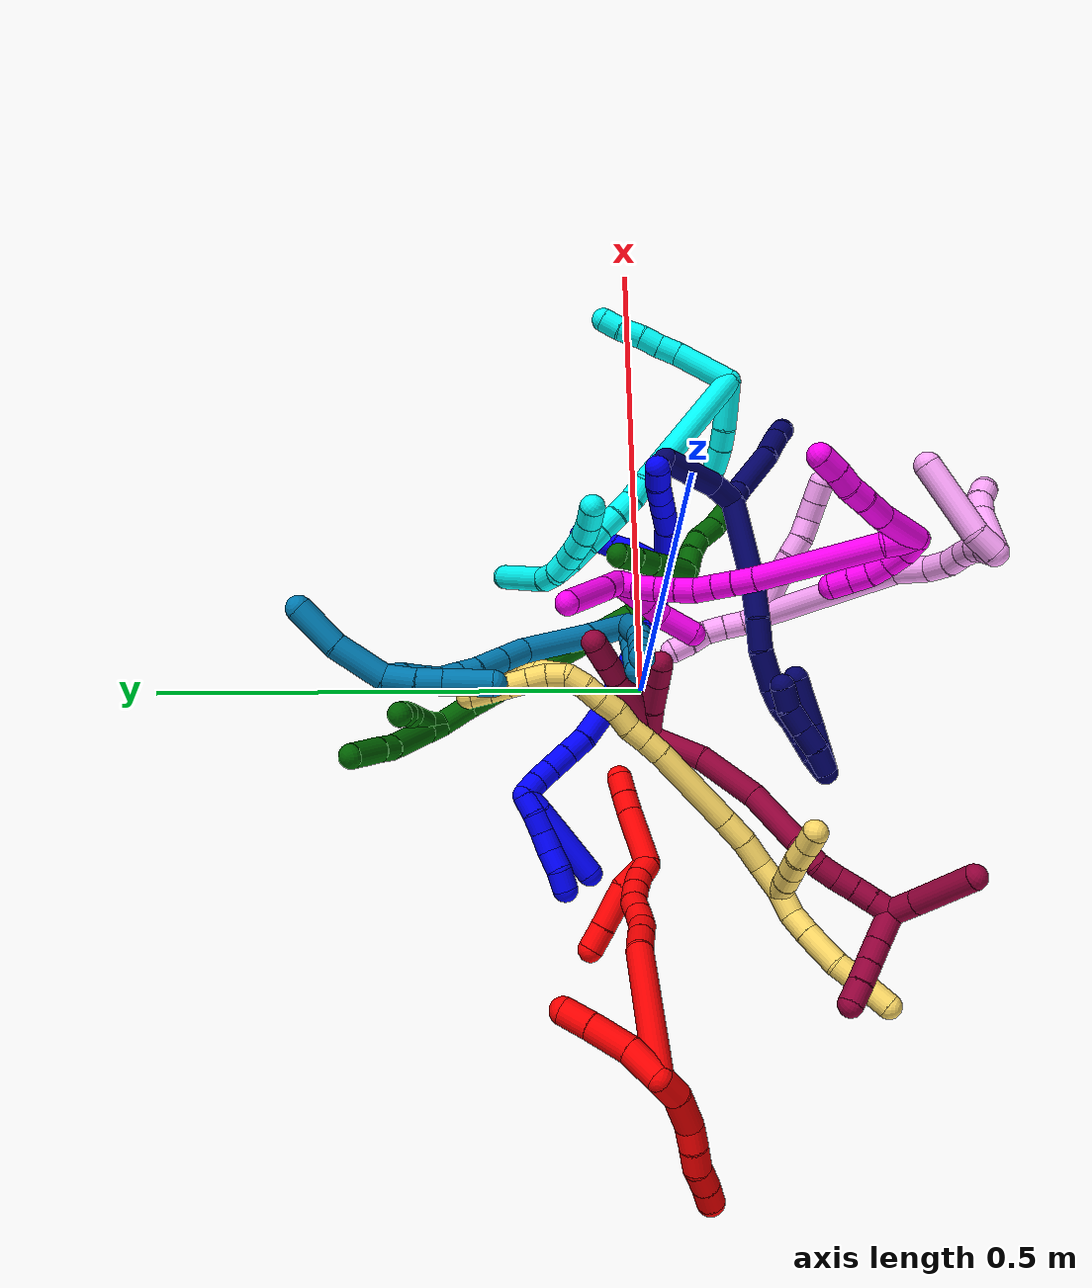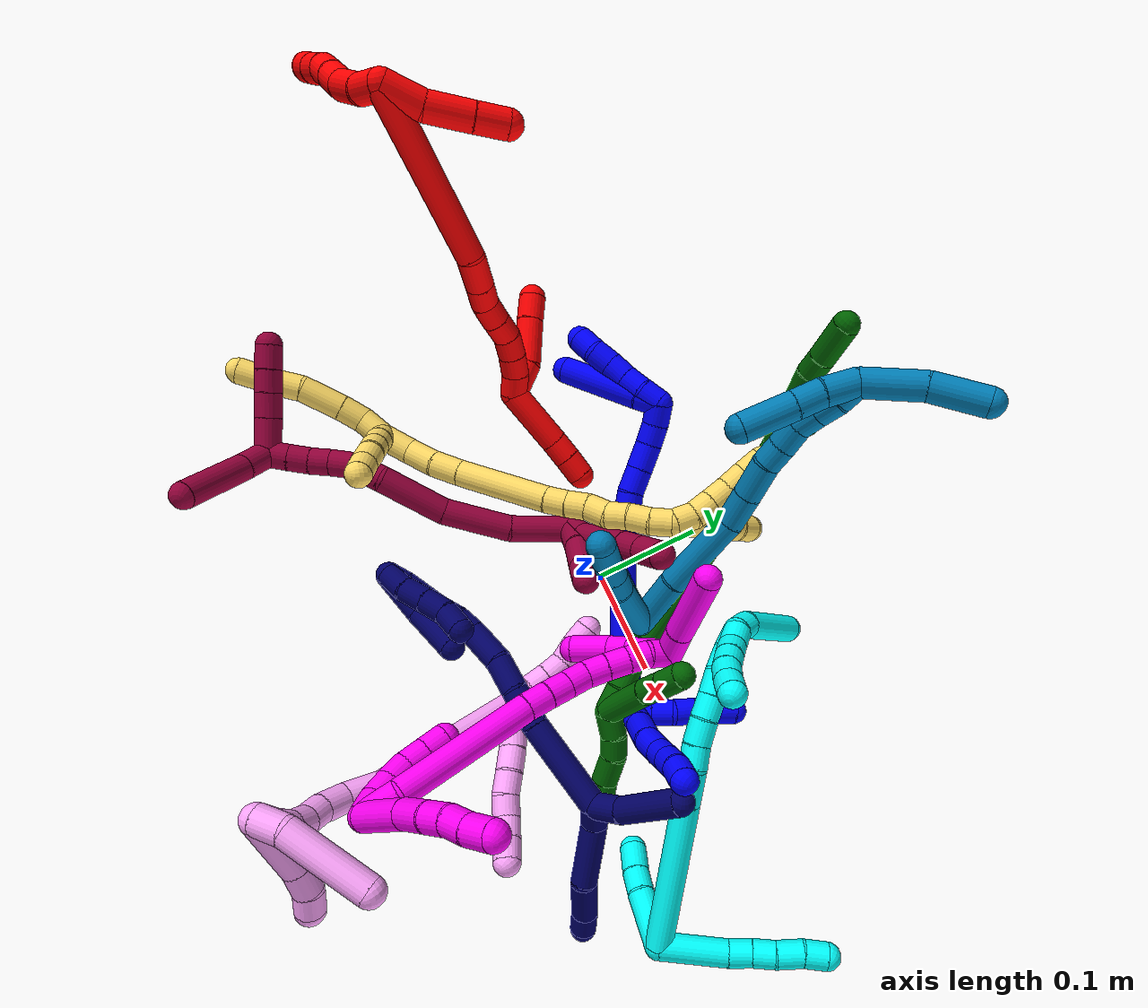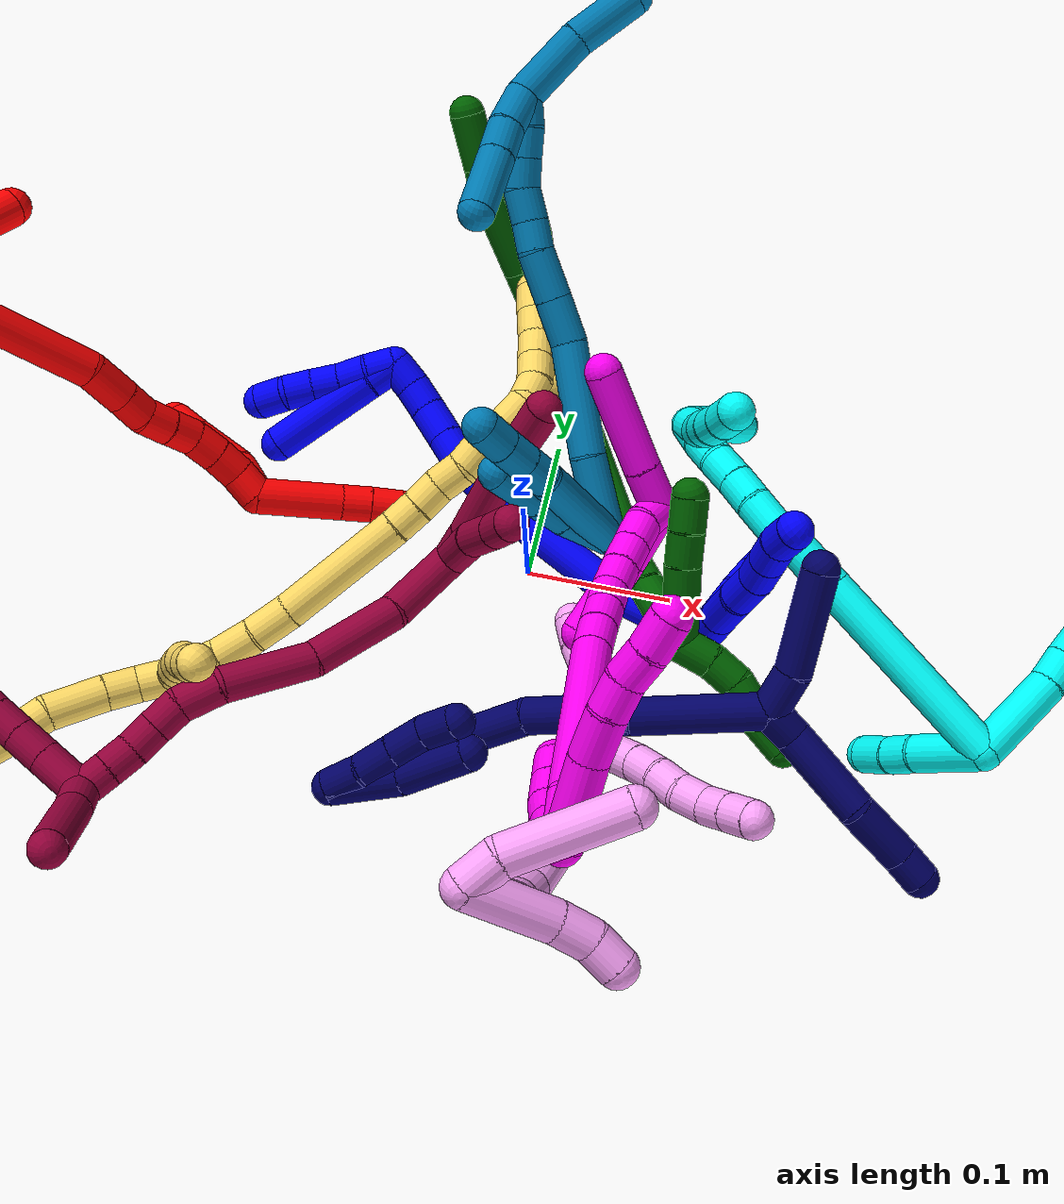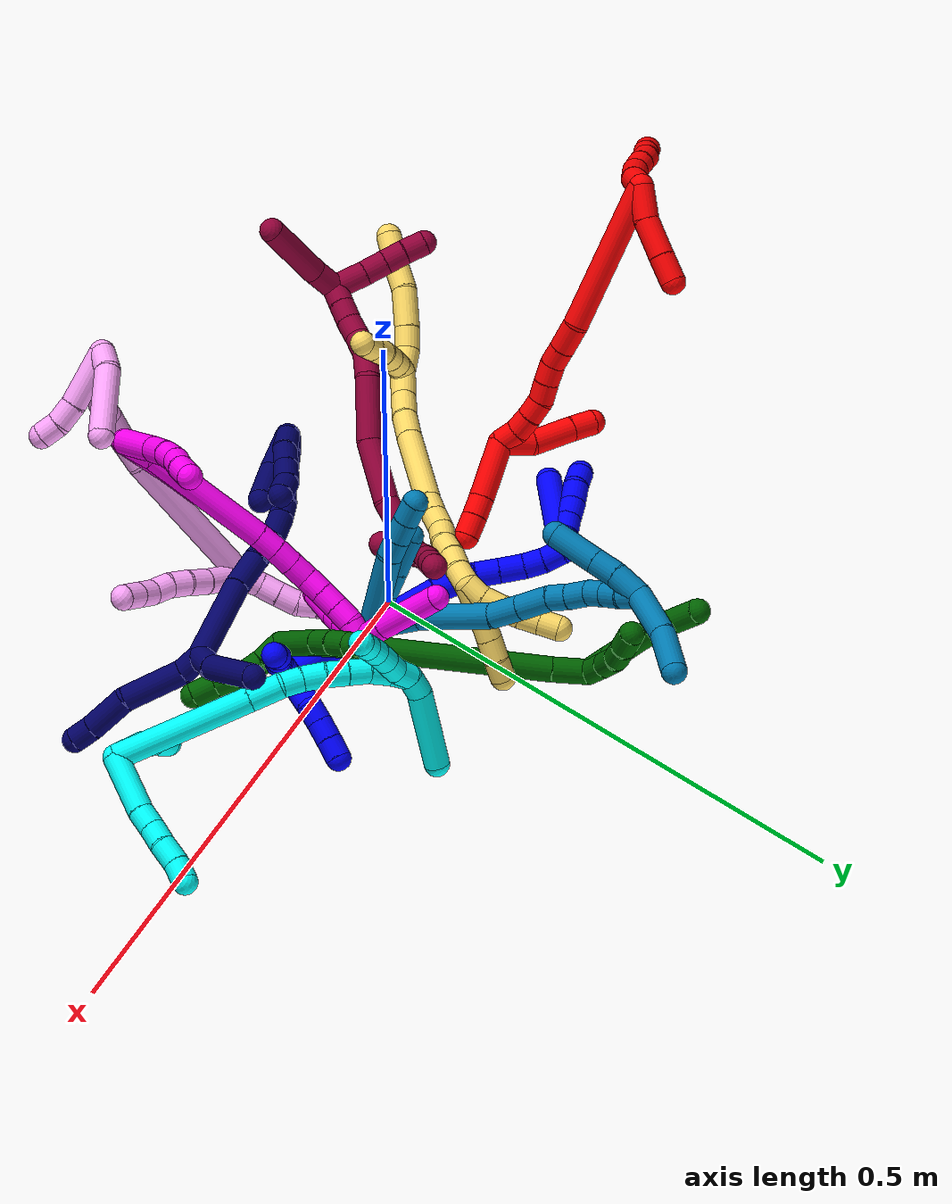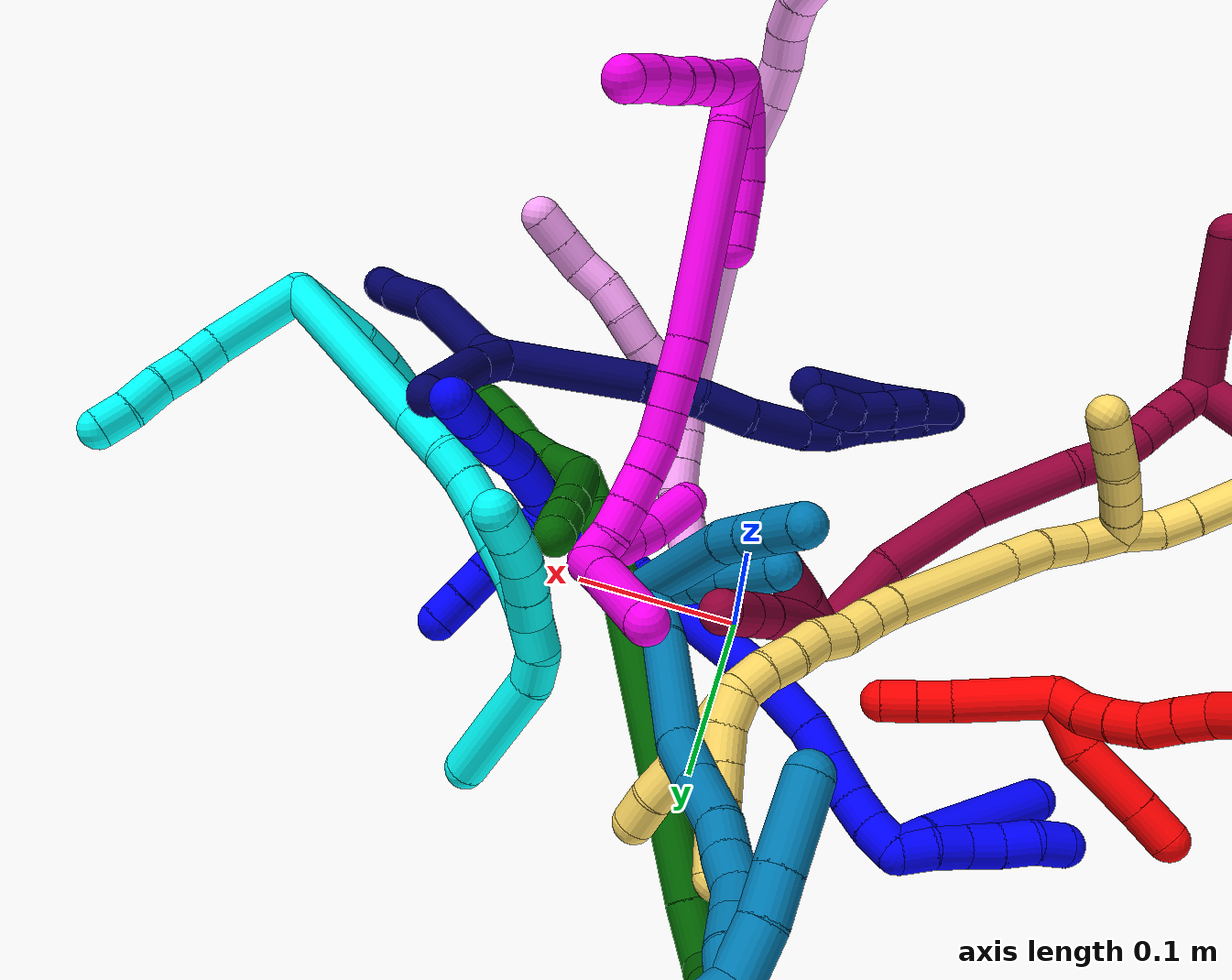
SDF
<sdf version="1.7">
 <world name="default">
  <plugin name="TubeGeneratorPlugin" filename="libtube_generator_plugin.so"/>
  <model name="photoneo_s_sensor">
   <static>1</static>
   <pose>0 0 2 1.57079 1.57079 3.14159</pose>
   <link name="link">
    <inertial><mass>0.1</mass></inertial>
    <sensor name="sensor" type="depth">
     <update_rate>30</update_rate>
     <camera>
      <horizontal_fov>1.22</horizontal_fov>
      <image><width>1920</width><height>1200</height><format>B8G8R8</format></image>
      <clip><near>0.1</near><far>4</far></clip>
      <depth_camera><output>points</output></depth_camera>
     </camera>
     <plugin name="camera_plugin" filename="libgazebo_ros_depth_camera.so">
      <baseline>0.2</baseline>
      <alwaysOn>1</alwaysOn>
      <updateRate>0.0</updateRate>
      <cameraName>camera_ir</cameraName>
      <imageTopicName>/camera/color/image_raw</imageTopicName>
      <cameraInfoTopicName>/camera/color/camera_info</cameraInfoTopicName>
      <depthImageTopicName>/camera/depth/image_raw</depthImageTopicName>
      <depthImageCameraInfoTopicName>/camera/depth/camera_info</depthImageCameraInfoTopicName>
      <pointCloudTopicName>/camera/depth/points</pointCloudTopicName>
      <frameName>fr_optical</frameName>
      <pointCloudCutoff>0.1</pointCloudCutoff>
      <pointCloudCutoffMax>2.0</pointCloudCutoffMax>
      <distortionK1>0</distortionK1>
      <distortionK2>0</distortionK2>
      <distortionK3>0</distortionK3>
      <distortionT1>0</distortionT1>
      <distortionT2>0</distortionT2>
      <CxPrime>0</CxPrime>
      <Cx>0</Cx>
      <Cy>0</Cy>
      <focalLength>0</focalLength>
      <hackBaseline>0</hackBaseline>
     </plugin>
    </sensor>
   </link>
  </model>
  <gravity>0 0 -9.8</gravity>
  <magnetic_field>6e-06 2.3e-05 -4.2e-05</magnetic_field>
  <atmosphere type="adiabatic"/>
  <physics name="default_physics" default="0" type="ode">
   <max_step_size>0.003</max_step_size>
   <real_time_factor>1</real_time_factor>
   <real_time_update_rate>1000</real_time_update_rate>
   <max_contacts>10000</max_contacts>
   <ode>
    <solver>
     <type>quick</type>
     <iters>100</iters>
     <sor>1.3</sor>
     <use_dynamic_moi_rescaling>0</use_dynamic_moi_rescaling>
    </solver>
    <constraints>
     <contact_max_correcting_vel>0</contact_max_correcting_vel>
     <contact_surface_layer>0.001</contact_surface_layer>
     <cfm>0</cfm>
     <erp>0.2</erp>
    </constraints>
   </ode>
  </physics>
  <scene><ambient>0.4 0.4 0.4 1</ambient><background>0.7 0.7 0.7 1</background><shadows>0</shadows></scene>
  <audio><device>default</device></audio>
  <spherical_coordinates>
   <surface_model>EARTH_WGS84</surface_model>
   <latitude_deg>0</latitude_deg>
   <longitude_deg>0</longitude_deg>
   <elevation>0</elevation>
   <heading_deg>0</heading_deg>
  </spherical_coordinates>
  <model name="bin">
   <static>1</static>
   <link name="bottom">
    <collision name="collision-bottom">
     <pose>0 0 -0.01 0 -0 0</pose>
     <geometry><box><size>0.8 0.6 0.02</size></box></geometry>
     <surface>
      <friction><ode><mu>100</mu><mu2>100</mu2></ode></friction>
      <contact><collide_bitmask>65535</collide_bitmask></contact>
     </surface>
    </collision>
   </link>
   <link name="west_wall">
    <collision name="collision-west_wall">
     <pose>-0.41 0 0.1 0 -0 0</pose>
     <geometry><box><size>0.02 0.6 0.2</size></box></geometry>
     <surface>
      <friction><ode><mu>100</mu><mu2>100</mu2></ode></friction>
      <contact><collide_bitmask>65535</collide_bitmask></contact>
     </surface>
    </collision>
   </link>
   <link name="east_wall">
    <collision name="collision-east_wall">
     <pose>0.41 0 0.1 0 -0 0</pose>
     <geometry><box><size>0.02 0.6 0.2</size></box></geometry>
     <surface>
      <friction><ode><mu>100</mu><mu2>100</mu2></ode></friction>
      <contact><collide_bitmask>65535</collide_bitmask></contact>
     </surface>
    </collision>
   </link>
   <link name="south_wall">
    <collision name="collision-south_wall">
     <pose>0 -0.31 0.1 0 -0 0</pose>
     <geometry><box><size>0.8 0.02 0.2</size></box></geometry>
     <surface>
      <friction><ode><mu>100</mu><mu2>100</mu2></ode></friction>
      <contact><collide_bitmask>65535</collide_bitmask></contact>
     </surface>
    </collision>
   </link>
   <link name="north_wall">
    <collision name="collision-north_wall">
     <pose>0 0.31 0.1 0 -0 0</pose>
     <geometry><box><size>0.8 0.02 0.2</size></box></geometry>
     <surface>
      <friction><ode><mu>100</mu><mu2>100</mu2></ode></friction>
      <contact><collide_bitmask>65535</collide_bitmask></contact>
     </surface>
    </collision>
   </link>
  </model>
  <model name="1">
   <static>0</static>
   <link name="1">
    <collision name="collision-cylinder-e_1_2_8">
     <pose>-0.00695 -0.004266 0.01298 0.317555 -0.470546 -0.076731</pose>
     <geometry><cylinder><radius>0.0125</radius><length>0.030659</length></cylinder></geometry>
     <surface>
      <friction><ode><mu>1.16</mu><mu2>1.16</mu2><slip1>0</slip1><slip2>0</slip2></ode></friction>
      <contact><ode><kp>1e+06</kp><kd>1</kd><max_vel>0</max_vel><min_depth>0.001</min_depth></ode></contact>
     </surface>
    </collision>
    <visual name="visual-cylinder-e_1_2_8">
     <pose>-0.00695 -0.004266 0.01298 0.317555 -0.470546 -0.076731</pose>
     <geometry><cylinder><radius>0.0125</radius><length>0.030659</length></cylinder></geometry>
     <material><ambient>0 0 1 1</ambient></material>
    </visual>
    <collision name="collision-cylinder-e_2_8_9">
     <pose>-0.021501 -0.013913 0.039943 0.367319 -0.469513 -0.088793</pose>
     <geometry><cylinder><radius>0.0125</radius><length>0.0336</length></cylinder></geometry>
     <surface>
      <friction><ode><mu>1.16</mu><mu2>1.16</mu2><slip1>0</slip1><slip2>0</slip2></ode></friction>
      <contact><ode><kp>1e+06</kp><kd>1</kd><max_vel>0</max_vel><min_depth>0.001</min_depth></ode></contact>
     </surface>
    </collision>
    <visual name="visual-cylinder-e_2_8_9">
     <pose>-0.021501 -0.013913 0.039943 0.367319 -0.469513 -0.088793</pose>
     <geometry><cylinder><radius>0.0125</radius><length>0.0336</length></cylinder></geometry>
     <material><ambient>0 0 1 1</ambient></material>
    </visual>
    <collision name="collision-cylinder-e_3_9_10">
     <pose>-0.033022 -0.021646 0.065384 0.202508 -0.323308 -0.033135</pose>
     <geometry><cylinder><radius>0.0125</radius><length>0.024673</length></cylinder></geometry>
     <surface>
      <friction><ode><mu>1.16</mu><mu2>1.16</mu2><slip1>0</slip1><slip2>0</slip2></ode></friction>
      <contact><ode><kp>1e+06</kp><kd>1</kd><max_vel>0</max_vel><min_depth>0.001</min_depth></ode></contact>
     </surface>
    </collision>
    <visual name="visual-cylinder-e_3_9_10">
     <pose>-0.033022 -0.021646 0.065384 0.202508 -0.323308 -0.033135</pose>
     <geometry><cylinder><radius>0.0125</radius><length>0.024673</length></cylinder></geometry>
     <material><ambient>0 0 1 1</ambient></material>
    </visual>
    <collision name="collision-cylinder-e_4_10_11">
     <pose>-0.04185 -0.025685 0.085735 0.187424 -0.496954 -0.047684</pose>
     <geometry><cylinder><radius>0.0125</radius><length>0.020593</length></cylinder></geometry>
     <surface>
      <friction><ode><mu>1.16</mu><mu2>1.16</mu2><slip1>0</slip1><slip2>0</slip2></ode></friction>
      <contact><ode><kp>1e+06</kp><kd>1</kd><max_vel>0</max_vel><min_depth>0.001</min_depth></ode></contact>
     </surface>
    </collision>
    <visual name="visual-cylinder-e_4_10_11">
     <pose>-0.04185 -0.025685 0.085735 0.187424 -0.496954 -0.047684</pose>
     <geometry><cylinder><radius>0.0125</radius><length>0.020593</length></cylinder></geometry>
     <material><ambient>0 0 1 1</ambient></material>
    </visual>
    <collision name="collision-cylinder-e_5_11_12">
     <pose>-0.051636 -0.028999 0.1034 0.183462 -0.500275 -0.046996</pose>
     <geometry><cylinder><radius>0.0125</radius><length>0.020337</length></cylinder></geometry>
     <surface>
      <friction><ode><mu>1.16</mu><mu2>1.16</mu2><slip1>0</slip1><slip2>0</slip2></ode></friction>
      <contact><ode><kp>1e+06</kp><kd>1</kd><max_vel>0</max_vel><min_depth>0.001</min_depth></ode></contact>
     </surface>
    </collision>
    <visual name="visual-cylinder-e_5_11_12">
     <pose>-0.051636 -0.028999 0.1034 0.183462 -0.500275 -0.046996</pose>
     <geometry><cylinder><radius>0.0125</radius><length>0.020337</length></cylinder></geometry>
     <material><ambient>0 0 1 1</ambient></material>
    </visual>
    <collision name="collision-cylinder-e_6_12_6">
     <pose>-0.059996 -0.03399 0.121002 0.363952 -0.353145 -0.065643</pose>
     <geometry><cylinder><radius>0.0125</radius><length>0.020138</length></cylinder></geometry>
     <surface>
      <friction><ode><mu>1.16</mu><mu2>1.16</mu2><slip1>0</slip1><slip2>0</slip2></ode></friction>
      <contact><ode><kp>1e+06</kp><kd>1</kd><max_vel>0</max_vel><min_depth>0.001</min_depth></ode></contact>
     </surface>
    </collision>
    <visual name="visual-cylinder-e_6_12_6">
     <pose>-0.059996 -0.03399 0.121002 0.363952 -0.353145 -0.065643</pose>
     <geometry><cylinder><radius>0.0125</radius><length>0.020138</length></cylinder></geometry>
     <material><ambient>0 0 1 1</ambient></material>
    </visual>
    <collision name="collision-cylinder-e_1_2_13">
     <pose>0.003262 0.006006 0.0073 -0.688502 0.332241 -0.120081</pose>
     <geometry><cylinder><radius>0.0125</radius><length>0.02</length></cylinder></geometry>
     <surface>
      <friction><ode><mu>1.16</mu><mu2>1.16</mu2><slip1>0</slip1><slip2>0</slip2></ode></friction>
      <contact><ode><kp>1e+06</kp><kd>1</kd><max_vel>0</max_vel><min_depth>0.001</min_depth></ode></contact>
     </surface>
    </collision>
    <visual name="visual-cylinder-e_1_2_13">
     <pose>0.003262 0.006006 0.0073 -0.688502 0.332241 -0.120081</pose>
     <geometry><cylinder><radius>0.0125</radius><length>0.02</length></cylinder></geometry>
     <material><ambient>0 0 1 1</ambient></material>
    </visual>
    <collision name="collision-cylinder-e_2_13_14">
     <pose>0.009662 0.017962 0.022 -0.677097 0.31922 -0.113242</pose>
     <geometry><cylinder><radius>0.0125</radius><length>0.02</length></cylinder></geometry>
     <surface>
      <friction><ode><mu>1.16</mu><mu2>1.16</mu2><slip1>0</slip1><slip2>0</slip2></ode></friction>
      <contact><ode><kp>1e+06</kp><kd>1</kd><max_vel>0</max_vel><min_depth>0.001</min_depth></ode></contact>
     </surface>
    </collision>
    <visual name="visual-cylinder-e_2_13_14">
     <pose>0.009662 0.017962 0.022 -0.677097 0.31922 -0.113242</pose>
     <geometry><cylinder><radius>0.0125</radius><length>0.02</length></cylinder></geometry>
     <material><ambient>0 0 1 1</ambient></material>
    </visual>
    <collision name="collision-cylinder-e_3_14_15">
     <pose>0.018112 0.030813 0.034312 -0.952317 0.560044 -0.294483</pose>
     <geometry><cylinder><radius>0.0125</radius><length>0.02</length></cylinder></geometry>
     <surface>
      <friction><ode><mu>1.16</mu><mu2>1.16</mu2><slip1>0</slip1><slip2>0</slip2></ode></friction>
      <contact><ode><kp>1e+06</kp><kd>1</kd><max_vel>0</max_vel><min_depth>0.001</min_depth></ode></contact>
     </surface>
    </collision>
    <visual name="visual-cylinder-e_3_14_15">
     <pose>0.018112 0.030813 0.034312 -0.952317 0.560044 -0.294483</pose>
     <geometry><cylinder><radius>0.0125</radius><length>0.02</length></cylinder></geometry>
     <material><ambient>0 0 1 1</ambient></material>
    </visual>
    <collision name="collision-cylinder-e_4_15_16">
     <pose>0.028815 0.044244 0.044546 -0.886775 0.569386 -0.276197</pose>
     <geometry><cylinder><radius>0.0125</radius><length>0.02</length></cylinder></geometry>
     <surface>
      <friction><ode><mu>1.16</mu><mu2>1.16</mu2><slip1>0</slip1><slip2>0</slip2></ode></friction>
      <contact><ode><kp>1e+06</kp><kd>1</kd><max_vel>0</max_vel><min_depth>0.001</min_depth></ode></contact>
     </surface>
    </collision>
    <visual name="visual-cylinder-e_4_15_16">
     <pose>0.028815 0.044244 0.044546 -0.886775 0.569386 -0.276197</pose>
     <geometry><cylinder><radius>0.0125</radius><length>0.02</length></cylinder></geometry>
     <material><ambient>0 0 1 1</ambient></material>
    </visual>
    <collision name="collision-cylinder-e_5_16_5">
     <pose>0.039946 0.057281 0.054837 -0.918946 0.611312 -0.309757</pose>
     <geometry><cylinder><radius>0.0125</radius><length>0.02</length></cylinder></geometry>
     <surface>
      <friction><ode><mu>1.16</mu><mu2>1.16</mu2><slip1>0</slip1><slip2>0</slip2></ode></friction>
      <contact><ode><kp>1e+06</kp><kd>1</kd><max_vel>0</max_vel><min_depth>0.001</min_depth></ode></contact>
     </surface>
    </collision>
    <visual name="visual-cylinder-e_5_16_5">
     <pose>0.039946 0.057281 0.054837 -0.918946 0.611312 -0.309757</pose>
     <geometry><cylinder><radius>0.0125</radius><length>0.02</length></cylinder></geometry>
     <material><ambient>0 0 1 1</ambient></material>
    </visual>
    <collision name="collision-cylinder-e_1_2_17">
     <pose>-0.017722 0.022836 -0.016694 -2.20205 -0.559661 1.03016</pose>
     <geometry><cylinder><radius>0.0125</radius><length>0.066761</length></cylinder></geometry>
     <surface>
      <friction><ode><mu>1.16</mu><mu2>1.16</mu2><slip1>0</slip1><slip2>0</slip2></ode></friction>
      <contact><ode><kp>1e+06</kp><kd>1</kd><max_vel>0</max_vel><min_depth>0.001</min_depth></ode></contact>
     </surface>
    </collision>
    <visual name="visual-cylinder-e_1_2_17">
     <pose>-0.017722 0.022836 -0.016694 -2.20205 -0.559661 1.03016</pose>
     <geometry><cylinder><radius>0.0125</radius><length>0.066761</length></cylinder></geometry>
     <material><ambient>0 0 1 1</ambient></material>
    </visual>
    <collision name="collision-cylinder-e_2_17_18">
     <pose>-0.068981 0.081388 -0.046811 -1.9303 -0.721086 0.997172</pose>
     <geometry><cylinder><radius>0.0125</radius><length>0.101597</length></cylinder></geometry>
     <surface>
      <friction><ode><mu>1.16</mu><mu2>1.16</mu2><slip1>0</slip1><slip2>0</slip2></ode></friction>
      <contact><ode><kp>1e+06</kp><kd>1</kd><max_vel>0</max_vel><min_depth>0.001</min_depth></ode></contact>
     </surface>
    </collision>
    <visual name="visual-cylinder-e_2_17_18">
     <pose>-0.068981 0.081388 -0.046811 -1.9303 -0.721086 0.997172</pose>
     <geometry><cylinder><radius>0.0125</radius><length>0.101597</length></cylinder></geometry>
     <material><ambient>0 0 1 1</ambient></material>
    </visual>
    <collision name="collision-cylinder-e_3_18_19">
     <pose>-0.11514 0.134142 -0.063708 -1.77189 -0.627871 0.756758</pose>
     <geometry><cylinder><radius>0.0125</radius><length>0.042975</length></cylinder></geometry>
     <surface>
      <friction><ode><mu>1.16</mu><mu2>1.16</mu2><slip1>0</slip1><slip2>0</slip2></ode></friction>
      <contact><ode><kp>1e+06</kp><kd>1</kd><max_vel>0</max_vel><min_depth>0.001</min_depth></ode></contact>
     </surface>
    </collision>
    <visual name="visual-cylinder-e_3_18_19">
     <pose>-0.11514 0.134142 -0.063708 -1.77189 -0.627871 0.756758</pose>
     <geometry><cylinder><radius>0.0125</radius><length>0.042975</length></cylinder></geometry>
     <material><ambient>0 0 1 1</ambient></material>
    </visual>
    <collision name="collision-cylinder-e_4_19_20">
     <pose>-0.132983 0.16157 -0.06759 -1.61016 -0.465353 0.483336</pose>
     <geometry><cylinder><radius>0.0125</radius><length>0.023268</length></cylinder></geometry>
     <surface>
      <friction><ode><mu>1.16</mu><mu2>1.16</mu2><slip1>0</slip1><slip2>0</slip2></ode></friction>
      <contact><ode><kp>1e+06</kp><kd>1</kd><max_vel>0</max_vel><min_depth>0.001</min_depth></ode></contact>
     </surface>
    </collision>
    <visual name="visual-cylinder-e_4_19_20">
     <pose>-0.132983 0.16157 -0.06759 -1.61016 -0.465353 0.483336</pose>
     <geometry><cylinder><radius>0.0125</radius><length>0.023268</length></cylinder></geometry>
     <material><ambient>0 0 1 1</ambient></material>
    </visual>
    <collision name="collision-cylinder-e_5_20_21">
     <pose>-0.144107 0.183023 -0.06835 -1.6025 -0.489894 0.505022</pose>
     <geometry><cylinder><radius>0.0125</radius><length>0.025092</length></cylinder></geometry>
     <surface>
      <friction><ode><mu>1.16</mu><mu2>1.16</mu2><slip1>0</slip1><slip2>0</slip2></ode></friction>
      <contact><ode><kp>1e+06</kp><kd>1</kd><max_vel>0</max_vel><min_depth>0.001</min_depth></ode></contact>
     </surface>
    </collision>
    <visual name="visual-cylinder-e_5_20_21">
     <pose>-0.144107 0.183023 -0.06835 -1.6025 -0.489894 0.505022</pose>
     <geometry><cylinder><radius>0.0125</radius><length>0.025092</length></cylinder></geometry>
     <material><ambient>0 0 1 1</ambient></material>
    </visual>
    <collision name="collision-cylinder-e_6_21_22">
     <pose>-0.155866 0.202233 -0.068317 -1.52365 -0.622818 0.595827</pose>
     <geometry><cylinder><radius>0.0125</radius><length>0.020079</length></cylinder></geometry>
     <surface>
      <friction><ode><mu>1.16</mu><mu2>1.16</mu2><slip1>0</slip1><slip2>0</slip2></ode></friction>
      <contact><ode><kp>1e+06</kp><kd>1</kd><max_vel>0</max_vel><min_depth>0.001</min_depth></ode></contact>
     </surface>
    </collision>
    <visual name="visual-cylinder-e_6_21_22">
     <pose>-0.155866 0.202233 -0.068317 -1.52365 -0.622818 0.595827</pose>
     <geometry><cylinder><radius>0.0125</radius><length>0.020079</length></cylinder></geometry>
     <material><ambient>0 0 1 1</ambient></material>
    </visual>
    <collision name="collision-cylinder-e_7_22_1">
     <pose>-0.169006 0.217392 -0.067657 -1.53152 -0.803917 0.776013</pose>
     <geometry><cylinder><radius>0.0125</radius><length>0.020228</length></cylinder></geometry>
     <surface>
      <friction><ode><mu>1.16</mu><mu2>1.16</mu2><slip1>0</slip1><slip2>0</slip2></ode></friction>
      <contact><ode><kp>1e+06</kp><kd>1</kd><max_vel>0</max_vel><min_depth>0.001</min_depth></ode></contact>
     </surface>
    </collision>
    <visual name="visual-cylinder-e_7_22_1">
     <pose>-0.169006 0.217392 -0.067657 -1.53152 -0.803917 0.776013</pose>
     <geometry><cylinder><radius>0.0125</radius><length>0.020228</length></cylinder></geometry>
     <material><ambient>0 0 1 1</ambient></material>
    </visual>
    <collision name="collision-cylinder-e_1_1_23">
     <pose>-0.180514 0.221532 -0.076906 2.84871 -0.401633 -1.88752</pose>
     <geometry><cylinder><radius>0.0125</radius><length>0.021616</length></cylinder></geometry>
     <surface>
      <friction><ode><mu>1.16</mu><mu2>1.16</mu2><slip1>0</slip1><slip2>0</slip2></ode></friction>
      <contact><ode><kp>1e+06</kp><kd>1</kd><max_vel>0</max_vel><min_depth>0.001</min_depth></ode></contact>
     </surface>
    </collision>
    <visual name="visual-cylinder-e_1_1_23">
     <pose>-0.180514 0.221532 -0.076906 2.84871 -0.401633 -1.88752</pose>
     <geometry><cylinder><radius>0.0125</radius><length>0.021616</length></cylinder></geometry>
     <material><ambient>0 0 1 1</ambient></material>
    </visual>
    <collision name="collision-cylinder-e_2_23_4">
     <pose>-0.19798 0.211218 -0.122559 2.93844 -0.344633 -2.08201</pose>
     <geometry><cylinder><radius>0.0125</radius><length>0.078384</length></cylinder></geometry>
     <surface>
      <friction><ode><mu>1.16</mu><mu2>1.16</mu2><slip1>0</slip1><slip2>0</slip2></ode></friction>
      <contact><ode><kp>1e+06</kp><kd>1</kd><max_vel>0</max_vel><min_depth>0.001</min_depth></ode></contact>
     </surface>
    </collision>
    <visual name="visual-cylinder-e_2_23_4">
     <pose>-0.19798 0.211218 -0.122559 2.93844 -0.344633 -2.08201</pose>
     <geometry><cylinder><radius>0.0125</radius><length>0.078384</length></cylinder></geometry>
     <material><ambient>0 0 1 1</ambient></material>
    </visual>
    <collision name="collision-cylinder-e_1_1_24">
     <pose>-0.182448 0.223958 -0.075247 3.0849 -0.663543 -2.97735</pose>
     <geometry><cylinder><radius>0.0125</radius><length>0.02</length></cylinder></geometry>
     <surface>
      <friction><ode><mu>1.16</mu><mu2>1.16</mu2><slip1>0</slip1><slip2>0</slip2></ode></friction>
      <contact><ode><kp>1e+06</kp><kd>1</kd><max_vel>0</max_vel><min_depth>0.001</min_depth></ode></contact>
     </surface>
    </collision>
    <visual name="visual-cylinder-e_1_1_24">
     <pose>-0.182448 0.223958 -0.075247 3.0849 -0.663543 -2.97735</pose>
     <geometry><cylinder><radius>0.0125</radius><length>0.02</length></cylinder></geometry>
     <material><ambient>0 0 1 1</ambient></material>
    </visual>
    <collision name="collision-cylinder-e_2_24_25">
     <pose>-0.193236 0.224111 -0.091956 -3.07394 -0.481289 2.86754</pose>
     <geometry><cylinder><radius>0.0125</radius><length>0.02</length></cylinder></geometry>
     <surface>
      <friction><ode><mu>1.16</mu><mu2>1.16</mu2><slip1>0</slip1><slip2>0</slip2></ode></friction>
      <contact><ode><kp>1e+06</kp><kd>1</kd><max_vel>0</max_vel><min_depth>0.001</min_depth></ode></contact>
     </surface>
    </collision>
    <visual name="visual-cylinder-e_2_24_25">
     <pose>-0.193236 0.224111 -0.091956 -3.07394 -0.481289 2.86754</pose>
     <geometry><cylinder><radius>0.0125</radius><length>0.02</length></cylinder></geometry>
     <material><ambient>0 0 1 1</ambient></material>
    </visual>
    <collision name="collision-cylinder-e_3_25_26">
     <pose>-0.203686 0.225601 -0.108882 -3.03179 -0.621295 2.80252</pose>
     <geometry><cylinder><radius>0.0125</radius><length>0.02</length></cylinder></geometry>
     <surface>
      <friction><ode><mu>1.16</mu><mu2>1.16</mu2><slip1>0</slip1><slip2>0</slip2></ode></friction>
      <contact><ode><kp>1e+06</kp><kd>1</kd><max_vel>0</max_vel><min_depth>0.001</min_depth></ode></contact>
     </surface>
    </collision>
    <visual name="visual-cylinder-e_3_25_26">
     <pose>-0.203686 0.225601 -0.108882 -3.03179 -0.621295 2.80252</pose>
     <geometry><cylinder><radius>0.0125</radius><length>0.02</length></cylinder></geometry>
     <material><ambient>0 0 1 1</ambient></material>
    </visual>
    <collision name="collision-cylinder-e_4_26_27">
     <pose>-0.215801 0.22638 -0.124734 3.12717 -0.680818 -3.10087</pose>
     <geometry><cylinder><radius>0.0125</radius><length>0.02</length></cylinder></geometry>
     <surface>
      <friction><ode><mu>1.16</mu><mu2>1.16</mu2><slip1>0</slip1><slip2>0</slip2></ode></friction>
      <contact><ode><kp>1e+06</kp><kd>1</kd><max_vel>0</max_vel><min_depth>0.001</min_depth></ode></contact>
     </surface>
    </collision>
    <visual name="visual-cylinder-e_4_26_27">
     <pose>-0.215801 0.22638 -0.124734 3.12717 -0.680818 -3.10087</pose>
     <geometry><cylinder><radius>0.0125</radius><length>0.02</length></cylinder></geometry>
     <material><ambient>0 0 1 1</ambient></material>
    </visual>
    <collision name="collision-cylinder-e_5_27_3">
     <pose>-0.225992 0.227941 -0.14156 -2.95888 -0.40028 2.29319</pose>
     <geometry><cylinder><radius>0.0125</radius><length>0.02</length></cylinder></geometry>
     <surface>
      <friction><ode><mu>1.16</mu><mu2>1.16</mu2><slip1>0</slip1><slip2>0</slip2></ode></friction>
      <contact><ode><kp>1e+06</kp><kd>1</kd><max_vel>0</max_vel><min_depth>0.001</min_depth></ode></contact>
     </surface>
    </collision>
    <visual name="visual-cylinder-e_5_27_3">
     <pose>-0.225992 0.227941 -0.14156 -2.95888 -0.40028 2.29319</pose>
     <geometry><cylinder><radius>0.0125</radius><length>0.02</length></cylinder></geometry>
     <material><ambient>0 0 1 1</ambient></material>
    </visual>
    <collision name="collision-sphere-3">
     <pose>-0.229889 0.229615 -0.150616 0 -0 0</pose>
     <geometry><sphere><radius>0.0125</radius></sphere></geometry>
     <surface>
      <friction><ode><mu>1.16</mu><mu2>1.16</mu2><slip1>0</slip1><slip2>0</slip2></ode></friction>
      <contact><ode><kp>1e+06</kp><kd>1</kd><max_vel>0</max_vel><min_depth>0.001</min_depth></ode></contact>
     </surface>
    </collision>
    <visual name="visual-sphere-3">
     <pose>-0.229889 0.229615 -0.150616 0 -0 0</pose>
     <geometry><sphere><radius>0.0125</radius></sphere></geometry>
     <material><ambient>0 0 1 1</ambient></material>
    </visual>
    <collision name="collision-sphere-27">
     <pose>-0.222096 0.226268 -0.132504 0 -0 0</pose>
     <geometry><sphere><radius>0.0125</radius></sphere></geometry>
     <surface>
      <friction><ode><mu>1.16</mu><mu2>1.16</mu2><slip1>0</slip1><slip2>0</slip2></ode></friction>
      <contact><ode><kp>1e+06</kp><kd>1</kd><max_vel>0</max_vel><min_depth>0.001</min_depth></ode></contact>
     </surface>
    </collision>
    <visual name="visual-sphere-27">
     <pose>-0.222096 0.226268 -0.132504 0 -0 0</pose>
     <geometry><sphere><radius>0.0125</radius></sphere></geometry>
     <material><ambient>0 0 1 1</ambient></material>
    </visual>
    <collision name="collision-sphere-26">
     <pose>-0.209507 0.226492 -0.116964 0 -0 0</pose>
     <geometry><sphere><radius>0.0125</radius></sphere></geometry>
     <surface>
      <friction><ode><mu>1.16</mu><mu2>1.16</mu2><slip1>0</slip1><slip2>0</slip2></ode></friction>
      <contact><ode><kp>1e+06</kp><kd>1</kd><max_vel>0</max_vel><min_depth>0.001</min_depth></ode></contact>
     </surface>
    </collision>
    <visual name="visual-sphere-26">
     <pose>-0.209507 0.226492 -0.116964 0 -0 0</pose>
     <geometry><sphere><radius>0.0125</radius></sphere></geometry>
     <material><ambient>0 0 1 1</ambient></material>
    </visual>
    <collision name="collision-sphere-25">
     <pose>-0.197865 0.22471 -0.1008 0 -0 0</pose>
     <geometry><sphere><radius>0.0125</radius></sphere></geometry>
     <surface>
      <friction><ode><mu>1.16</mu><mu2>1.16</mu2><slip1>0</slip1><slip2>0</slip2></ode></friction>
      <contact><ode><kp>1e+06</kp><kd>1</kd><max_vel>0</max_vel><min_depth>0.001</min_depth></ode></contact>
     </surface>
    </collision>
    <visual name="visual-sphere-25">
     <pose>-0.197865 0.22471 -0.1008 0 -0 0</pose>
     <geometry><sphere><radius>0.0125</radius></sphere></geometry>
     <material><ambient>0 0 1 1</ambient></material>
    </visual>
    <collision name="collision-sphere-24">
     <pose>-0.188607 0.223511 -0.083112 0 -0 0</pose>
     <geometry><sphere><radius>0.0125</radius></sphere></geometry>
     <surface>
      <friction><ode><mu>1.16</mu><mu2>1.16</mu2><slip1>0</slip1><slip2>0</slip2></ode></friction>
      <contact><ode><kp>1e+06</kp><kd>1</kd><max_vel>0</max_vel><min_depth>0.001</min_depth></ode></contact>
     </surface>
    </collision>
    <visual name="visual-sphere-24">
     <pose>-0.188607 0.223511 -0.083112 0 -0 0</pose>
     <geometry><sphere><radius>0.0125</radius></sphere></geometry>
     <material><ambient>0 0 1 1</ambient></material>
    </visual>
    <collision name="collision-sphere-4">
     <pose>-0.211221 0.203775 -0.158688 0 -0 0</pose>
     <geometry><sphere><radius>0.0125</radius></sphere></geometry>
     <surface>
      <friction><ode><mu>1.16</mu><mu2>1.16</mu2><slip1>0</slip1><slip2>0</slip2></ode></friction>
      <contact><ode><kp>1e+06</kp><kd>1</kd><max_vel>0</max_vel><min_depth>0.001</min_depth></ode></contact>
     </surface>
    </collision>
    <visual name="visual-sphere-4">
     <pose>-0.211221 0.203775 -0.158688 0 -0 0</pose>
     <geometry><sphere><radius>0.0125</radius></sphere></geometry>
     <material><ambient>0 0 1 1</ambient></material>
    </visual>
    <collision name="collision-sphere-23">
     <pose>-0.184739 0.21866 -0.08643 0 -0 0</pose>
     <geometry><sphere><radius>0.0125</radius></sphere></geometry>
     <surface>
      <friction><ode><mu>1.16</mu><mu2>1.16</mu2><slip1>0</slip1><slip2>0</slip2></ode></friction>
      <contact><ode><kp>1e+06</kp><kd>1</kd><max_vel>0</max_vel><min_depth>0.001</min_depth></ode></contact>
     </surface>
    </collision>
    <visual name="visual-sphere-23">
     <pose>-0.184739 0.21866 -0.08643 0 -0 0</pose>
     <geometry><sphere><radius>0.0125</radius></sphere></geometry>
     <material><ambient>0 0 1 1</ambient></material>
    </visual>
    <collision name="collision-sphere-1">
     <pose>-0.176289 0.224404 -0.067381 0 -0 0</pose>
     <geometry><sphere><radius>0.0125</radius></sphere></geometry>
     <surface>
      <friction><ode><mu>1.16</mu><mu2>1.16</mu2><slip1>0</slip1><slip2>0</slip2></ode></friction>
      <contact><ode><kp>1e+06</kp><kd>1</kd><max_vel>0</max_vel><min_depth>0.001</min_depth></ode></contact>
     </surface>
    </collision>
    <visual name="visual-sphere-1">
     <pose>-0.176289 0.224404 -0.067381 0 -0 0</pose>
     <geometry><sphere><radius>0.0125</radius></sphere></geometry>
     <material><ambient>0 0 1 1</ambient></material>
    </visual>
    <collision name="collision-sphere-22">
     <pose>-0.161723 0.210379 -0.067932 0 -0 0</pose>
     <geometry><sphere><radius>0.0125</radius></sphere></geometry>
     <surface>
      <friction><ode><mu>1.16</mu><mu2>1.16</mu2><slip1>0</slip1><slip2>0</slip2></ode></friction>
      <contact><ode><kp>1e+06</kp><kd>1</kd><max_vel>0</max_vel><min_depth>0.001</min_depth></ode></contact>
     </surface>
    </collision>
    <visual name="visual-sphere-22">
     <pose>-0.161723 0.210379 -0.067932 0 -0 0</pose>
     <geometry><sphere><radius>0.0125</radius></sphere></geometry>
     <material><ambient>0 0 1 1</ambient></material>
    </visual>
    <collision name="collision-sphere-21">
     <pose>-0.15001 0.194088 -0.068701 0 -0 0</pose>
     <geometry><sphere><radius>0.0125</radius></sphere></geometry>
     <surface>
      <friction><ode><mu>1.16</mu><mu2>1.16</mu2><slip1>0</slip1><slip2>0</slip2></ode></friction>
      <contact><ode><kp>1e+06</kp><kd>1</kd><max_vel>0</max_vel><min_depth>0.001</min_depth></ode></contact>
     </surface>
    </collision>
    <visual name="visual-sphere-21">
     <pose>-0.15001 0.194088 -0.068701 0 -0 0</pose>
     <geometry><sphere><radius>0.0125</radius></sphere></geometry>
     <material><ambient>0 0 1 1</ambient></material>
    </visual>
    <collision name="collision-sphere-12">
     <pose>-0.056514 -0.030627 0.112173 0 -0 0</pose>
     <geometry><sphere><radius>0.0125</radius></sphere></geometry>
     <surface>
      <friction><ode><mu>1.16</mu><mu2>1.16</mu2><slip1>0</slip1><slip2>0</slip2></ode></friction>
      <contact><ode><kp>1e+06</kp><kd>1</kd><max_vel>0</max_vel><min_depth>0.001</min_depth></ode></contact>
     </surface>
    </collision>
    <visual name="visual-sphere-12">
     <pose>-0.056514 -0.030627 0.112173 0 -0 0</pose>
     <geometry><sphere><radius>0.0125</radius></sphere></geometry>
     <material><ambient>0 0 1 1</ambient></material>
    </visual>
    <collision name="collision-sphere-11">
     <pose>-0.046759 -0.027371 0.094627 0 -0 0</pose>
     <geometry><sphere><radius>0.0125</radius></sphere></geometry>
     <surface>
      <friction><ode><mu>1.16</mu><mu2>1.16</mu2><slip1>0</slip1><slip2>0</slip2></ode></friction>
      <contact><ode><kp>1e+06</kp><kd>1</kd><max_vel>0</max_vel><min_depth>0.001</min_depth></ode></contact>
     </surface>
    </collision>
    <visual name="visual-sphere-11">
     <pose>-0.046759 -0.027371 0.094627 0 -0 0</pose>
     <geometry><sphere><radius>0.0125</radius></sphere></geometry>
     <material><ambient>0 0 1 1</ambient></material>
    </visual>
    <collision name="collision-sphere-10">
     <pose>-0.036941 -0.023999 0.076843 0 -0 0</pose>
     <geometry><sphere><radius>0.0125</radius></sphere></geometry>
     <surface>
      <friction><ode><mu>1.16</mu><mu2>1.16</mu2><slip1>0</slip1><slip2>0</slip2></ode></friction>
      <contact><ode><kp>1e+06</kp><kd>1</kd><max_vel>0</max_vel><min_depth>0.001</min_depth></ode></contact>
     </surface>
    </collision>
    <visual name="visual-sphere-10">
     <pose>-0.036941 -0.023999 0.076843 0 -0 0</pose>
     <geometry><sphere><radius>0.0125</radius></sphere></geometry>
     <material><ambient>0 0 1 1</ambient></material>
    </visual>
    <collision name="collision-sphere-9">
     <pose>-0.029102 -0.019293 0.053926 0 -0 0</pose>
     <geometry><sphere><radius>0.0125</radius></sphere></geometry>
     <surface>
      <friction><ode><mu>1.16</mu><mu2>1.16</mu2><slip1>0</slip1><slip2>0</slip2></ode></friction>
      <contact><ode><kp>1e+06</kp><kd>1</kd><max_vel>0</max_vel><min_depth>0.001</min_depth></ode></contact>
     </surface>
    </collision>
    <visual name="visual-sphere-9">
     <pose>-0.029102 -0.019293 0.053926 0 -0 0</pose>
     <geometry><sphere><radius>0.0125</radius></sphere></geometry>
     <material><ambient>0 0 1 1</ambient></material>
    </visual>
    <collision name="collision-sphere-2">
     <geometry><sphere><radius>0.0125</radius></sphere></geometry>
     <surface>
      <friction><ode><mu>1.16</mu><mu2>1.16</mu2><slip1>0</slip1><slip2>0</slip2></ode></friction>
      <contact><ode><kp>1e+06</kp><kd>1</kd><max_vel>0</max_vel><min_depth>0.001</min_depth></ode></contact>
     </surface>
    </collision>
    <visual name="visual-sphere-2">
     <geometry><sphere><radius>0.0125</radius></sphere></geometry>
     <material><ambient>0 0 1 1</ambient></material>
    </visual>
    <collision name="collision-sphere-19">
     <pose>-0.127762 0.151181 -0.067181 0 -0 0</pose>
     <geometry><sphere><radius>0.0125</radius></sphere></geometry>
     <surface>
      <friction><ode><mu>1.16</mu><mu2>1.16</mu2><slip1>0</slip1><slip2>0</slip2></ode></friction>
      <contact><ode><kp>1e+06</kp><kd>1</kd><max_vel>0</max_vel><min_depth>0.001</min_depth></ode></contact>
     </surface>
    </collision>
    <visual name="visual-sphere-19">
     <pose>-0.127762 0.151181 -0.067181 0 -0 0</pose>
     <geometry><sphere><radius>0.0125</radius></sphere></geometry>
     <material><ambient>0 0 1 1</ambient></material>
    </visual>
    <collision name="collision-sphere-8">
     <pose>-0.0139 -0.008533 0.025961 0 -0 0</pose>
     <geometry><sphere><radius>0.0125</radius></sphere></geometry>
     <surface>
      <friction><ode><mu>1.16</mu><mu2>1.16</mu2><slip1>0</slip1><slip2>0</slip2></ode></friction>
      <contact><ode><kp>1e+06</kp><kd>1</kd><max_vel>0</max_vel><min_depth>0.001</min_depth></ode></contact>
     </surface>
    </collision>
    <visual name="visual-sphere-8">
     <pose>-0.0139 -0.008533 0.025961 0 -0 0</pose>
     <geometry><sphere><radius>0.0125</radius></sphere></geometry>
     <material><ambient>0 0 1 1</ambient></material>
    </visual>
    <collision name="collision-sphere-6">
     <pose>-0.063478 -0.037353 0.129831 0 -0 0</pose>
     <geometry><sphere><radius>0.0125</radius></sphere></geometry>
     <surface>
      <friction><ode><mu>1.16</mu><mu2>1.16</mu2><slip1>0</slip1><slip2>0</slip2></ode></friction>
      <contact><ode><kp>1e+06</kp><kd>1</kd><max_vel>0</max_vel><min_depth>0.001</min_depth></ode></contact>
     </surface>
    </collision>
    <visual name="visual-sphere-6">
     <pose>-0.063478 -0.037353 0.129831 0 -0 0</pose>
     <geometry><sphere><radius>0.0125</radius></sphere></geometry>
     <material><ambient>0 0 1 1</ambient></material>
    </visual>
    <collision name="collision-sphere-13">
     <pose>0.006523 0.012013 0.014599 0 -0 0</pose>
     <geometry><sphere><radius>0.0125</radius></sphere></geometry>
     <surface>
      <friction><ode><mu>1.16</mu><mu2>1.16</mu2><slip1>0</slip1><slip2>0</slip2></ode></friction>
      <contact><ode><kp>1e+06</kp><kd>1</kd><max_vel>0</max_vel><min_depth>0.001</min_depth></ode></contact>
     </surface>
    </collision>
    <visual name="visual-sphere-13">
     <pose>0.006523 0.012013 0.014599 0 -0 0</pose>
     <geometry><sphere><radius>0.0125</radius></sphere></geometry>
     <material><ambient>0 0 1 1</ambient></material>
    </visual>
    <collision name="collision-sphere-14">
     <pose>0.0128 0.02391 0.0294 0 -0 0</pose>
     <geometry><sphere><radius>0.0125</radius></sphere></geometry>
     <surface>
      <friction><ode><mu>1.16</mu><mu2>1.16</mu2><slip1>0</slip1><slip2>0</slip2></ode></friction>
      <contact><ode><kp>1e+06</kp><kd>1</kd><max_vel>0</max_vel><min_depth>0.001</min_depth></ode></contact>
     </surface>
    </collision>
    <visual name="visual-sphere-14">
     <pose>0.0128 0.02391 0.0294 0 -0 0</pose>
     <geometry><sphere><radius>0.0125</radius></sphere></geometry>
     <material><ambient>0 0 1 1</ambient></material>
    </visual>
    <collision name="collision-sphere-15">
     <pose>0.023424 0.037716 0.039224 0 -0 0</pose>
     <geometry><sphere><radius>0.0125</radius></sphere></geometry>
     <surface>
      <friction><ode><mu>1.16</mu><mu2>1.16</mu2><slip1>0</slip1><slip2>0</slip2></ode></friction>
      <contact><ode><kp>1e+06</kp><kd>1</kd><max_vel>0</max_vel><min_depth>0.001</min_depth></ode></contact>
     </surface>
    </collision>
    <visual name="visual-sphere-15">
     <pose>0.023424 0.037716 0.039224 0 -0 0</pose>
     <geometry><sphere><radius>0.0125</radius></sphere></geometry>
     <material><ambient>0 0 1 1</ambient></material>
    </visual>
    <collision name="collision-sphere-16">
     <pose>0.034207 0.050771 0.049869 0 -0 0</pose>
     <geometry><sphere><radius>0.0125</radius></sphere></geometry>
     <surface>
      <friction><ode><mu>1.16</mu><mu2>1.16</mu2><slip1>0</slip1><slip2>0</slip2></ode></friction>
      <contact><ode><kp>1e+06</kp><kd>1</kd><max_vel>0</max_vel><min_depth>0.001</min_depth></ode></contact>
     </surface>
    </collision>
    <visual name="visual-sphere-16">
     <pose>0.034207 0.050771 0.049869 0 -0 0</pose>
     <geometry><sphere><radius>0.0125</radius></sphere></geometry>
     <material><ambient>0 0 1 1</ambient></material>
    </visual>
    <collision name="collision-sphere-5">
     <pose>0.045685 0.063791 0.059804 0 -0 0</pose>
     <geometry><sphere><radius>0.0125</radius></sphere></geometry>
     <surface>
      <friction><ode><mu>1.16</mu><mu2>1.16</mu2><slip1>0</slip1><slip2>0</slip2></ode></friction>
      <contact><ode><kp>1e+06</kp><kd>1</kd><max_vel>0</max_vel><min_depth>0.001</min_depth></ode></contact>
     </surface>
    </collision>
    <visual name="visual-sphere-5">
     <pose>0.045685 0.063791 0.059804 0 -0 0</pose>
     <geometry><sphere><radius>0.0125</radius></sphere></geometry>
     <material><ambient>0 0 1 1</ambient></material>
    </visual>
    <collision name="collision-sphere-17">
     <pose>-0.035443 0.045673 -0.033389 0 -0 0</pose>
     <geometry><sphere><radius>0.0125</radius></sphere></geometry>
     <surface>
      <friction><ode><mu>1.16</mu><mu2>1.16</mu2><slip1>0</slip1><slip2>0</slip2></ode></friction>
      <contact><ode><kp>1e+06</kp><kd>1</kd><max_vel>0</max_vel><min_depth>0.001</min_depth></ode></contact>
     </surface>
    </collision>
    <visual name="visual-sphere-17">
     <pose>-0.035443 0.045673 -0.033389 0 -0 0</pose>
     <geometry><sphere><radius>0.0125</radius></sphere></geometry>
     <material><ambient>0 0 1 1</ambient></material>
    </visual>
    <collision name="collision-sphere-18">
     <pose>-0.102518 0.117103 -0.060234 0 -0 0</pose>
     <geometry><sphere><radius>0.0125</radius></sphere></geometry>
     <surface>
      <friction><ode><mu>1.16</mu><mu2>1.16</mu2><slip1>0</slip1><slip2>0</slip2></ode></friction>
      <contact><ode><kp>1e+06</kp><kd>1</kd><max_vel>0</max_vel><min_depth>0.001</min_depth></ode></contact>
     </surface>
    </collision>
    <visual name="visual-sphere-18">
     <pose>-0.102518 0.117103 -0.060234 0 -0 0</pose>
     <geometry><sphere><radius>0.0125</radius></sphere></geometry>
     <material><ambient>0 0 1 1</ambient></material>
    </visual>
    <collision name="collision-sphere-20">
     <pose>-0.138203 0.171959 -0.067999 0 -0 0</pose>
     <geometry><sphere><radius>0.0125</radius></sphere></geometry>
     <surface>
      <friction><ode><mu>1.16</mu><mu2>1.16</mu2><slip1>0</slip1><slip2>0</slip2></ode></friction>
      <contact><ode><kp>1e+06</kp><kd>1</kd><max_vel>0</max_vel><min_depth>0.001</min_depth></ode></contact>
     </surface>
    </collision>
    <visual name="visual-sphere-20">
     <pose>-0.138203 0.171959 -0.067999 0 -0 0</pose>
     <geometry><sphere><radius>0.0125</radius></sphere></geometry>
     <material><ambient>0 0 1 1</ambient></material>
    </visual>
    <inertial>
     <pose>-0.092155 0.101951 -0.031779 0 -0 0</pose>
     <mass>0.75</mass>
     <inertia><ixx>7.8e-05</ixx><ixy>0</ixy><ixz>0</ixz><iyy>0.000152</iyy><iyz>0</iyz><izz>1.4e-05</izz></inertia>
    </inertial>
   </link>
   <pose>0.12801 -0.030285 0.021752 -0.380894 0.777861 0.133463</pose>
  </model>
  <model name="2">
   <static>0</static>
   <link name="2">
    <collision name="collision-cylinder-e_1_2_8">
     <pose>-0.013114 6e-05 -0.002338 -3.11574 -1.39432 3.11072</pose>
     <geometry><cylinder><radius>0.0125</radius><length>0.026641</length></cylinder></geometry>
     <surface>
      <friction><ode><mu>1.16</mu><mu2>1.16</mu2><slip1>0</slip1><slip2>0</slip2></ode></friction>
      <contact><ode><kp>1e+06</kp><kd>1</kd><max_vel>0</max_vel><min_depth>0.001</min_depth></ode></contact>
     </surface>
    </collision>
    <visual name="visual-cylinder-e_1_2_8">
     <pose>-0.013114 6e-05 -0.002338 -3.11574 -1.39432 3.11072</pose>
     <geometry><cylinder><radius>0.0125</radius><length>0.026641</length></cylinder></geometry>
     <material><ambient>1 0 0 1</ambient></material>
    </visual>
    <collision name="collision-cylinder-e_2_8_9">
     <pose>-0.043042 0.004627 -0.00503 -1.64935 -1.30817 1.38482</pose>
     <geometry><cylinder><radius>0.0125</radius><length>0.034823</length></cylinder></geometry>
     <surface>
      <friction><ode><mu>1.16</mu><mu2>1.16</mu2><slip1>0</slip1><slip2>0</slip2></ode></friction>
      <contact><ode><kp>1e+06</kp><kd>1</kd><max_vel>0</max_vel><min_depth>0.001</min_depth></ode></contact>
     </surface>
    </collision>
    <visual name="visual-cylinder-e_2_8_9">
     <pose>-0.043042 0.004627 -0.00503 -1.64935 -1.30817 1.38482</pose>
     <geometry><cylinder><radius>0.0125</radius><length>0.034823</length></cylinder></geometry>
     <material><ambient>1 0 0 1</ambient></material>
    </visual>
    <collision name="collision-cylinder-e_3_9_10">
     <pose>-0.069525 0.012765 -0.003252 -1.0397 -1.16001 0.717536</pose>
     <geometry><cylinder><radius>0.0125</radius><length>0.021092</length></cylinder></geometry>
     <surface>
      <friction><ode><mu>1.16</mu><mu2>1.16</mu2><slip1>0</slip1><slip2>0</slip2></ode></friction>
      <contact><ode><kp>1e+06</kp><kd>1</kd><max_vel>0</max_vel><min_depth>0.001</min_depth></ode></contact>
     </surface>
    </collision>
    <visual name="visual-cylinder-e_3_9_10">
     <pose>-0.069525 0.012765 -0.003252 -1.0397 -1.16001 0.717536</pose>
     <geometry><cylinder><radius>0.0125</radius><length>0.021092</length></cylinder></geometry>
     <material><ambient>1 0 0 1</ambient></material>
    </visual>
    <collision name="collision-cylinder-e_4_10_11">
     <pose>-0.089535 0.020829 0.000179 -1.28591 -1.15075 0.904571</pose>
     <geometry><cylinder><radius>0.0125</radius><length>0.022653</length></cylinder></geometry>
     <surface>
      <friction><ode><mu>1.16</mu><mu2>1.16</mu2><slip1>0</slip1><slip2>0</slip2></ode></friction>
      <contact><ode><kp>1e+06</kp><kd>1</kd><max_vel>0</max_vel><min_depth>0.001</min_depth></ode></contact>
     </surface>
    </collision>
    <visual name="visual-cylinder-e_4_10_11">
     <pose>-0.089535 0.020829 0.000179 -1.28591 -1.15075 0.904571</pose>
     <geometry><cylinder><radius>0.0125</radius><length>0.022653</length></cylinder></geometry>
     <material><ambient>1 0 0 1</ambient></material>
    </visual>
    <collision name="collision-cylinder-e_5_11_12">
     <pose>-0.111011 0.028245 0.000371 -1.92583 -1.29245 1.65143</pose>
     <geometry><cylinder><radius>0.0125</radius><length>0.023159</length></cylinder></geometry>
     <surface>
      <friction><ode><mu>1.16</mu><mu2>1.16</mu2><slip1>0</slip1><slip2>0</slip2></ode></friction>
      <contact><ode><kp>1e+06</kp><kd>1</kd><max_vel>0</max_vel><min_depth>0.001</min_depth></ode></contact>
     </surface>
    </collision>
    <visual name="visual-cylinder-e_5_11_12">
     <pose>-0.111011 0.028245 0.000371 -1.92583 -1.29245 1.65143</pose>
     <geometry><cylinder><radius>0.0125</radius><length>0.023159</length></cylinder></geometry>
     <material><ambient>1 0 0 1</ambient></material>
    </visual>
    <collision name="collision-cylinder-e_6_12_6">
     <pose>-0.132298 0.034881 -0.001485 -1.77337 -1.21881 1.4159</pose>
     <geometry><cylinder><radius>0.0125</radius><length>0.021632</length></cylinder></geometry>
     <surface>
      <friction><ode><mu>1.16</mu><mu2>1.16</mu2><slip1>0</slip1><slip2>0</slip2></ode></friction>
      <contact><ode><kp>1e+06</kp><kd>1</kd><max_vel>0</max_vel><min_depth>0.001</min_depth></ode></contact>
     </surface>
    </collision>
    <visual name="visual-cylinder-e_6_12_6">
     <pose>-0.132298 0.034881 -0.001485 -1.77337 -1.21881 1.4159</pose>
     <geometry><cylinder><radius>0.0125</radius><length>0.021632</length></cylinder></geometry>
     <material><ambient>1 0 0 1</ambient></material>
    </visual>
    <collision name="collision-cylinder-e_1_2_13">
     <pose>0.009935 0.009013 -0.010507 -2.43259 0.622499 -1.43101</pose>
     <geometry><cylinder><radius>0.0125</radius><length>0.034078</length></cylinder></geometry>
     <surface>
      <friction><ode><mu>1.16</mu><mu2>1.16</mu2><slip1>0</slip1><slip2>0</slip2></ode></friction>
      <contact><ode><kp>1e+06</kp><kd>1</kd><max_vel>0</max_vel><min_depth>0.001</min_depth></ode></contact>
     </surface>
    </collision>
    <visual name="visual-cylinder-e_1_2_13">
     <pose>0.009935 0.009013 -0.010507 -2.43259 0.622499 -1.43101</pose>
     <geometry><cylinder><radius>0.0125</radius><length>0.034078</length></cylinder></geometry>
     <material><ambient>1 0 0 1</ambient></material>
    </visual>
    <collision name="collision-cylinder-e_2_13_14">
     <pose>0.032051 0.030718 -0.028974 -2.13094 0.682659 -1.1416</pose>
     <geometry><cylinder><radius>0.0125</radius><length>0.038619</length></cylinder></geometry>
     <surface>
      <friction><ode><mu>1.16</mu><mu2>1.16</mu2><slip1>0</slip1><slip2>0</slip2></ode></friction>
      <contact><ode><kp>1e+06</kp><kd>1</kd><max_vel>0</max_vel><min_depth>0.001</min_depth></ode></contact>
     </surface>
    </collision>
    <visual name="visual-cylinder-e_2_13_14">
     <pose>0.032051 0.030718 -0.028974 -2.13094 0.682659 -1.1416</pose>
     <geometry><cylinder><radius>0.0125</radius><length>0.038619</length></cylinder></geometry>
     <material><ambient>1 0 0 1</ambient></material>
    </visual>
    <collision name="collision-cylinder-e_3_14_5">
     <pose>0.0522 0.052928 -0.042618 -2.10917 0.623191 -1.03238</pose>
     <geometry><cylinder><radius>0.0125</radius><length>0.027303</length></cylinder></geometry>
     <surface>
      <friction><ode><mu>1.16</mu><mu2>1.16</mu2><slip1>0</slip1><slip2>0</slip2></ode></friction>
      <contact><ode><kp>1e+06</kp><kd>1</kd><max_vel>0</max_vel><min_depth>0.001</min_depth></ode></contact>
     </surface>
    </collision>
    <visual name="visual-cylinder-e_3_14_5">
     <pose>0.0522 0.052928 -0.042618 -2.10917 0.623191 -1.03238</pose>
     <geometry><cylinder><radius>0.0125</radius><length>0.027303</length></cylinder></geometry>
     <material><ambient>1 0 0 1</ambient></material>
    </visual>
    <collision name="collision-cylinder-e_1_2_15">
     <pose>0.009231 0.012827 -0.073593 -2.96902 0.122947 -1.23691</pose>
     <geometry><cylinder><radius>0.0125</radius><length>0.150542</length></cylinder></geometry>
     <surface>
      <friction><ode><mu>1.16</mu><mu2>1.16</mu2><slip1>0</slip1><slip2>0</slip2></ode></friction>
      <contact><ode><kp>1e+06</kp><kd>1</kd><max_vel>0</max_vel><min_depth>0.001</min_depth></ode></contact>
     </surface>
    </collision>
    <visual name="visual-cylinder-e_1_2_15">
     <pose>0.009231 0.012827 -0.073593 -2.96902 0.122947 -1.23691</pose>
     <geometry><cylinder><radius>0.0125</radius><length>0.150542</length></cylinder></geometry>
     <material><ambient>1 0 0 1</ambient></material>
    </visual>
    <collision name="collision-cylinder-e_2_15_16">
     <pose>0.016208 0.028297 -0.161375 -2.95753 -0.15492 1.39846</pose>
     <geometry><cylinder><radius>0.0125</radius><length>0.029216</length></cylinder></geometry>
     <surface>
      <friction><ode><mu>1.16</mu><mu2>1.16</mu2><slip1>0</slip1><slip2>0</slip2></ode></friction>
      <contact><ode><kp>1e+06</kp><kd>1</kd><max_vel>0</max_vel><min_depth>0.001</min_depth></ode></contact>
     </surface>
    </collision>
    <visual name="visual-cylinder-e_2_15_16">
     <pose>0.016208 0.028297 -0.161375 -2.95753 -0.15492 1.39846</pose>
     <geometry><cylinder><radius>0.0125</radius><length>0.029216</length></cylinder></geometry>
     <material><ambient>1 0 0 1</ambient></material>
    </visual>
    <collision name="collision-cylinder-e_3_16_17">
     <pose>0.012176 0.032645 -0.185333 -2.96863 -0.177464 1.59665</pose>
     <geometry><cylinder><radius>0.0125</radius><length>0.020148</length></cylinder></geometry>
     <surface>
      <friction><ode><mu>1.16</mu><mu2>1.16</mu2><slip1>0</slip1><slip2>0</slip2></ode></friction>
      <contact><ode><kp>1e+06</kp><kd>1</kd><max_vel>0</max_vel><min_depth>0.001</min_depth></ode></contact>
     </surface>
    </collision>
    <visual name="visual-cylinder-e_3_16_17">
     <pose>0.012176 0.032645 -0.185333 -2.96863 -0.177464 1.59665</pose>
     <geometry><cylinder><radius>0.0125</radius><length>0.020148</length></cylinder></geometry>
     <material><ambient>1 0 0 1</ambient></material>
    </visual>
    <collision name="collision-cylinder-e_4_17_18">
     <pose>0.01112 0.037233 -0.204658 -2.8487 0.072274 -0.480727</pose>
     <geometry><cylinder><radius>0.0125</radius><length>0.020017</length></cylinder></geometry>
     <surface>
      <friction><ode><mu>1.16</mu><mu2>1.16</mu2><slip1>0</slip1><slip2>0</slip2></ode></friction>
      <contact><ode><kp>1e+06</kp><kd>1</kd><max_vel>0</max_vel><min_depth>0.001</min_depth></ode></contact>
     </surface>
    </collision>
    <visual name="visual-cylinder-e_4_17_18">
     <pose>0.01112 0.037233 -0.204658 -2.8487 0.072274 -0.480727</pose>
     <geometry><cylinder><radius>0.0125</radius><length>0.020017</length></cylinder></geometry>
     <material><ambient>1 0 0 1</ambient></material>
    </visual>
    <collision name="collision-cylinder-e_5_18_19">
     <pose>0.012472 0.043507 -0.223613 -2.79525 0.062961 -0.356236</pose>
     <geometry><cylinder><radius>0.0125</radius><length>0.020022</length></cylinder></geometry>
     <surface>
      <friction><ode><mu>1.16</mu><mu2>1.16</mu2><slip1>0</slip1><slip2>0</slip2></ode></friction>
      <contact><ode><kp>1e+06</kp><kd>1</kd><max_vel>0</max_vel><min_depth>0.001</min_depth></ode></contact>
     </surface>
    </collision>
    <visual name="visual-cylinder-e_5_18_19">
     <pose>0.012472 0.043507 -0.223613 -2.79525 0.062961 -0.356236</pose>
     <geometry><cylinder><radius>0.0125</radius><length>0.020022</length></cylinder></geometry>
     <material><ambient>1 0 0 1</ambient></material>
    </visual>
    <collision name="collision-cylinder-e_6_19_20">
     <pose>0.012938 0.047301 -0.243004 -3.10132 -0.016452 0.775536</pose>
     <geometry><cylinder><radius>0.0125</radius><length>0.020004</length></cylinder></geometry>
     <surface>
      <friction><ode><mu>1.16</mu><mu2>1.16</mu2><slip1>0</slip1><slip2>0</slip2></ode></friction>
      <contact><ode><kp>1e+06</kp><kd>1</kd><max_vel>0</max_vel><min_depth>0.001</min_depth></ode></contact>
     </surface>
    </collision>
    <visual name="visual-cylinder-e_6_19_20">
     <pose>0.012938 0.047301 -0.243004 -3.10132 -0.016452 0.775536</pose>
     <geometry><cylinder><radius>0.0125</radius><length>0.020004</length></cylinder></geometry>
     <material><ambient>1 0 0 1</ambient></material>
    </visual>
    <collision name="collision-cylinder-e_7_20_21">
     <pose>0.011967 0.047459 -0.262965 3.11704 -0.080708 -2.55126</pose>
     <geometry><cylinder><radius>0.0125</radius><length>0.020008</length></cylinder></geometry>
     <surface>
      <friction><ode><mu>1.16</mu><mu2>1.16</mu2><slip1>0</slip1><slip2>0</slip2></ode></friction>
      <contact><ode><kp>1e+06</kp><kd>1</kd><max_vel>0</max_vel><min_depth>0.001</min_depth></ode></contact>
     </surface>
    </collision>
    <visual name="visual-cylinder-e_7_20_21">
     <pose>0.011967 0.047459 -0.262965 3.11704 -0.080708 -2.55126</pose>
     <geometry><cylinder><radius>0.0125</radius><length>0.020008</length></cylinder></geometry>
     <material><ambient>1 0 0 1</ambient></material>
    </visual>
    <collision name="collision-cylinder-e_8_21_1">
     <pose>0.010118 0.044232 -0.282443 2.83765 -0.104154 -0.656099</pose>
     <geometry><cylinder><radius>0.0125</radius><length>0.020043</length></cylinder></geometry>
     <surface>
      <friction><ode><mu>1.16</mu><mu2>1.16</mu2><slip1>0</slip1><slip2>0</slip2></ode></friction>
      <contact><ode><kp>1e+06</kp><kd>1</kd><max_vel>0</max_vel><min_depth>0.001</min_depth></ode></contact>
     </surface>
    </collision>
    <visual name="visual-cylinder-e_8_21_1">
     <pose>0.010118 0.044232 -0.282443 2.83765 -0.104154 -0.656099</pose>
     <geometry><cylinder><radius>0.0125</radius><length>0.020043</length></cylinder></geometry>
     <material><ambient>1 0 0 1</ambient></material>
    </visual>
    <collision name="collision-cylinder-e_1_1_22">
     <pose>0.024869 0.044644 -0.316489 -3.00408 0.567605 -2.6779</pose>
     <geometry><cylinder><radius>0.0125</radius><length>0.058751</length></cylinder></geometry>
     <surface>
      <friction><ode><mu>1.16</mu><mu2>1.16</mu2><slip1>0</slip1><slip2>0</slip2></ode></friction>
      <contact><ode><kp>1e+06</kp><kd>1</kd><max_vel>0</max_vel><min_depth>0.001</min_depth></ode></contact>
     </surface>
    </collision>
    <visual name="visual-cylinder-e_1_1_22">
     <pose>0.024869 0.044644 -0.316489 -3.00408 0.567605 -2.6779</pose>
     <geometry><cylinder><radius>0.0125</radius><length>0.058751</length></cylinder></geometry>
     <material><ambient>1 0 0 1</ambient></material>
    </visual>
    <collision name="collision-cylinder-e_2_22_23">
     <pose>0.04635 0.048688 -0.349295 -3.06329 0.601022 -2.89013</pose>
     <geometry><cylinder><radius>0.0125</radius><length>0.020118</length></cylinder></geometry>
     <surface>
      <friction><ode><mu>1.16</mu><mu2>1.16</mu2><slip1>0</slip1><slip2>0</slip2></ode></friction>
      <contact><ode><kp>1e+06</kp><kd>1</kd><max_vel>0</max_vel><min_depth>0.001</min_depth></ode></contact>
     </surface>
    </collision>
    <visual name="visual-cylinder-e_2_22_23">
     <pose>0.04635 0.048688 -0.349295 -3.06329 0.601022 -2.89013</pose>
     <geometry><cylinder><radius>0.0125</radius><length>0.020118</length></cylinder></geometry>
     <material><ambient>1 0 0 1</ambient></material>
    </visual>
    <collision name="collision-cylinder-e_3_23_4">
     <pose>0.057645 0.049958 -0.366499 -3.07216 0.559415 -2.90093</pose>
     <geometry><cylinder><radius>0.0125</radius><length>0.021131</length></cylinder></geometry>
     <surface>
      <friction><ode><mu>1.16</mu><mu2>1.16</mu2><slip1>0</slip1><slip2>0</slip2></ode></friction>
      <contact><ode><kp>1e+06</kp><kd>1</kd><max_vel>0</max_vel><min_depth>0.001</min_depth></ode></contact>
     </surface>
    </collision>
    <visual name="visual-cylinder-e_3_23_4">
     <pose>0.057645 0.049958 -0.366499 -3.07216 0.559415 -2.90093</pose>
     <geometry><cylinder><radius>0.0125</radius><length>0.021131</length></cylinder></geometry>
     <material><ambient>1 0 0 1</ambient></material>
    </visual>
    <collision name="collision-cylinder-e_1_1_24">
     <pose>0.006826 0.05571 -0.284564 -1.0984 -0.137702 0.084358</pose>
     <geometry><cylinder><radius>0.0125</radius><length>0.032791</length></cylinder></geometry>
     <surface>
      <friction><ode><mu>1.16</mu><mu2>1.16</mu2><slip1>0</slip1><slip2>0</slip2></ode></friction>
      <contact><ode><kp>1e+06</kp><kd>1</kd><max_vel>0</max_vel><min_depth>0.001</min_depth></ode></contact>
     </surface>
    </collision>
    <visual name="visual-cylinder-e_1_1_24">
     <pose>0.006826 0.05571 -0.284564 -1.0984 -0.137702 0.084358</pose>
     <geometry><cylinder><radius>0.0125</radius><length>0.032791</length></cylinder></geometry>
     <material><ambient>1 0 0 1</ambient></material>
    </visual>
    <collision name="collision-cylinder-e_2_24_25">
     <pose>-0.00277 0.084885 -0.26317 -0.810071 -0.346988 0.149997</pose>
     <geometry><cylinder><radius>0.0125</radius><length>0.0432</length></cylinder></geometry>
     <surface>
      <friction><ode><mu>1.16</mu><mu2>1.16</mu2><slip1>0</slip1><slip2>0</slip2></ode></friction>
      <contact><ode><kp>1e+06</kp><kd>1</kd><max_vel>0</max_vel><min_depth>0.001</min_depth></ode></contact>
     </surface>
    </collision>
    <visual name="visual-cylinder-e_2_24_25">
     <pose>-0.00277 0.084885 -0.26317 -0.810071 -0.346988 0.149997</pose>
     <geometry><cylinder><radius>0.0125</radius><length>0.0432</length></cylinder></geometry>
     <material><ambient>1 0 0 1</ambient></material>
    </visual>
    <collision name="collision-cylinder-e_3_25_3">
     <pose>-0.013967 0.108115 -0.241633 -0.846622 -0.326643 0.148219</pose>
     <geometry><cylinder><radius>0.0125</radius><length>0.024009</length></cylinder></geometry>
     <surface>
      <friction><ode><mu>1.16</mu><mu2>1.16</mu2><slip1>0</slip1><slip2>0</slip2></ode></friction>
      <contact><ode><kp>1e+06</kp><kd>1</kd><max_vel>0</max_vel><min_depth>0.001</min_depth></ode></contact>
     </surface>
    </collision>
    <visual name="visual-cylinder-e_3_25_3">
     <pose>-0.013967 0.108115 -0.241633 -0.846622 -0.326643 0.148219</pose>
     <geometry><cylinder><radius>0.0125</radius><length>0.024009</length></cylinder></geometry>
     <material><ambient>1 0 0 1</ambient></material>
    </visual>
    <collision name="collision-sphere-3">
     <pose>-0.017819 0.116631 -0.2341 0 -0 0</pose>
     <geometry><sphere><radius>0.0125</radius></sphere></geometry>
     <surface>
      <friction><ode><mu>1.16</mu><mu2>1.16</mu2><slip1>0</slip1><slip2>0</slip2></ode></friction>
      <contact><ode><kp>1e+06</kp><kd>1</kd><max_vel>0</max_vel><min_depth>0.001</min_depth></ode></contact>
     </surface>
    </collision>
    <visual name="visual-sphere-3">
     <pose>-0.017819 0.116631 -0.2341 0 -0 0</pose>
     <geometry><sphere><radius>0.0125</radius></sphere></geometry>
     <material><ambient>1 0 0 1</ambient></material>
    </visual>
    <collision name="collision-sphere-25">
     <pose>-0.010115 0.099598 -0.249165 0 -0 0</pose>
     <geometry><sphere><radius>0.0125</radius></sphere></geometry>
     <surface>
      <friction><ode><mu>1.16</mu><mu2>1.16</mu2><slip1>0</slip1><slip2>0</slip2></ode></friction>
      <contact><ode><kp>1e+06</kp><kd>1</kd><max_vel>0</max_vel><min_depth>0.001</min_depth></ode></contact>
     </surface>
    </collision>
    <visual name="visual-sphere-25">
     <pose>-0.010115 0.099598 -0.249165 0 -0 0</pose>
     <geometry><sphere><radius>0.0125</radius></sphere></geometry>
     <material><ambient>1 0 0 1</ambient></material>
    </visual>
    <collision name="collision-sphere-24">
     <pose>0.004575 0.070172 -0.277174 0 -0 0</pose>
     <geometry><sphere><radius>0.0125</radius></sphere></geometry>
     <surface>
      <friction><ode><mu>1.16</mu><mu2>1.16</mu2><slip1>0</slip1><slip2>0</slip2></ode></friction>
      <contact><ode><kp>1e+06</kp><kd>1</kd><max_vel>0</max_vel><min_depth>0.001</min_depth></ode></contact>
     </surface>
    </collision>
    <visual name="visual-sphere-24">
     <pose>0.004575 0.070172 -0.277174 0 -0 0</pose>
     <geometry><sphere><radius>0.0125</radius></sphere></geometry>
     <material><ambient>1 0 0 1</ambient></material>
    </visual>
    <collision name="collision-sphere-4">
     <pose>0.063252 0.050579 -0.375433 0 -0 0</pose>
     <geometry><sphere><radius>0.0125</radius></sphere></geometry>
     <surface>
      <friction><ode><mu>1.16</mu><mu2>1.16</mu2><slip1>0</slip1><slip2>0</slip2></ode></friction>
      <contact><ode><kp>1e+06</kp><kd>1</kd><max_vel>0</max_vel><min_depth>0.001</min_depth></ode></contact>
     </surface>
    </collision>
    <visual name="visual-sphere-4">
     <pose>0.063252 0.050579 -0.375433 0 -0 0</pose>
     <geometry><sphere><radius>0.0125</radius></sphere></geometry>
     <material><ambient>1 0 0 1</ambient></material>
    </visual>
    <collision name="collision-sphere-23">
     <pose>0.052038 0.049337 -0.357566 0 -0 0</pose>
     <geometry><sphere><radius>0.0125</radius></sphere></geometry>
     <surface>
      <friction><ode><mu>1.16</mu><mu2>1.16</mu2><slip1>0</slip1><slip2>0</slip2></ode></friction>
      <contact><ode><kp>1e+06</kp><kd>1</kd><max_vel>0</max_vel><min_depth>0.001</min_depth></ode></contact>
     </surface>
    </collision>
    <visual name="visual-sphere-23">
     <pose>0.052038 0.049337 -0.357566 0 -0 0</pose>
     <geometry><sphere><radius>0.0125</radius></sphere></geometry>
     <material><ambient>1 0 0 1</ambient></material>
    </visual>
    <collision name="collision-sphere-22">
     <pose>0.040662 0.048039 -0.341024 0 -0 0</pose>
     <geometry><sphere><radius>0.0125</radius></sphere></geometry>
     <surface>
      <friction><ode><mu>1.16</mu><mu2>1.16</mu2><slip1>0</slip1><slip2>0</slip2></ode></friction>
      <contact><ode><kp>1e+06</kp><kd>1</kd><max_vel>0</max_vel><min_depth>0.001</min_depth></ode></contact>
     </surface>
    </collision>
    <visual name="visual-sphere-22">
     <pose>0.040662 0.048039 -0.341024 0 -0 0</pose>
     <geometry><sphere><radius>0.0125</radius></sphere></geometry>
     <material><ambient>1 0 0 1</ambient></material>
    </visual>
    <collision name="collision-sphere-1">
     <pose>0.009076 0.041249 -0.291954 0 -0 0</pose>
     <geometry><sphere><radius>0.0125</radius></sphere></geometry>
     <surface>
      <friction><ode><mu>1.16</mu><mu2>1.16</mu2><slip1>0</slip1><slip2>0</slip2></ode></friction>
      <contact><ode><kp>1e+06</kp><kd>1</kd><max_vel>0</max_vel><min_depth>0.001</min_depth></ode></contact>
     </surface>
    </collision>
    <visual name="visual-sphere-1">
     <pose>0.009076 0.041249 -0.291954 0 -0 0</pose>
     <geometry><sphere><radius>0.0125</radius></sphere></geometry>
     <material><ambient>1 0 0 1</ambient></material>
    </visual>
    <collision name="collision-sphere-21">
     <pose>0.01116 0.047214 -0.272933 0 -0 0</pose>
     <geometry><sphere><radius>0.0125</radius></sphere></geometry>
     <surface>
      <friction><ode><mu>1.16</mu><mu2>1.16</mu2><slip1>0</slip1><slip2>0</slip2></ode></friction>
      <contact><ode><kp>1e+06</kp><kd>1</kd><max_vel>0</max_vel><min_depth>0.001</min_depth></ode></contact>
     </surface>
    </collision>
    <visual name="visual-sphere-21">
     <pose>0.01116 0.047214 -0.272933 0 -0 0</pose>
     <geometry><sphere><radius>0.0125</radius></sphere></geometry>
     <material><ambient>1 0 0 1</ambient></material>
    </visual>
    <collision name="collision-sphere-12">
     <pose>-0.122145 0.031228 -0.000735 0 -0 0</pose>
     <geometry><sphere><radius>0.0125</radius></sphere></geometry>
     <surface>
      <friction><ode><mu>1.16</mu><mu2>1.16</mu2><slip1>0</slip1><slip2>0</slip2></ode></friction>
      <contact><ode><kp>1e+06</kp><kd>1</kd><max_vel>0</max_vel><min_depth>0.001</min_depth></ode></contact>
     </surface>
    </collision>
    <visual name="visual-sphere-12">
     <pose>-0.122145 0.031228 -0.000735 0 -0 0</pose>
     <geometry><sphere><radius>0.0125</radius></sphere></geometry>
     <material><ambient>1 0 0 1</ambient></material>
    </visual>
    <collision name="collision-sphere-11">
     <pose>-0.099877 0.025262 0.001477 0 -0 0</pose>
     <geometry><sphere><radius>0.0125</radius></sphere></geometry>
     <surface>
      <friction><ode><mu>1.16</mu><mu2>1.16</mu2><slip1>0</slip1><slip2>0</slip2></ode></friction>
      <contact><ode><kp>1e+06</kp><kd>1</kd><max_vel>0</max_vel><min_depth>0.001</min_depth></ode></contact>
     </surface>
    </collision>
    <visual name="visual-sphere-11">
     <pose>-0.099877 0.025262 0.001477 0 -0 0</pose>
     <geometry><sphere><radius>0.0125</radius></sphere></geometry>
     <material><ambient>1 0 0 1</ambient></material>
    </visual>
    <collision name="collision-sphere-10">
     <pose>-0.079193 0.016396 -0.001119 0 -0 0</pose>
     <geometry><sphere><radius>0.0125</radius></sphere></geometry>
     <surface>
      <friction><ode><mu>1.16</mu><mu2>1.16</mu2><slip1>0</slip1><slip2>0</slip2></ode></friction>
      <contact><ode><kp>1e+06</kp><kd>1</kd><max_vel>0</max_vel><min_depth>0.001</min_depth></ode></contact>
     </surface>
    </collision>
    <visual name="visual-sphere-10">
     <pose>-0.079193 0.016396 -0.001119 0 -0 0</pose>
     <geometry><sphere><radius>0.0125</radius></sphere></geometry>
     <material><ambient>1 0 0 1</ambient></material>
    </visual>
    <collision name="collision-sphere-9">
     <pose>-0.059856 0.009134 -0.005385 0 -0 0</pose>
     <geometry><sphere><radius>0.0125</radius></sphere></geometry>
     <surface>
      <friction><ode><mu>1.16</mu><mu2>1.16</mu2><slip1>0</slip1><slip2>0</slip2></ode></friction>
      <contact><ode><kp>1e+06</kp><kd>1</kd><max_vel>0</max_vel><min_depth>0.001</min_depth></ode></contact>
     </surface>
    </collision>
    <visual name="visual-sphere-9">
     <pose>-0.059856 0.009134 -0.005385 0 -0 0</pose>
     <geometry><sphere><radius>0.0125</radius></sphere></geometry>
     <material><ambient>1 0 0 1</ambient></material>
    </visual>
    <collision name="collision-sphere-2">
     <geometry><sphere><radius>0.0125</radius></sphere></geometry>
     <surface>
      <friction><ode><mu>1.16</mu><mu2>1.16</mu2><slip1>0</slip1><slip2>0</slip2></ode></friction>
      <contact><ode><kp>1e+06</kp><kd>1</kd><max_vel>0</max_vel><min_depth>0.001</min_depth></ode></contact>
     </surface>
    </collision>
    <visual name="visual-sphere-2">
     <geometry><sphere><radius>0.0125</radius></sphere></geometry>
     <material><ambient>1 0 0 1</ambient></material>
    </visual>
    <collision name="collision-sphere-19">
     <pose>0.013102 0.046899 -0.233011 0 -0 0</pose>
     <geometry><sphere><radius>0.0125</radius></sphere></geometry>
     <surface>
      <friction><ode><mu>1.16</mu><mu2>1.16</mu2><slip1>0</slip1><slip2>0</slip2></ode></friction>
      <contact><ode><kp>1e+06</kp><kd>1</kd><max_vel>0</max_vel><min_depth>0.001</min_depth></ode></contact>
     </surface>
    </collision>
    <visual name="visual-sphere-19">
     <pose>0.013102 0.046899 -0.233011 0 -0 0</pose>
     <geometry><sphere><radius>0.0125</radius></sphere></geometry>
     <material><ambient>1 0 0 1</ambient></material>
    </visual>
    <collision name="collision-sphere-8">
     <pose>-0.026227 0.000121 -0.004676 0 -0 0</pose>
     <geometry><sphere><radius>0.0125</radius></sphere></geometry>
     <surface>
      <friction><ode><mu>1.16</mu><mu2>1.16</mu2><slip1>0</slip1><slip2>0</slip2></ode></friction>
      <contact><ode><kp>1e+06</kp><kd>1</kd><max_vel>0</max_vel><min_depth>0.001</min_depth></ode></contact>
     </surface>
    </collision>
    <visual name="visual-sphere-8">
     <pose>-0.026227 0.000121 -0.004676 0 -0 0</pose>
     <geometry><sphere><radius>0.0125</radius></sphere></geometry>
     <material><ambient>1 0 0 1</ambient></material>
    </visual>
    <collision name="collision-sphere-6">
     <pose>-0.142451 0.038534 -0.002235 0 -0 0</pose>
     <geometry><sphere><radius>0.0125</radius></sphere></geometry>
     <surface>
      <friction><ode><mu>1.16</mu><mu2>1.16</mu2><slip1>0</slip1><slip2>0</slip2></ode></friction>
      <contact><ode><kp>1e+06</kp><kd>1</kd><max_vel>0</max_vel><min_depth>0.001</min_depth></ode></contact>
     </surface>
    </collision>
    <visual name="visual-sphere-6">
     <pose>-0.142451 0.038534 -0.002235 0 -0 0</pose>
     <geometry><sphere><radius>0.0125</radius></sphere></geometry>
     <material><ambient>1 0 0 1</ambient></material>
    </visual>
    <collision name="collision-sphere-13">
     <pose>0.01987 0.018025 -0.021014 0 -0 0</pose>
     <geometry><sphere><radius>0.0125</radius></sphere></geometry>
     <surface>
      <friction><ode><mu>1.16</mu><mu2>1.16</mu2><slip1>0</slip1><slip2>0</slip2></ode></friction>
      <contact><ode><kp>1e+06</kp><kd>1</kd><max_vel>0</max_vel><min_depth>0.001</min_depth></ode></contact>
     </surface>
    </collision>
    <visual name="visual-sphere-13">
     <pose>0.01987 0.018025 -0.021014 0 -0 0</pose>
     <geometry><sphere><radius>0.0125</radius></sphere></geometry>
     <material><ambient>1 0 0 1</ambient></material>
    </visual>
    <collision name="collision-sphere-14">
     <pose>0.044233 0.043411 -0.036934 0 -0 0</pose>
     <geometry><sphere><radius>0.0125</radius></sphere></geometry>
     <surface>
      <friction><ode><mu>1.16</mu><mu2>1.16</mu2><slip1>0</slip1><slip2>0</slip2></ode></friction>
      <contact><ode><kp>1e+06</kp><kd>1</kd><max_vel>0</max_vel><min_depth>0.001</min_depth></ode></contact>
     </surface>
    </collision>
    <visual name="visual-sphere-14">
     <pose>0.044233 0.043411 -0.036934 0 -0 0</pose>
     <geometry><sphere><radius>0.0125</radius></sphere></geometry>
     <material><ambient>1 0 0 1</ambient></material>
    </visual>
    <collision name="collision-sphere-5">
     <pose>0.060168 0.062445 -0.048302 0 -0 0</pose>
     <geometry><sphere><radius>0.0125</radius></sphere></geometry>
     <surface>
      <friction><ode><mu>1.16</mu><mu2>1.16</mu2><slip1>0</slip1><slip2>0</slip2></ode></friction>
      <contact><ode><kp>1e+06</kp><kd>1</kd><max_vel>0</max_vel><min_depth>0.001</min_depth></ode></contact>
     </surface>
    </collision>
    <visual name="visual-sphere-5">
     <pose>0.060168 0.062445 -0.048302 0 -0 0</pose>
     <geometry><sphere><radius>0.0125</radius></sphere></geometry>
     <material><ambient>1 0 0 1</ambient></material>
    </visual>
    <collision name="collision-sphere-15">
     <pose>0.018462 0.025655 -0.147186 0 -0 0</pose>
     <geometry><sphere><radius>0.0125</radius></sphere></geometry>
     <surface>
      <friction><ode><mu>1.16</mu><mu2>1.16</mu2><slip1>0</slip1><slip2>0</slip2></ode></friction>
      <contact><ode><kp>1e+06</kp><kd>1</kd><max_vel>0</max_vel><min_depth>0.001</min_depth></ode></contact>
     </surface>
    </collision>
    <visual name="visual-sphere-15">
     <pose>0.018462 0.025655 -0.147186 0 -0 0</pose>
     <geometry><sphere><radius>0.0125</radius></sphere></geometry>
     <material><ambient>1 0 0 1</ambient></material>
    </visual>
    <collision name="collision-sphere-16">
     <pose>0.013954 0.030938 -0.175565 0 -0 0</pose>
     <geometry><sphere><radius>0.0125</radius></sphere></geometry>
     <surface>
      <friction><ode><mu>1.16</mu><mu2>1.16</mu2><slip1>0</slip1><slip2>0</slip2></ode></friction>
      <contact><ode><kp>1e+06</kp><kd>1</kd><max_vel>0</max_vel><min_depth>0.001</min_depth></ode></contact>
     </surface>
    </collision>
    <visual name="visual-sphere-16">
     <pose>0.013954 0.030938 -0.175565 0 -0 0</pose>
     <geometry><sphere><radius>0.0125</radius></sphere></geometry>
     <material><ambient>1 0 0 1</ambient></material>
    </visual>
    <collision name="collision-sphere-17">
     <pose>0.010397 0.034351 -0.195101 0 -0 0</pose>
     <geometry><sphere><radius>0.0125</radius></sphere></geometry>
     <surface>
      <friction><ode><mu>1.16</mu><mu2>1.16</mu2><slip1>0</slip1><slip2>0</slip2></ode></friction>
      <contact><ode><kp>1e+06</kp><kd>1</kd><max_vel>0</max_vel><min_depth>0.001</min_depth></ode></contact>
     </surface>
    </collision>
    <visual name="visual-sphere-17">
     <pose>0.010397 0.034351 -0.195101 0 -0 0</pose>
     <geometry><sphere><radius>0.0125</radius></sphere></geometry>
     <material><ambient>1 0 0 1</ambient></material>
    </visual>
    <collision name="collision-sphere-18">
     <pose>0.011843 0.040115 -0.214215 0 -0 0</pose>
     <geometry><sphere><radius>0.0125</radius></sphere></geometry>
     <surface>
      <friction><ode><mu>1.16</mu><mu2>1.16</mu2><slip1>0</slip1><slip2>0</slip2></ode></friction>
      <contact><ode><kp>1e+06</kp><kd>1</kd><max_vel>0</max_vel><min_depth>0.001</min_depth></ode></contact>
     </surface>
    </collision>
    <visual name="visual-sphere-18">
     <pose>0.011843 0.040115 -0.214215 0 -0 0</pose>
     <geometry><sphere><radius>0.0125</radius></sphere></geometry>
     <material><ambient>1 0 0 1</ambient></material>
    </visual>
    <collision name="collision-sphere-20">
     <pose>0.012773 0.047704 -0.252997 0 -0 0</pose>
     <geometry><sphere><radius>0.0125</radius></sphere></geometry>
     <surface>
      <friction><ode><mu>1.16</mu><mu2>1.16</mu2><slip1>0</slip1><slip2>0</slip2></ode></friction>
      <contact><ode><kp>1e+06</kp><kd>1</kd><max_vel>0</max_vel><min_depth>0.001</min_depth></ode></contact>
     </surface>
    </collision>
    <visual name="visual-sphere-20">
     <pose>0.012773 0.047704 -0.252997 0 -0 0</pose>
     <geometry><sphere><radius>0.0125</radius></sphere></geometry>
     <material><ambient>1 0 0 1</ambient></material>
    </visual>
    <inertial>
     <pose>-0.001482 0.034417 -0.142291 0 -0 0</pose>
     <mass>0.75</mass>
     <inertia>
      <ixx>-0.000186</ixx>
      <ixy>0</ixy>
      <ixz>0</ixz>
      <iyy>-0.000309</iyy>
      <iyz>0</iyz>
      <izz>-0.000142</izz>
     </inertia>
    </inertial>
   </link>
   <pose>-0.41116 0.017494 0.232067 -0.723795 -0.616934 0.759698</pose>
  </model>
  <model name="3">
   <static>0</static>
   <link name="3">
    <collision name="collision-cylinder-e_1_2_8">
     <pose>0.000914 0.03003 -0.008469 -1.84568 0.029271 -0.038666</pose>
     <geometry><cylinder><radius>0.0125</radius><length>0.062429</length></cylinder></geometry>
     <surface>
      <friction><ode><mu>1.16</mu><mu2>1.16</mu2><slip1>0</slip1><slip2>0</slip2></ode></friction>
      <contact><ode><kp>1e+06</kp><kd>1</kd><max_vel>0</max_vel><min_depth>0.001</min_depth></ode></contact>
     </surface>
    </collision>
    <visual name="visual-cylinder-e_1_2_8">
     <pose>0.000914 0.03003 -0.008469 -1.84568 0.029271 -0.038666</pose>
     <geometry><cylinder><radius>0.0125</radius><length>0.062429</length></cylinder></geometry>
     <material><ambient>0.003922 1 0.996078 1</ambient></material>
    </visual>
    <collision name="collision-cylinder-e_2_8_9">
     <pose>0.000393 0.070234 -0.020043 -1.86695 -0.133965 0.180717</pose>
     <geometry><cylinder><radius>0.0125</radius><length>0.021468</length></cylinder></geometry>
     <surface>
      <friction><ode><mu>1.16</mu><mu2>1.16</mu2><slip1>0</slip1><slip2>0</slip2></ode></friction>
      <contact><ode><kp>1e+06</kp><kd>1</kd><max_vel>0</max_vel><min_depth>0.001</min_depth></ode></contact>
     </surface>
    </collision>
    <visual name="visual-cylinder-e_2_8_9">
     <pose>0.000393 0.070234 -0.020043 -1.86695 -0.133965 0.180717</pose>
     <geometry><cylinder><radius>0.0125</radius><length>0.021468</length></cylinder></geometry>
     <material><ambient>0.003922 1 0.996078 1</ambient></material>
    </visual>
    <collision name="collision-cylinder-e_3_9_10">
     <pose>-0.002338 0.090587 -0.025201 -1.76986 -0.124313 0.151799</pose>
     <geometry><cylinder><radius>0.0125</radius><length>0.020928</length></cylinder></geometry>
     <surface>
      <friction><ode><mu>1.16</mu><mu2>1.16</mu2><slip1>0</slip1><slip2>0</slip2></ode></friction>
      <contact><ode><kp>1e+06</kp><kd>1</kd><max_vel>0</max_vel><min_depth>0.001</min_depth></ode></contact>
     </surface>
    </collision>
    <visual name="visual-cylinder-e_3_9_10">
     <pose>-0.002338 0.090587 -0.025201 -1.76986 -0.124313 0.151799</pose>
     <geometry><cylinder><radius>0.0125</radius><length>0.020928</length></cylinder></geometry>
     <material><ambient>0.003922 1 0.996078 1</ambient></material>
    </visual>
    <collision name="collision-cylinder-e_4_10_11">
     <pose>-0.00529 0.112135 -0.031347 -1.91633 -0.136056 0.193275</pose>
     <geometry><cylinder><radius>0.0125</radius><length>0.024395</length></cylinder></geometry>
     <surface>
      <friction><ode><mu>1.16</mu><mu2>1.16</mu2><slip1>0</slip1><slip2>0</slip2></ode></friction>
      <contact><ode><kp>1e+06</kp><kd>1</kd><max_vel>0</max_vel><min_depth>0.001</min_depth></ode></contact>
     </surface>
    </collision>
    <visual name="visual-cylinder-e_4_10_11">
     <pose>-0.00529 0.112135 -0.031347 -1.91633 -0.136056 0.193275</pose>
     <geometry><cylinder><radius>0.0125</radius><length>0.024395</length></cylinder></geometry>
     <material><ambient>0.003922 1 0.996078 1</ambient></material>
    </visual>
    <collision name="collision-cylinder-e_5_11_6">
     <pose>-0.006801 0.133589 -0.037944 -1.81419 0.013792 -0.017636</pose>
     <geometry><cylinder><radius>0.0125</radius><length>0.02078</length></cylinder></geometry>
     <surface>
      <friction><ode><mu>1.16</mu><mu2>1.16</mu2><slip1>0</slip1><slip2>0</slip2></ode></friction>
      <contact><ode><kp>1e+06</kp><kd>1</kd><max_vel>0</max_vel><min_depth>0.001</min_depth></ode></contact>
     </surface>
    </collision>
    <visual name="visual-cylinder-e_5_11_6">
     <pose>-0.006801 0.133589 -0.037944 -1.81419 0.013792 -0.017636</pose>
     <geometry><cylinder><radius>0.0125</radius><length>0.02078</length></cylinder></geometry>
     <material><ambient>0.003922 1 0.996078 1</ambient></material>
    </visual>
    <collision name="collision-cylinder-e_1_2_12">
     <pose>-0.004589 -0.014707 -0.020094 2.50977 -0.182226 -0.545139</pose>
     <geometry><cylinder><radius>0.0125</radius><length>0.050641</length></cylinder></geometry>
     <surface>
      <friction><ode><mu>1.16</mu><mu2>1.16</mu2><slip1>0</slip1><slip2>0</slip2></ode></friction>
      <contact><ode><kp>1e+06</kp><kd>1</kd><max_vel>0</max_vel><min_depth>0.001</min_depth></ode></contact>
     </surface>
    </collision>
    <visual name="visual-cylinder-e_1_2_12">
     <pose>-0.004589 -0.014707 -0.020094 2.50977 -0.182226 -0.545139</pose>
     <geometry><cylinder><radius>0.0125</radius><length>0.050641</length></cylinder></geometry>
     <material><ambient>0.003922 1 0.996078 1</ambient></material>
    </visual>
    <collision name="collision-cylinder-e_2_12_13">
     <pose>-0.009686 -0.034969 -0.049837 2.61926 -0.045636 -0.170364</pose>
     <geometry><cylinder><radius>0.0125</radius><length>0.02229</length></cylinder></geometry>
     <surface>
      <friction><ode><mu>1.16</mu><mu2>1.16</mu2><slip1>0</slip1><slip2>0</slip2></ode></friction>
      <contact><ode><kp>1e+06</kp><kd>1</kd><max_vel>0</max_vel><min_depth>0.001</min_depth></ode></contact>
     </surface>
    </collision>
    <visual name="visual-cylinder-e_2_12_13">
     <pose>-0.009686 -0.034969 -0.049837 2.61926 -0.045636 -0.170364</pose>
     <geometry><cylinder><radius>0.0125</radius><length>0.02229</length></cylinder></geometry>
     <material><ambient>0.003922 1 0.996078 1</ambient></material>
    </visual>
    <collision name="collision-cylinder-e_3_13_5">
     <pose>-0.010663 -0.045852 -0.071918 2.73667 -0.034654 -0.168439</pose>
     <geometry><cylinder><radius>0.0125</radius><length>0.027069</length></cylinder></geometry>
     <surface>
      <friction><ode><mu>1.16</mu><mu2>1.16</mu2><slip1>0</slip1><slip2>0</slip2></ode></friction>
      <contact><ode><kp>1e+06</kp><kd>1</kd><max_vel>0</max_vel><min_depth>0.001</min_depth></ode></contact>
     </surface>
    </collision>
    <visual name="visual-cylinder-e_3_13_5">
     <pose>-0.010663 -0.045852 -0.071918 2.73667 -0.034654 -0.168439</pose>
     <geometry><cylinder><radius>0.0125</radius><length>0.027069</length></cylinder></geometry>
     <material><ambient>0.003922 1 0.996078 1</ambient></material>
    </visual>
    <collision name="collision-cylinder-e_1_2_14">
     <pose>-0.063535 -0.002185 -0.027996 3.06371 -1.15464 -3.0221</pose>
     <geometry><cylinder><radius>0.0125</radius><length>0.138928</length></cylinder></geometry>
     <surface>
      <friction><ode><mu>1.16</mu><mu2>1.16</mu2><slip1>0</slip1><slip2>0</slip2></ode></friction>
      <contact><ode><kp>1e+06</kp><kd>1</kd><max_vel>0</max_vel><min_depth>0.001</min_depth></ode></contact>
     </surface>
    </collision>
    <visual name="visual-cylinder-e_1_2_14">
     <pose>-0.063535 -0.002185 -0.027996 3.06371 -1.15464 -3.0221</pose>
     <geometry><cylinder><radius>0.0125</radius><length>0.138928</length></cylinder></geometry>
     <material><ambient>0.003922 1 0.996078 1</ambient></material>
    </visual>
    <collision name="collision-cylinder-e_2_14_15">
     <pose>-0.142015 -0.004769 -0.062318 3.07854 -1.16963 -3.04639</pose>
     <geometry><cylinder><radius>0.0125</radius><length>0.032467</length></cylinder></geometry>
     <surface>
      <friction><ode><mu>1.16</mu><mu2>1.16</mu2><slip1>0</slip1><slip2>0</slip2></ode></friction>
      <contact><ode><kp>1e+06</kp><kd>1</kd><max_vel>0</max_vel><min_depth>0.001</min_depth></ode></contact>
     </surface>
    </collision>
    <visual name="visual-cylinder-e_2_14_15">
     <pose>-0.142015 -0.004769 -0.062318 3.07854 -1.16963 -3.04639</pose>
     <geometry><cylinder><radius>0.0125</radius><length>0.032467</length></cylinder></geometry>
     <material><ambient>0.003922 1 0.996078 1</ambient></material>
    </visual>
    <collision name="collision-cylinder-e_3_15_16">
     <pose>-0.165023 -0.006221 -0.075142 2.98097 -0.886114 -2.80557</pose>
     <geometry><cylinder><radius>0.0125</radius><length>0.020818</length></cylinder></geometry>
     <surface>
      <friction><ode><mu>1.16</mu><mu2>1.16</mu2><slip1>0</slip1><slip2>0</slip2></ode></friction>
      <contact><ode><kp>1e+06</kp><kd>1</kd><max_vel>0</max_vel><min_depth>0.001</min_depth></ode></contact>
     </surface>
    </collision>
    <visual name="visual-cylinder-e_3_15_16">
     <pose>-0.165023 -0.006221 -0.075142 2.98097 -0.886114 -2.80557</pose>
     <geometry><cylinder><radius>0.0125</radius><length>0.020818</length></cylinder></geometry>
     <material><ambient>0.003922 1 0.996078 1</ambient></material>
    </visual>
    <collision name="collision-cylinder-e_4_16_17">
     <pose>-0.18199 -0.006767 -0.088692 -3.06975 -0.899728 2.99302</pose>
     <geometry><cylinder><radius>0.0125</radius><length>0.022741</length></cylinder></geometry>
     <surface>
      <friction><ode><mu>1.16</mu><mu2>1.16</mu2><slip1>0</slip1><slip2>0</slip2></ode></friction>
      <contact><ode><kp>1e+06</kp><kd>1</kd><max_vel>0</max_vel><min_depth>0.001</min_depth></ode></contact>
     </surface>
    </collision>
    <visual name="visual-cylinder-e_4_16_17">
     <pose>-0.18199 -0.006767 -0.088692 -3.06975 -0.899728 2.99302</pose>
     <geometry><cylinder><radius>0.0125</radius><length>0.022741</length></cylinder></geometry>
     <material><ambient>0.003922 1 0.996078 1</ambient></material>
    </visual>
    <collision name="collision-cylinder-e_5_17_18">
     <pose>-0.198283 -0.005521 -0.103247 -3.04352 -0.775229 2.90232</pose>
     <geometry><cylinder><radius>0.0125</radius><length>0.02111</length></cylinder></geometry>
     <surface>
      <friction><ode><mu>1.16</mu><mu2>1.16</mu2><slip1>0</slip1><slip2>0</slip2></ode></friction>
      <contact><ode><kp>1e+06</kp><kd>1</kd><max_vel>0</max_vel><min_depth>0.001</min_depth></ode></contact>
     </surface>
    </collision>
    <visual name="visual-cylinder-e_5_17_18">
     <pose>-0.198283 -0.005521 -0.103247 -3.04352 -0.775229 2.90232</pose>
     <geometry><cylinder><radius>0.0125</radius><length>0.02111</length></cylinder></geometry>
     <material><ambient>0.003922 1 0.996078 1</ambient></material>
    </visual>
    <collision name="collision-cylinder-e_6_18_19">
     <pose>-0.212762 -0.004515 -0.11857 -3.10733 -0.736374 3.05283</pose>
     <geometry><cylinder><radius>0.0125</radius><length>0.021121</length></cylinder></geometry>
     <surface>
      <friction><ode><mu>1.16</mu><mu2>1.16</mu2><slip1>0</slip1><slip2>0</slip2></ode></friction>
      <contact><ode><kp>1e+06</kp><kd>1</kd><max_vel>0</max_vel><min_depth>0.001</min_depth></ode></contact>
     </surface>
    </collision>
    <visual name="visual-cylinder-e_6_18_19">
     <pose>-0.212762 -0.004515 -0.11857 -3.10733 -0.736374 3.05283</pose>
     <geometry><cylinder><radius>0.0125</radius><length>0.021121</length></cylinder></geometry>
     <material><ambient>0.003922 1 0.996078 1</ambient></material>
    </visual>
    <collision name="collision-cylinder-e_7_19_20">
     <pose>-0.225389 -0.003463 -0.135793 -3.05845 -0.530456 2.83769</pose>
     <geometry><cylinder><radius>0.0125</radius><length>0.021878</length></cylinder></geometry>
     <surface>
      <friction><ode><mu>1.16</mu><mu2>1.16</mu2><slip1>0</slip1><slip2>0</slip2></ode></friction>
      <contact><ode><kp>1e+06</kp><kd>1</kd><max_vel>0</max_vel><min_depth>0.001</min_depth></ode></contact>
     </surface>
    </collision>
    <visual name="visual-cylinder-e_7_19_20">
     <pose>-0.225389 -0.003463 -0.135793 -3.05845 -0.530456 2.83769</pose>
     <geometry><cylinder><radius>0.0125</radius><length>0.021878</length></cylinder></geometry>
     <material><ambient>0.003922 1 0.996078 1</ambient></material>
    </visual>
    <collision name="collision-cylinder-e_8_20_1">
     <pose>-0.235272 -0.00109 -0.154585 -2.97388 -0.428395 2.40414</pose>
     <geometry><cylinder><radius>0.0125</radius><length>0.020937</length></cylinder></geometry>
     <surface>
      <friction><ode><mu>1.16</mu><mu2>1.16</mu2><slip1>0</slip1><slip2>0</slip2></ode></friction>
      <contact><ode><kp>1e+06</kp><kd>1</kd><max_vel>0</max_vel><min_depth>0.001</min_depth></ode></contact>
     </surface>
    </collision>
    <visual name="visual-cylinder-e_8_20_1">
     <pose>-0.235272 -0.00109 -0.154585 -2.97388 -0.428395 2.40414</pose>
     <geometry><cylinder><radius>0.0125</radius><length>0.020937</length></cylinder></geometry>
     <material><ambient>0.003922 1 0.996078 1</ambient></material>
    </visual>
    <collision name="collision-cylinder-e_1_1_21">
     <pose>-0.236569 0.002923 -0.173805 -2.89993 0.292735 -1.76362</pose>
     <geometry><cylinder><radius>0.0125</radius><length>0.021151</length></cylinder></geometry>
     <surface>
      <friction><ode><mu>1.16</mu><mu2>1.16</mu2><slip1>0</slip1><slip2>0</slip2></ode></friction>
      <contact><ode><kp>1e+06</kp><kd>1</kd><max_vel>0</max_vel><min_depth>0.001</min_depth></ode></contact>
     </surface>
    </collision>
    <visual name="visual-cylinder-e_1_1_21">
     <pose>-0.236569 0.002923 -0.173805 -2.89993 0.292735 -1.76362</pose>
     <geometry><cylinder><radius>0.0125</radius><length>0.021151</length></cylinder></geometry>
     <material><ambient>0.003922 1 0.996078 1</ambient></material>
    </visual>
    <collision name="collision-cylinder-e_2_21_4">
     <pose>-0.213922 0.021974 -0.213533 -2.63402 0.520179 -1.59643</pose>
     <geometry><cylinder><radius>0.0125</radius><length>0.078849</length></cylinder></geometry>
     <surface>
      <friction><ode><mu>1.16</mu><mu2>1.16</mu2><slip1>0</slip1><slip2>0</slip2></ode></friction>
      <contact><ode><kp>1e+06</kp><kd>1</kd><max_vel>0</max_vel><min_depth>0.001</min_depth></ode></contact>
     </surface>
    </collision>
    <visual name="visual-cylinder-e_2_21_4">
     <pose>-0.213922 0.021974 -0.213533 -2.63402 0.520179 -1.59643</pose>
     <geometry><cylinder><radius>0.0125</radius><length>0.078849</length></cylinder></geometry>
     <material><ambient>0.003922 1 0.996078 1</ambient></material>
    </visual>
    <collision name="collision-cylinder-e_1_1_22">
     <pose>-0.238712 0.000662 -0.154017 -0.016303 0.091033 -0.000743</pose>
     <geometry><cylinder><radius>0.0125</radius><length>0.02</length></cylinder></geometry>
     <surface>
      <friction><ode><mu>1.16</mu><mu2>1.16</mu2><slip1>0</slip1><slip2>0</slip2></ode></friction>
      <contact><ode><kp>1e+06</kp><kd>1</kd><max_vel>0</max_vel><min_depth>0.001</min_depth></ode></contact>
     </surface>
    </collision>
    <visual name="visual-cylinder-e_1_1_22">
     <pose>-0.238712 0.000662 -0.154017 -0.016303 0.091033 -0.000743</pose>
     <geometry><cylinder><radius>0.0125</radius><length>0.02</length></cylinder></geometry>
     <material><ambient>0.003922 1 0.996078 1</ambient></material>
    </visual>
    <collision name="collision-cylinder-e_2_22_23">
     <pose>-0.240007 0.001399 -0.134322 -0.058962 -0.222248 0.006581</pose>
     <geometry><cylinder><radius>0.0125</radius><length>0.02</length></cylinder></geometry>
     <surface>
      <friction><ode><mu>1.16</mu><mu2>1.16</mu2><slip1>0</slip1><slip2>0</slip2></ode></friction>
      <contact><ode><kp>1e+06</kp><kd>1</kd><max_vel>0</max_vel><min_depth>0.001</min_depth></ode></contact>
     </surface>
    </collision>
    <visual name="visual-cylinder-e_2_22_23">
     <pose>-0.240007 0.001399 -0.134322 -0.058962 -0.222248 0.006581</pose>
     <geometry><cylinder><radius>0.0125</radius><length>0.02</length></cylinder></geometry>
     <material><ambient>0.003922 1 0.996078 1</ambient></material>
    </visual>
    <collision name="collision-cylinder-e_3_23_24">
     <pose>-0.243884 0.002899 -0.11477 -0.093897 -0.168036 0.007913</pose>
     <geometry><cylinder><radius>0.0125</radius><length>0.02</length></cylinder></geometry>
     <surface>
      <friction><ode><mu>1.16</mu><mu2>1.16</mu2><slip1>0</slip1><slip2>0</slip2></ode></friction>
      <contact><ode><kp>1e+06</kp><kd>1</kd><max_vel>0</max_vel><min_depth>0.001</min_depth></ode></contact>
     </surface>
    </collision>
    <visual name="visual-cylinder-e_3_23_24">
     <pose>-0.243884 0.002899 -0.11477 -0.093897 -0.168036 0.007913</pose>
     <geometry><cylinder><radius>0.0125</radius><length>0.02</length></cylinder></geometry>
     <material><ambient>0.003922 1 0.996078 1</ambient></material>
    </visual>
    <collision name="collision-cylinder-e_4_24_25">
     <pose>-0.247291 0.006557 -0.095492 -0.281302 -0.174298 0.02474</pose>
     <geometry><cylinder><radius>0.0125</radius><length>0.02</length></cylinder></geometry>
     <surface>
      <friction><ode><mu>1.16</mu><mu2>1.16</mu2><slip1>0</slip1><slip2>0</slip2></ode></friction>
      <contact><ode><kp>1e+06</kp><kd>1</kd><max_vel>0</max_vel><min_depth>0.001</min_depth></ode></contact>
     </surface>
    </collision>
    <visual name="visual-cylinder-e_4_24_25">
     <pose>-0.247291 0.006557 -0.095492 -0.281302 -0.174298 0.02474</pose>
     <geometry><cylinder><radius>0.0125</radius><length>0.02</length></cylinder></geometry>
     <material><ambient>0.003922 1 0.996078 1</ambient></material>
    </visual>
    <collision name="collision-cylinder-e_5_25_3">
     <pose>-0.251196 0.012762 -0.076908 -0.363524 -0.218915 0.040391</pose>
     <geometry><cylinder><radius>0.0125</radius><length>0.02</length></cylinder></geometry>
     <surface>
      <friction><ode><mu>1.16</mu><mu2>1.16</mu2><slip1>0</slip1><slip2>0</slip2></ode></friction>
      <contact><ode><kp>1e+06</kp><kd>1</kd><max_vel>0</max_vel><min_depth>0.001</min_depth></ode></contact>
     </surface>
    </collision>
    <visual name="visual-cylinder-e_5_25_3">
     <pose>-0.251196 0.012762 -0.076908 -0.363524 -0.218915 0.040391</pose>
     <geometry><cylinder><radius>0.0125</radius><length>0.02</length></cylinder></geometry>
     <material><ambient>0.003922 1 0.996078 1</ambient></material>
    </visual>
    <collision name="collision-sphere-3">
     <pose>-0.253368 0.016233 -0.067784 0 -0 0</pose>
     <geometry><sphere><radius>0.0125</radius></sphere></geometry>
     <surface>
      <friction><ode><mu>1.16</mu><mu2>1.16</mu2><slip1>0</slip1><slip2>0</slip2></ode></friction>
      <contact><ode><kp>1e+06</kp><kd>1</kd><max_vel>0</max_vel><min_depth>0.001</min_depth></ode></contact>
     </surface>
    </collision>
    <visual name="visual-sphere-3">
     <pose>-0.253368 0.016233 -0.067784 0 -0 0</pose>
     <geometry><sphere><radius>0.0125</radius></sphere></geometry>
     <material><ambient>0.003922 1 0.996078 1</ambient></material>
    </visual>
    <collision name="collision-sphere-25">
     <pose>-0.249025 0.009291 -0.086031 0 -0 0</pose>
     <geometry><sphere><radius>0.0125</radius></sphere></geometry>
     <surface>
      <friction><ode><mu>1.16</mu><mu2>1.16</mu2><slip1>0</slip1><slip2>0</slip2></ode></friction>
      <contact><ode><kp>1e+06</kp><kd>1</kd><max_vel>0</max_vel><min_depth>0.001</min_depth></ode></contact>
     </surface>
    </collision>
    <visual name="visual-sphere-25">
     <pose>-0.249025 0.009291 -0.086031 0 -0 0</pose>
     <geometry><sphere><radius>0.0125</radius></sphere></geometry>
     <material><ambient>0.003922 1 0.996078 1</ambient></material>
    </visual>
    <collision name="collision-sphere-24">
     <pose>-0.245556 0.003823 -0.104954 0 -0 0</pose>
     <geometry><sphere><radius>0.0125</radius></sphere></geometry>
     <surface>
      <friction><ode><mu>1.16</mu><mu2>1.16</mu2><slip1>0</slip1><slip2>0</slip2></ode></friction>
      <contact><ode><kp>1e+06</kp><kd>1</kd><max_vel>0</max_vel><min_depth>0.001</min_depth></ode></contact>
     </surface>
    </collision>
    <visual name="visual-sphere-24">
     <pose>-0.245556 0.003823 -0.104954 0 -0 0</pose>
     <geometry><sphere><radius>0.0125</radius></sphere></geometry>
     <material><ambient>0.003922 1 0.996078 1</ambient></material>
    </visual>
    <collision name="collision-sphere-23">
     <pose>-0.242211 0.001974 -0.124585 0 -0 0</pose>
     <geometry><sphere><radius>0.0125</radius></sphere></geometry>
     <surface>
      <friction><ode><mu>1.16</mu><mu2>1.16</mu2><slip1>0</slip1><slip2>0</slip2></ode></friction>
      <contact><ode><kp>1e+06</kp><kd>1</kd><max_vel>0</max_vel><min_depth>0.001</min_depth></ode></contact>
     </surface>
    </collision>
    <visual name="visual-sphere-23">
     <pose>-0.242211 0.001974 -0.124585 0 -0 0</pose>
     <geometry><sphere><radius>0.0125</radius></sphere></geometry>
     <material><ambient>0.003922 1 0.996078 1</ambient></material>
    </visual>
    <collision name="collision-sphere-22">
     <pose>-0.237803 0.000825 -0.144059 0 -0 0</pose>
     <geometry><sphere><radius>0.0125</radius></sphere></geometry>
     <surface>
      <friction><ode><mu>1.16</mu><mu2>1.16</mu2><slip1>0</slip1><slip2>0</slip2></ode></friction>
      <contact><ode><kp>1e+06</kp><kd>1</kd><max_vel>0</max_vel><min_depth>0.001</min_depth></ode></contact>
     </surface>
    </collision>
    <visual name="visual-sphere-22">
     <pose>-0.237803 0.000825 -0.144059 0 -0 0</pose>
     <geometry><sphere><radius>0.0125</radius></sphere></geometry>
     <material><ambient>0.003922 1 0.996078 1</ambient></material>
    </visual>
    <collision name="collision-sphere-4">
     <pose>-0.194327 0.038603 -0.24343 0 -0 0</pose>
     <geometry><sphere><radius>0.0125</radius></sphere></geometry>
     <surface>
      <friction><ode><mu>1.16</mu><mu2>1.16</mu2><slip1>0</slip1><slip2>0</slip2></ode></friction>
      <contact><ode><kp>1e+06</kp><kd>1</kd><max_vel>0</max_vel><min_depth>0.001</min_depth></ode></contact>
     </surface>
    </collision>
    <visual name="visual-sphere-4">
     <pose>-0.194327 0.038603 -0.24343 0 -0 0</pose>
     <geometry><sphere><radius>0.0125</radius></sphere></geometry>
     <material><ambient>0.003922 1 0.996078 1</ambient></material>
    </visual>
    <collision name="collision-sphere-21">
     <pose>-0.233518 0.005346 -0.183637 0 -0 0</pose>
     <geometry><sphere><radius>0.0125</radius></sphere></geometry>
     <surface>
      <friction><ode><mu>1.16</mu><mu2>1.16</mu2><slip1>0</slip1><slip2>0</slip2></ode></friction>
      <contact><ode><kp>1e+06</kp><kd>1</kd><max_vel>0</max_vel><min_depth>0.001</min_depth></ode></contact>
     </surface>
    </collision>
    <visual name="visual-sphere-21">
     <pose>-0.233518 0.005346 -0.183637 0 -0 0</pose>
     <geometry><sphere><radius>0.0125</radius></sphere></geometry>
     <material><ambient>0.003922 1 0.996078 1</ambient></material>
    </visual>
    <collision name="collision-sphere-1">
     <pose>-0.239621 0.0005 -0.163974 0 -0 0</pose>
     <geometry><sphere><radius>0.0125</radius></sphere></geometry>
     <surface>
      <friction><ode><mu>1.16</mu><mu2>1.16</mu2><slip1>0</slip1><slip2>0</slip2></ode></friction>
      <contact><ode><kp>1e+06</kp><kd>1</kd><max_vel>0</max_vel><min_depth>0.001</min_depth></ode></contact>
     </surface>
    </collision>
    <visual name="visual-sphere-1">
     <pose>-0.239621 0.0005 -0.163974 0 -0 0</pose>
     <geometry><sphere><radius>0.0125</radius></sphere></geometry>
     <material><ambient>0.003922 1 0.996078 1</ambient></material>
    </visual>
    <collision name="collision-sphere-6">
     <pose>-0.006657 0.143672 -0.040448 0 -0 0</pose>
     <geometry><sphere><radius>0.0125</radius></sphere></geometry>
     <surface>
      <friction><ode><mu>1.16</mu><mu2>1.16</mu2><slip1>0</slip1><slip2>0</slip2></ode></friction>
      <contact><ode><kp>1e+06</kp><kd>1</kd><max_vel>0</max_vel><min_depth>0.001</min_depth></ode></contact>
     </surface>
    </collision>
    <visual name="visual-sphere-6">
     <pose>-0.006657 0.143672 -0.040448 0 -0 0</pose>
     <geometry><sphere><radius>0.0125</radius></sphere></geometry>
     <material><ambient>0.003922 1 0.996078 1</ambient></material>
    </visual>
    <collision name="collision-sphere-11">
     <pose>-0.006944 0.123506 -0.03544 0 -0 0</pose>
     <geometry><sphere><radius>0.0125</radius></sphere></geometry>
     <surface>
      <friction><ode><mu>1.16</mu><mu2>1.16</mu2><slip1>0</slip1><slip2>0</slip2></ode></friction>
      <contact><ode><kp>1e+06</kp><kd>1</kd><max_vel>0</max_vel><min_depth>0.001</min_depth></ode></contact>
     </surface>
    </collision>
    <visual name="visual-sphere-11">
     <pose>-0.006944 0.123506 -0.03544 0 -0 0</pose>
     <geometry><sphere><radius>0.0125</radius></sphere></geometry>
     <material><ambient>0.003922 1 0.996078 1</ambient></material>
    </visual>
    <collision name="collision-sphere-10">
     <pose>-0.003635 0.100765 -0.027254 0 -0 0</pose>
     <geometry><sphere><radius>0.0125</radius></sphere></geometry>
     <surface>
      <friction><ode><mu>1.16</mu><mu2>1.16</mu2><slip1>0</slip1><slip2>0</slip2></ode></friction>
      <contact><ode><kp>1e+06</kp><kd>1</kd><max_vel>0</max_vel><min_depth>0.001</min_depth></ode></contact>
     </surface>
    </collision>
    <visual name="visual-sphere-10">
     <pose>-0.003635 0.100765 -0.027254 0 -0 0</pose>
     <geometry><sphere><radius>0.0125</radius></sphere></geometry>
     <material><ambient>0.003922 1 0.996078 1</ambient></material>
    </visual>
    <collision name="collision-sphere-9">
     <pose>-0.00104 0.080409 -0.023147 0 -0 0</pose>
     <geometry><sphere><radius>0.0125</radius></sphere></geometry>
     <surface>
      <friction><ode><mu>1.16</mu><mu2>1.16</mu2><slip1>0</slip1><slip2>0</slip2></ode></friction>
      <contact><ode><kp>1e+06</kp><kd>1</kd><max_vel>0</max_vel><min_depth>0.001</min_depth></ode></contact>
     </surface>
    </collision>
    <visual name="visual-sphere-9">
     <pose>-0.00104 0.080409 -0.023147 0 -0 0</pose>
     <geometry><sphere><radius>0.0125</radius></sphere></geometry>
     <material><ambient>0.003922 1 0.996078 1</ambient></material>
    </visual>
    <collision name="collision-sphere-2">
     <geometry><sphere><radius>0.0125</radius></sphere></geometry>
     <surface>
      <friction><ode><mu>1.16</mu><mu2>1.16</mu2><slip1>0</slip1><slip2>0</slip2></ode></friction>
      <contact><ode><kp>1e+06</kp><kd>1</kd><max_vel>0</max_vel><min_depth>0.001</min_depth></ode></contact>
     </surface>
    </collision>
    <visual name="visual-sphere-2">
     <geometry><sphere><radius>0.0125</radius></sphere></geometry>
     <material><ambient>0.003922 1 0.996078 1</ambient></material>
    </visual>
    <collision name="collision-sphere-19">
     <pose>-0.219855 -0.004246 -0.12639 0 -0 0</pose>
     <geometry><sphere><radius>0.0125</radius></sphere></geometry>
     <surface>
      <friction><ode><mu>1.16</mu><mu2>1.16</mu2><slip1>0</slip1><slip2>0</slip2></ode></friction>
      <contact><ode><kp>1e+06</kp><kd>1</kd><max_vel>0</max_vel><min_depth>0.001</min_depth></ode></contact>
     </surface>
    </collision>
    <visual name="visual-sphere-19">
     <pose>-0.219855 -0.004246 -0.12639 0 -0 0</pose>
     <geometry><sphere><radius>0.0125</radius></sphere></geometry>
     <material><ambient>0.003922 1 0.996078 1</ambient></material>
    </visual>
    <collision name="collision-sphere-8">
     <pose>0.001827 0.060059 -0.016938 0 -0 0</pose>
     <geometry><sphere><radius>0.0125</radius></sphere></geometry>
     <surface>
      <friction><ode><mu>1.16</mu><mu2>1.16</mu2><slip1>0</slip1><slip2>0</slip2></ode></friction>
      <contact><ode><kp>1e+06</kp><kd>1</kd><max_vel>0</max_vel><min_depth>0.001</min_depth></ode></contact>
     </surface>
    </collision>
    <visual name="visual-sphere-8">
     <pose>0.001827 0.060059 -0.016938 0 -0 0</pose>
     <geometry><sphere><radius>0.0125</radius></sphere></geometry>
     <material><ambient>0.003922 1 0.996078 1</ambient></material>
    </visual>
    <collision name="collision-sphere-12">
     <pose>-0.009177 -0.029414 -0.040188 0 -0 0</pose>
     <geometry><sphere><radius>0.0125</radius></sphere></geometry>
     <surface>
      <friction><ode><mu>1.16</mu><mu2>1.16</mu2><slip1>0</slip1><slip2>0</slip2></ode></friction>
      <contact><ode><kp>1e+06</kp><kd>1</kd><max_vel>0</max_vel><min_depth>0.001</min_depth></ode></contact>
     </surface>
    </collision>
    <visual name="visual-sphere-12">
     <pose>-0.009177 -0.029414 -0.040188 0 -0 0</pose>
     <geometry><sphere><radius>0.0125</radius></sphere></geometry>
     <material><ambient>0.003922 1 0.996078 1</ambient></material>
    </visual>
    <collision name="collision-sphere-13">
     <pose>-0.010194 -0.040523 -0.059486 0 -0 0</pose>
     <geometry><sphere><radius>0.0125</radius></sphere></geometry>
     <surface>
      <friction><ode><mu>1.16</mu><mu2>1.16</mu2><slip1>0</slip1><slip2>0</slip2></ode></friction>
      <contact><ode><kp>1e+06</kp><kd>1</kd><max_vel>0</max_vel><min_depth>0.001</min_depth></ode></contact>
     </surface>
    </collision>
    <visual name="visual-sphere-13">
     <pose>-0.010194 -0.040523 -0.059486 0 -0 0</pose>
     <geometry><sphere><radius>0.0125</radius></sphere></geometry>
     <material><ambient>0.003922 1 0.996078 1</ambient></material>
    </visual>
    <collision name="collision-sphere-5">
     <pose>-0.011132 -0.051181 -0.084351 0 -0 0</pose>
     <geometry><sphere><radius>0.0125</radius></sphere></geometry>
     <surface>
      <friction><ode><mu>1.16</mu><mu2>1.16</mu2><slip1>0</slip1><slip2>0</slip2></ode></friction>
      <contact><ode><kp>1e+06</kp><kd>1</kd><max_vel>0</max_vel><min_depth>0.001</min_depth></ode></contact>
     </surface>
    </collision>
    <visual name="visual-sphere-5">
     <pose>-0.011132 -0.051181 -0.084351 0 -0 0</pose>
     <geometry><sphere><radius>0.0125</radius></sphere></geometry>
     <material><ambient>0.003922 1 0.996078 1</ambient></material>
    </visual>
    <collision name="collision-sphere-14">
     <pose>-0.12707 -0.00437 -0.055991 0 -0 0</pose>
     <geometry><sphere><radius>0.0125</radius></sphere></geometry>
     <surface>
      <friction><ode><mu>1.16</mu><mu2>1.16</mu2><slip1>0</slip1><slip2>0</slip2></ode></friction>
      <contact><ode><kp>1e+06</kp><kd>1</kd><max_vel>0</max_vel><min_depth>0.001</min_depth></ode></contact>
     </surface>
    </collision>
    <visual name="visual-sphere-14">
     <pose>-0.12707 -0.00437 -0.055991 0 -0 0</pose>
     <geometry><sphere><radius>0.0125</radius></sphere></geometry>
     <material><ambient>0.003922 1 0.996078 1</ambient></material>
    </visual>
    <collision name="collision-sphere-15">
     <pose>-0.15696 -0.005168 -0.068644 0 -0 0</pose>
     <geometry><sphere><radius>0.0125</radius></sphere></geometry>
     <surface>
      <friction><ode><mu>1.16</mu><mu2>1.16</mu2><slip1>0</slip1><slip2>0</slip2></ode></friction>
      <contact><ode><kp>1e+06</kp><kd>1</kd><max_vel>0</max_vel><min_depth>0.001</min_depth></ode></contact>
     </surface>
    </collision>
    <visual name="visual-sphere-15">
     <pose>-0.15696 -0.005168 -0.068644 0 -0 0</pose>
     <geometry><sphere><radius>0.0125</radius></sphere></geometry>
     <material><ambient>0.003922 1 0.996078 1</ambient></material>
    </visual>
    <collision name="collision-sphere-16">
     <pose>-0.173086 -0.007274 -0.08164 0 -0 0</pose>
     <geometry><sphere><radius>0.0125</radius></sphere></geometry>
     <surface>
      <friction><ode><mu>1.16</mu><mu2>1.16</mu2><slip1>0</slip1><slip2>0</slip2></ode></friction>
      <contact><ode><kp>1e+06</kp><kd>1</kd><max_vel>0</max_vel><min_depth>0.001</min_depth></ode></contact>
     </surface>
    </collision>
    <visual name="visual-sphere-16">
     <pose>-0.173086 -0.007274 -0.08164 0 -0 0</pose>
     <geometry><sphere><radius>0.0125</radius></sphere></geometry>
     <material><ambient>0.003922 1 0.996078 1</ambient></material>
    </visual>
    <collision name="collision-sphere-17">
     <pose>-0.190895 -0.006259 -0.095744 0 -0 0</pose>
     <geometry><sphere><radius>0.0125</radius></sphere></geometry>
     <surface>
      <friction><ode><mu>1.16</mu><mu2>1.16</mu2><slip1>0</slip1><slip2>0</slip2></ode></friction>
      <contact><ode><kp>1e+06</kp><kd>1</kd><max_vel>0</max_vel><min_depth>0.001</min_depth></ode></contact>
     </surface>
    </collision>
    <visual name="visual-sphere-17">
     <pose>-0.190895 -0.006259 -0.095744 0 -0 0</pose>
     <geometry><sphere><radius>0.0125</radius></sphere></geometry>
     <material><ambient>0.003922 1 0.996078 1</ambient></material>
    </visual>
    <collision name="collision-sphere-18">
     <pose>-0.20567 -0.004783 -0.11075 0 -0 0</pose>
     <geometry><sphere><radius>0.0125</radius></sphere></geometry>
     <surface>
      <friction><ode><mu>1.16</mu><mu2>1.16</mu2><slip1>0</slip1><slip2>0</slip2></ode></friction>
      <contact><ode><kp>1e+06</kp><kd>1</kd><max_vel>0</max_vel><min_depth>0.001</min_depth></ode></contact>
     </surface>
    </collision>
    <visual name="visual-sphere-18">
     <pose>-0.20567 -0.004783 -0.11075 0 -0 0</pose>
     <geometry><sphere><radius>0.0125</radius></sphere></geometry>
     <material><ambient>0.003922 1 0.996078 1</ambient></material>
    </visual>
    <collision name="collision-sphere-20">
     <pose>-0.230924 -0.002679 -0.145196 0 -0 0</pose>
     <geometry><sphere><radius>0.0125</radius></sphere></geometry>
     <surface>
      <friction><ode><mu>1.16</mu><mu2>1.16</mu2><slip1>0</slip1><slip2>0</slip2></ode></friction>
      <contact><ode><kp>1e+06</kp><kd>1</kd><max_vel>0</max_vel><min_depth>0.001</min_depth></ode></contact>
     </surface>
    </collision>
    <visual name="visual-sphere-20">
     <pose>-0.230924 -0.002679 -0.145196 0 -0 0</pose>
     <geometry><sphere><radius>0.0125</radius></sphere></geometry>
     <material><ambient>0.003922 1 0.996078 1</ambient></material>
    </visual>
    <inertial>
     <pose>-0.115776 0.012336 -0.079364 0 -0 0</pose>
     <mass>0.75</mass>
     <inertia>
      <ixx>-0.000124</ixx>
      <ixy>0</ixy>
      <ixz>0</ixz>
      <iyy>0.000196</iyy>
      <iyz>0</iyz>
      <izz>0.000147</izz>
     </inertia>
    </inertial>
   </link>
   <pose>0.316236 -0.097925 0.083529 0.287358 0.606587 -0.534505</pose>
  </model>
  <model name="4">
   <static>0</static>
   <link name="4">
    <collision name="collision-cylinder-e_1_2_8">
     <pose>0.015107 0.006547 0.016841 -0.370775 0.696372 -0.135935</pose>
     <geometry><cylinder><radius>0.0125</radius><length>0.047104</length></cylinder></geometry>
     <surface>
      <friction><ode><mu>1.16</mu><mu2>1.16</mu2><slip1>0</slip1><slip2>0</slip2></ode></friction>
      <contact><ode><kp>1e+06</kp><kd>1</kd><max_vel>0</max_vel><min_depth>0.001</min_depth></ode></contact>
     </surface>
    </collision>
    <visual name="visual-cylinder-e_1_2_8">
     <pose>0.015107 0.006547 0.016841 -0.370775 0.696372 -0.135935</pose>
     <geometry><cylinder><radius>0.0125</radius><length>0.047104</length></cylinder></geometry>
     <material><ambient>1 0.65098 0.996078 1</ambient></material>
    </visual>
    <collision name="collision-cylinder-e_2_8_9">
     <pose>0.036835 0.015401 0.042257 -0.262861 0.64064 -0.087652</pose>
     <geometry><cylinder><radius>0.0125</radius><length>0.022154</length></cylinder></geometry>
     <surface>
      <friction><ode><mu>1.16</mu><mu2>1.16</mu2><slip1>0</slip1><slip2>0</slip2></ode></friction>
      <contact><ode><kp>1e+06</kp><kd>1</kd><max_vel>0</max_vel><min_depth>0.001</min_depth></ode></contact>
     </surface>
    </collision>
    <visual name="visual-cylinder-e_2_8_9">
     <pose>0.036835 0.015401 0.042257 -0.262861 0.64064 -0.087652</pose>
     <geometry><cylinder><radius>0.0125</radius><length>0.022154</length></cylinder></geometry>
     <material><ambient>1 0.65098 0.996078 1</ambient></material>
    </visual>
    <collision name="collision-cylinder-e_3_9_10">
     <pose>0.050469 0.018483 0.0583 -0.103216 0.751301 -0.040737</pose>
     <geometry><cylinder><radius>0.0125</radius><length>0.020546</length></cylinder></geometry>
     <surface>
      <friction><ode><mu>1.16</mu><mu2>1.16</mu2><slip1>0</slip1><slip2>0</slip2></ode></friction>
      <contact><ode><kp>1e+06</kp><kd>1</kd><max_vel>0</max_vel><min_depth>0.001</min_depth></ode></contact>
     </surface>
    </collision>
    <visual name="visual-cylinder-e_3_9_10">
     <pose>0.050469 0.018483 0.0583 -0.103216 0.751301 -0.040737</pose>
     <geometry><cylinder><radius>0.0125</radius><length>0.020546</length></cylinder></geometry>
     <material><ambient>1 0.65098 0.996078 1</ambient></material>
    </visual>
    <collision name="collision-cylinder-e_4_10_11">
     <pose>0.06569 0.020641 0.071326 -0.244099 0.961553 -0.127784</pose>
     <geometry><cylinder><radius>0.0125</radius><length>0.02002</length></cylinder></geometry>
     <surface>
      <friction><ode><mu>1.16</mu><mu2>1.16</mu2><slip1>0</slip1><slip2>0</slip2></ode></friction>
      <contact><ode><kp>1e+06</kp><kd>1</kd><max_vel>0</max_vel><min_depth>0.001</min_depth></ode></contact>
     </surface>
    </collision>
    <visual name="visual-cylinder-e_4_10_11">
     <pose>0.06569 0.020641 0.071326 -0.244099 0.961553 -0.127784</pose>
     <geometry><cylinder><radius>0.0125</radius><length>0.02002</length></cylinder></geometry>
     <material><ambient>1 0.65098 0.996078 1</ambient></material>
    </visual>
    <collision name="collision-cylinder-e_5_11_12">
     <pose>0.080042 0.025778 0.083908 -0.490834 0.657121 -0.170363</pose>
     <geometry><cylinder><radius>0.0125</radius><length>0.020115</length></cylinder></geometry>
     <surface>
      <friction><ode><mu>1.16</mu><mu2>1.16</mu2><slip1>0</slip1><slip2>0</slip2></ode></friction>
      <contact><ode><kp>1e+06</kp><kd>1</kd><max_vel>0</max_vel><min_depth>0.001</min_depth></ode></contact>
     </surface>
    </collision>
    <visual name="visual-cylinder-e_5_11_12">
     <pose>0.080042 0.025778 0.083908 -0.490834 0.657121 -0.170363</pose>
     <geometry><cylinder><radius>0.0125</radius><length>0.020115</length></cylinder></geometry>
     <material><ambient>1 0.65098 0.996078 1</ambient></material>
    </visual>
    <collision name="collision-cylinder-e_6_12_6">
     <pose>0.092301 0.033243 0.097962 -0.485589 0.655606 -0.168062</pose>
     <geometry><cylinder><radius>0.0125</radius><length>0.020061</length></cylinder></geometry>
     <surface>
      <friction><ode><mu>1.16</mu><mu2>1.16</mu2><slip1>0</slip1><slip2>0</slip2></ode></friction>
      <contact><ode><kp>1e+06</kp><kd>1</kd><max_vel>0</max_vel><min_depth>0.001</min_depth></ode></contact>
     </surface>
    </collision>
    <visual name="visual-cylinder-e_6_12_6">
     <pose>0.092301 0.033243 0.097962 -0.485589 0.655606 -0.168062</pose>
     <geometry><cylinder><radius>0.0125</radius><length>0.020061</length></cylinder></geometry>
     <material><ambient>1 0.65098 0.996078 1</ambient></material>
    </visual>
    <collision name="collision-cylinder-e_1_2_13">
     <pose>-0.002066 0.002897 -0.009346 -2.84101 -0.208093 1.20737</pose>
     <geometry><cylinder><radius>0.0125</radius><length>0.02</length></cylinder></geometry>
     <surface>
      <friction><ode><mu>1.16</mu><mu2>1.16</mu2><slip1>0</slip1><slip2>0</slip2></ode></friction>
      <contact><ode><kp>1e+06</kp><kd>1</kd><max_vel>0</max_vel><min_depth>0.001</min_depth></ode></contact>
     </surface>
    </collision>
    <visual name="visual-cylinder-e_1_2_13">
     <pose>-0.002066 0.002897 -0.009346 -2.84101 -0.208093 1.20737</pose>
     <geometry><cylinder><radius>0.0125</radius><length>0.02</length></cylinder></geometry>
     <material><ambient>1 0.65098 0.996078 1</ambient></material>
    </visual>
    <collision name="collision-cylinder-e_2_13_14">
     <pose>-0.005529 0.010631 -0.027331 -2.63122 -0.140192 0.525817</pose>
     <geometry><cylinder><radius>0.0125</radius><length>0.02</length></cylinder></geometry>
     <surface>
      <friction><ode><mu>1.16</mu><mu2>1.16</mu2><slip1>0</slip1><slip2>0</slip2></ode></friction>
      <contact><ode><kp>1e+06</kp><kd>1</kd><max_vel>0</max_vel><min_depth>0.001</min_depth></ode></contact>
     </surface>
    </collision>
    <visual name="visual-cylinder-e_2_13_14">
     <pose>-0.005529 0.010631 -0.027331 -2.63122 -0.140192 0.525817</pose>
     <geometry><cylinder><radius>0.0125</radius><length>0.02</length></cylinder></geometry>
     <material><ambient>1 0.65098 0.996078 1</ambient></material>
    </visual>
    <collision name="collision-cylinder-e_3_14_15">
     <pose>-0.008849 0.019872 -0.044741 -2.67623 -0.193419 0.777125</pose>
     <geometry><cylinder><radius>0.0125</radius><length>0.02</length></cylinder></geometry>
     <surface>
      <friction><ode><mu>1.16</mu><mu2>1.16</mu2><slip1>0</slip1><slip2>0</slip2></ode></friction>
      <contact><ode><kp>1e+06</kp><kd>1</kd><max_vel>0</max_vel><min_depth>0.001</min_depth></ode></contact>
     </surface>
    </collision>
    <visual name="visual-cylinder-e_3_14_15">
     <pose>-0.008849 0.019872 -0.044741 -2.67623 -0.193419 0.777125</pose>
     <geometry><cylinder><radius>0.0125</radius><length>0.02</length></cylinder></geometry>
     <material><ambient>1 0.65098 0.996078 1</ambient></material>
    </visual>
    <collision name="collision-cylinder-e_4_15_16">
     <pose>-0.015895 0.028077 -0.061211 -2.68304 -0.537987 1.73659</pose>
     <geometry><cylinder><radius>0.0125</radius><length>0.02</length></cylinder></geometry>
     <surface>
      <friction><ode><mu>1.16</mu><mu2>1.16</mu2><slip1>0</slip1><slip2>0</slip2></ode></friction>
      <contact><ode><kp>1e+06</kp><kd>1</kd><max_vel>0</max_vel><min_depth>0.001</min_depth></ode></contact>
     </surface>
    </collision>
    <visual name="visual-cylinder-e_4_15_16">
     <pose>-0.015895 0.028077 -0.061211 -2.68304 -0.537987 1.73659</pose>
     <geometry><cylinder><radius>0.0125</radius><length>0.02</length></cylinder></geometry>
     <material><ambient>1 0.65098 0.996078 1</ambient></material>
    </visual>
    <collision name="collision-cylinder-e_5_16_5">
     <pose>-0.025141 0.036387 -0.076829 -2.62385 -0.424841 1.36698</pose>
     <geometry><cylinder><radius>0.0125</radius><length>0.02</length></cylinder></geometry>
     <surface>
      <friction><ode><mu>1.16</mu><mu2>1.16</mu2><slip1>0</slip1><slip2>0</slip2></ode></friction>
      <contact><ode><kp>1e+06</kp><kd>1</kd><max_vel>0</max_vel><min_depth>0.001</min_depth></ode></contact>
     </surface>
    </collision>
    <visual name="visual-cylinder-e_5_16_5">
     <pose>-0.025141 0.036387 -0.076829 -2.62385 -0.424841 1.36698</pose>
     <geometry><cylinder><radius>0.0125</radius><length>0.02</length></cylinder></geometry>
     <material><ambient>1 0.65098 0.996078 1</ambient></material>
    </visual>
    <collision name="collision-cylinder-e_1_2_17">
     <pose>-0.007912 0.001292 0.079611 -0.016229 -0.099048 0.000804</pose>
     <geometry><cylinder><radius>0.0125</radius><length>0.160026</length></cylinder></geometry>
     <surface>
      <friction><ode><mu>1.16</mu><mu2>1.16</mu2><slip1>0</slip1><slip2>0</slip2></ode></friction>
      <contact><ode><kp>1e+06</kp><kd>1</kd><max_vel>0</max_vel><min_depth>0.001</min_depth></ode></contact>
     </surface>
    </collision>
    <visual name="visual-cylinder-e_1_2_17">
     <pose>-0.007912 0.001292 0.079611 -0.016229 -0.099048 0.000804</pose>
     <geometry><cylinder><radius>0.0125</radius><length>0.160026</length></cylinder></geometry>
     <material><ambient>1 0.65098 0.996078 1</ambient></material>
    </visual>
    <collision name="collision-cylinder-e_2_17_18">
     <pose>-0.020302 0.00015 0.175058 0.152521 -0.272472 -0.020948</pose>
     <geometry><cylinder><radius>0.0125</radius><length>0.033274</length></cylinder></geometry>
     <surface>
      <friction><ode><mu>1.16</mu><mu2>1.16</mu2><slip1>0</slip1><slip2>0</slip2></ode></friction>
      <contact><ode><kp>1e+06</kp><kd>1</kd><max_vel>0</max_vel><min_depth>0.001</min_depth></ode></contact>
     </surface>
    </collision>
    <visual name="visual-cylinder-e_2_17_18">
     <pose>-0.020302 0.00015 0.175058 0.152521 -0.272472 -0.020948</pose>
     <geometry><cylinder><radius>0.0125</radius><length>0.033274</length></cylinder></geometry>
     <material><ambient>1 0.65098 0.996078 1</ambient></material>
    </visual>
    <collision name="collision-cylinder-e_3_18_19">
     <pose>-0.028011 9.3e-05 0.202867 -0.196107 -0.258884 0.025608</pose>
     <geometry><cylinder><radius>0.0125</radius><length>0.025251</length></cylinder></geometry>
     <surface>
      <friction><ode><mu>1.16</mu><mu2>1.16</mu2><slip1>0</slip1><slip2>0</slip2></ode></friction>
      <contact><ode><kp>1e+06</kp><kd>1</kd><max_vel>0</max_vel><min_depth>0.001</min_depth></ode></contact>
     </surface>
    </collision>
    <visual name="visual-cylinder-e_3_18_19">
     <pose>-0.028011 9.3e-05 0.202867 -0.196107 -0.258884 0.025608</pose>
     <geometry><cylinder><radius>0.0125</radius><length>0.025251</length></cylinder></geometry>
     <material><ambient>1 0.65098 0.996078 1</ambient></material>
    </visual>
    <collision name="collision-cylinder-e_4_19_20">
     <pose>-0.032446 0.006476 0.224026 -0.411007 -0.119431 0.024923</pose>
     <geometry><cylinder><radius>0.0125</radius><length>0.020191</length></cylinder></geometry>
     <surface>
      <friction><ode><mu>1.16</mu><mu2>1.16</mu2><slip1>0</slip1><slip2>0</slip2></ode></friction>
      <contact><ode><kp>1e+06</kp><kd>1</kd><max_vel>0</max_vel><min_depth>0.001</min_depth></ode></contact>
     </surface>
    </collision>
    <visual name="visual-cylinder-e_4_19_20">
     <pose>-0.032446 0.006476 0.224026 -0.411007 -0.119431 0.024923</pose>
     <geometry><cylinder><radius>0.0125</radius><length>0.020191</length></cylinder></geometry>
     <material><ambient>1 0.65098 0.996078 1</ambient></material>
    </visual>
    <collision name="collision-cylinder-e_5_20_21">
     <pose>-0.037198 0.015717 0.241584 -0.558997 -0.345124 0.099966</pose>
     <geometry><cylinder><radius>0.0125</radius><length>0.020982</length></cylinder></geometry>
     <surface>
      <friction><ode><mu>1.16</mu><mu2>1.16</mu2><slip1>0</slip1><slip2>0</slip2></ode></friction>
      <contact><ode><kp>1e+06</kp><kd>1</kd><max_vel>0</max_vel><min_depth>0.001</min_depth></ode></contact>
     </surface>
    </collision>
    <visual name="visual-cylinder-e_5_20_21">
     <pose>-0.037198 0.015717 0.241584 -0.558997 -0.345124 0.099966</pose>
     <geometry><cylinder><radius>0.0125</radius><length>0.020982</length></cylinder></geometry>
     <material><ambient>1 0.65098 0.996078 1</ambient></material>
    </visual>
    <collision name="collision-cylinder-e_6_21_22">
     <pose>-0.046811 0.025207 0.256864 -0.55196 -0.641698 0.187685</pose>
     <geometry><cylinder><radius>0.0125</radius><length>0.020261</length></cylinder></geometry>
     <surface>
      <friction><ode><mu>1.16</mu><mu2>1.16</mu2><slip1>0</slip1><slip2>0</slip2></ode></friction>
      <contact><ode><kp>1e+06</kp><kd>1</kd><max_vel>0</max_vel><min_depth>0.001</min_depth></ode></contact>
     </surface>
    </collision>
    <visual name="visual-cylinder-e_6_21_22">
     <pose>-0.046811 0.025207 0.256864 -0.55196 -0.641698 0.187685</pose>
     <geometry><cylinder><radius>0.0125</radius><length>0.020261</length></cylinder></geometry>
     <material><ambient>1 0.65098 0.996078 1</ambient></material>
    </visual>
    <collision name="collision-cylinder-e_7_22_1">
     <pose>-0.059735 0.03345 0.269872 -0.579014 -0.755341 0.235252</pose>
     <geometry><cylinder><radius>0.0125</radius><length>0.020015</length></cylinder></geometry>
     <surface>
      <friction><ode><mu>1.16</mu><mu2>1.16</mu2><slip1>0</slip1><slip2>0</slip2></ode></friction>
      <contact><ode><kp>1e+06</kp><kd>1</kd><max_vel>0</max_vel><min_depth>0.001</min_depth></ode></contact>
     </surface>
    </collision>
    <visual name="visual-cylinder-e_7_22_1">
     <pose>-0.059735 0.03345 0.269872 -0.579014 -0.755341 0.235252</pose>
     <geometry><cylinder><radius>0.0125</radius><length>0.020015</length></cylinder></geometry>
     <material><ambient>1 0.65098 0.996078 1</ambient></material>
    </visual>
    <collision name="collision-cylinder-e_1_1_23">
     <pose>-0.059908 0.047152 0.272527 -1.91145 0.575533 -0.793464</pose>
     <geometry><cylinder><radius>0.0125</radius><length>0.024574</length></cylinder></geometry>
     <surface>
      <friction><ode><mu>1.16</mu><mu2>1.16</mu2><slip1>0</slip1><slip2>0</slip2></ode></friction>
      <contact><ode><kp>1e+06</kp><kd>1</kd><max_vel>0</max_vel><min_depth>0.001</min_depth></ode></contact>
     </surface>
    </collision>
    <visual name="visual-cylinder-e_1_1_23">
     <pose>-0.059908 0.047152 0.272527 -1.91145 0.575533 -0.793464</pose>
     <geometry><cylinder><radius>0.0125</radius><length>0.024574</length></cylinder></geometry>
     <material><ambient>1 0.65098 0.996078 1</ambient></material>
    </visual>
    <collision name="collision-cylinder-e_2_23_4">
     <pose>-0.023437 0.078592 0.261132 -1.92165 0.910392 -1.22196</pose>
     <geometry><cylinder><radius>0.0125</radius><length>0.075426</length></cylinder></geometry>
     <surface>
      <friction><ode><mu>1.16</mu><mu2>1.16</mu2><slip1>0</slip1><slip2>0</slip2></ode></friction>
      <contact><ode><kp>1e+06</kp><kd>1</kd><max_vel>0</max_vel><min_depth>0.001</min_depth></ode></contact>
     </surface>
    </collision>
    <visual name="visual-cylinder-e_2_23_4">
     <pose>-0.023437 0.078592 0.261132 -1.92165 0.910392 -1.22196</pose>
     <geometry><cylinder><radius>0.0125</radius><length>0.075426</length></cylinder></geometry>
     <material><ambient>1 0.65098 0.996078 1</ambient></material>
    </visual>
    <collision name="collision-cylinder-e_1_1_24">
     <pose>-0.039878 0.03156 0.269163 2.42953 1.24612 2.18641</pose>
     <geometry><cylinder><radius>0.0125</radius><length>0.056381</length></cylinder></geometry>
     <surface>
      <friction><ode><mu>1.16</mu><mu2>1.16</mu2><slip1>0</slip1><slip2>0</slip2></ode></friction>
      <contact><ode><kp>1e+06</kp><kd>1</kd><max_vel>0</max_vel><min_depth>0.001</min_depth></ode></contact>
     </surface>
    </collision>
    <visual name="visual-cylinder-e_1_1_24">
     <pose>-0.039878 0.03156 0.269163 2.42953 1.24612 2.18641</pose>
     <geometry><cylinder><radius>0.0125</radius><length>0.056381</length></cylinder></geometry>
     <material><ambient>1 0.65098 0.996078 1</ambient></material>
    </visual>
    <collision name="collision-cylinder-e_2_24_25">
     <pose>-0.001859 0.022536 0.261172 1.93026 1.28151 1.64479</pose>
     <geometry><cylinder><radius>0.0125</radius><length>0.023581</length></cylinder></geometry>
     <surface>
      <friction><ode><mu>1.16</mu><mu2>1.16</mu2><slip1>0</slip1><slip2>0</slip2></ode></friction>
      <contact><ode><kp>1e+06</kp><kd>1</kd><max_vel>0</max_vel><min_depth>0.001</min_depth></ode></contact>
     </surface>
    </collision>
    <visual name="visual-cylinder-e_2_24_25">
     <pose>-0.001859 0.022536 0.261172 1.93026 1.28151 1.64479</pose>
     <geometry><cylinder><radius>0.0125</radius><length>0.023581</length></cylinder></geometry>
     <material><ambient>1 0.65098 0.996078 1</ambient></material>
    </visual>
    <collision name="collision-cylinder-e_3_25_3">
     <pose>0.018267 0.014801 0.261189 1.3148 1.07787 0.864937</pose>
     <geometry><cylinder><radius>0.0125</radius><length>0.020037</length></cylinder></geometry>
     <surface>
      <friction><ode><mu>1.16</mu><mu2>1.16</mu2><slip1>0</slip1><slip2>0</slip2></ode></friction>
      <contact><ode><kp>1e+06</kp><kd>1</kd><max_vel>0</max_vel><min_depth>0.001</min_depth></ode></contact>
     </surface>
    </collision>
    <visual name="visual-cylinder-e_3_25_3">
     <pose>0.018267 0.014801 0.261189 1.3148 1.07787 0.864937</pose>
     <geometry><cylinder><radius>0.0125</radius><length>0.020037</length></cylinder></geometry>
     <material><ambient>1 0.65098 0.996078 1</ambient></material>
    </visual>
    <collision name="collision-sphere-3">
     <pose>0.027093 0.010215 0.26239 0 -0 0</pose>
     <geometry><sphere><radius>0.0125</radius></sphere></geometry>
     <surface>
      <friction><ode><mu>1.16</mu><mu2>1.16</mu2><slip1>0</slip1><slip2>0</slip2></ode></friction>
      <contact><ode><kp>1e+06</kp><kd>1</kd><max_vel>0</max_vel><min_depth>0.001</min_depth></ode></contact>
     </surface>
    </collision>
    <visual name="visual-sphere-3">
     <pose>0.027093 0.010215 0.26239 0 -0 0</pose>
     <geometry><sphere><radius>0.0125</radius></sphere></geometry>
     <material><ambient>1 0.65098 0.996078 1</ambient></material>
    </visual>
    <collision name="collision-sphere-25">
     <pose>0.009441 0.019387 0.259989 0 -0 0</pose>
     <geometry><sphere><radius>0.0125</radius></sphere></geometry>
     <surface>
      <friction><ode><mu>1.16</mu><mu2>1.16</mu2><slip1>0</slip1><slip2>0</slip2></ode></friction>
      <contact><ode><kp>1e+06</kp><kd>1</kd><max_vel>0</max_vel><min_depth>0.001</min_depth></ode></contact>
     </surface>
    </collision>
    <visual name="visual-sphere-25">
     <pose>0.009441 0.019387 0.259989 0 -0 0</pose>
     <geometry><sphere><radius>0.0125</radius></sphere></geometry>
     <material><ambient>1 0.65098 0.996078 1</ambient></material>
    </visual>
    <collision name="collision-sphere-24">
     <pose>-0.01316 0.025685 0.262355 0 -0 0</pose>
     <geometry><sphere><radius>0.0125</radius></sphere></geometry>
     <surface>
      <friction><ode><mu>1.16</mu><mu2>1.16</mu2><slip1>0</slip1><slip2>0</slip2></ode></friction>
      <contact><ode><kp>1e+06</kp><kd>1</kd><max_vel>0</max_vel><min_depth>0.001</min_depth></ode></contact>
     </surface>
    </collision>
    <visual name="visual-sphere-24">
     <pose>-0.01316 0.025685 0.262355 0 -0 0</pose>
     <geometry><sphere><radius>0.0125</radius></sphere></geometry>
     <material><ambient>1 0.65098 0.996078 1</ambient></material>
    </visual>
    <collision name="collision-sphere-4">
     <pose>0.006347 0.100317 0.253181 0 -0 0</pose>
     <geometry><sphere><radius>0.0125</radius></sphere></geometry>
     <surface>
      <friction><ode><mu>1.16</mu><mu2>1.16</mu2><slip1>0</slip1><slip2>0</slip2></ode></friction>
      <contact><ode><kp>1e+06</kp><kd>1</kd><max_vel>0</max_vel><min_depth>0.001</min_depth></ode></contact>
     </surface>
    </collision>
    <visual name="visual-sphere-4">
     <pose>0.006347 0.100317 0.253181 0 -0 0</pose>
     <geometry><sphere><radius>0.0125</radius></sphere></geometry>
     <material><ambient>1 0.65098 0.996078 1</ambient></material>
    </visual>
    <collision name="collision-sphere-23">
     <pose>-0.053221 0.056867 0.269083 0 -0 0</pose>
     <geometry><sphere><radius>0.0125</radius></sphere></geometry>
     <surface>
      <friction><ode><mu>1.16</mu><mu2>1.16</mu2><slip1>0</slip1><slip2>0</slip2></ode></friction>
      <contact><ode><kp>1e+06</kp><kd>1</kd><max_vel>0</max_vel><min_depth>0.001</min_depth></ode></contact>
     </surface>
    </collision>
    <visual name="visual-sphere-23">
     <pose>-0.053221 0.056867 0.269083 0 -0 0</pose>
     <geometry><sphere><radius>0.0125</radius></sphere></geometry>
     <material><ambient>1 0.65098 0.996078 1</ambient></material>
    </visual>
    <collision name="collision-sphere-1">
     <pose>-0.066596 0.037436 0.275971 0 -0 0</pose>
     <geometry><sphere><radius>0.0125</radius></sphere></geometry>
     <surface>
      <friction><ode><mu>1.16</mu><mu2>1.16</mu2><slip1>0</slip1><slip2>0</slip2></ode></friction>
      <contact><ode><kp>1e+06</kp><kd>1</kd><max_vel>0</max_vel><min_depth>0.001</min_depth></ode></contact>
     </surface>
    </collision>
    <visual name="visual-sphere-1">
     <pose>-0.066596 0.037436 0.275971 0 -0 0</pose>
     <geometry><sphere><radius>0.0125</radius></sphere></geometry>
     <material><ambient>1 0.65098 0.996078 1</ambient></material>
    </visual>
    <collision name="collision-sphere-22">
     <pose>-0.052874 0.029463 0.263774 0 -0 0</pose>
     <geometry><sphere><radius>0.0125</radius></sphere></geometry>
     <surface>
      <friction><ode><mu>1.16</mu><mu2>1.16</mu2><slip1>0</slip1><slip2>0</slip2></ode></friction>
      <contact><ode><kp>1e+06</kp><kd>1</kd><max_vel>0</max_vel><min_depth>0.001</min_depth></ode></contact>
     </surface>
    </collision>
    <visual name="visual-sphere-22">
     <pose>-0.052874 0.029463 0.263774 0 -0 0</pose>
     <geometry><sphere><radius>0.0125</radius></sphere></geometry>
     <material><ambient>1 0.65098 0.996078 1</ambient></material>
    </visual>
    <collision name="collision-sphere-21">
     <pose>-0.040747 0.020952 0.249954 0 -0 0</pose>
     <geometry><sphere><radius>0.0125</radius></sphere></geometry>
     <surface>
      <friction><ode><mu>1.16</mu><mu2>1.16</mu2><slip1>0</slip1><slip2>0</slip2></ode></friction>
      <contact><ode><kp>1e+06</kp><kd>1</kd><max_vel>0</max_vel><min_depth>0.001</min_depth></ode></contact>
     </surface>
    </collision>
    <visual name="visual-sphere-21">
     <pose>-0.040747 0.020952 0.249954 0 -0 0</pose>
     <geometry><sphere><radius>0.0125</radius></sphere></geometry>
     <material><ambient>1 0.65098 0.996078 1</ambient></material>
    </visual>
    <collision name="collision-sphere-12">
     <pose>0.086186 0.029532 0.090931 0 -0 0</pose>
     <geometry><sphere><radius>0.0125</radius></sphere></geometry>
     <surface>
      <friction><ode><mu>1.16</mu><mu2>1.16</mu2><slip1>0</slip1><slip2>0</slip2></ode></friction>
      <contact><ode><kp>1e+06</kp><kd>1</kd><max_vel>0</max_vel><min_depth>0.001</min_depth></ode></contact>
     </surface>
    </collision>
    <visual name="visual-sphere-12">
     <pose>0.086186 0.029532 0.090931 0 -0 0</pose>
     <geometry><sphere><radius>0.0125</radius></sphere></geometry>
     <material><ambient>1 0.65098 0.996078 1</ambient></material>
    </visual>
    <collision name="collision-sphere-11">
     <pose>0.073899 0.022025 0.076885 0 -0 0</pose>
     <geometry><sphere><radius>0.0125</radius></sphere></geometry>
     <surface>
      <friction><ode><mu>1.16</mu><mu2>1.16</mu2><slip1>0</slip1><slip2>0</slip2></ode></friction>
      <contact><ode><kp>1e+06</kp><kd>1</kd><max_vel>0</max_vel><min_depth>0.001</min_depth></ode></contact>
     </surface>
    </collision>
    <visual name="visual-sphere-11">
     <pose>0.073899 0.022025 0.076885 0 -0 0</pose>
     <geometry><sphere><radius>0.0125</radius></sphere></geometry>
     <material><ambient>1 0.65098 0.996078 1</ambient></material>
    </visual>
    <collision name="collision-sphere-10">
     <pose>0.057481 0.019256 0.065768 0 -0 0</pose>
     <geometry><sphere><radius>0.0125</radius></sphere></geometry>
     <surface>
      <friction><ode><mu>1.16</mu><mu2>1.16</mu2><slip1>0</slip1><slip2>0</slip2></ode></friction>
      <contact><ode><kp>1e+06</kp><kd>1</kd><max_vel>0</max_vel><min_depth>0.001</min_depth></ode></contact>
     </surface>
    </collision>
    <visual name="visual-sphere-10">
     <pose>0.057481 0.019256 0.065768 0 -0 0</pose>
     <geometry><sphere><radius>0.0125</radius></sphere></geometry>
     <material><ambient>1 0.65098 0.996078 1</ambient></material>
    </visual>
    <collision name="collision-sphere-9">
     <pose>0.043456 0.017709 0.050833 0 -0 0</pose>
     <geometry><sphere><radius>0.0125</radius></sphere></geometry>
     <surface>
      <friction><ode><mu>1.16</mu><mu2>1.16</mu2><slip1>0</slip1><slip2>0</slip2></ode></friction>
      <contact><ode><kp>1e+06</kp><kd>1</kd><max_vel>0</max_vel><min_depth>0.001</min_depth></ode></contact>
     </surface>
    </collision>
    <visual name="visual-sphere-9">
     <pose>0.043456 0.017709 0.050833 0 -0 0</pose>
     <geometry><sphere><radius>0.0125</radius></sphere></geometry>
     <material><ambient>1 0.65098 0.996078 1</ambient></material>
    </visual>
    <collision name="collision-sphere-2">
     <geometry><sphere><radius>0.0125</radius></sphere></geometry>
     <surface>
      <friction><ode><mu>1.16</mu><mu2>1.16</mu2><slip1>0</slip1><slip2>0</slip2></ode></friction>
      <contact><ode><kp>1e+06</kp><kd>1</kd><max_vel>0</max_vel><min_depth>0.001</min_depth></ode></contact>
     </surface>
    </collision>
    <visual name="visual-sphere-2">
     <geometry><sphere><radius>0.0125</radius></sphere></geometry>
     <material><ambient>1 0.65098 0.996078 1</ambient></material>
    </visual>
    <collision name="collision-sphere-19">
     <pose>-0.031243 0.002472 0.214837 0 -0 0</pose>
     <geometry><sphere><radius>0.0125</radius></sphere></geometry>
     <surface>
      <friction><ode><mu>1.16</mu><mu2>1.16</mu2><slip1>0</slip1><slip2>0</slip2></ode></friction>
      <contact><ode><kp>1e+06</kp><kd>1</kd><max_vel>0</max_vel><min_depth>0.001</min_depth></ode></contact>
     </surface>
    </collision>
    <visual name="visual-sphere-19">
     <pose>-0.031243 0.002472 0.214837 0 -0 0</pose>
     <geometry><sphere><radius>0.0125</radius></sphere></geometry>
     <material><ambient>1 0.65098 0.996078 1</ambient></material>
    </visual>
    <collision name="collision-sphere-8">
     <pose>0.030214 0.013094 0.033681 0 -0 0</pose>
     <geometry><sphere><radius>0.0125</radius></sphere></geometry>
     <surface>
      <friction><ode><mu>1.16</mu><mu2>1.16</mu2><slip1>0</slip1><slip2>0</slip2></ode></friction>
      <contact><ode><kp>1e+06</kp><kd>1</kd><max_vel>0</max_vel><min_depth>0.001</min_depth></ode></contact>
     </surface>
    </collision>
    <visual name="visual-sphere-8">
     <pose>0.030214 0.013094 0.033681 0 -0 0</pose>
     <geometry><sphere><radius>0.0125</radius></sphere></geometry>
     <material><ambient>1 0.65098 0.996078 1</ambient></material>
    </visual>
    <collision name="collision-sphere-6">
     <pose>0.098416 0.036954 0.104994 0 -0 0</pose>
     <geometry><sphere><radius>0.0125</radius></sphere></geometry>
     <surface>
      <friction><ode><mu>1.16</mu><mu2>1.16</mu2><slip1>0</slip1><slip2>0</slip2></ode></friction>
      <contact><ode><kp>1e+06</kp><kd>1</kd><max_vel>0</max_vel><min_depth>0.001</min_depth></ode></contact>
     </surface>
    </collision>
    <visual name="visual-sphere-6">
     <pose>0.098416 0.036954 0.104994 0 -0 0</pose>
     <geometry><sphere><radius>0.0125</radius></sphere></geometry>
     <material><ambient>1 0.65098 0.996078 1</ambient></material>
    </visual>
    <collision name="collision-sphere-13">
     <pose>-0.004132 0.005794 -0.018691 0 -0 0</pose>
     <geometry><sphere><radius>0.0125</radius></sphere></geometry>
     <surface>
      <friction><ode><mu>1.16</mu><mu2>1.16</mu2><slip1>0</slip1><slip2>0</slip2></ode></friction>
      <contact><ode><kp>1e+06</kp><kd>1</kd><max_vel>0</max_vel><min_depth>0.001</min_depth></ode></contact>
     </surface>
    </collision>
    <visual name="visual-sphere-13">
     <pose>-0.004132 0.005794 -0.018691 0 -0 0</pose>
     <geometry><sphere><radius>0.0125</radius></sphere></geometry>
     <material><ambient>1 0.65098 0.996078 1</ambient></material>
    </visual>
    <collision name="collision-sphere-14">
     <pose>-0.006927 0.015468 -0.035971 0 -0 0</pose>
     <geometry><sphere><radius>0.0125</radius></sphere></geometry>
     <surface>
      <friction><ode><mu>1.16</mu><mu2>1.16</mu2><slip1>0</slip1><slip2>0</slip2></ode></friction>
      <contact><ode><kp>1e+06</kp><kd>1</kd><max_vel>0</max_vel><min_depth>0.001</min_depth></ode></contact>
     </surface>
    </collision>
    <visual name="visual-sphere-14">
     <pose>-0.006927 0.015468 -0.035971 0 -0 0</pose>
     <geometry><sphere><radius>0.0125</radius></sphere></geometry>
     <material><ambient>1 0.65098 0.996078 1</ambient></material>
    </visual>
    <collision name="collision-sphere-15">
     <pose>-0.010771 0.024276 -0.053511 0 -0 0</pose>
     <geometry><sphere><radius>0.0125</radius></sphere></geometry>
     <surface>
      <friction><ode><mu>1.16</mu><mu2>1.16</mu2><slip1>0</slip1><slip2>0</slip2></ode></friction>
      <contact><ode><kp>1e+06</kp><kd>1</kd><max_vel>0</max_vel><min_depth>0.001</min_depth></ode></contact>
     </surface>
    </collision>
    <visual name="visual-sphere-15">
     <pose>-0.010771 0.024276 -0.053511 0 -0 0</pose>
     <geometry><sphere><radius>0.0125</radius></sphere></geometry>
     <material><ambient>1 0.65098 0.996078 1</ambient></material>
    </visual>
    <collision name="collision-sphere-16">
     <pose>-0.021019 0.031878 -0.068912 0 -0 0</pose>
     <geometry><sphere><radius>0.0125</radius></sphere></geometry>
     <surface>
      <friction><ode><mu>1.16</mu><mu2>1.16</mu2><slip1>0</slip1><slip2>0</slip2></ode></friction>
      <contact><ode><kp>1e+06</kp><kd>1</kd><max_vel>0</max_vel><min_depth>0.001</min_depth></ode></contact>
     </surface>
    </collision>
    <visual name="visual-sphere-16">
     <pose>-0.021019 0.031878 -0.068912 0 -0 0</pose>
     <geometry><sphere><radius>0.0125</radius></sphere></geometry>
     <material><ambient>1 0.65098 0.996078 1</ambient></material>
    </visual>
    <collision name="collision-sphere-5">
     <pose>-0.029263 0.040897 -0.084746 0 -0 0</pose>
     <geometry><sphere><radius>0.0125</radius></sphere></geometry>
     <surface>
      <friction><ode><mu>1.16</mu><mu2>1.16</mu2><slip1>0</slip1><slip2>0</slip2></ode></friction>
      <contact><ode><kp>1e+06</kp><kd>1</kd><max_vel>0</max_vel><min_depth>0.001</min_depth></ode></contact>
     </surface>
    </collision>
    <visual name="visual-sphere-5">
     <pose>-0.029263 0.040897 -0.084746 0 -0 0</pose>
     <geometry><sphere><radius>0.0125</radius></sphere></geometry>
     <material><ambient>1 0.65098 0.996078 1</ambient></material>
    </visual>
    <collision name="collision-sphere-17">
     <pose>-0.015824 0.002584 0.159221 0 -0 0</pose>
     <geometry><sphere><radius>0.0125</radius></sphere></geometry>
     <surface>
      <friction><ode><mu>1.16</mu><mu2>1.16</mu2><slip1>0</slip1><slip2>0</slip2></ode></friction>
      <contact><ode><kp>1e+06</kp><kd>1</kd><max_vel>0</max_vel><min_depth>0.001</min_depth></ode></contact>
     </surface>
    </collision>
    <visual name="visual-sphere-17">
     <pose>-0.015824 0.002584 0.159221 0 -0 0</pose>
     <geometry><sphere><radius>0.0125</radius></sphere></geometry>
     <material><ambient>1 0.65098 0.996078 1</ambient></material>
    </visual>
    <collision name="collision-sphere-18">
     <pose>-0.024779 -0.002285 0.190896 0 -0 0</pose>
     <geometry><sphere><radius>0.0125</radius></sphere></geometry>
     <surface>
      <friction><ode><mu>1.16</mu><mu2>1.16</mu2><slip1>0</slip1><slip2>0</slip2></ode></friction>
      <contact><ode><kp>1e+06</kp><kd>1</kd><max_vel>0</max_vel><min_depth>0.001</min_depth></ode></contact>
     </surface>
    </collision>
    <visual name="visual-sphere-18">
     <pose>-0.024779 -0.002285 0.190896 0 -0 0</pose>
     <geometry><sphere><radius>0.0125</radius></sphere></geometry>
     <material><ambient>1 0.65098 0.996078 1</ambient></material>
    </visual>
    <collision name="collision-sphere-20">
     <pose>-0.033649 0.010481 0.233215 0 -0 0</pose>
     <geometry><sphere><radius>0.0125</radius></sphere></geometry>
     <surface>
      <friction><ode><mu>1.16</mu><mu2>1.16</mu2><slip1>0</slip1><slip2>0</slip2></ode></friction>
      <contact><ode><kp>1e+06</kp><kd>1</kd><max_vel>0</max_vel><min_depth>0.001</min_depth></ode></contact>
     </surface>
    </collision>
    <visual name="visual-sphere-20">
     <pose>-0.033649 0.010481 0.233215 0 -0 0</pose>
     <geometry><sphere><radius>0.0125</radius></sphere></geometry>
     <material><ambient>1 0.65098 0.996078 1</ambient></material>
    </visual>
    <inertial>
     <pose>-0.006937 0.021512 0.133954 0 -0 0</pose>
     <mass>0.75</mass>
     <inertia>
      <ixx>0.000381</ixx>
      <ixy>0</ixy>
      <ixz>0</ixz>
      <iyy>0.000416</iyy>
      <iyz>0</iyz>
      <izz>-3.7e-05</izz>
     </inertia>
    </inertial>
   </link>
   <pose>0.069424 -0.12446 0.033379 0.814901 0.202902 -0.045167</pose>
  </model>
  <model name="5">
   <static>0</static>
   <link name="5">
    <collision name="collision-cylinder-e_1_2_8">
     <pose>-0.010724 -8.4e-05 0.006736 0.012501 -1.00988 -0.00691</pose>
     <geometry><cylinder><radius>0.0125</radius><length>0.025329</length></cylinder></geometry>
     <surface>
      <friction><ode><mu>1.16</mu><mu2>1.16</mu2><slip1>0</slip1><slip2>0</slip2></ode></friction>
      <contact><ode><kp>1e+06</kp><kd>1</kd><max_vel>0</max_vel><min_depth>0.001</min_depth></ode></contact>
     </surface>
    </collision>
    <visual name="visual-cylinder-e_1_2_8">
     <pose>-0.010724 -8.4e-05 0.006736 0.012501 -1.00988 -0.00691</pose>
     <geometry><cylinder><radius>0.0125</radius><length>0.025329</length></cylinder></geometry>
     <material><ambient>1 0.858824 0.4 1</ambient></material>
    </visual>
    <collision name="collision-cylinder-e_2_8_9">
     <pose>-0.028727 0.000743 0.022547 -0.100132 -0.673595 0.035086</pose>
     <geometry><cylinder><radius>0.0125</radius><length>0.023338</length></cylinder></geometry>
     <surface>
      <friction><ode><mu>1.16</mu><mu2>1.16</mu2><slip1>0</slip1><slip2>0</slip2></ode></friction>
      <contact><ode><kp>1e+06</kp><kd>1</kd><max_vel>0</max_vel><min_depth>0.001</min_depth></ode></contact>
     </surface>
    </collision>
    <visual name="visual-cylinder-e_2_8_9">
     <pose>-0.028727 0.000743 0.022547 -0.100132 -0.673595 0.035086</pose>
     <geometry><cylinder><radius>0.0125</radius><length>0.023338</length></cylinder></geometry>
     <material><ambient>1 0.858824 0.4 1</ambient></material>
    </visual>
    <collision name="collision-cylinder-e_3_9_10">
     <pose>-0.047963 0.001991 0.047737 -0.020843 -0.63826 0.006887</pose>
     <geometry><cylinder><radius>0.0125</radius><length>0.040139</length></cylinder></geometry>
     <surface>
      <friction><ode><mu>1.16</mu><mu2>1.16</mu2><slip1>0</slip1><slip2>0</slip2></ode></friction>
      <contact><ode><kp>1e+06</kp><kd>1</kd><max_vel>0</max_vel><min_depth>0.001</min_depth></ode></contact>
     </surface>
    </collision>
    <visual name="visual-cylinder-e_3_9_10">
     <pose>-0.047963 0.001991 0.047737 -0.020843 -0.63826 0.006887</pose>
     <geometry><cylinder><radius>0.0125</radius><length>0.040139</length></cylinder></geometry>
     <material><ambient>1 0.858824 0.4 1</ambient></material>
    </visual>
    <collision name="collision-cylinder-e_4_10_11">
     <pose>-0.066913 -0.000692 0.074269 0.282073 -0.572652 -0.083553</pose>
     <geometry><cylinder><radius>0.0125</radius><length>0.025807</length></cylinder></geometry>
     <surface>
      <friction><ode><mu>1.16</mu><mu2>1.16</mu2><slip1>0</slip1><slip2>0</slip2></ode></friction>
      <contact><ode><kp>1e+06</kp><kd>1</kd><max_vel>0</max_vel><min_depth>0.001</min_depth></ode></contact>
     </surface>
    </collision>
    <visual name="visual-cylinder-e_4_10_11">
     <pose>-0.066913 -0.000692 0.074269 0.282073 -0.572652 -0.083553</pose>
     <geometry><cylinder><radius>0.0125</radius><length>0.025807</length></cylinder></geometry>
     <material><ambient>1 0.858824 0.4 1</ambient></material>
    </visual>
    <collision name="collision-cylinder-e_5_11_6">
     <pose>-0.08407 -0.006843 0.098824 0.218019 -0.612011 -0.069125</pose>
     <geometry><cylinder><radius>0.0125</radius><length>0.035387</length></cylinder></geometry>
     <surface>
      <friction><ode><mu>1.16</mu><mu2>1.16</mu2><slip1>0</slip1><slip2>0</slip2></ode></friction>
      <contact><ode><kp>1e+06</kp><kd>1</kd><max_vel>0</max_vel><min_depth>0.001</min_depth></ode></contact>
     </surface>
    </collision>
    <visual name="visual-cylinder-e_5_11_6">
     <pose>-0.08407 -0.006843 0.098824 0.218019 -0.612011 -0.069125</pose>
     <geometry><cylinder><radius>0.0125</radius><length>0.035387</length></cylinder></geometry>
     <material><ambient>1 0.858824 0.4 1</ambient></material>
    </visual>
    <collision name="collision-cylinder-e_1_2_12">
     <pose>0.006644 0.004684 0.005824 -0.677333 0.726643 -0.266257</pose>
     <geometry><cylinder><radius>0.0125</radius><length>0.02</length></cylinder></geometry>
     <surface>
      <friction><ode><mu>1.16</mu><mu2>1.16</mu2><slip1>0</slip1><slip2>0</slip2></ode></friction>
      <contact><ode><kp>1e+06</kp><kd>1</kd><max_vel>0</max_vel><min_depth>0.001</min_depth></ode></contact>
     </surface>
    </collision>
    <visual name="visual-cylinder-e_1_2_12">
     <pose>0.006644 0.004684 0.005824 -0.677333 0.726643 -0.266257</pose>
     <geometry><cylinder><radius>0.0125</radius><length>0.02</length></cylinder></geometry>
     <material><ambient>1 0.858824 0.4 1</ambient></material>
    </visual>
    <collision name="collision-cylinder-e_2_12_13">
     <pose>0.020528 0.0135 0.017171 -0.642291 0.809681 -0.28319</pose>
     <geometry><cylinder><radius>0.0125</radius><length>0.02</length></cylinder></geometry>
     <surface>
      <friction><ode><mu>1.16</mu><mu2>1.16</mu2><slip1>0</slip1><slip2>0</slip2></ode></friction>
      <contact><ode><kp>1e+06</kp><kd>1</kd><max_vel>0</max_vel><min_depth>0.001</min_depth></ode></contact>
     </surface>
    </collision>
    <visual name="visual-cylinder-e_2_12_13">
     <pose>0.020528 0.0135 0.017171 -0.642291 0.809681 -0.28319</pose>
     <geometry><cylinder><radius>0.0125</radius><length>0.02</length></cylinder></geometry>
     <material><ambient>1 0.858824 0.4 1</ambient></material>
    </visual>
    <collision name="collision-cylinder-e_3_13_14">
     <pose>0.03514 0.021485 0.028246 -0.60673 0.828778 -0.273655</pose>
     <geometry><cylinder><radius>0.0125</radius><length>0.02</length></cylinder></geometry>
     <surface>
      <friction><ode><mu>1.16</mu><mu2>1.16</mu2><slip1>0</slip1><slip2>0</slip2></ode></friction>
      <contact><ode><kp>1e+06</kp><kd>1</kd><max_vel>0</max_vel><min_depth>0.001</min_depth></ode></contact>
     </surface>
    </collision>
    <visual name="visual-cylinder-e_3_13_14">
     <pose>0.03514 0.021485 0.028246 -0.60673 0.828778 -0.273655</pose>
     <geometry><cylinder><radius>0.0125</radius><length>0.02</length></cylinder></geometry>
     <material><ambient>1 0.858824 0.4 1</ambient></material>
    </visual>
    <collision name="collision-cylinder-e_4_14_15">
     <pose>0.050263 0.027001 0.039891 -0.26633 0.887098 -0.127121</pose>
     <geometry><cylinder><radius>0.0125</radius><length>0.02</length></cylinder></geometry>
     <surface>
      <friction><ode><mu>1.16</mu><mu2>1.16</mu2><slip1>0</slip1><slip2>0</slip2></ode></friction>
      <contact><ode><kp>1e+06</kp><kd>1</kd><max_vel>0</max_vel><min_depth>0.001</min_depth></ode></contact>
     </surface>
    </collision>
    <visual name="visual-cylinder-e_4_14_15">
     <pose>0.050263 0.027001 0.039891 -0.26633 0.887098 -0.127121</pose>
     <geometry><cylinder><radius>0.0125</radius><length>0.02</length></cylinder></geometry>
     <material><ambient>1 0.858824 0.4 1</ambient></material>
    </visual>
    <collision name="collision-cylinder-e_5_15_5">
     <pose>0.065865 0.031254 0.051613 -0.431536 0.902635 -0.211671</pose>
     <geometry><cylinder><radius>0.0125</radius><length>0.02</length></cylinder></geometry>
     <surface>
      <friction><ode><mu>1.16</mu><mu2>1.16</mu2><slip1>0</slip1><slip2>0</slip2></ode></friction>
      <contact><ode><kp>1e+06</kp><kd>1</kd><max_vel>0</max_vel><min_depth>0.001</min_depth></ode></contact>
     </surface>
    </collision>
    <visual name="visual-cylinder-e_5_15_5">
     <pose>0.065865 0.031254 0.051613 -0.431536 0.902635 -0.211671</pose>
     <geometry><cylinder><radius>0.0125</radius><length>0.02</length></cylinder></geometry>
     <material><ambient>1 0.858824 0.4 1</ambient></material>
    </visual>
    <collision name="collision-cylinder-e_1_2_16">
     <pose>0.01209 0.002379 -0.009664 -2.90021 0.88205 -2.63861</pose>
     <geometry><cylinder><radius>0.0125</radius><length>0.031319</length></cylinder></geometry>
     <surface>
      <friction><ode><mu>1.16</mu><mu2>1.16</mu2><slip1>0</slip1><slip2>0</slip2></ode></friction>
      <contact><ode><kp>1e+06</kp><kd>1</kd><max_vel>0</max_vel><min_depth>0.001</min_depth></ode></contact>
     </surface>
    </collision>
    <visual name="visual-cylinder-e_1_2_16">
     <pose>0.01209 0.002379 -0.009664 -2.90021 0.88205 -2.63861</pose>
     <geometry><cylinder><radius>0.0125</radius><length>0.031319</length></cylinder></geometry>
     <material><ambient>1 0.858824 0.4 1</ambient></material>
    </visual>
    <collision name="collision-cylinder-e_2_16_17">
     <pose>0.035998 0.009351 -0.026061 -2.54295 0.967078 -2.079</pose>
     <geometry><cylinder><radius>0.0125</radius><length>0.028712</length></cylinder></geometry>
     <surface>
      <friction><ode><mu>1.16</mu><mu2>1.16</mu2><slip1>0</slip1><slip2>0</slip2></ode></friction>
      <contact><ode><kp>1e+06</kp><kd>1</kd><max_vel>0</max_vel><min_depth>0.001</min_depth></ode></contact>
     </surface>
    </collision>
    <visual name="visual-cylinder-e_2_16_17">
     <pose>0.035998 0.009351 -0.026061 -2.54295 0.967078 -2.079</pose>
     <geometry><cylinder><radius>0.0125</radius><length>0.028712</length></cylinder></geometry>
     <material><ambient>1 0.858824 0.4 1</ambient></material>
    </visual>
    <collision name="collision-cylinder-e_3_17_18">
     <pose>0.058207 0.018869 -0.041037 -2.60302 0.824832 -2.01604</pose>
     <geometry><cylinder><radius>0.0125</radius><length>0.028297</length></cylinder></geometry>
     <surface>
      <friction><ode><mu>1.16</mu><mu2>1.16</mu2><slip1>0</slip1><slip2>0</slip2></ode></friction>
      <contact><ode><kp>1e+06</kp><kd>1</kd><max_vel>0</max_vel><min_depth>0.001</min_depth></ode></contact>
     </surface>
    </collision>
    <visual name="visual-cylinder-e_3_17_18">
     <pose>0.058207 0.018869 -0.041037 -2.60302 0.824832 -2.01604</pose>
     <geometry><cylinder><radius>0.0125</radius><length>0.028297</length></cylinder></geometry>
     <material><ambient>1 0.858824 0.4 1</ambient></material>
    </visual>
    <collision name="collision-cylinder-e_4_18_19">
     <pose>0.101789 0.042925 -0.07377 -2.47844 0.818273 -1.79944</pose>
     <geometry><cylinder><radius>0.0125</radius><length>0.090937</length></cylinder></geometry>
     <surface>
      <friction><ode><mu>1.16</mu><mu2>1.16</mu2><slip1>0</slip1><slip2>0</slip2></ode></friction>
      <contact><ode><kp>1e+06</kp><kd>1</kd><max_vel>0</max_vel><min_depth>0.001</min_depth></ode></contact>
     </surface>
    </collision>
    <visual name="visual-cylinder-e_4_18_19">
     <pose>0.101789 0.042925 -0.07377 -2.47844 0.818273 -1.79944</pose>
     <geometry><cylinder><radius>0.0125</radius><length>0.090937</length></cylinder></geometry>
     <material><ambient>1 0.858824 0.4 1</ambient></material>
    </visual>
    <collision name="collision-cylinder-e_5_19_20">
     <pose>0.141653 0.066577 -0.104218 -2.49236 0.728568 -1.69541</pose>
     <geometry><cylinder><radius>0.0125</radius><length>0.020047</length></cylinder></geometry>
     <surface>
      <friction><ode><mu>1.16</mu><mu2>1.16</mu2><slip1>0</slip1><slip2>0</slip2></ode></friction>
      <contact><ode><kp>1e+06</kp><kd>1</kd><max_vel>0</max_vel><min_depth>0.001</min_depth></ode></contact>
     </surface>
    </collision>
    <visual name="visual-cylinder-e_5_19_20">
     <pose>0.141653 0.066577 -0.104218 -2.49236 0.728568 -1.69541</pose>
     <geometry><cylinder><radius>0.0125</radius><length>0.020047</length></cylinder></geometry>
     <material><ambient>1 0.858824 0.4 1</ambient></material>
    </visual>
    <collision name="collision-cylinder-e_6_20_21">
     <pose>0.154541 0.076094 -0.116293 -2.45689 0.666656 -1.54195</pose>
     <geometry><cylinder><radius>0.0125</radius><length>0.020099</length></cylinder></geometry>
     <surface>
      <friction><ode><mu>1.16</mu><mu2>1.16</mu2><slip1>0</slip1><slip2>0</slip2></ode></friction>
      <contact><ode><kp>1e+06</kp><kd>1</kd><max_vel>0</max_vel><min_depth>0.001</min_depth></ode></contact>
     </surface>
    </collision>
    <visual name="visual-cylinder-e_6_20_21">
     <pose>0.154541 0.076094 -0.116293 -2.45689 0.666656 -1.54195</pose>
     <geometry><cylinder><radius>0.0125</radius><length>0.020099</length></cylinder></geometry>
     <material><ambient>1 0.858824 0.4 1</ambient></material>
    </visual>
    <collision name="collision-cylinder-e_7_21_22">
     <pose>0.169018 0.085253 -0.12678 -2.38019 0.939933 -1.80687</pose>
     <geometry><cylinder><radius>0.0125</radius><length>0.020464</length></cylinder></geometry>
     <surface>
      <friction><ode><mu>1.16</mu><mu2>1.16</mu2><slip1>0</slip1><slip2>0</slip2></ode></friction>
      <contact><ode><kp>1e+06</kp><kd>1</kd><max_vel>0</max_vel><min_depth>0.001</min_depth></ode></contact>
     </surface>
    </collision>
    <visual name="visual-cylinder-e_7_21_22">
     <pose>0.169018 0.085253 -0.12678 -2.38019 0.939933 -1.80687</pose>
     <geometry><cylinder><radius>0.0125</radius><length>0.020464</length></cylinder></geometry>
     <material><ambient>1 0.858824 0.4 1</ambient></material>
    </visual>
    <collision name="collision-cylinder-e_8_22_23">
     <pose>0.183195 0.095152 -0.136821 -2.3507 0.632651 -1.32995</pose>
     <geometry><cylinder><radius>0.0125</radius><length>0.020006</length></cylinder></geometry>
     <surface>
      <friction><ode><mu>1.16</mu><mu2>1.16</mu2><slip1>0</slip1><slip2>0</slip2></ode></friction>
      <contact><ode><kp>1e+06</kp><kd>1</kd><max_vel>0</max_vel><min_depth>0.001</min_depth></ode></contact>
     </surface>
    </collision>
    <visual name="visual-cylinder-e_8_22_23">
     <pose>0.183195 0.095152 -0.136821 -2.3507 0.632651 -1.32995</pose>
     <geometry><cylinder><radius>0.0125</radius><length>0.020006</length></cylinder></geometry>
     <material><ambient>1 0.858824 0.4 1</ambient></material>
    </visual>
    <collision name="collision-cylinder-e_9_23_24">
     <pose>0.195774 0.105365 -0.148537 -2.50392 0.725085 -1.70932</pose>
     <geometry><cylinder><radius>0.0125</radius><length>0.020098</length></cylinder></geometry>
     <surface>
      <friction><ode><mu>1.16</mu><mu2>1.16</mu2><slip1>0</slip1><slip2>0</slip2></ode></friction>
      <contact><ode><kp>1e+06</kp><kd>1</kd><max_vel>0</max_vel><min_depth>0.001</min_depth></ode></contact>
     </surface>
    </collision>
    <visual name="visual-cylinder-e_9_23_24">
     <pose>0.195774 0.105365 -0.148537 -2.50392 0.725085 -1.70932</pose>
     <geometry><cylinder><radius>0.0125</radius><length>0.020098</length></cylinder></geometry>
     <material><ambient>1 0.858824 0.4 1</ambient></material>
    </visual>
    <collision name="collision-cylinder-e_10_24_1">
     <pose>0.207659 0.114668 -0.161627 -2.54114 0.548608 -1.47547</pose>
     <geometry><cylinder><radius>0.0125</radius><length>0.020021</length></cylinder></geometry>
     <surface>
      <friction><ode><mu>1.16</mu><mu2>1.16</mu2><slip1>0</slip1><slip2>0</slip2></ode></friction>
      <contact><ode><kp>1e+06</kp><kd>1</kd><max_vel>0</max_vel><min_depth>0.001</min_depth></ode></contact>
     </surface>
    </collision>
    <visual name="visual-cylinder-e_10_24_1">
     <pose>0.207659 0.114668 -0.161627 -2.54114 0.548608 -1.47547</pose>
     <geometry><cylinder><radius>0.0125</radius><length>0.020021</length></cylinder></geometry>
     <material><ambient>1 0.858824 0.4 1</ambient></material>
    </visual>
    <collision name="collision-cylinder-e_1_1_25">
     <pose>0.213331 0.118072 -0.187168 3.0648 0.024357 0.614026</pose>
     <geometry><cylinder><radius>0.0125</radius><length>0.037106</length></cylinder></geometry>
     <surface>
      <friction><ode><mu>1.16</mu><mu2>1.16</mu2><slip1>0</slip1><slip2>0</slip2></ode></friction>
      <contact><ode><kp>1e+06</kp><kd>1</kd><max_vel>0</max_vel><min_depth>0.001</min_depth></ode></contact>
     </surface>
    </collision>
    <visual name="visual-cylinder-e_1_1_25">
     <pose>0.213331 0.118072 -0.187168 3.0648 0.024357 0.614026</pose>
     <geometry><cylinder><radius>0.0125</radius><length>0.037106</length></cylinder></geometry>
     <material><ambient>1 0.858824 0.4 1</ambient></material>
    </visual>
    <collision name="collision-cylinder-e_2_25_26">
     <pose>0.214657 0.115189 -0.215895 2.99995 0.084287 1.07262</pose>
     <geometry><cylinder><radius>0.0125</radius><length>0.02075</length></cylinder></geometry>
     <surface>
      <friction><ode><mu>1.16</mu><mu2>1.16</mu2><slip1>0</slip1><slip2>0</slip2></ode></friction>
      <contact><ode><kp>1e+06</kp><kd>1</kd><max_vel>0</max_vel><min_depth>0.001</min_depth></ode></contact>
     </surface>
    </collision>
    <visual name="visual-cylinder-e_2_25_26">
     <pose>0.214657 0.115189 -0.215895 2.99995 0.084287 1.07262</pose>
     <geometry><cylinder><radius>0.0125</radius><length>0.02075</length></cylinder></geometry>
     <material><ambient>1 0.858824 0.4 1</ambient></material>
    </visual>
    <collision name="collision-cylinder-e_3_26_27">
     <pose>0.216542 0.112201 -0.236902 3.00061 0.092758 1.16299</pose>
     <geometry><cylinder><radius>0.0125</radius><length>0.021854</length></cylinder></geometry>
     <surface>
      <friction><ode><mu>1.16</mu><mu2>1.16</mu2><slip1>0</slip1><slip2>0</slip2></ode></friction>
      <contact><ode><kp>1e+06</kp><kd>1</kd><max_vel>0</max_vel><min_depth>0.001</min_depth></ode></contact>
     </surface>
    </collision>
    <visual name="visual-cylinder-e_3_26_27">
     <pose>0.216542 0.112201 -0.236902 3.00061 0.092758 1.16299</pose>
     <geometry><cylinder><radius>0.0125</radius><length>0.021854</length></cylinder></geometry>
     <material><ambient>1 0.858824 0.4 1</ambient></material>
    </visual>
    <collision name="collision-cylinder-e_4_27_4">
     <pose>0.216904 0.108338 -0.257525 2.90889 -0.064168 -0.53599</pose>
     <geometry><cylinder><radius>0.0125</radius><length>0.02029</length></cylinder></geometry>
     <surface>
      <friction><ode><mu>1.16</mu><mu2>1.16</mu2><slip1>0</slip1><slip2>0</slip2></ode></friction>
      <contact><ode><kp>1e+06</kp><kd>1</kd><max_vel>0</max_vel><min_depth>0.001</min_depth></ode></contact>
     </surface>
    </collision>
    <visual name="visual-cylinder-e_4_27_4">
     <pose>0.216904 0.108338 -0.257525 2.90889 -0.064168 -0.53599</pose>
     <geometry><cylinder><radius>0.0125</radius><length>0.02029</length></cylinder></geometry>
     <material><ambient>1 0.858824 0.4 1</ambient></material>
    </visual>
    <collision name="collision-cylinder-e_1_1_28">
     <pose>0.212713 0.123544 -0.177817 -2.72457 -0.01665 0.07865</pose>
     <geometry><cylinder><radius>0.0125</radius><length>0.02</length></cylinder></geometry>
     <surface>
      <friction><ode><mu>1.16</mu><mu2>1.16</mu2><slip1>0</slip1><slip2>0</slip2></ode></friction>
      <contact><ode><kp>1e+06</kp><kd>1</kd><max_vel>0</max_vel><min_depth>0.001</min_depth></ode></contact>
     </surface>
    </collision>
    <visual name="visual-cylinder-e_1_1_28">
     <pose>0.212713 0.123544 -0.177817 -2.72457 -0.01665 0.07865</pose>
     <geometry><cylinder><radius>0.0125</radius><length>0.02</length></cylinder></geometry>
     <material><ambient>1 0.858824 0.4 1</ambient></material>
    </visual>
    <collision name="collision-cylinder-e_2_28_29">
     <pose>0.210109 0.133251 -0.194836 -2.5188 -0.246256 0.734126</pose>
     <geometry><cylinder><radius>0.0125</radius><length>0.02</length></cylinder></geometry>
     <surface>
      <friction><ode><mu>1.16</mu><mu2>1.16</mu2><slip1>0</slip1><slip2>0</slip2></ode></friction>
      <contact><ode><kp>1e+06</kp><kd>1</kd><max_vel>0</max_vel><min_depth>0.001</min_depth></ode></contact>
     </surface>
    </collision>
    <visual name="visual-cylinder-e_2_28_29">
     <pose>0.210109 0.133251 -0.194836 -2.5188 -0.246256 0.734126</pose>
     <geometry><cylinder><radius>0.0125</radius><length>0.02</length></cylinder></geometry>
     <material><ambient>1 0.858824 0.4 1</ambient></material>
    </visual>
    <collision name="collision-cylinder-e_3_29_30">
     <pose>0.205091 0.144723 -0.210429 -2.49581 -0.260909 0.747363</pose>
     <geometry><cylinder><radius>0.0125</radius><length>0.02</length></cylinder></geometry>
     <surface>
      <friction><ode><mu>1.16</mu><mu2>1.16</mu2><slip1>0</slip1><slip2>0</slip2></ode></friction>
      <contact><ode><kp>1e+06</kp><kd>1</kd><max_vel>0</max_vel><min_depth>0.001</min_depth></ode></contact>
     </surface>
    </collision>
    <visual name="visual-cylinder-e_3_29_30">
     <pose>0.205091 0.144723 -0.210429 -2.49581 -0.260909 0.747363</pose>
     <geometry><cylinder><radius>0.0125</radius><length>0.02</length></cylinder></geometry>
     <material><ambient>1 0.858824 0.4 1</ambient></material>
    </visual>
    <collision name="collision-cylinder-e_4_30_31">
     <pose>0.200073 0.157475 -0.224922 -2.34445 -0.246411 0.571999</pose>
     <geometry><cylinder><radius>0.0125</radius><length>0.02</length></cylinder></geometry>
     <surface>
      <friction><ode><mu>1.16</mu><mu2>1.16</mu2><slip1>0</slip1><slip2>0</slip2></ode></friction>
      <contact><ode><kp>1e+06</kp><kd>1</kd><max_vel>0</max_vel><min_depth>0.001</min_depth></ode></contact>
     </surface>
    </collision>
    <visual name="visual-cylinder-e_4_30_31">
     <pose>0.200073 0.157475 -0.224922 -2.34445 -0.246411 0.571999</pose>
     <geometry><cylinder><radius>0.0125</radius><length>0.02</length></cylinder></geometry>
     <material><ambient>1 0.858824 0.4 1</ambient></material>
    </visual>
    <collision name="collision-cylinder-e_5_31_3">
     <pose>0.19554 0.171465 -0.238472 -2.33606 -0.210854 0.486888</pose>
     <geometry><cylinder><radius>0.0125</radius><length>0.02</length></cylinder></geometry>
     <surface>
      <friction><ode><mu>1.16</mu><mu2>1.16</mu2><slip1>0</slip1><slip2>0</slip2></ode></friction>
      <contact><ode><kp>1e+06</kp><kd>1</kd><max_vel>0</max_vel><min_depth>0.001</min_depth></ode></contact>
     </surface>
    </collision>
    <visual name="visual-cylinder-e_5_31_3">
     <pose>0.19554 0.171465 -0.238472 -2.33606 -0.210854 0.486888</pose>
     <geometry><cylinder><radius>0.0125</radius><length>0.02</length></cylinder></geometry>
     <material><ambient>1 0.858824 0.4 1</ambient></material>
    </visual>
    <collision name="collision-sphere-3">
     <pose>0.193447 0.178517 -0.245246 0 -0 0</pose>
     <geometry><sphere><radius>0.0125</radius></sphere></geometry>
     <surface>
      <friction><ode><mu>1.16</mu><mu2>1.16</mu2><slip1>0</slip1><slip2>0</slip2></ode></friction>
      <contact><ode><kp>1e+06</kp><kd>1</kd><max_vel>0</max_vel><min_depth>0.001</min_depth></ode></contact>
     </surface>
    </collision>
    <visual name="visual-sphere-3">
     <pose>0.193447 0.178517 -0.245246 0 -0 0</pose>
     <geometry><sphere><radius>0.0125</radius></sphere></geometry>
     <material><ambient>1 0.858824 0.4 1</ambient></material>
    </visual>
    <collision name="collision-sphere-31">
     <pose>0.197633 0.164413 -0.231698 0 -0 0</pose>
     <geometry><sphere><radius>0.0125</radius></sphere></geometry>
     <surface>
      <friction><ode><mu>1.16</mu><mu2>1.16</mu2><slip1>0</slip1><slip2>0</slip2></ode></friction>
      <contact><ode><kp>1e+06</kp><kd>1</kd><max_vel>0</max_vel><min_depth>0.001</min_depth></ode></contact>
     </surface>
    </collision>
    <visual name="visual-sphere-31">
     <pose>0.197633 0.164413 -0.231698 0 -0 0</pose>
     <geometry><sphere><radius>0.0125</radius></sphere></geometry>
     <material><ambient>1 0.858824 0.4 1</ambient></material>
    </visual>
    <collision name="collision-sphere-30">
     <pose>0.202512 0.150538 -0.218145 0 -0 0</pose>
     <geometry><sphere><radius>0.0125</radius></sphere></geometry>
     <surface>
      <friction><ode><mu>1.16</mu><mu2>1.16</mu2><slip1>0</slip1><slip2>0</slip2></ode></friction>
      <contact><ode><kp>1e+06</kp><kd>1</kd><max_vel>0</max_vel><min_depth>0.001</min_depth></ode></contact>
     </surface>
    </collision>
    <visual name="visual-sphere-30">
     <pose>0.202512 0.150538 -0.218145 0 -0 0</pose>
     <geometry><sphere><radius>0.0125</radius></sphere></geometry>
     <material><ambient>1 0.858824 0.4 1</ambient></material>
    </visual>
    <collision name="collision-sphere-29">
     <pose>0.207671 0.138908 -0.202713 0 -0 0</pose>
     <geometry><sphere><radius>0.0125</radius></sphere></geometry>
     <surface>
      <friction><ode><mu>1.16</mu><mu2>1.16</mu2><slip1>0</slip1><slip2>0</slip2></ode></friction>
      <contact><ode><kp>1e+06</kp><kd>1</kd><max_vel>0</max_vel><min_depth>0.001</min_depth></ode></contact>
     </surface>
    </collision>
    <visual name="visual-sphere-29">
     <pose>0.207671 0.138908 -0.202713 0 -0 0</pose>
     <geometry><sphere><radius>0.0125</radius></sphere></geometry>
     <material><ambient>1 0.858824 0.4 1</ambient></material>
    </visual>
    <collision name="collision-sphere-28">
     <pose>0.212547 0.127594 -0.186958 0 -0 0</pose>
     <geometry><sphere><radius>0.0125</radius></sphere></geometry>
     <surface>
      <friction><ode><mu>1.16</mu><mu2>1.16</mu2><slip1>0</slip1><slip2>0</slip2></ode></friction>
      <contact><ode><kp>1e+06</kp><kd>1</kd><max_vel>0</max_vel><min_depth>0.001</min_depth></ode></contact>
     </surface>
    </collision>
    <visual name="visual-sphere-28">
     <pose>0.212547 0.127594 -0.186958 0 -0 0</pose>
     <geometry><sphere><radius>0.0125</radius></sphere></geometry>
     <material><ambient>1 0.858824 0.4 1</ambient></material>
    </visual>
    <collision name="collision-sphere-4">
     <pose>0.216253 0.106003 -0.267376 0 -0 0</pose>
     <geometry><sphere><radius>0.0125</radius></sphere></geometry>
     <surface>
      <friction><ode><mu>1.16</mu><mu2>1.16</mu2><slip1>0</slip1><slip2>0</slip2></ode></friction>
      <contact><ode><kp>1e+06</kp><kd>1</kd><max_vel>0</max_vel><min_depth>0.001</min_depth></ode></contact>
     </surface>
    </collision>
    <visual name="visual-sphere-4">
     <pose>0.216253 0.106003 -0.267376 0 -0 0</pose>
     <geometry><sphere><radius>0.0125</radius></sphere></geometry>
     <material><ambient>1 0.858824 0.4 1</ambient></material>
    </visual>
    <collision name="collision-sphere-27">
     <pose>0.217554 0.110672 -0.247674 0 -0 0</pose>
     <geometry><sphere><radius>0.0125</radius></sphere></geometry>
     <surface>
      <friction><ode><mu>1.16</mu><mu2>1.16</mu2><slip1>0</slip1><slip2>0</slip2></ode></friction>
      <contact><ode><kp>1e+06</kp><kd>1</kd><max_vel>0</max_vel><min_depth>0.001</min_depth></ode></contact>
     </surface>
    </collision>
    <visual name="visual-sphere-27">
     <pose>0.217554 0.110672 -0.247674 0 -0 0</pose>
     <geometry><sphere><radius>0.0125</radius></sphere></geometry>
     <material><ambient>1 0.858824 0.4 1</ambient></material>
    </visual>
    <collision name="collision-sphere-26">
     <pose>0.21553 0.11373 -0.22613 0 -0 0</pose>
     <geometry><sphere><radius>0.0125</radius></sphere></geometry>
     <surface>
      <friction><ode><mu>1.16</mu><mu2>1.16</mu2><slip1>0</slip1><slip2>0</slip2></ode></friction>
      <contact><ode><kp>1e+06</kp><kd>1</kd><max_vel>0</max_vel><min_depth>0.001</min_depth></ode></contact>
     </surface>
    </collision>
    <visual name="visual-sphere-26">
     <pose>0.21553 0.11373 -0.22613 0 -0 0</pose>
     <geometry><sphere><radius>0.0125</radius></sphere></geometry>
     <material><ambient>1 0.858824 0.4 1</ambient></material>
    </visual>
    <collision name="collision-sphere-25">
     <pose>0.213783 0.116649 -0.205661 0 -0 0</pose>
     <geometry><sphere><radius>0.0125</radius></sphere></geometry>
     <surface>
      <friction><ode><mu>1.16</mu><mu2>1.16</mu2><slip1>0</slip1><slip2>0</slip2></ode></friction>
      <contact><ode><kp>1e+06</kp><kd>1</kd><max_vel>0</max_vel><min_depth>0.001</min_depth></ode></contact>
     </surface>
    </collision>
    <visual name="visual-sphere-25">
     <pose>0.213783 0.116649 -0.205661 0 -0 0</pose>
     <geometry><sphere><radius>0.0125</radius></sphere></geometry>
     <material><ambient>1 0.858824 0.4 1</ambient></material>
    </visual>
    <collision name="collision-sphere-1">
     <pose>0.21288 0.119495 -0.168675 0 -0 0</pose>
     <geometry><sphere><radius>0.0125</radius></sphere></geometry>
     <surface>
      <friction><ode><mu>1.16</mu><mu2>1.16</mu2><slip1>0</slip1><slip2>0</slip2></ode></friction>
      <contact><ode><kp>1e+06</kp><kd>1</kd><max_vel>0</max_vel><min_depth>0.001</min_depth></ode></contact>
     </surface>
    </collision>
    <visual name="visual-sphere-1">
     <pose>0.21288 0.119495 -0.168675 0 -0 0</pose>
     <geometry><sphere><radius>0.0125</radius></sphere></geometry>
     <material><ambient>1 0.858824 0.4 1</ambient></material>
    </visual>
    <collision name="collision-sphere-24">
     <pose>0.202438 0.109842 -0.15458 0 -0 0</pose>
     <geometry><sphere><radius>0.0125</radius></sphere></geometry>
     <surface>
      <friction><ode><mu>1.16</mu><mu2>1.16</mu2><slip1>0</slip1><slip2>0</slip2></ode></friction>
      <contact><ode><kp>1e+06</kp><kd>1</kd><max_vel>0</max_vel><min_depth>0.001</min_depth></ode></contact>
     </surface>
    </collision>
    <visual name="visual-sphere-24">
     <pose>0.202438 0.109842 -0.15458 0 -0 0</pose>
     <geometry><sphere><radius>0.0125</radius></sphere></geometry>
     <material><ambient>1 0.858824 0.4 1</ambient></material>
    </visual>
    <collision name="collision-sphere-23">
     <pose>0.18911 0.100887 -0.142494 0 -0 0</pose>
     <geometry><sphere><radius>0.0125</radius></sphere></geometry>
     <surface>
      <friction><ode><mu>1.16</mu><mu2>1.16</mu2><slip1>0</slip1><slip2>0</slip2></ode></friction>
      <contact><ode><kp>1e+06</kp><kd>1</kd><max_vel>0</max_vel><min_depth>0.001</min_depth></ode></contact>
     </surface>
    </collision>
    <visual name="visual-sphere-23">
     <pose>0.18911 0.100887 -0.142494 0 -0 0</pose>
     <geometry><sphere><radius>0.0125</radius></sphere></geometry>
     <material><ambient>1 0.858824 0.4 1</ambient></material>
    </visual>
    <collision name="collision-sphere-22">
     <pose>0.177281 0.089417 -0.131148 0 -0 0</pose>
     <geometry><sphere><radius>0.0125</radius></sphere></geometry>
     <surface>
      <friction><ode><mu>1.16</mu><mu2>1.16</mu2><slip1>0</slip1><slip2>0</slip2></ode></friction>
      <contact><ode><kp>1e+06</kp><kd>1</kd><max_vel>0</max_vel><min_depth>0.001</min_depth></ode></contact>
     </surface>
    </collision>
    <visual name="visual-sphere-22">
     <pose>0.177281 0.089417 -0.131148 0 -0 0</pose>
     <geometry><sphere><radius>0.0125</radius></sphere></geometry>
     <material><ambient>1 0.858824 0.4 1</ambient></material>
    </visual>
    <collision name="collision-sphere-21">
     <pose>0.160755 0.081088 -0.122411 0 -0 0</pose>
     <geometry><sphere><radius>0.0125</radius></sphere></geometry>
     <surface>
      <friction><ode><mu>1.16</mu><mu2>1.16</mu2><slip1>0</slip1><slip2>0</slip2></ode></friction>
      <contact><ode><kp>1e+06</kp><kd>1</kd><max_vel>0</max_vel><min_depth>0.001</min_depth></ode></contact>
     </surface>
    </collision>
    <visual name="visual-sphere-21">
     <pose>0.160755 0.081088 -0.122411 0 -0 0</pose>
     <geometry><sphere><radius>0.0125</radius></sphere></geometry>
     <material><ambient>1 0.858824 0.4 1</ambient></material>
    </visual>
    <collision name="collision-sphere-6">
     <pose>-0.094235 -0.009975 0.112963 0 -0 0</pose>
     <geometry><sphere><radius>0.0125</radius></sphere></geometry>
     <surface>
      <friction><ode><mu>1.16</mu><mu2>1.16</mu2><slip1>0</slip1><slip2>0</slip2></ode></friction>
      <contact><ode><kp>1e+06</kp><kd>1</kd><max_vel>0</max_vel><min_depth>0.001</min_depth></ode></contact>
     </surface>
    </collision>
    <visual name="visual-sphere-6">
     <pose>-0.094235 -0.009975 0.112963 0 -0 0</pose>
     <geometry><sphere><radius>0.0125</radius></sphere></geometry>
     <material><ambient>1 0.858824 0.4 1</ambient></material>
    </visual>
    <collision name="collision-sphere-11">
     <pose>-0.073905 -0.00371 0.084685 0 -0 0</pose>
     <geometry><sphere><radius>0.0125</radius></sphere></geometry>
     <surface>
      <friction><ode><mu>1.16</mu><mu2>1.16</mu2><slip1>0</slip1><slip2>0</slip2></ode></friction>
      <contact><ode><kp>1e+06</kp><kd>1</kd><max_vel>0</max_vel><min_depth>0.001</min_depth></ode></contact>
     </surface>
    </collision>
    <visual name="visual-sphere-11">
     <pose>-0.073905 -0.00371 0.084685 0 -0 0</pose>
     <geometry><sphere><radius>0.0125</radius></sphere></geometry>
     <material><ambient>1 0.858824 0.4 1</ambient></material>
    </visual>
    <collision name="collision-sphere-10">
     <pose>-0.059921 0.002327 0.063852 0 -0 0</pose>
     <geometry><sphere><radius>0.0125</radius></sphere></geometry>
     <surface>
      <friction><ode><mu>1.16</mu><mu2>1.16</mu2><slip1>0</slip1><slip2>0</slip2></ode></friction>
      <contact><ode><kp>1e+06</kp><kd>1</kd><max_vel>0</max_vel><min_depth>0.001</min_depth></ode></contact>
     </surface>
    </collision>
    <visual name="visual-sphere-10">
     <pose>-0.059921 0.002327 0.063852 0 -0 0</pose>
     <geometry><sphere><radius>0.0125</radius></sphere></geometry>
     <material><ambient>1 0.858824 0.4 1</ambient></material>
    </visual>
    <collision name="collision-sphere-9">
     <pose>-0.036006 0.001655 0.031622 0 -0 0</pose>
     <geometry><sphere><radius>0.0125</radius></sphere></geometry>
     <surface>
      <friction><ode><mu>1.16</mu><mu2>1.16</mu2><slip1>0</slip1><slip2>0</slip2></ode></friction>
      <contact><ode><kp>1e+06</kp><kd>1</kd><max_vel>0</max_vel><min_depth>0.001</min_depth></ode></contact>
     </surface>
    </collision>
    <visual name="visual-sphere-9">
     <pose>-0.036006 0.001655 0.031622 0 -0 0</pose>
     <geometry><sphere><radius>0.0125</radius></sphere></geometry>
     <material><ambient>1 0.858824 0.4 1</ambient></material>
    </visual>
    <collision name="collision-sphere-2">
     <geometry><sphere><radius>0.0125</radius></sphere></geometry>
     <surface>
      <friction><ode><mu>1.16</mu><mu2>1.16</mu2><slip1>0</slip1><slip2>0</slip2></ode></friction>
      <contact><ode><kp>1e+06</kp><kd>1</kd><max_vel>0</max_vel><min_depth>0.001</min_depth></ode></contact>
     </surface>
    </collision>
    <visual name="visual-sphere-2">
     <geometry><sphere><radius>0.0125</radius></sphere></geometry>
     <material><ambient>1 0.858824 0.4 1</ambient></material>
    </visual>
    <collision name="collision-sphere-19">
     <pose>0.13498 0.062056 -0.098261 0 -0 0</pose>
     <geometry><sphere><radius>0.0125</radius></sphere></geometry>
     <surface>
      <friction><ode><mu>1.16</mu><mu2>1.16</mu2><slip1>0</slip1><slip2>0</slip2></ode></friction>
      <contact><ode><kp>1e+06</kp><kd>1</kd><max_vel>0</max_vel><min_depth>0.001</min_depth></ode></contact>
     </surface>
    </collision>
    <visual name="visual-sphere-19">
     <pose>0.13498 0.062056 -0.098261 0 -0 0</pose>
     <geometry><sphere><radius>0.0125</radius></sphere></geometry>
     <material><ambient>1 0.858824 0.4 1</ambient></material>
    </visual>
    <collision name="collision-sphere-8">
     <pose>-0.021447 -0.000168 0.013473 0 -0 0</pose>
     <geometry><sphere><radius>0.0125</radius></sphere></geometry>
     <surface>
      <friction><ode><mu>1.16</mu><mu2>1.16</mu2><slip1>0</slip1><slip2>0</slip2></ode></friction>
      <contact><ode><kp>1e+06</kp><kd>1</kd><max_vel>0</max_vel><min_depth>0.001</min_depth></ode></contact>
     </surface>
    </collision>
    <visual name="visual-sphere-8">
     <pose>-0.021447 -0.000168 0.013473 0 -0 0</pose>
     <geometry><sphere><radius>0.0125</radius></sphere></geometry>
     <material><ambient>1 0.858824 0.4 1</ambient></material>
    </visual>
    <collision name="collision-sphere-12">
     <pose>0.013287 0.009368 0.011648 0 -0 0</pose>
     <geometry><sphere><radius>0.0125</radius></sphere></geometry>
     <surface>
      <friction><ode><mu>1.16</mu><mu2>1.16</mu2><slip1>0</slip1><slip2>0</slip2></ode></friction>
      <contact><ode><kp>1e+06</kp><kd>1</kd><max_vel>0</max_vel><min_depth>0.001</min_depth></ode></contact>
     </surface>
    </collision>
    <visual name="visual-sphere-12">
     <pose>0.013287 0.009368 0.011648 0 -0 0</pose>
     <geometry><sphere><radius>0.0125</radius></sphere></geometry>
     <material><ambient>1 0.858824 0.4 1</ambient></material>
    </visual>
    <collision name="collision-sphere-13">
     <pose>0.027769 0.017632 0.022694 0 -0 0</pose>
     <geometry><sphere><radius>0.0125</radius></sphere></geometry>
     <surface>
      <friction><ode><mu>1.16</mu><mu2>1.16</mu2><slip1>0</slip1><slip2>0</slip2></ode></friction>
      <contact><ode><kp>1e+06</kp><kd>1</kd><max_vel>0</max_vel><min_depth>0.001</min_depth></ode></contact>
     </surface>
    </collision>
    <visual name="visual-sphere-13">
     <pose>0.027769 0.017632 0.022694 0 -0 0</pose>
     <geometry><sphere><radius>0.0125</radius></sphere></geometry>
     <material><ambient>1 0.858824 0.4 1</ambient></material>
    </visual>
    <collision name="collision-sphere-14">
     <pose>0.042511 0.025338 0.033797 0 -0 0</pose>
     <geometry><sphere><radius>0.0125</radius></sphere></geometry>
     <surface>
      <friction><ode><mu>1.16</mu><mu2>1.16</mu2><slip1>0</slip1><slip2>0</slip2></ode></friction>
      <contact><ode><kp>1e+06</kp><kd>1</kd><max_vel>0</max_vel><min_depth>0.001</min_depth></ode></contact>
     </surface>
    </collision>
    <visual name="visual-sphere-14">
     <pose>0.042511 0.025338 0.033797 0 -0 0</pose>
     <geometry><sphere><radius>0.0125</radius></sphere></geometry>
     <material><ambient>1 0.858824 0.4 1</ambient></material>
    </visual>
    <collision name="collision-sphere-15">
     <pose>0.058016 0.028663 0.045985 0 -0 0</pose>
     <geometry><sphere><radius>0.0125</radius></sphere></geometry>
     <surface>
      <friction><ode><mu>1.16</mu><mu2>1.16</mu2><slip1>0</slip1><slip2>0</slip2></ode></friction>
      <contact><ode><kp>1e+06</kp><kd>1</kd><max_vel>0</max_vel><min_depth>0.001</min_depth></ode></contact>
     </surface>
    </collision>
    <visual name="visual-sphere-15">
     <pose>0.058016 0.028663 0.045985 0 -0 0</pose>
     <geometry><sphere><radius>0.0125</radius></sphere></geometry>
     <material><ambient>1 0.858824 0.4 1</ambient></material>
    </visual>
    <collision name="collision-sphere-5">
     <pose>0.073715 0.033846 0.05724 0 -0 0</pose>
     <geometry><sphere><radius>0.0125</radius></sphere></geometry>
     <surface>
      <friction><ode><mu>1.16</mu><mu2>1.16</mu2><slip1>0</slip1><slip2>0</slip2></ode></friction>
      <contact><ode><kp>1e+06</kp><kd>1</kd><max_vel>0</max_vel><min_depth>0.001</min_depth></ode></contact>
     </surface>
    </collision>
    <visual name="visual-sphere-5">
     <pose>0.073715 0.033846 0.05724 0 -0 0</pose>
     <geometry><sphere><radius>0.0125</radius></sphere></geometry>
     <material><ambient>1 0.858824 0.4 1</ambient></material>
    </visual>
    <collision name="collision-sphere-16">
     <pose>0.02418 0.004758 -0.019328 0 -0 0</pose>
     <geometry><sphere><radius>0.0125</radius></sphere></geometry>
     <surface>
      <friction><ode><mu>1.16</mu><mu2>1.16</mu2><slip1>0</slip1><slip2>0</slip2></ode></friction>
      <contact><ode><kp>1e+06</kp><kd>1</kd><max_vel>0</max_vel><min_depth>0.001</min_depth></ode></contact>
     </surface>
    </collision>
    <visual name="visual-sphere-16">
     <pose>0.02418 0.004758 -0.019328 0 -0 0</pose>
     <geometry><sphere><radius>0.0125</radius></sphere></geometry>
     <material><ambient>1 0.858824 0.4 1</ambient></material>
    </visual>
    <collision name="collision-sphere-17">
     <pose>0.047816 0.013944 -0.032794 0 -0 0</pose>
     <geometry><sphere><radius>0.0125</radius></sphere></geometry>
     <surface>
      <friction><ode><mu>1.16</mu><mu2>1.16</mu2><slip1>0</slip1><slip2>0</slip2></ode></friction>
      <contact><ode><kp>1e+06</kp><kd>1</kd><max_vel>0</max_vel><min_depth>0.001</min_depth></ode></contact>
     </surface>
    </collision>
    <visual name="visual-sphere-17">
     <pose>0.047816 0.013944 -0.032794 0 -0 0</pose>
     <geometry><sphere><radius>0.0125</radius></sphere></geometry>
     <material><ambient>1 0.858824 0.4 1</ambient></material>
    </visual>
    <collision name="collision-sphere-18">
     <pose>0.068599 0.023794 -0.04928 0 -0 0</pose>
     <geometry><sphere><radius>0.0125</radius></sphere></geometry>
     <surface>
      <friction><ode><mu>1.16</mu><mu2>1.16</mu2><slip1>0</slip1><slip2>0</slip2></ode></friction>
      <contact><ode><kp>1e+06</kp><kd>1</kd><max_vel>0</max_vel><min_depth>0.001</min_depth></ode></contact>
     </surface>
    </collision>
    <visual name="visual-sphere-18">
     <pose>0.068599 0.023794 -0.04928 0 -0 0</pose>
     <geometry><sphere><radius>0.0125</radius></sphere></geometry>
     <material><ambient>1 0.858824 0.4 1</ambient></material>
    </visual>
    <collision name="collision-sphere-20">
     <pose>0.148327 0.071099 -0.110175 0 -0 0</pose>
     <geometry><sphere><radius>0.0125</radius></sphere></geometry>
     <surface>
      <friction><ode><mu>1.16</mu><mu2>1.16</mu2><slip1>0</slip1><slip2>0</slip2></ode></friction>
      <contact><ode><kp>1e+06</kp><kd>1</kd><max_vel>0</max_vel><min_depth>0.001</min_depth></ode></contact>
     </surface>
    </collision>
    <visual name="visual-sphere-20">
     <pose>0.148327 0.071099 -0.110175 0 -0 0</pose>
     <geometry><sphere><radius>0.0125</radius></sphere></geometry>
     <material><ambient>1 0.858824 0.4 1</ambient></material>
    </visual>
    <inertial>
     <pose>0.095268 0.058041 -0.0757 0 -0 0</pose>
     <mass>0.75</mass>
     <inertia>
      <ixx>-1.6e-05</ixx>
      <ixy>0</ixy>
      <ixz>0</ixz>
      <iyy>3.3e-05</iyy>
      <iyz>0</iyz>
      <izz>-0.000107</izz>
     </inertia>
    </inertial>
   </link>
   <pose>-0.213108 -0.127899 0.013777 0.863934 -0.481231 0.006814</pose>
  </model>
  <model name="6">
   <static>0</static>
   <link name="6">
    <collision name="collision-cylinder-e_1_2_8">
     <pose>-0.002357 -0.001184 0.015288 0.077267 -0.152524 -0.005907</pose>
     <geometry><cylinder><radius>0.0125</radius><length>0.031027</length></cylinder></geometry>
     <surface>
      <friction><ode><mu>1.16</mu><mu2>1.16</mu2><slip1>0</slip1><slip2>0</slip2></ode></friction>
      <contact><ode><kp>1e+06</kp><kd>1</kd><max_vel>0</max_vel><min_depth>0.001</min_depth></ode></contact>
     </surface>
    </collision>
    <visual name="visual-cylinder-e_1_2_8">
     <pose>-0.002357 -0.001184 0.015288 0.077267 -0.152524 -0.005907</pose>
     <geometry><cylinder><radius>0.0125</radius><length>0.031027</length></cylinder></geometry>
     <material><ambient>0 0.392157 0.003922 1</ambient></material>
    </visual>
    <collision name="collision-cylinder-e_2_8_9">
     <pose>-0.009505 -0.004241 0.060292 0.06298 -0.159542 -0.005036</pose>
     <geometry><cylinder><radius>0.0125</radius><length>0.060317</length></cylinder></geometry>
     <surface>
      <friction><ode><mu>1.16</mu><mu2>1.16</mu2><slip1>0</slip1><slip2>0</slip2></ode></friction>
      <contact><ode><kp>1e+06</kp><kd>1</kd><max_vel>0</max_vel><min_depth>0.001</min_depth></ode></contact>
     </surface>
    </collision>
    <visual name="visual-cylinder-e_2_8_9">
     <pose>-0.009505 -0.004241 0.060292 0.06298 -0.159542 -0.005036</pose>
     <geometry><cylinder><radius>0.0125</radius><length>0.060317</length></cylinder></geometry>
     <material><ambient>0 0.392157 0.003922 1</ambient></material>
    </visual>
    <collision name="collision-cylinder-e_3_9_10">
     <pose>-0.014157 -0.006258 0.100012 0.014255 0.013971 0.0001</pose>
     <geometry><cylinder><radius>0.0125</radius><length>0.02001</length></cylinder></geometry>
     <surface>
      <friction><ode><mu>1.16</mu><mu2>1.16</mu2><slip1>0</slip1><slip2>0</slip2></ode></friction>
      <contact><ode><kp>1e+06</kp><kd>1</kd><max_vel>0</max_vel><min_depth>0.001</min_depth></ode></contact>
     </surface>
    </collision>
    <visual name="visual-cylinder-e_3_9_10">
     <pose>-0.014157 -0.006258 0.100012 0.014255 0.013971 0.0001</pose>
     <geometry><cylinder><radius>0.0125</radius><length>0.02001</length></cylinder></geometry>
     <material><ambient>0 0.392157 0.003922 1</ambient></material>
    </visual>
    <collision name="collision-cylinder-e_4_10_6">
     <pose>-0.014432 -0.005878 0.129326 -0.027044 -0.021459 0.00029</pose>
     <geometry><cylinder><radius>0.0125</radius><length>0.038646</length></cylinder></geometry>
     <surface>
      <friction><ode><mu>1.16</mu><mu2>1.16</mu2><slip1>0</slip1><slip2>0</slip2></ode></friction>
      <contact><ode><kp>1e+06</kp><kd>1</kd><max_vel>0</max_vel><min_depth>0.001</min_depth></ode></contact>
     </surface>
    </collision>
    <visual name="visual-cylinder-e_4_10_6">
     <pose>-0.014432 -0.005878 0.129326 -0.027044 -0.021459 0.00029</pose>
     <geometry><cylinder><radius>0.0125</radius><length>0.038646</length></cylinder></geometry>
     <material><ambient>0 0.392157 0.003922 1</ambient></material>
    </visual>
    <collision name="collision-cylinder-e_1_2_11">
     <pose>0.002058 -0.001786 0.013452 0.132017 0.150526 0.009969</pose>
     <geometry><cylinder><radius>0.0125</radius><length>0.027451</length></cylinder></geometry>
     <surface>
      <friction><ode><mu>1.16</mu><mu2>1.16</mu2><slip1>0</slip1><slip2>0</slip2></ode></friction>
      <contact><ode><kp>1e+06</kp><kd>1</kd><max_vel>0</max_vel><min_depth>0.001</min_depth></ode></contact>
     </surface>
    </collision>
    <visual name="visual-cylinder-e_1_2_11">
     <pose>0.002058 -0.001786 0.013452 0.132017 0.150526 0.009969</pose>
     <geometry><cylinder><radius>0.0125</radius><length>0.027451</length></cylinder></geometry>
     <material><ambient>0 0.392157 0.003922 1</ambient></material>
    </visual>
    <collision name="collision-cylinder-e_2_11_12">
     <pose>0.008147 -0.007317 0.0399 0.280559 0.289609 0.041177</pose>
     <geometry><cylinder><radius>0.0125</radius><length>0.028224</length></cylinder></geometry>
     <surface>
      <friction><ode><mu>1.16</mu><mu2>1.16</mu2><slip1>0</slip1><slip2>0</slip2></ode></friction>
      <contact><ode><kp>1e+06</kp><kd>1</kd><max_vel>0</max_vel><min_depth>0.001</min_depth></ode></contact>
     </surface>
    </collision>
    <visual name="visual-cylinder-e_2_11_12">
     <pose>0.008147 -0.007317 0.0399 0.280559 0.289609 0.041177</pose>
     <geometry><cylinder><radius>0.0125</radius><length>0.028224</length></cylinder></geometry>
     <material><ambient>0 0.392157 0.003922 1</ambient></material>
    </visual>
    <collision name="collision-cylinder-e_3_12_13">
     <pose>0.012683 -0.015797 0.062359 0.463907 0.047793 0.011291</pose>
     <geometry><cylinder><radius>0.0125</radius><length>0.021187</length></cylinder></geometry>
     <surface>
      <friction><ode><mu>1.16</mu><mu2>1.16</mu2><slip1>0</slip1><slip2>0</slip2></ode></friction>
      <contact><ode><kp>1e+06</kp><kd>1</kd><max_vel>0</max_vel><min_depth>0.001</min_depth></ode></contact>
     </surface>
    </collision>
    <visual name="visual-cylinder-e_3_12_13">
     <pose>0.012683 -0.015797 0.062359 0.463907 0.047793 0.011291</pose>
     <geometry><cylinder><radius>0.0125</radius><length>0.021187</length></cylinder></geometry>
     <material><ambient>0 0.392157 0.003922 1</ambient></material>
    </visual>
    <collision name="collision-cylinder-e_4_13_5">
     <pose>0.012443 -0.025671 0.08216 0.461361 -0.064524 -0.015159</pose>
     <geometry><cylinder><radius>0.0125</radius><length>0.023137</length></cylinder></geometry>
     <surface>
      <friction><ode><mu>1.16</mu><mu2>1.16</mu2><slip1>0</slip1><slip2>0</slip2></ode></friction>
      <contact><ode><kp>1e+06</kp><kd>1</kd><max_vel>0</max_vel><min_depth>0.001</min_depth></ode></contact>
     </surface>
    </collision>
    <visual name="visual-cylinder-e_4_13_5">
     <pose>0.012443 -0.025671 0.08216 0.461361 -0.064524 -0.015159</pose>
     <geometry><cylinder><radius>0.0125</radius><length>0.023137</length></cylinder></geometry>
     <material><ambient>0 0.392157 0.003922 1</ambient></material>
    </visual>
    <collision name="collision-cylinder-e_1_2_14">
     <pose>0.004395 -0.013514 -0.01107 2.2571 0.246482 0.511709</pose>
     <geometry><cylinder><radius>0.0125</radius><length>0.036028</length></cylinder></geometry>
     <surface>
      <friction><ode><mu>1.16</mu><mu2>1.16</mu2><slip1>0</slip1><slip2>0</slip2></ode></friction>
      <contact><ode><kp>1e+06</kp><kd>1</kd><max_vel>0</max_vel><min_depth>0.001</min_depth></ode></contact>
     </surface>
    </collision>
    <visual name="visual-cylinder-e_1_2_14">
     <pose>0.004395 -0.013514 -0.01107 2.2571 0.246482 0.511709</pose>
     <geometry><cylinder><radius>0.0125</radius><length>0.036028</length></cylinder></geometry>
     <material><ambient>0 0.392157 0.003922 1</ambient></material>
    </visual>
    <collision name="collision-cylinder-e_2_14_15">
     <pose>0.026712 -0.099158 -0.0814 2.25855 0.189668 0.397197</pose>
     <geometry><cylinder><radius>0.0125</radius><length>0.190109</length></cylinder></geometry>
     <surface>
      <friction><ode><mu>1.16</mu><mu2>1.16</mu2><slip1>0</slip1><slip2>0</slip2></ode></friction>
      <contact><ode><kp>1e+06</kp><kd>1</kd><max_vel>0</max_vel><min_depth>0.001</min_depth></ode></contact>
     </surface>
    </collision>
    <visual name="visual-cylinder-e_2_14_15">
     <pose>0.026712 -0.099158 -0.0814 2.25855 0.189668 0.397197</pose>
     <geometry><cylinder><radius>0.0125</radius><length>0.190109</length></cylinder></geometry>
     <material><ambient>0 0.392157 0.003922 1</ambient></material>
    </visual>
    <collision name="collision-cylinder-e_3_15_16">
     <pose>0.048753 -0.181776 -0.146233 2.0593 0.333896 0.546754</pose>
     <geometry><cylinder><radius>0.0125</radius><length>0.025144</length></cylinder></geometry>
     <surface>
      <friction><ode><mu>1.16</mu><mu2>1.16</mu2><slip1>0</slip1><slip2>0</slip2></ode></friction>
      <contact><ode><kp>1e+06</kp><kd>1</kd><max_vel>0</max_vel><min_depth>0.001</min_depth></ode></contact>
     </surface>
    </collision>
    <visual name="visual-cylinder-e_3_15_16">
     <pose>0.048753 -0.181776 -0.146233 2.0593 0.333896 0.546754</pose>
     <geometry><cylinder><radius>0.0125</radius><length>0.025144</length></cylinder></geometry>
     <material><ambient>0 0.392157 0.003922 1</ambient></material>
    </visual>
    <collision name="collision-cylinder-e_4_16_17">
     <pose>0.05726 -0.20203 -0.158585 2.17752 0.353504 0.657965</pose>
     <geometry><cylinder><radius>0.0125</radius><length>0.025341</length></cylinder></geometry>
     <surface>
      <friction><ode><mu>1.16</mu><mu2>1.16</mu2><slip1>0</slip1><slip2>0</slip2></ode></friction>
      <contact><ode><kp>1e+06</kp><kd>1</kd><max_vel>0</max_vel><min_depth>0.001</min_depth></ode></contact>
     </surface>
    </collision>
    <visual name="visual-cylinder-e_4_16_17">
     <pose>0.05726 -0.20203 -0.158585 2.17752 0.353504 0.657965</pose>
     <geometry><cylinder><radius>0.0125</radius><length>0.025341</length></cylinder></geometry>
     <material><ambient>0 0.392157 0.003922 1</ambient></material>
    </visual>
    <collision name="collision-cylinder-e_5_17_1">
     <pose>0.06534 -0.219698 -0.173142 2.34836 0.321586 0.738974</pose>
     <geometry><cylinder><radius>0.0125</radius><length>0.023376</length></cylinder></geometry>
     <surface>
      <friction><ode><mu>1.16</mu><mu2>1.16</mu2><slip1>0</slip1><slip2>0</slip2></ode></friction>
      <contact><ode><kp>1e+06</kp><kd>1</kd><max_vel>0</max_vel><min_depth>0.001</min_depth></ode></contact>
     </surface>
    </collision>
    <visual name="visual-cylinder-e_5_17_1">
     <pose>0.06534 -0.219698 -0.173142 2.34836 0.321586 0.738974</pose>
     <geometry><cylinder><radius>0.0125</radius><length>0.023376</length></cylinder></geometry>
     <material><ambient>0 0.392157 0.003922 1</ambient></material>
    </visual>
    <collision name="collision-cylinder-e_1_1_18">
     <pose>0.075748 -0.224804 -0.154801 -0.106627 0.250201 -0.013422</pose>
     <geometry><cylinder><radius>0.0125</radius><length>0.054227</length></cylinder></geometry>
     <surface>
      <friction><ode><mu>1.16</mu><mu2>1.16</mu2><slip1>0</slip1><slip2>0</slip2></ode></friction>
      <contact><ode><kp>1e+06</kp><kd>1</kd><max_vel>0</max_vel><min_depth>0.001</min_depth></ode></contact>
     </surface>
    </collision>
    <visual name="visual-cylinder-e_1_1_18">
     <pose>0.075748 -0.224804 -0.154801 -0.106627 0.250201 -0.013422</pose>
     <geometry><cylinder><radius>0.0125</radius><length>0.054227</length></cylinder></geometry>
     <material><ambient>0 0.392157 0.003922 1</ambient></material>
    </visual>
    <collision name="collision-cylinder-e_2_18_19">
     <pose>0.08599 -0.220685 -0.117726 -0.12024 0.309488 -0.018778</pose>
     <geometry><cylinder><radius>0.0125</radius><length>0.02317</length></cylinder></geometry>
     <surface>
      <friction><ode><mu>1.16</mu><mu2>1.16</mu2><slip1>0</slip1><slip2>0</slip2></ode></friction>
      <contact><ode><kp>1e+06</kp><kd>1</kd><max_vel>0</max_vel><min_depth>0.001</min_depth></ode></contact>
     </surface>
    </collision>
    <visual name="visual-cylinder-e_2_18_19">
     <pose>0.08599 -0.220685 -0.117726 -0.12024 0.309488 -0.018778</pose>
     <geometry><cylinder><radius>0.0125</radius><length>0.02317</length></cylinder></geometry>
     <material><ambient>0 0.392157 0.003922 1</ambient></material>
    </visual>
    <collision name="collision-cylinder-e_3_19_4">
     <pose>0.092888 -0.216892 -0.09627 -0.230981 0.302812 -0.035395</pose>
     <geometry><cylinder><radius>0.0125</radius><length>0.022602</length></cylinder></geometry>
     <surface>
      <friction><ode><mu>1.16</mu><mu2>1.16</mu2><slip1>0</slip1><slip2>0</slip2></ode></friction>
      <contact><ode><kp>1e+06</kp><kd>1</kd><max_vel>0</max_vel><min_depth>0.001</min_depth></ode></contact>
     </surface>
    </collision>
    <visual name="visual-cylinder-e_3_19_4">
     <pose>0.092888 -0.216892 -0.09627 -0.230981 0.302812 -0.035395</pose>
     <geometry><cylinder><radius>0.0125</radius><length>0.022602</length></cylinder></geometry>
     <material><ambient>0 0.392157 0.003922 1</ambient></material>
    </visual>
    <collision name="collision-cylinder-e_1_1_20">
     <pose>0.078351 -0.229195 -0.188797 2.94179 0.859067 2.71073</pose>
     <geometry><cylinder><radius>0.0125</radius><length>0.024605</length></cylinder></geometry>
     <surface>
      <friction><ode><mu>1.16</mu><mu2>1.16</mu2><slip1>0</slip1><slip2>0</slip2></ode></friction>
      <contact><ode><kp>1e+06</kp><kd>1</kd><max_vel>0</max_vel><min_depth>0.001</min_depth></ode></contact>
     </surface>
    </collision>
    <visual name="visual-cylinder-e_1_1_20">
     <pose>0.078351 -0.229195 -0.188797 2.94179 0.859067 2.71073</pose>
     <geometry><cylinder><radius>0.0125</radius><length>0.024605</length></cylinder></geometry>
     <material><ambient>0 0.392157 0.003922 1</ambient></material>
    </visual>
    <collision name="collision-cylinder-e_2_20_21">
     <pose>0.094188 -0.233139 -0.204803 2.8603 0.656587 2.35374</pose>
     <geometry><cylinder><radius>0.0125</radius><length>0.021368</length></cylinder></geometry>
     <surface>
      <friction><ode><mu>1.16</mu><mu2>1.16</mu2><slip1>0</slip1><slip2>0</slip2></ode></friction>
      <contact><ode><kp>1e+06</kp><kd>1</kd><max_vel>0</max_vel><min_depth>0.001</min_depth></ode></contact>
     </surface>
    </collision>
    <visual name="visual-cylinder-e_2_20_21">
     <pose>0.094188 -0.233139 -0.204803 2.8603 0.656587 2.35374</pose>
     <geometry><cylinder><radius>0.0125</radius><length>0.021368</length></cylinder></geometry>
     <material><ambient>0 0.392157 0.003922 1</ambient></material>
    </visual>
    <collision name="collision-cylinder-e_3_21_22">
     <pose>0.105702 -0.240001 -0.22586 2.80573 0.349591 1.61164</pose>
     <geometry><cylinder><radius>0.0125</radius><length>0.029148</length></cylinder></geometry>
     <surface>
      <friction><ode><mu>1.16</mu><mu2>1.16</mu2><slip1>0</slip1><slip2>0</slip2></ode></friction>
      <contact><ode><kp>1e+06</kp><kd>1</kd><max_vel>0</max_vel><min_depth>0.001</min_depth></ode></contact>
     </surface>
    </collision>
    <visual name="visual-cylinder-e_3_21_22">
     <pose>0.105702 -0.240001 -0.22586 2.80573 0.349591 1.61164</pose>
     <geometry><cylinder><radius>0.0125</radius><length>0.029148</length></cylinder></geometry>
     <material><ambient>0 0.392157 0.003922 1</ambient></material>
    </visual>
    <collision name="collision-cylinder-e_4_22_3">
     <pose>0.116826 -0.248565 -0.248823 2.75793 0.515547 1.87173</pose>
     <geometry><cylinder><radius>0.0125</radius><length>0.024879</length></cylinder></geometry>
     <surface>
      <friction><ode><mu>1.16</mu><mu2>1.16</mu2><slip1>0</slip1><slip2>0</slip2></ode></friction>
      <contact><ode><kp>1e+06</kp><kd>1</kd><max_vel>0</max_vel><min_depth>0.001</min_depth></ode></contact>
     </surface>
    </collision>
    <visual name="visual-cylinder-e_4_22_3">
     <pose>0.116826 -0.248565 -0.248823 2.75793 0.515547 1.87173</pose>
     <geometry><cylinder><radius>0.0125</radius><length>0.024879</length></cylinder></geometry>
     <material><ambient>0 0.392157 0.003922 1</ambient></material>
    </visual>
    <collision name="collision-sphere-3">
     <pose>0.122959 -0.252616 -0.258859 0 -0 0</pose>
     <geometry><sphere><radius>0.0125</radius></sphere></geometry>
     <surface>
      <friction><ode><mu>1.16</mu><mu2>1.16</mu2><slip1>0</slip1><slip2>0</slip2></ode></friction>
      <contact><ode><kp>1e+06</kp><kd>1</kd><max_vel>0</max_vel><min_depth>0.001</min_depth></ode></contact>
     </surface>
    </collision>
    <visual name="visual-sphere-3">
     <pose>0.122959 -0.252616 -0.258859 0 -0 0</pose>
     <geometry><sphere><radius>0.0125</radius></sphere></geometry>
     <material><ambient>0 0.392157 0.003922 1</ambient></material>
    </visual>
    <collision name="collision-sphere-22">
     <pose>0.110694 -0.244514 -0.238787 0 -0 0</pose>
     <geometry><sphere><radius>0.0125</radius></sphere></geometry>
     <surface>
      <friction><ode><mu>1.16</mu><mu2>1.16</mu2><slip1>0</slip1><slip2>0</slip2></ode></friction>
      <contact><ode><kp>1e+06</kp><kd>1</kd><max_vel>0</max_vel><min_depth>0.001</min_depth></ode></contact>
     </surface>
    </collision>
    <visual name="visual-sphere-22">
     <pose>0.110694 -0.244514 -0.238787 0 -0 0</pose>
     <geometry><sphere><radius>0.0125</radius></sphere></geometry>
     <material><ambient>0 0.392157 0.003922 1</ambient></material>
    </visual>
    <collision name="collision-sphere-21">
     <pose>0.10071 -0.235488 -0.212933 0 -0 0</pose>
     <geometry><sphere><radius>0.0125</radius></sphere></geometry>
     <surface>
      <friction><ode><mu>1.16</mu><mu2>1.16</mu2><slip1>0</slip1><slip2>0</slip2></ode></friction>
      <contact><ode><kp>1e+06</kp><kd>1</kd><max_vel>0</max_vel><min_depth>0.001</min_depth></ode></contact>
     </surface>
    </collision>
    <visual name="visual-sphere-21">
     <pose>0.10071 -0.235488 -0.212933 0 -0 0</pose>
     <geometry><sphere><radius>0.0125</radius></sphere></geometry>
     <material><ambient>0 0.392157 0.003922 1</ambient></material>
    </visual>
    <collision name="collision-sphere-20">
     <pose>0.087666 -0.23079 -0.196673 0 -0 0</pose>
     <geometry><sphere><radius>0.0125</radius></sphere></geometry>
     <surface>
      <friction><ode><mu>1.16</mu><mu2>1.16</mu2><slip1>0</slip1><slip2>0</slip2></ode></friction>
      <contact><ode><kp>1e+06</kp><kd>1</kd><max_vel>0</max_vel><min_depth>0.001</min_depth></ode></contact>
     </surface>
    </collision>
    <visual name="visual-sphere-20">
     <pose>0.087666 -0.23079 -0.196673 0 -0 0</pose>
     <geometry><sphere><radius>0.0125</radius></sphere></geometry>
     <material><ambient>0 0.392157 0.003922 1</ambient></material>
    </visual>
    <collision name="collision-sphere-4">
     <pose>0.096258 -0.214423 -0.08577 0 -0 0</pose>
     <geometry><sphere><radius>0.0125</radius></sphere></geometry>
     <surface>
      <friction><ode><mu>1.16</mu><mu2>1.16</mu2><slip1>0</slip1><slip2>0</slip2></ode></friction>
      <contact><ode><kp>1e+06</kp><kd>1</kd><max_vel>0</max_vel><min_depth>0.001</min_depth></ode></contact>
     </surface>
    </collision>
    <visual name="visual-sphere-4">
     <pose>0.096258 -0.214423 -0.08577 0 -0 0</pose>
     <geometry><sphere><radius>0.0125</radius></sphere></geometry>
     <material><ambient>0 0.392157 0.003922 1</ambient></material>
    </visual>
    <collision name="collision-sphere-11">
     <pose>0.004117 -0.003573 0.026905 0 -0 0</pose>
     <geometry><sphere><radius>0.0125</radius></sphere></geometry>
     <surface>
      <friction><ode><mu>1.16</mu><mu2>1.16</mu2><slip1>0</slip1><slip2>0</slip2></ode></friction>
      <contact><ode><kp>1e+06</kp><kd>1</kd><max_vel>0</max_vel><min_depth>0.001</min_depth></ode></contact>
     </surface>
    </collision>
    <visual name="visual-sphere-11">
     <pose>0.004117 -0.003573 0.026905 0 -0 0</pose>
     <geometry><sphere><radius>0.0125</radius></sphere></geometry>
     <material><ambient>0 0.392157 0.003922 1</ambient></material>
    </visual>
    <collision name="collision-sphere-6">
     <pose>-0.014846 -0.005356 0.148637 0 -0 0</pose>
     <geometry><sphere><radius>0.0125</radius></sphere></geometry>
     <surface>
      <friction><ode><mu>1.16</mu><mu2>1.16</mu2><slip1>0</slip1><slip2>0</slip2></ode></friction>
      <contact><ode><kp>1e+06</kp><kd>1</kd><max_vel>0</max_vel><min_depth>0.001</min_depth></ode></contact>
     </surface>
    </collision>
    <visual name="visual-sphere-6">
     <pose>-0.014846 -0.005356 0.148637 0 -0 0</pose>
     <geometry><sphere><radius>0.0125</radius></sphere></geometry>
     <material><ambient>0 0.392157 0.003922 1</ambient></material>
    </visual>
    <collision name="collision-sphere-10">
     <pose>-0.014017 -0.0064 0.110014 0 -0 0</pose>
     <geometry><sphere><radius>0.0125</radius></sphere></geometry>
     <surface>
      <friction><ode><mu>1.16</mu><mu2>1.16</mu2><slip1>0</slip1><slip2>0</slip2></ode></friction>
      <contact><ode><kp>1e+06</kp><kd>1</kd><max_vel>0</max_vel><min_depth>0.001</min_depth></ode></contact>
     </surface>
    </collision>
    <visual name="visual-sphere-10">
     <pose>-0.014017 -0.0064 0.110014 0 -0 0</pose>
     <geometry><sphere><radius>0.0125</radius></sphere></geometry>
     <material><ambient>0 0.392157 0.003922 1</ambient></material>
    </visual>
    <collision name="collision-sphere-9">
     <pose>-0.014296 -0.006115 0.090009 0 -0 0</pose>
     <geometry><sphere><radius>0.0125</radius></sphere></geometry>
     <surface>
      <friction><ode><mu>1.16</mu><mu2>1.16</mu2><slip1>0</slip1><slip2>0</slip2></ode></friction>
      <contact><ode><kp>1e+06</kp><kd>1</kd><max_vel>0</max_vel><min_depth>0.001</min_depth></ode></contact>
     </surface>
    </collision>
    <visual name="visual-sphere-9">
     <pose>-0.014296 -0.006115 0.090009 0 -0 0</pose>
     <geometry><sphere><radius>0.0125</radius></sphere></geometry>
     <material><ambient>0 0.392157 0.003922 1</ambient></material>
    </visual>
    <collision name="collision-sphere-2">
     <geometry><sphere><radius>0.0125</radius></sphere></geometry>
     <surface>
      <friction><ode><mu>1.16</mu><mu2>1.16</mu2><slip1>0</slip1><slip2>0</slip2></ode></friction>
      <contact><ode><kp>1e+06</kp><kd>1</kd><max_vel>0</max_vel><min_depth>0.001</min_depth></ode></contact>
     </surface>
    </collision>
    <visual name="visual-sphere-2">
     <geometry><sphere><radius>0.0125</radius></sphere></geometry>
     <material><ambient>0 0.392157 0.003922 1</ambient></material>
    </visual>
    <collision name="collision-sphere-19">
     <pose>0.089518 -0.219361 -0.106771 0 -0 0</pose>
     <geometry><sphere><radius>0.0125</radius></sphere></geometry>
     <surface>
      <friction><ode><mu>1.16</mu><mu2>1.16</mu2><slip1>0</slip1><slip2>0</slip2></ode></friction>
      <contact><ode><kp>1e+06</kp><kd>1</kd><max_vel>0</max_vel><min_depth>0.001</min_depth></ode></contact>
     </surface>
    </collision>
    <visual name="visual-sphere-19">
     <pose>0.089518 -0.219361 -0.106771 0 -0 0</pose>
     <geometry><sphere><radius>0.0125</radius></sphere></geometry>
     <material><ambient>0 0.392157 0.003922 1</ambient></material>
    </visual>
    <collision name="collision-sphere-8">
     <pose>-0.004714 -0.002367 0.030576 0 -0 0</pose>
     <geometry><sphere><radius>0.0125</radius></sphere></geometry>
     <surface>
      <friction><ode><mu>1.16</mu><mu2>1.16</mu2><slip1>0</slip1><slip2>0</slip2></ode></friction>
      <contact><ode><kp>1e+06</kp><kd>1</kd><max_vel>0</max_vel><min_depth>0.001</min_depth></ode></contact>
     </surface>
    </collision>
    <visual name="visual-sphere-8">
     <pose>-0.004714 -0.002367 0.030576 0 -0 0</pose>
     <geometry><sphere><radius>0.0125</radius></sphere></geometry>
     <material><ambient>0 0.392157 0.003922 1</ambient></material>
    </visual>
    <collision name="collision-sphere-12">
     <pose>0.012177 -0.011062 0.052896 0 -0 0</pose>
     <geometry><sphere><radius>0.0125</radius></sphere></geometry>
     <surface>
      <friction><ode><mu>1.16</mu><mu2>1.16</mu2><slip1>0</slip1><slip2>0</slip2></ode></friction>
      <contact><ode><kp>1e+06</kp><kd>1</kd><max_vel>0</max_vel><min_depth>0.001</min_depth></ode></contact>
     </surface>
    </collision>
    <visual name="visual-sphere-12">
     <pose>0.012177 -0.011062 0.052896 0 -0 0</pose>
     <geometry><sphere><radius>0.0125</radius></sphere></geometry>
     <material><ambient>0 0.392157 0.003922 1</ambient></material>
    </visual>
    <collision name="collision-sphere-13">
     <pose>0.013189 -0.020532 0.071822 0 -0 0</pose>
     <geometry><sphere><radius>0.0125</radius></sphere></geometry>
     <surface>
      <friction><ode><mu>1.16</mu><mu2>1.16</mu2><slip1>0</slip1><slip2>0</slip2></ode></friction>
      <contact><ode><kp>1e+06</kp><kd>1</kd><max_vel>0</max_vel><min_depth>0.001</min_depth></ode></contact>
     </surface>
    </collision>
    <visual name="visual-sphere-13">
     <pose>0.013189 -0.020532 0.071822 0 -0 0</pose>
     <geometry><sphere><radius>0.0125</radius></sphere></geometry>
     <material><ambient>0 0.392157 0.003922 1</ambient></material>
    </visual>
    <collision name="collision-sphere-5">
     <pose>0.011697 -0.03081 0.092497 0 -0 0</pose>
     <geometry><sphere><radius>0.0125</radius></sphere></geometry>
     <surface>
      <friction><ode><mu>1.16</mu><mu2>1.16</mu2><slip1>0</slip1><slip2>0</slip2></ode></friction>
      <contact><ode><kp>1e+06</kp><kd>1</kd><max_vel>0</max_vel><min_depth>0.001</min_depth></ode></contact>
     </surface>
    </collision>
    <visual name="visual-sphere-5">
     <pose>0.011697 -0.03081 0.092497 0 -0 0</pose>
     <geometry><sphere><radius>0.0125</radius></sphere></geometry>
     <material><ambient>0 0.392157 0.003922 1</ambient></material>
    </visual>
    <collision name="collision-sphere-14">
     <pose>0.008791 -0.027029 -0.022141 0 -0 0</pose>
     <geometry><sphere><radius>0.0125</radius></sphere></geometry>
     <surface>
      <friction><ode><mu>1.16</mu><mu2>1.16</mu2><slip1>0</slip1><slip2>0</slip2></ode></friction>
      <contact><ode><kp>1e+06</kp><kd>1</kd><max_vel>0</max_vel><min_depth>0.001</min_depth></ode></contact>
     </surface>
    </collision>
    <visual name="visual-sphere-14">
     <pose>0.008791 -0.027029 -0.022141 0 -0 0</pose>
     <geometry><sphere><radius>0.0125</radius></sphere></geometry>
     <material><ambient>0 0.392157 0.003922 1</ambient></material>
    </visual>
    <collision name="collision-sphere-15">
     <pose>0.044633 -0.171287 -0.140659 0 -0 0</pose>
     <geometry><sphere><radius>0.0125</radius></sphere></geometry>
     <surface>
      <friction><ode><mu>1.16</mu><mu2>1.16</mu2><slip1>0</slip1><slip2>0</slip2></ode></friction>
      <contact><ode><kp>1e+06</kp><kd>1</kd><max_vel>0</max_vel><min_depth>0.001</min_depth></ode></contact>
     </surface>
    </collision>
    <visual name="visual-sphere-15">
     <pose>0.044633 -0.171287 -0.140659 0 -0 0</pose>
     <geometry><sphere><radius>0.0125</radius></sphere></geometry>
     <material><ambient>0 0.392157 0.003922 1</ambient></material>
    </visual>
    <collision name="collision-sphere-16">
     <pose>0.052873 -0.192264 -0.151807 0 -0 0</pose>
     <geometry><sphere><radius>0.0125</radius></sphere></geometry>
     <surface>
      <friction><ode><mu>1.16</mu><mu2>1.16</mu2><slip1>0</slip1><slip2>0</slip2></ode></friction>
      <contact><ode><kp>1e+06</kp><kd>1</kd><max_vel>0</max_vel><min_depth>0.001</min_depth></ode></contact>
     </surface>
    </collision>
    <visual name="visual-sphere-16">
     <pose>0.052873 -0.192264 -0.151807 0 -0 0</pose>
     <geometry><sphere><radius>0.0125</radius></sphere></geometry>
     <material><ambient>0 0.392157 0.003922 1</ambient></material>
    </visual>
    <collision name="collision-sphere-17">
     <pose>0.061646 -0.211796 -0.165363 0 -0 0</pose>
     <geometry><sphere><radius>0.0125</radius></sphere></geometry>
     <surface>
      <friction><ode><mu>1.16</mu><mu2>1.16</mu2><slip1>0</slip1><slip2>0</slip2></ode></friction>
      <contact><ode><kp>1e+06</kp><kd>1</kd><max_vel>0</max_vel><min_depth>0.001</min_depth></ode></contact>
     </surface>
    </collision>
    <visual name="visual-sphere-17">
     <pose>0.061646 -0.211796 -0.165363 0 -0 0</pose>
     <geometry><sphere><radius>0.0125</radius></sphere></geometry>
     <material><ambient>0 0.392157 0.003922 1</ambient></material>
    </visual>
    <collision name="collision-sphere-1">
     <pose>0.069035 -0.2276 -0.180922 0 -0 0</pose>
     <geometry><sphere><radius>0.0125</radius></sphere></geometry>
     <surface>
      <friction><ode><mu>1.16</mu><mu2>1.16</mu2><slip1>0</slip1><slip2>0</slip2></ode></friction>
      <contact><ode><kp>1e+06</kp><kd>1</kd><max_vel>0</max_vel><min_depth>0.001</min_depth></ode></contact>
     </surface>
    </collision>
    <visual name="visual-sphere-1">
     <pose>0.069035 -0.2276 -0.180922 0 -0 0</pose>
     <geometry><sphere><radius>0.0125</radius></sphere></geometry>
     <material><ambient>0 0.392157 0.003922 1</ambient></material>
    </visual>
    <collision name="collision-sphere-18">
     <pose>0.082461 -0.222009 -0.128681 0 -0 0</pose>
     <geometry><sphere><radius>0.0125</radius></sphere></geometry>
     <surface>
      <friction><ode><mu>1.16</mu><mu2>1.16</mu2><slip1>0</slip1><slip2>0</slip2></ode></friction>
      <contact><ode><kp>1e+06</kp><kd>1</kd><max_vel>0</max_vel><min_depth>0.001</min_depth></ode></contact>
     </surface>
    </collision>
    <visual name="visual-sphere-18">
     <pose>0.082461 -0.222009 -0.128681 0 -0 0</pose>
     <geometry><sphere><radius>0.0125</radius></sphere></geometry>
     <material><ambient>0 0.392157 0.003922 1</ambient></material>
    </visual>
    <inertial>
     <pose>0.035898 -0.109333 -0.06251 0 -0 0</pose>
     <mass>0.75</mass>
     <inertia>
      <ixx>0.000836</ixx>
      <ixy>0</ixy>
      <ixz>0</ixz>
      <iyy>-3.5e-05</iyy>
      <iyz>0</iyz>
      <izz>0.00034</izz>
     </inertia>
    </inertial>
   </link>
   <pose>-0.039566 0.205849 0.011882 -0.738611 -0.191434 0.327199</pose>
  </model>
  <model name="7">
   <static>0</static>
   <link name="7">
    <collision name="collision-cylinder-e_1_2_8">
     <pose>0.001078 -0.001569 0.01139 0.13693 0.093443 0.006412</pose>
     <geometry><cylinder><radius>0.0125</radius><length>0.023097</length></cylinder></geometry>
     <surface>
      <friction><ode><mu>1.16</mu><mu2>1.16</mu2><slip1>0</slip1><slip2>0</slip2></ode></friction>
      <contact><ode><kp>1e+06</kp><kd>1</kd><max_vel>0</max_vel><min_depth>0.001</min_depth></ode></contact>
     </surface>
    </collision>
    <visual name="visual-cylinder-e_1_2_8">
     <pose>0.001078 -0.001569 0.01139 0.13693 0.093443 0.006412</pose>
     <geometry><cylinder><radius>0.0125</radius><length>0.023097</length></cylinder></geometry>
     <material><ambient>0.003922 0 0.403922 1</ambient></material>
    </visual>
    <collision name="collision-cylinder-e_2_8_9">
     <pose>0.010329 0.001893 0.052121 -0.169854 0.267977 -0.02295</pose>
     <geometry><cylinder><radius>0.0125</radius><length>0.061742</length></cylinder></geometry>
     <surface>
      <friction><ode><mu>1.16</mu><mu2>1.16</mu2><slip1>0</slip1><slip2>0</slip2></ode></friction>
      <contact><ode><kp>1e+06</kp><kd>1</kd><max_vel>0</max_vel><min_depth>0.001</min_depth></ode></contact>
     </surface>
    </collision>
    <visual name="visual-cylinder-e_2_8_9">
     <pose>0.010329 0.001893 0.052121 -0.169854 0.267977 -0.02295</pose>
     <geometry><cylinder><radius>0.0125</radius><length>0.061742</length></cylinder></geometry>
     <material><ambient>0.003922 0 0.403922 1</ambient></material>
    </visual>
    <collision name="collision-cylinder-e_3_9_10">
     <pose>0.020635 0.004081 0.103004 0.131257 0.097788 0.006432</pose>
     <geometry><cylinder><radius>0.0125</radius><length>0.043667</length></cylinder></geometry>
     <surface>
      <friction><ode><mu>1.16</mu><mu2>1.16</mu2><slip1>0</slip1><slip2>0</slip2></ode></friction>
      <contact><ode><kp>1e+06</kp><kd>1</kd><max_vel>0</max_vel><min_depth>0.001</min_depth></ode></contact>
     </surface>
    </collision>
    <visual name="visual-cylinder-e_3_9_10">
     <pose>0.020635 0.004081 0.103004 0.131257 0.097788 0.006432</pose>
     <geometry><cylinder><radius>0.0125</radius><length>0.043667</length></cylinder></geometry>
     <material><ambient>0.003922 0 0.403922 1</ambient></material>
    </visual>
    <collision name="collision-cylinder-e_4_10_6">
     <pose>0.024077 0.001033 0.135212 0.019173 0.122285 0.001174</pose>
     <geometry><cylinder><radius>0.0125</radius><length>0.021494</length></cylinder></geometry>
     <surface>
      <friction><ode><mu>1.16</mu><mu2>1.16</mu2><slip1>0</slip1><slip2>0</slip2></ode></friction>
      <contact><ode><kp>1e+06</kp><kd>1</kd><max_vel>0</max_vel><min_depth>0.001</min_depth></ode></contact>
     </surface>
    </collision>
    <visual name="visual-cylinder-e_4_10_6">
     <pose>0.024077 0.001033 0.135212 0.019173 0.122285 0.001174</pose>
     <geometry><cylinder><radius>0.0125</radius><length>0.021494</length></cylinder></geometry>
     <material><ambient>0.003922 0 0.403922 1</ambient></material>
    </visual>
    <collision name="collision-cylinder-e_1_2_11">
     <pose>0.012072 -0.006022 -0.007105 2.43845 0.913683 1.85937</pose>
     <geometry><cylinder><radius>0.0125</radius><length>0.030495</length></cylinder></geometry>
     <surface>
      <friction><ode><mu>1.16</mu><mu2>1.16</mu2><slip1>0</slip1><slip2>0</slip2></ode></friction>
      <contact><ode><kp>1e+06</kp><kd>1</kd><max_vel>0</max_vel><min_depth>0.001</min_depth></ode></contact>
     </surface>
    </collision>
    <visual name="visual-cylinder-e_1_2_11">
     <pose>0.012072 -0.006022 -0.007105 2.43845 0.913683 1.85937</pose>
     <geometry><cylinder><radius>0.0125</radius><length>0.030495</length></cylinder></geometry>
     <material><ambient>0.003922 0 0.403922 1</ambient></material>
    </visual>
    <collision name="collision-cylinder-e_2_11_5">
     <pose>0.04642 -0.023502 -0.038298 2.69763 0.695782 2.02816</pose>
     <geometry><cylinder><radius>0.0125</radius><length>0.069505</length></cylinder></geometry>
     <surface>
      <friction><ode><mu>1.16</mu><mu2>1.16</mu2><slip1>0</slip1><slip2>0</slip2></ode></friction>
      <contact><ode><kp>1e+06</kp><kd>1</kd><max_vel>0</max_vel><min_depth>0.001</min_depth></ode></contact>
     </surface>
    </collision>
    <visual name="visual-cylinder-e_2_11_5">
     <pose>0.04642 -0.023502 -0.038298 2.69763 0.695782 2.02816</pose>
     <geometry><cylinder><radius>0.0125</radius><length>0.069505</length></cylinder></geometry>
     <material><ambient>0.003922 0 0.403922 1</ambient></material>
    </visual>
    <collision name="collision-cylinder-e_1_2_12">
     <pose>-0.036049 0.014739 -0.021432 -2.53918 -0.945758 2.05014</pose>
     <geometry><cylinder><radius>0.0125</radius><length>0.088906</length></cylinder></geometry>
     <surface>
      <friction><ode><mu>1.16</mu><mu2>1.16</mu2><slip1>0</slip1><slip2>0</slip2></ode></friction>
      <contact><ode><kp>1e+06</kp><kd>1</kd><max_vel>0</max_vel><min_depth>0.001</min_depth></ode></contact>
     </surface>
    </collision>
    <visual name="visual-cylinder-e_1_2_12">
     <pose>-0.036049 0.014739 -0.021432 -2.53918 -0.945758 2.05014</pose>
     <geometry><cylinder><radius>0.0125</radius><length>0.088906</length></cylinder></geometry>
     <material><ambient>0.003922 0 0.403922 1</ambient></material>
    </visual>
    <collision name="collision-cylinder-e_2_12_13">
     <pose>-0.087519 0.033637 -0.052472 -2.73302 -0.974365 2.39604</pose>
     <geometry><cylinder><radius>0.0125</radius><length>0.037279</length></cylinder></geometry>
     <surface>
      <friction><ode><mu>1.16</mu><mu2>1.16</mu2><slip1>0</slip1><slip2>0</slip2></ode></friction>
      <contact><ode><kp>1e+06</kp><kd>1</kd><max_vel>0</max_vel><min_depth>0.001</min_depth></ode></contact>
     </surface>
    </collision>
    <visual name="visual-cylinder-e_2_12_13">
     <pose>-0.087519 0.033637 -0.052472 -2.73302 -0.974365 2.39604</pose>
     <geometry><cylinder><radius>0.0125</radius><length>0.037279</length></cylinder></geometry>
     <material><ambient>0.003922 0 0.403922 1</ambient></material>
    </visual>
    <collision name="collision-cylinder-e_3_13_14">
     <pose>-0.117933 0.039702 -0.068073 -2.83374 -1.17363 2.68313</pose>
     <geometry><cylinder><radius>0.0125</radius><length>0.032516</length></cylinder></geometry>
     <surface>
      <friction><ode><mu>1.16</mu><mu2>1.16</mu2><slip1>0</slip1><slip2>0</slip2></ode></friction>
      <contact><ode><kp>1e+06</kp><kd>1</kd><max_vel>0</max_vel><min_depth>0.001</min_depth></ode></contact>
     </surface>
    </collision>
    <visual name="visual-cylinder-e_3_13_14">
     <pose>-0.117933 0.039702 -0.068073 -2.83374 -1.17363 2.68313</pose>
     <geometry><cylinder><radius>0.0125</radius><length>0.032516</length></cylinder></geometry>
     <material><ambient>0.003922 0 0.403922 1</ambient></material>
    </visual>
    <collision name="collision-cylinder-e_4_14_15">
     <pose>-0.152699 0.046166 -0.076907 -2.12813 -1.30557 1.88571</pose>
     <geometry><cylinder><radius>0.0125</radius><length>0.040979</length></cylinder></geometry>
     <surface>
      <friction><ode><mu>1.16</mu><mu2>1.16</mu2><slip1>0</slip1><slip2>0</slip2></ode></friction>
      <contact><ode><kp>1e+06</kp><kd>1</kd><max_vel>0</max_vel><min_depth>0.001</min_depth></ode></contact>
     </surface>
    </collision>
    <visual name="visual-cylinder-e_4_14_15">
     <pose>-0.152699 0.046166 -0.076907 -2.12813 -1.30557 1.88571</pose>
     <geometry><cylinder><radius>0.0125</radius><length>0.040979</length></cylinder></geometry>
     <material><ambient>0.003922 0 0.403922 1</ambient></material>
    </visual>
    <collision name="collision-cylinder-e_5_15_16">
     <pose>-0.181151 0.055029 -0.082363 -2.11671 -1.04491 1.59409</pose>
     <geometry><cylinder><radius>0.0125</radius><length>0.020068</length></cylinder></geometry>
     <surface>
      <friction><ode><mu>1.16</mu><mu2>1.16</mu2><slip1>0</slip1><slip2>0</slip2></ode></friction>
      <contact><ode><kp>1e+06</kp><kd>1</kd><max_vel>0</max_vel><min_depth>0.001</min_depth></ode></contact>
     </surface>
    </collision>
    <visual name="visual-cylinder-e_5_15_16">
     <pose>-0.181151 0.055029 -0.082363 -2.11671 -1.04491 1.59409</pose>
     <geometry><cylinder><radius>0.0125</radius><length>0.020068</length></cylinder></geometry>
     <material><ambient>0.003922 0 0.403922 1</ambient></material>
    </visual>
    <collision name="collision-cylinder-e_6_16_17">
     <pose>-0.197389 0.065697 -0.086834 -1.85446 -0.850996 1.08695</pose>
     <geometry><cylinder><radius>0.0125</radius><length>0.020109</length></cylinder></geometry>
     <surface>
      <friction><ode><mu>1.16</mu><mu2>1.16</mu2><slip1>0</slip1><slip2>0</slip2></ode></friction>
      <contact><ode><kp>1e+06</kp><kd>1</kd><max_vel>0</max_vel><min_depth>0.001</min_depth></ode></contact>
     </surface>
    </collision>
    <visual name="visual-cylinder-e_6_16_17">
     <pose>-0.197389 0.065697 -0.086834 -1.85446 -0.850996 1.08695</pose>
     <geometry><cylinder><radius>0.0125</radius><length>0.020109</length></cylinder></geometry>
     <material><ambient>0.003922 0 0.403922 1</ambient></material>
    </visual>
    <collision name="collision-cylinder-e_7_17_18">
     <pose>-0.212672 0.077671 -0.091703 -2.06379 -0.881116 1.33536</pose>
     <geometry><cylinder><radius>0.0125</radius><length>0.020021</length></cylinder></geometry>
     <surface>
      <friction><ode><mu>1.16</mu><mu2>1.16</mu2><slip1>0</slip1><slip2>0</slip2></ode></friction>
      <contact><ode><kp>1e+06</kp><kd>1</kd><max_vel>0</max_vel><min_depth>0.001</min_depth></ode></contact>
     </surface>
    </collision>
    <visual name="visual-cylinder-e_7_17_18">
     <pose>-0.212672 0.077671 -0.091703 -2.06379 -0.881116 1.33536</pose>
     <geometry><cylinder><radius>0.0125</radius><length>0.020021</length></cylinder></geometry>
     <material><ambient>0.003922 0 0.403922 1</ambient></material>
    </visual>
    <collision name="collision-cylinder-e_8_18_19">
     <pose>-0.228119 0.088937 -0.097686 -2.0542 -0.879902 1.32328</pose>
     <geometry><cylinder><radius>0.0125</radius><length>0.020045</length></cylinder></geometry>
     <surface>
      <friction><ode><mu>1.16</mu><mu2>1.16</mu2><slip1>0</slip1><slip2>0</slip2></ode></friction>
      <contact><ode><kp>1e+06</kp><kd>1</kd><max_vel>0</max_vel><min_depth>0.001</min_depth></ode></contact>
     </surface>
    </collision>
    <visual name="visual-cylinder-e_8_18_19">
     <pose>-0.228119 0.088937 -0.097686 -2.0542 -0.879902 1.32328</pose>
     <geometry><cylinder><radius>0.0125</radius><length>0.020045</length></cylinder></geometry>
     <material><ambient>0.003922 0 0.403922 1</ambient></material>
    </visual>
    <collision name="collision-cylinder-e_9_19_1">
     <pose>-0.243555 0.100741 -0.102521 -1.86548 -0.87612 1.12678</pose>
     <geometry><cylinder><radius>0.0125</radius><length>0.020076</length></cylinder></geometry>
     <surface>
      <friction><ode><mu>1.16</mu><mu2>1.16</mu2><slip1>0</slip1><slip2>0</slip2></ode></friction>
      <contact><ode><kp>1e+06</kp><kd>1</kd><max_vel>0</max_vel><min_depth>0.001</min_depth></ode></contact>
     </surface>
    </collision>
    <visual name="visual-cylinder-e_9_19_1">
     <pose>-0.243555 0.100741 -0.102521 -1.86548 -0.87612 1.12678</pose>
     <geometry><cylinder><radius>0.0125</radius><length>0.020076</length></cylinder></geometry>
     <material><ambient>0.003922 0 0.403922 1</ambient></material>
    </visual>
    <collision name="collision-cylinder-e_1_1_20">
     <pose>-0.230227 0.09859 -0.095007 0.724325 1.03386 0.42429</pose>
     <geometry><cylinder><radius>0.0125</radius><length>0.04897</length></cylinder></geometry>
     <surface>
      <friction><ode><mu>1.16</mu><mu2>1.16</mu2><slip1>0</slip1><slip2>0</slip2></ode></friction>
      <contact><ode><kp>1e+06</kp><kd>1</kd><max_vel>0</max_vel><min_depth>0.001</min_depth></ode></contact>
     </surface>
    </collision>
    <visual name="visual-cylinder-e_1_1_20">
     <pose>-0.230227 0.09859 -0.095007 0.724325 1.03386 0.42429</pose>
     <geometry><cylinder><radius>0.0125</radius><length>0.04897</length></cylinder></geometry>
     <material><ambient>0.003922 0 0.403922 1</ambient></material>
    </visual>
    <collision name="collision-cylinder-e_2_20_4">
     <pose>-0.184669 0.084039 -0.082345 1.08738 1.29037 0.853905</pose>
     <geometry><cylinder><radius>0.0125</radius><length>0.05103</length></cylinder></geometry>
     <surface>
      <friction><ode><mu>1.16</mu><mu2>1.16</mu2><slip1>0</slip1><slip2>0</slip2></ode></friction>
      <contact><ode><kp>1e+06</kp><kd>1</kd><max_vel>0</max_vel><min_depth>0.001</min_depth></ode></contact>
     </surface>
    </collision>
    <visual name="visual-cylinder-e_2_20_4">
     <pose>-0.184669 0.084039 -0.082345 1.08738 1.29037 0.853905</pose>
     <geometry><cylinder><radius>0.0125</radius><length>0.05103</length></cylinder></geometry>
     <material><ambient>0.003922 0 0.403922 1</ambient></material>
    </visual>
    <collision name="collision-cylinder-e_1_1_21">
     <pose>-0.239056 0.103077 -0.10355 1.3547 1.26137 1.06201</pose>
     <geometry><cylinder><radius>0.0125</radius><length>0.025637</length></cylinder></geometry>
     <surface>
      <friction><ode><mu>1.16</mu><mu2>1.16</mu2><slip1>0</slip1><slip2>0</slip2></ode></friction>
      <contact><ode><kp>1e+06</kp><kd>1</kd><max_vel>0</max_vel><min_depth>0.001</min_depth></ode></contact>
     </surface>
    </collision>
    <visual name="visual-cylinder-e_1_1_21">
     <pose>-0.239056 0.103077 -0.10355 1.3547 1.26137 1.06201</pose>
     <geometry><cylinder><radius>0.0125</radius><length>0.025637</length></cylinder></geometry>
     <material><ambient>0.003922 0 0.403922 1</ambient></material>
    </visual>
    <collision name="collision-cylinder-e_2_21_22">
     <pose>-0.215806 0.093285 -0.102664 1.56254 1.07445 1.0672</pose>
     <geometry><cylinder><radius>0.0125</radius><length>0.025112</length></cylinder></geometry>
     <surface>
      <friction><ode><mu>1.16</mu><mu2>1.16</mu2><slip1>0</slip1><slip2>0</slip2></ode></friction>
      <contact><ode><kp>1e+06</kp><kd>1</kd><max_vel>0</max_vel><min_depth>0.001</min_depth></ode></contact>
     </surface>
    </collision>
    <visual name="visual-cylinder-e_2_21_22">
     <pose>-0.215806 0.093285 -0.102664 1.56254 1.07445 1.0672</pose>
     <geometry><cylinder><radius>0.0125</radius><length>0.025112</length></cylinder></geometry>
     <material><ambient>0.003922 0 0.403922 1</ambient></material>
    </visual>
    <collision name="collision-cylinder-e_3_22_23">
     <pose>-0.193653 0.081667 -0.102493 1.5492 1.10113 1.08197</pose>
     <geometry><cylinder><radius>0.0125</radius><length>0.024923</length></cylinder></geometry>
     <surface>
      <friction><ode><mu>1.16</mu><mu2>1.16</mu2><slip1>0</slip1><slip2>0</slip2></ode></friction>
      <contact><ode><kp>1e+06</kp><kd>1</kd><max_vel>0</max_vel><min_depth>0.001</min_depth></ode></contact>
     </surface>
    </collision>
    <visual name="visual-cylinder-e_3_22_23">
     <pose>-0.193653 0.081667 -0.102493 1.5492 1.10113 1.08197</pose>
     <geometry><cylinder><radius>0.0125</radius><length>0.024923</length></cylinder></geometry>
     <material><ambient>0.003922 0 0.403922 1</ambient></material>
    </visual>
    <collision name="collision-cylinder-e_4_23_3">
     <pose>-0.170654 0.073841 -0.101001 1.01163 1.35698 0.83991</pose>
     <geometry><cylinder><radius>0.0125</radius><length>0.024328</length></cylinder></geometry>
     <surface>
      <friction><ode><mu>1.16</mu><mu2>1.16</mu2><slip1>0</slip1><slip2>0</slip2></ode></friction>
      <contact><ode><kp>1e+06</kp><kd>1</kd><max_vel>0</max_vel><min_depth>0.001</min_depth></ode></contact>
     </surface>
    </collision>
    <visual name="visual-cylinder-e_4_23_3">
     <pose>-0.170654 0.073841 -0.101001 1.01163 1.35698 0.83991</pose>
     <geometry><cylinder><radius>0.0125</radius><length>0.024328</length></cylinder></geometry>
     <material><ambient>0.003922 0 0.403922 1</ambient></material>
    </visual>
    <collision name="collision-sphere-3">
     <pose>-0.158767 0.071653 -0.099632 0 -0 0</pose>
     <geometry><sphere><radius>0.0125</radius></sphere></geometry>
     <surface>
      <friction><ode><mu>1.16</mu><mu2>1.16</mu2><slip1>0</slip1><slip2>0</slip2></ode></friction>
      <contact><ode><kp>1e+06</kp><kd>1</kd><max_vel>0</max_vel><min_depth>0.001</min_depth></ode></contact>
     </surface>
    </collision>
    <visual name="visual-sphere-3">
     <pose>-0.158767 0.071653 -0.099632 0 -0 0</pose>
     <geometry><sphere><radius>0.0125</radius></sphere></geometry>
     <material><ambient>0.003922 0 0.403922 1</ambient></material>
    </visual>
    <collision name="collision-sphere-23">
     <pose>-0.182541 0.076029 -0.102371 0 -0 0</pose>
     <geometry><sphere><radius>0.0125</radius></sphere></geometry>
     <surface>
      <friction><ode><mu>1.16</mu><mu2>1.16</mu2><slip1>0</slip1><slip2>0</slip2></ode></friction>
      <contact><ode><kp>1e+06</kp><kd>1</kd><max_vel>0</max_vel><min_depth>0.001</min_depth></ode></contact>
     </surface>
    </collision>
    <visual name="visual-sphere-23">
     <pose>-0.182541 0.076029 -0.102371 0 -0 0</pose>
     <geometry><sphere><radius>0.0125</radius></sphere></geometry>
     <material><ambient>0.003922 0 0.403922 1</ambient></material>
    </visual>
    <collision name="collision-sphere-22">
     <pose>-0.204765 0.087306 -0.102614 0 -0 0</pose>
     <geometry><sphere><radius>0.0125</radius></sphere></geometry>
     <surface>
      <friction><ode><mu>1.16</mu><mu2>1.16</mu2><slip1>0</slip1><slip2>0</slip2></ode></friction>
      <contact><ode><kp>1e+06</kp><kd>1</kd><max_vel>0</max_vel><min_depth>0.001</min_depth></ode></contact>
     </surface>
    </collision>
    <visual name="visual-sphere-22">
     <pose>-0.204765 0.087306 -0.102614 0 -0 0</pose>
     <geometry><sphere><radius>0.0125</radius></sphere></geometry>
     <material><ambient>0.003922 0 0.403922 1</ambient></material>
    </visual>
    <collision name="collision-sphere-21">
     <pose>-0.226846 0.099264 -0.102713 0 -0 0</pose>
     <geometry><sphere><radius>0.0125</radius></sphere></geometry>
     <surface>
      <friction><ode><mu>1.16</mu><mu2>1.16</mu2><slip1>0</slip1><slip2>0</slip2></ode></friction>
      <contact><ode><kp>1e+06</kp><kd>1</kd><max_vel>0</max_vel><min_depth>0.001</min_depth></ode></contact>
     </surface>
    </collision>
    <visual name="visual-sphere-21">
     <pose>-0.226846 0.099264 -0.102713 0 -0 0</pose>
     <geometry><sphere><radius>0.0125</radius></sphere></geometry>
     <material><ambient>0.003922 0 0.403922 1</ambient></material>
    </visual>
    <collision name="collision-sphere-4">
     <pose>-0.160151 0.077786 -0.079062 0 -0 0</pose>
     <geometry><sphere><radius>0.0125</radius></sphere></geometry>
     <surface>
      <friction><ode><mu>1.16</mu><mu2>1.16</mu2><slip1>0</slip1><slip2>0</slip2></ode></friction>
      <contact><ode><kp>1e+06</kp><kd>1</kd><max_vel>0</max_vel><min_depth>0.001</min_depth></ode></contact>
     </surface>
    </collision>
    <visual name="visual-sphere-4">
     <pose>-0.160151 0.077786 -0.079062 0 -0 0</pose>
     <geometry><sphere><radius>0.0125</radius></sphere></geometry>
     <material><ambient>0.003922 0 0.403922 1</ambient></material>
    </visual>
    <collision name="collision-sphere-20">
     <pose>-0.209188 0.090292 -0.085627 0 -0 0</pose>
     <geometry><sphere><radius>0.0125</radius></sphere></geometry>
     <surface>
      <friction><ode><mu>1.16</mu><mu2>1.16</mu2><slip1>0</slip1><slip2>0</slip2></ode></friction>
      <contact><ode><kp>1e+06</kp><kd>1</kd><max_vel>0</max_vel><min_depth>0.001</min_depth></ode></contact>
     </surface>
    </collision>
    <visual name="visual-sphere-20">
     <pose>-0.209188 0.090292 -0.085627 0 -0 0</pose>
     <geometry><sphere><radius>0.0125</radius></sphere></geometry>
     <material><ambient>0.003922 0 0.403922 1</ambient></material>
    </visual>
    <collision name="collision-sphere-11">
     <pose>0.024144 -0.012045 -0.014209 0 -0 0</pose>
     <geometry><sphere><radius>0.0125</radius></sphere></geometry>
     <surface>
      <friction><ode><mu>1.16</mu><mu2>1.16</mu2><slip1>0</slip1><slip2>0</slip2></ode></friction>
      <contact><ode><kp>1e+06</kp><kd>1</kd><max_vel>0</max_vel><min_depth>0.001</min_depth></ode></contact>
     </surface>
    </collision>
    <visual name="visual-sphere-11">
     <pose>0.024144 -0.012045 -0.014209 0 -0 0</pose>
     <geometry><sphere><radius>0.0125</radius></sphere></geometry>
     <material><ambient>0.003922 0 0.403922 1</ambient></material>
    </visual>
    <collision name="collision-sphere-6">
     <pose>0.025388 0.000828 0.145877 0 -0 0</pose>
     <geometry><sphere><radius>0.0125</radius></sphere></geometry>
     <surface>
      <friction><ode><mu>1.16</mu><mu2>1.16</mu2><slip1>0</slip1><slip2>0</slip2></ode></friction>
      <contact><ode><kp>1e+06</kp><kd>1</kd><max_vel>0</max_vel><min_depth>0.001</min_depth></ode></contact>
     </surface>
    </collision>
    <visual name="visual-sphere-6">
     <pose>0.025388 0.000828 0.145877 0 -0 0</pose>
     <geometry><sphere><radius>0.0125</radius></sphere></geometry>
     <material><ambient>0.003922 0 0.403922 1</ambient></material>
    </visual>
    <collision name="collision-sphere-10">
     <pose>0.022766 0.001237 0.124547 0 -0 0</pose>
     <geometry><sphere><radius>0.0125</radius></sphere></geometry>
     <surface>
      <friction><ode><mu>1.16</mu><mu2>1.16</mu2><slip1>0</slip1><slip2>0</slip2></ode></friction>
      <contact><ode><kp>1e+06</kp><kd>1</kd><max_vel>0</max_vel><min_depth>0.001</min_depth></ode></contact>
     </surface>
    </collision>
    <visual name="visual-sphere-10">
     <pose>0.022766 0.001237 0.124547 0 -0 0</pose>
     <geometry><sphere><radius>0.0125</radius></sphere></geometry>
     <material><ambient>0.003922 0 0.403922 1</ambient></material>
    </visual>
    <collision name="collision-sphere-9">
     <pose>0.018503 0.006925 0.081462 0 -0 0</pose>
     <geometry><sphere><radius>0.0125</radius></sphere></geometry>
     <surface>
      <friction><ode><mu>1.16</mu><mu2>1.16</mu2><slip1>0</slip1><slip2>0</slip2></ode></friction>
      <contact><ode><kp>1e+06</kp><kd>1</kd><max_vel>0</max_vel><min_depth>0.001</min_depth></ode></contact>
     </surface>
    </collision>
    <visual name="visual-sphere-9">
     <pose>0.018503 0.006925 0.081462 0 -0 0</pose>
     <geometry><sphere><radius>0.0125</radius></sphere></geometry>
     <material><ambient>0.003922 0 0.403922 1</ambient></material>
    </visual>
    <collision name="collision-sphere-2">
     <geometry><sphere><radius>0.0125</radius></sphere></geometry>
     <surface>
      <friction><ode><mu>1.16</mu><mu2>1.16</mu2><slip1>0</slip1><slip2>0</slip2></ode></friction>
      <contact><ode><kp>1e+06</kp><kd>1</kd><max_vel>0</max_vel><min_depth>0.001</min_depth></ode></contact>
     </surface>
    </collision>
    <visual name="visual-sphere-2">
     <geometry><sphere><radius>0.0125</radius></sphere></geometry>
     <material><ambient>0.003922 0 0.403922 1</ambient></material>
    </visual>
    <collision name="collision-sphere-19">
     <pose>-0.235843 0.094592 -0.100655 0 -0 0</pose>
     <geometry><sphere><radius>0.0125</radius></sphere></geometry>
     <surface>
      <friction><ode><mu>1.16</mu><mu2>1.16</mu2><slip1>0</slip1><slip2>0</slip2></ode></friction>
      <contact><ode><kp>1e+06</kp><kd>1</kd><max_vel>0</max_vel><min_depth>0.001</min_depth></ode></contact>
     </surface>
    </collision>
    <visual name="visual-sphere-19">
     <pose>-0.235843 0.094592 -0.100655 0 -0 0</pose>
     <geometry><sphere><radius>0.0125</radius></sphere></geometry>
     <material><ambient>0.003922 0 0.403922 1</ambient></material>
    </visual>
    <collision name="collision-sphere-8">
     <pose>0.002155 -0.003139 0.022781 0 -0 0</pose>
     <geometry><sphere><radius>0.0125</radius></sphere></geometry>
     <surface>
      <friction><ode><mu>1.16</mu><mu2>1.16</mu2><slip1>0</slip1><slip2>0</slip2></ode></friction>
      <contact><ode><kp>1e+06</kp><kd>1</kd><max_vel>0</max_vel><min_depth>0.001</min_depth></ode></contact>
     </surface>
    </collision>
    <visual name="visual-sphere-8">
     <pose>0.002155 -0.003139 0.022781 0 -0 0</pose>
     <geometry><sphere><radius>0.0125</radius></sphere></geometry>
     <material><ambient>0.003922 0 0.403922 1</ambient></material>
    </visual>
    <collision name="collision-sphere-5">
     <pose>0.068696 -0.034959 -0.062386 0 -0 0</pose>
     <geometry><sphere><radius>0.0125</radius></sphere></geometry>
     <surface>
      <friction><ode><mu>1.16</mu><mu2>1.16</mu2><slip1>0</slip1><slip2>0</slip2></ode></friction>
      <contact><ode><kp>1e+06</kp><kd>1</kd><max_vel>0</max_vel><min_depth>0.001</min_depth></ode></contact>
     </surface>
    </collision>
    <visual name="visual-sphere-5">
     <pose>0.068696 -0.034959 -0.062386 0 -0 0</pose>
     <geometry><sphere><radius>0.0125</radius></sphere></geometry>
     <material><ambient>0.003922 0 0.403922 1</ambient></material>
    </visual>
    <collision name="collision-sphere-12">
     <pose>-0.072098 0.029477 -0.042864 0 -0 0</pose>
     <geometry><sphere><radius>0.0125</radius></sphere></geometry>
     <surface>
      <friction><ode><mu>1.16</mu><mu2>1.16</mu2><slip1>0</slip1><slip2>0</slip2></ode></friction>
      <contact><ode><kp>1e+06</kp><kd>1</kd><max_vel>0</max_vel><min_depth>0.001</min_depth></ode></contact>
     </surface>
    </collision>
    <visual name="visual-sphere-12">
     <pose>-0.072098 0.029477 -0.042864 0 -0 0</pose>
     <geometry><sphere><radius>0.0125</radius></sphere></geometry>
     <material><ambient>0.003922 0 0.403922 1</ambient></material>
    </visual>
    <collision name="collision-sphere-13">
     <pose>-0.102941 0.037796 -0.06208 0 -0 0</pose>
     <geometry><sphere><radius>0.0125</radius></sphere></geometry>
     <surface>
      <friction><ode><mu>1.16</mu><mu2>1.16</mu2><slip1>0</slip1><slip2>0</slip2></ode></friction>
      <contact><ode><kp>1e+06</kp><kd>1</kd><max_vel>0</max_vel><min_depth>0.001</min_depth></ode></contact>
     </surface>
    </collision>
    <visual name="visual-sphere-13">
     <pose>-0.102941 0.037796 -0.06208 0 -0 0</pose>
     <geometry><sphere><radius>0.0125</radius></sphere></geometry>
     <material><ambient>0.003922 0 0.403922 1</ambient></material>
    </visual>
    <collision name="collision-sphere-14">
     <pose>-0.132926 0.041607 -0.074066 0 -0 0</pose>
     <geometry><sphere><radius>0.0125</radius></sphere></geometry>
     <surface>
      <friction><ode><mu>1.16</mu><mu2>1.16</mu2><slip1>0</slip1><slip2>0</slip2></ode></friction>
      <contact><ode><kp>1e+06</kp><kd>1</kd><max_vel>0</max_vel><min_depth>0.001</min_depth></ode></contact>
     </surface>
    </collision>
    <visual name="visual-sphere-14">
     <pose>-0.132926 0.041607 -0.074066 0 -0 0</pose>
     <geometry><sphere><radius>0.0125</radius></sphere></geometry>
     <material><ambient>0.003922 0 0.403922 1</ambient></material>
    </visual>
    <collision name="collision-sphere-15">
     <pose>-0.172472 0.050724 -0.079748 0 -0 0</pose>
     <geometry><sphere><radius>0.0125</radius></sphere></geometry>
     <surface>
      <friction><ode><mu>1.16</mu><mu2>1.16</mu2><slip1>0</slip1><slip2>0</slip2></ode></friction>
      <contact><ode><kp>1e+06</kp><kd>1</kd><max_vel>0</max_vel><min_depth>0.001</min_depth></ode></contact>
     </surface>
    </collision>
    <visual name="visual-sphere-15">
     <pose>-0.172472 0.050724 -0.079748 0 -0 0</pose>
     <geometry><sphere><radius>0.0125</radius></sphere></geometry>
     <material><ambient>0.003922 0 0.403922 1</ambient></material>
    </visual>
    <collision name="collision-sphere-16">
     <pose>-0.189829 0.059334 -0.084979 0 -0 0</pose>
     <geometry><sphere><radius>0.0125</radius></sphere></geometry>
     <surface>
      <friction><ode><mu>1.16</mu><mu2>1.16</mu2><slip1>0</slip1><slip2>0</slip2></ode></friction>
      <contact><ode><kp>1e+06</kp><kd>1</kd><max_vel>0</max_vel><min_depth>0.001</min_depth></ode></contact>
     </surface>
    </collision>
    <visual name="visual-sphere-16">
     <pose>-0.189829 0.059334 -0.084979 0 -0 0</pose>
     <geometry><sphere><radius>0.0125</radius></sphere></geometry>
     <material><ambient>0.003922 0 0.403922 1</ambient></material>
    </visual>
    <collision name="collision-sphere-17">
     <pose>-0.204949 0.07206 -0.088689 0 -0 0</pose>
     <geometry><sphere><radius>0.0125</radius></sphere></geometry>
     <surface>
      <friction><ode><mu>1.16</mu><mu2>1.16</mu2><slip1>0</slip1><slip2>0</slip2></ode></friction>
      <contact><ode><kp>1e+06</kp><kd>1</kd><max_vel>0</max_vel><min_depth>0.001</min_depth></ode></contact>
     </surface>
    </collision>
    <visual name="visual-sphere-17">
     <pose>-0.204949 0.07206 -0.088689 0 -0 0</pose>
     <geometry><sphere><radius>0.0125</radius></sphere></geometry>
     <material><ambient>0.003922 0 0.403922 1</ambient></material>
    </visual>
    <collision name="collision-sphere-18">
     <pose>-0.220394 0.083282 -0.094718 0 -0 0</pose>
     <geometry><sphere><radius>0.0125</radius></sphere></geometry>
     <surface>
      <friction><ode><mu>1.16</mu><mu2>1.16</mu2><slip1>0</slip1><slip2>0</slip2></ode></friction>
      <contact><ode><kp>1e+06</kp><kd>1</kd><max_vel>0</max_vel><min_depth>0.001</min_depth></ode></contact>
     </surface>
    </collision>
    <visual name="visual-sphere-18">
     <pose>-0.220394 0.083282 -0.094718 0 -0 0</pose>
     <geometry><sphere><radius>0.0125</radius></sphere></geometry>
     <material><ambient>0.003922 0 0.403922 1</ambient></material>
    </visual>
    <collision name="collision-sphere-1">
     <pose>-0.251266 0.106889 -0.104387 0 -0 0</pose>
     <geometry><sphere><radius>0.0125</radius></sphere></geometry>
     <surface>
      <friction><ode><mu>1.16</mu><mu2>1.16</mu2><slip1>0</slip1><slip2>0</slip2></ode></friction>
      <contact><ode><kp>1e+06</kp><kd>1</kd><max_vel>0</max_vel><min_depth>0.001</min_depth></ode></contact>
     </surface>
    </collision>
    <visual name="visual-sphere-1">
     <pose>-0.251266 0.106889 -0.104387 0 -0 0</pose>
     <geometry><sphere><radius>0.0125</radius></sphere></geometry>
     <material><ambient>0.003922 0 0.403922 1</ambient></material>
    </visual>
    <inertial>
     <pose>-0.09791 0.039907 -0.039427 0 -0 0</pose>
     <mass>0.75</mass>
     <inertia><ixx>8.6e-05</ixx><ixy>0</ixy><ixz>0</ixz><iyy>0.000229</iyy><iyz>0</iyz><izz>4e-06</izz></inertia>
    </inertial>
   </link>
   <pose>0.180522 -0.095445 0.074155 2.42408 -0.750602 0.266661</pose>
  </model>
  <model name="8">
   <static>0</static>
   <link name="8">
    <collision name="collision-cylinder-e_1_2_8">
     <pose>0.001012 0.010358 0.012488 -0.692467 0.06227 -0.022471</pose>
     <geometry><cylinder><radius>0.0125</radius><length>0.032512</length></cylinder></geometry>
     <surface>
      <friction><ode><mu>1.16</mu><mu2>1.16</mu2><slip1>0</slip1><slip2>0</slip2></ode></friction>
      <contact><ode><kp>1e+06</kp><kd>1</kd><max_vel>0</max_vel><min_depth>0.001</min_depth></ode></contact>
     </surface>
    </collision>
    <visual name="visual-cylinder-e_1_2_8">
     <pose>0.001012 0.010358 0.012488 -0.692467 0.06227 -0.022471</pose>
     <geometry><cylinder><radius>0.0125</radius><length>0.032512</length></cylinder></geometry>
     <material><ambient>0.584314 0 0.227451 1</ambient></material>
    </visual>
    <collision name="collision-cylinder-e_2_8_9">
     <pose>0.006456 0.04578 0.046823 -0.853841 0.132545 -0.060364</pose>
     <geometry><cylinder><radius>0.0125</radius><length>0.067086</length></cylinder></geometry>
     <surface>
      <friction><ode><mu>1.16</mu><mu2>1.16</mu2><slip1>0</slip1><slip2>0</slip2></ode></friction>
      <contact><ode><kp>1e+06</kp><kd>1</kd><max_vel>0</max_vel><min_depth>0.001</min_depth></ode></contact>
     </surface>
    </collision>
    <visual name="visual-cylinder-e_2_8_9">
     <pose>0.006456 0.04578 0.046823 -0.853841 0.132545 -0.060364</pose>
     <geometry><cylinder><radius>0.0125</radius><length>0.067086</length></cylinder></geometry>
     <material><ambient>0.584314 0 0.227451 1</ambient></material>
    </visual>
    <collision name="collision-cylinder-e_3_9_10">
     <pose>0.013472 0.079754 0.076383 -0.857342 0.215801 -0.098928</pose>
     <geometry><cylinder><radius>0.0125</radius><length>0.024128</length></cylinder></geometry>
     <surface>
      <friction><ode><mu>1.16</mu><mu2>1.16</mu2><slip1>0</slip1><slip2>0</slip2></ode></friction>
      <contact><ode><kp>1e+06</kp><kd>1</kd><max_vel>0</max_vel><min_depth>0.001</min_depth></ode></contact>
     </surface>
    </collision>
    <visual name="visual-cylinder-e_3_9_10">
     <pose>0.013472 0.079754 0.076383 -0.857342 0.215801 -0.098928</pose>
     <geometry><cylinder><radius>0.0125</radius><length>0.024128</length></cylinder></geometry>
     <material><ambient>0.584314 0 0.227451 1</ambient></material>
    </visual>
    <collision name="collision-cylinder-e_4_10_6">
     <pose>0.018717 0.098364 0.092544 -0.854201 0.203973 -0.093087</pose>
     <geometry><cylinder><radius>0.0125</radius><length>0.026274</length></cylinder></geometry>
     <surface>
      <friction><ode><mu>1.16</mu><mu2>1.16</mu2><slip1>0</slip1><slip2>0</slip2></ode></friction>
      <contact><ode><kp>1e+06</kp><kd>1</kd><max_vel>0</max_vel><min_depth>0.001</min_depth></ode></contact>
     </surface>
    </collision>
    <visual name="visual-cylinder-e_4_10_6">
     <pose>0.018717 0.098364 0.092544 -0.854201 0.203973 -0.093087</pose>
     <geometry><cylinder><radius>0.0125</radius><length>0.026274</length></cylinder></geometry>
     <material><ambient>0.584314 0 0.227451 1</ambient></material>
    </visual>
    <collision name="collision-cylinder-e_1_2_11">
     <pose>-0.00027 0.008939 0.020791 -0.406072 -0.011941 0.002458</pose>
     <geometry><cylinder><radius>0.0125</radius><length>0.045266</length></cylinder></geometry>
     <surface>
      <friction><ode><mu>1.16</mu><mu2>1.16</mu2><slip1>0</slip1><slip2>0</slip2></ode></friction>
      <contact><ode><kp>1e+06</kp><kd>1</kd><max_vel>0</max_vel><min_depth>0.001</min_depth></ode></contact>
     </surface>
    </collision>
    <visual name="visual-cylinder-e_1_2_11">
     <pose>-0.00027 0.008939 0.020791 -0.406072 -0.011941 0.002458</pose>
     <geometry><cylinder><radius>0.0125</radius><length>0.045266</length></cylinder></geometry>
     <material><ambient>0.584314 0 0.227451 1</ambient></material>
    </visual>
    <collision name="collision-cylinder-e_2_11_12">
     <pose>0.00137 0.022231 0.057162 -0.272419 0.11757 -0.016132</pose>
     <geometry><cylinder><radius>0.0125</radius><length>0.032579</length></cylinder></geometry>
     <surface>
      <friction><ode><mu>1.16</mu><mu2>1.16</mu2><slip1>0</slip1><slip2>0</slip2></ode></friction>
      <contact><ode><kp>1e+06</kp><kd>1</kd><max_vel>0</max_vel><min_depth>0.001</min_depth></ode></contact>
     </surface>
    </collision>
    <visual name="visual-cylinder-e_2_11_12">
     <pose>0.00137 0.022231 0.057162 -0.272419 0.11757 -0.016132</pose>
     <geometry><cylinder><radius>0.0125</radius><length>0.032579</length></cylinder></geometry>
     <material><ambient>0.584314 0 0.227451 1</ambient></material>
    </visual>
    <collision name="collision-cylinder-e_3_12_5">
     <pose>0.004185 0.029919 0.083268 -0.306836 0.081725 -0.012644</pose>
     <geometry><cylinder><radius>0.0125</radius><length>0.022156</length></cylinder></geometry>
     <surface>
      <friction><ode><mu>1.16</mu><mu2>1.16</mu2><slip1>0</slip1><slip2>0</slip2></ode></friction>
      <contact><ode><kp>1e+06</kp><kd>1</kd><max_vel>0</max_vel><min_depth>0.001</min_depth></ode></contact>
     </surface>
    </collision>
    <visual name="visual-cylinder-e_3_12_5">
     <pose>0.004185 0.029919 0.083268 -0.306836 0.081725 -0.012644</pose>
     <geometry><cylinder><radius>0.0125</radius><length>0.022156</length></cylinder></geometry>
     <material><ambient>0.584314 0 0.227451 1</ambient></material>
    </visual>
    <collision name="collision-cylinder-e_1_2_13">
     <pose>-0.022849 -0.017472 0.008177 1.13306 -0.869632 -0.574531</pose>
     <geometry><cylinder><radius>0.0125</radius><length>0.059808</length></cylinder></geometry>
     <surface>
      <friction><ode><mu>1.16</mu><mu2>1.16</mu2><slip1>0</slip1><slip2>0</slip2></ode></friction>
      <contact><ode><kp>1e+06</kp><kd>1</kd><max_vel>0</max_vel><min_depth>0.001</min_depth></ode></contact>
     </surface>
    </collision>
    <visual name="visual-cylinder-e_1_2_13">
     <pose>-0.022849 -0.017472 0.008177 1.13306 -0.869632 -0.574531</pose>
     <geometry><cylinder><radius>0.0125</radius><length>0.059808</length></cylinder></geometry>
     <material><ambient>0.584314 0 0.227451 1</ambient></material>
    </visual>
    <collision name="collision-cylinder-e_2_13_14">
     <pose>-0.073939 -0.050365 0.019178 1.38973 -1.06404 -0.912282</pose>
     <geometry><cylinder><radius>0.0125</radius><length>0.064599</length></cylinder></geometry>
     <surface>
      <friction><ode><mu>1.16</mu><mu2>1.16</mu2><slip1>0</slip1><slip2>0</slip2></ode></friction>
      <contact><ode><kp>1e+06</kp><kd>1</kd><max_vel>0</max_vel><min_depth>0.001</min_depth></ode></contact>
     </surface>
    </collision>
    <visual name="visual-cylinder-e_2_13_14">
     <pose>-0.073939 -0.050365 0.019178 1.38973 -1.06404 -0.912282</pose>
     <geometry><cylinder><radius>0.0125</radius><length>0.064599</length></cylinder></geometry>
     <material><ambient>0.584314 0 0.227451 1</ambient></material>
    </visual>
    <collision name="collision-cylinder-e_3_14_15">
     <pose>-0.133426 -0.073727 0.022943 1.45275 -1.32023 -1.20751</pose>
     <geometry><cylinder><radius>0.0125</radius><length>0.064508</length></cylinder></geometry>
     <surface>
      <friction><ode><mu>1.16</mu><mu2>1.16</mu2><slip1>0</slip1><slip2>0</slip2></ode></friction>
      <contact><ode><kp>1e+06</kp><kd>1</kd><max_vel>0</max_vel><min_depth>0.001</min_depth></ode></contact>
     </surface>
    </collision>
    <visual name="visual-cylinder-e_3_14_15">
     <pose>-0.133426 -0.073727 0.022943 1.45275 -1.32023 -1.20751</pose>
     <geometry><cylinder><radius>0.0125</radius><length>0.064508</length></cylinder></geometry>
     <material><ambient>0.584314 0 0.227451 1</ambient></material>
    </visual>
    <collision name="collision-cylinder-e_4_15_16">
     <pose>-0.177284 -0.088322 0.021177 1.95727 -1.05306 -1.42524</pose>
     <geometry><cylinder><radius>0.0125</radius><length>0.029026</length></cylinder></geometry>
     <surface>
      <friction><ode><mu>1.16</mu><mu2>1.16</mu2><slip1>0</slip1><slip2>0</slip2></ode></friction>
      <contact><ode><kp>1e+06</kp><kd>1</kd><max_vel>0</max_vel><min_depth>0.001</min_depth></ode></contact>
     </surface>
    </collision>
    <visual name="visual-cylinder-e_4_15_16">
     <pose>-0.177284 -0.088322 0.021177 1.95727 -1.05306 -1.42524</pose>
     <geometry><cylinder><radius>0.0125</radius><length>0.029026</length></cylinder></geometry>
     <material><ambient>0.584314 0 0.227451 1</ambient></material>
    </visual>
    <collision name="collision-cylinder-e_5_16_17">
     <pose>-0.197436 -0.102355 0.017761 1.66654 -0.793861 -0.864529</pose>
     <geometry><cylinder><radius>0.0125</radius><length>0.02115</length></cylinder></geometry>
     <surface>
      <friction><ode><mu>1.16</mu><mu2>1.16</mu2><slip1>0</slip1><slip2>0</slip2></ode></friction>
      <contact><ode><kp>1e+06</kp><kd>1</kd><max_vel>0</max_vel><min_depth>0.001</min_depth></ode></contact>
     </surface>
    </collision>
    <visual name="visual-cylinder-e_5_16_17">
     <pose>-0.197436 -0.102355 0.017761 1.66654 -0.793861 -0.864529</pose>
     <geometry><cylinder><radius>0.0125</radius><length>0.02115</length></cylinder></geometry>
     <material><ambient>0.584314 0 0.227451 1</ambient></material>
    </visual>
    <collision name="collision-cylinder-e_6_17_18">
     <pose>-0.212166 -0.116766 0.017228 1.54583 -0.796375 -0.778685</pose>
     <geometry><cylinder><radius>0.0125</radius><length>0.020116</length></cylinder></geometry>
     <surface>
      <friction><ode><mu>1.16</mu><mu2>1.16</mu2><slip1>0</slip1><slip2>0</slip2></ode></friction>
      <contact><ode><kp>1e+06</kp><kd>1</kd><max_vel>0</max_vel><min_depth>0.001</min_depth></ode></contact>
     </surface>
    </collision>
    <visual name="visual-cylinder-e_6_17_18">
     <pose>-0.212166 -0.116766 0.017228 1.54583 -0.796375 -0.778685</pose>
     <geometry><cylinder><radius>0.0125</radius><length>0.020116</length></cylinder></geometry>
     <material><ambient>0.584314 0 0.227451 1</ambient></material>
    </visual>
    <collision name="collision-cylinder-e_7_18_19">
     <pose>-0.227355 -0.129961 0.01798 1.47762 -0.912165 -0.840499</pose>
     <geometry><cylinder><radius>0.0125</radius><length>0.020228</length></cylinder></geometry>
     <surface>
      <friction><ode><mu>1.16</mu><mu2>1.16</mu2><slip1>0</slip1><slip2>0</slip2></ode></friction>
      <contact><ode><kp>1e+06</kp><kd>1</kd><max_vel>0</max_vel><min_depth>0.001</min_depth></ode></contact>
     </surface>
    </collision>
    <visual name="visual-cylinder-e_7_18_19">
     <pose>-0.227355 -0.129961 0.01798 1.47762 -0.912165 -0.840499</pose>
     <geometry><cylinder><radius>0.0125</radius><length>0.020228</length></cylinder></geometry>
     <material><ambient>0.584314 0 0.227451 1</ambient></material>
    </visual>
    <collision name="collision-cylinder-e_8_19_1">
     <pose>-0.243509 -0.142372 0.01897 1.50456 -0.916066 -0.86456</pose>
     <geometry><cylinder><radius>0.0125</radius><length>0.020564</length></cylinder></geometry>
     <surface>
      <friction><ode><mu>1.16</mu><mu2>1.16</mu2><slip1>0</slip1><slip2>0</slip2></ode></friction>
      <contact><ode><kp>1e+06</kp><kd>1</kd><max_vel>0</max_vel><min_depth>0.001</min_depth></ode></contact>
     </surface>
    </collision>
    <visual name="visual-cylinder-e_8_19_1">
     <pose>-0.243509 -0.142372 0.01897 1.50456 -0.916066 -0.86456</pose>
     <geometry><cylinder><radius>0.0125</radius><length>0.020564</length></cylinder></geometry>
     <material><ambient>0.584314 0 0.227451 1</ambient></material>
    </visual>
    <collision name="collision-cylinder-e_1_1_20">
     <pose>-0.261663 -0.139718 0.009585 -2.40419 -0.64682 1.42914</pose>
     <geometry><cylinder><radius>0.0125</radius><length>0.03318</length></cylinder></geometry>
     <surface>
      <friction><ode><mu>1.16</mu><mu2>1.16</mu2><slip1>0</slip1><slip2>0</slip2></ode></friction>
      <contact><ode><kp>1e+06</kp><kd>1</kd><max_vel>0</max_vel><min_depth>0.001</min_depth></ode></contact>
     </surface>
    </collision>
    <visual name="visual-cylinder-e_1_1_20">
     <pose>-0.261663 -0.139718 0.009585 -2.40419 -0.64682 1.42914</pose>
     <geometry><cylinder><radius>0.0125</radius><length>0.03318</length></cylinder></geometry>
     <material><ambient>0.584314 0 0.227451 1</ambient></material>
    </visual>
    <collision name="collision-cylinder-e_2_20_21">
     <pose>-0.279018 -0.124184 -0.006327 -2.31542 -0.684259 1.36467</pose>
     <geometry><cylinder><radius>0.0125</radius><length>0.023278</length></cylinder></geometry>
     <surface>
      <friction><ode><mu>1.16</mu><mu2>1.16</mu2><slip1>0</slip1><slip2>0</slip2></ode></friction>
      <contact><ode><kp>1e+06</kp><kd>1</kd><max_vel>0</max_vel><min_depth>0.001</min_depth></ode></contact>
     </surface>
    </collision>
    <visual name="visual-cylinder-e_2_20_21">
     <pose>-0.279018 -0.124184 -0.006327 -2.31542 -0.684259 1.36467</pose>
     <geometry><cylinder><radius>0.0125</radius><length>0.023278</length></cylinder></geometry>
     <material><ambient>0.584314 0 0.227451 1</ambient></material>
    </visual>
    <collision name="collision-cylinder-e_3_21_22">
     <pose>-0.293098 -0.111491 -0.018024 -2.31528 -0.684262 1.36448</pose>
     <geometry><cylinder><radius>0.0125</radius><length>0.021271</length></cylinder></geometry>
     <surface>
      <friction><ode><mu>1.16</mu><mu2>1.16</mu2><slip1>0</slip1><slip2>0</slip2></ode></friction>
      <contact><ode><kp>1e+06</kp><kd>1</kd><max_vel>0</max_vel><min_depth>0.001</min_depth></ode></contact>
     </surface>
    </collision>
    <visual name="visual-cylinder-e_3_21_22">
     <pose>-0.293098 -0.111491 -0.018024 -2.31528 -0.684262 1.36448</pose>
     <geometry><cylinder><radius>0.0125</radius><length>0.021271</length></cylinder></geometry>
     <material><ambient>0.584314 0 0.227451 1</ambient></material>
    </visual>
    <collision name="collision-cylinder-e_4_22_4">
     <pose>-0.306462 -0.099255 -0.03007 -2.37888 -0.639025 1.37971</pose>
     <geometry><cylinder><radius>0.0125</radius><length>0.022271</length></cylinder></geometry>
     <surface>
      <friction><ode><mu>1.16</mu><mu2>1.16</mu2><slip1>0</slip1><slip2>0</slip2></ode></friction>
      <contact><ode><kp>1e+06</kp><kd>1</kd><max_vel>0</max_vel><min_depth>0.001</min_depth></ode></contact>
     </surface>
    </collision>
    <visual name="visual-cylinder-e_4_22_4">
     <pose>-0.306462 -0.099255 -0.03007 -2.37888 -0.639025 1.37971</pose>
     <geometry><cylinder><radius>0.0125</radius><length>0.022271</length></cylinder></geometry>
     <material><ambient>0.584314 0 0.227451 1</ambient></material>
    </visual>
    <collision name="collision-cylinder-e_1_1_23">
     <pose>-0.256686 -0.152051 0.032767 0.251021 -0.348583 -0.044426</pose>
     <geometry><cylinder><radius>0.0125</radius><length>0.0294</length></cylinder></geometry>
     <surface>
      <friction><ode><mu>1.16</mu><mu2>1.16</mu2><slip1>0</slip1><slip2>0</slip2></ode></friction>
      <contact><ode><kp>1e+06</kp><kd>1</kd><max_vel>0</max_vel><min_depth>0.001</min_depth></ode></contact>
     </surface>
    </collision>
    <visual name="visual-cylinder-e_1_1_23">
     <pose>-0.256686 -0.152051 0.032767 0.251021 -0.348583 -0.044426</pose>
     <geometry><cylinder><radius>0.0125</radius><length>0.0294</length></cylinder></geometry>
     <material><ambient>0.584314 0 0.227451 1</ambient></material>
    </visual>
    <collision name="collision-cylinder-e_2_23_3">
     <pose>-0.274712 -0.159209 0.078755 0.113797 -0.377296 -0.021749</pose>
     <geometry><cylinder><radius>0.0125</radius><length>0.0706</length></cylinder></geometry>
     <surface>
      <friction><ode><mu>1.16</mu><mu2>1.16</mu2><slip1>0</slip1><slip2>0</slip2></ode></friction>
      <contact><ode><kp>1e+06</kp><kd>1</kd><max_vel>0</max_vel><min_depth>0.001</min_depth></ode></contact>
     </surface>
    </collision>
    <visual name="visual-cylinder-e_2_23_3">
     <pose>-0.274712 -0.159209 0.078755 0.113797 -0.377296 -0.021749</pose>
     <geometry><cylinder><radius>0.0125</radius><length>0.0706</length></cylinder></geometry>
     <material><ambient>0.584314 0 0.227451 1</ambient></material>
    </visual>
    <collision name="collision-sphere-3">
     <pose>-0.287716 -0.162936 0.11136 0 -0 0</pose>
     <geometry><sphere><radius>0.0125</radius></sphere></geometry>
     <surface>
      <friction><ode><mu>1.16</mu><mu2>1.16</mu2><slip1>0</slip1><slip2>0</slip2></ode></friction>
      <contact><ode><kp>1e+06</kp><kd>1</kd><max_vel>0</max_vel><min_depth>0.001</min_depth></ode></contact>
     </surface>
    </collision>
    <visual name="visual-sphere-3">
     <pose>-0.287716 -0.162936 0.11136 0 -0 0</pose>
     <geometry><sphere><radius>0.0125</radius></sphere></geometry>
     <material><ambient>0.584314 0 0.227451 1</ambient></material>
    </visual>
    <collision name="collision-sphere-23">
     <pose>-0.261707 -0.155483 0.046151 0 -0 0</pose>
     <geometry><sphere><radius>0.0125</radius></sphere></geometry>
     <surface>
      <friction><ode><mu>1.16</mu><mu2>1.16</mu2><slip1>0</slip1><slip2>0</slip2></ode></friction>
      <contact><ode><kp>1e+06</kp><kd>1</kd><max_vel>0</max_vel><min_depth>0.001</min_depth></ode></contact>
     </surface>
    </collision>
    <visual name="visual-sphere-23">
     <pose>-0.261707 -0.155483 0.046151 0 -0 0</pose>
     <geometry><sphere><radius>0.0125</radius></sphere></geometry>
     <material><ambient>0.584314 0 0.227451 1</ambient></material>
    </visual>
    <collision name="collision-sphere-4">
     <pose>-0.313103 -0.09308 -0.036532 0 -0 0</pose>
     <geometry><sphere><radius>0.0125</radius></sphere></geometry>
     <surface>
      <friction><ode><mu>1.16</mu><mu2>1.16</mu2><slip1>0</slip1><slip2>0</slip2></ode></friction>
      <contact><ode><kp>1e+06</kp><kd>1</kd><max_vel>0</max_vel><min_depth>0.001</min_depth></ode></contact>
     </surface>
    </collision>
    <visual name="visual-sphere-4">
     <pose>-0.313103 -0.09308 -0.036532 0 -0 0</pose>
     <geometry><sphere><radius>0.0125</radius></sphere></geometry>
     <material><ambient>0.584314 0 0.227451 1</ambient></material>
    </visual>
    <collision name="collision-sphere-22">
     <pose>-0.29982 -0.105431 -0.023608 0 -0 0</pose>
     <geometry><sphere><radius>0.0125</radius></sphere></geometry>
     <surface>
      <friction><ode><mu>1.16</mu><mu2>1.16</mu2><slip1>0</slip1><slip2>0</slip2></ode></friction>
      <contact><ode><kp>1e+06</kp><kd>1</kd><max_vel>0</max_vel><min_depth>0.001</min_depth></ode></contact>
     </surface>
    </collision>
    <visual name="visual-sphere-22">
     <pose>-0.29982 -0.105431 -0.023608 0 -0 0</pose>
     <geometry><sphere><radius>0.0125</radius></sphere></geometry>
     <material><ambient>0.584314 0 0.227451 1</ambient></material>
    </visual>
    <collision name="collision-sphere-21">
     <pose>-0.286375 -0.117552 -0.012439 0 -0 0</pose>
     <geometry><sphere><radius>0.0125</radius></sphere></geometry>
     <surface>
      <friction><ode><mu>1.16</mu><mu2>1.16</mu2><slip1>0</slip1><slip2>0</slip2></ode></friction>
      <contact><ode><kp>1e+06</kp><kd>1</kd><max_vel>0</max_vel><min_depth>0.001</min_depth></ode></contact>
     </surface>
    </collision>
    <visual name="visual-sphere-21">
     <pose>-0.286375 -0.117552 -0.012439 0 -0 0</pose>
     <geometry><sphere><radius>0.0125</radius></sphere></geometry>
     <material><ambient>0.584314 0 0.227451 1</ambient></material>
    </visual>
    <collision name="collision-sphere-20">
     <pose>-0.271661 -0.130816 -0.000215 0 -0 0</pose>
     <geometry><sphere><radius>0.0125</radius></sphere></geometry>
     <surface>
      <friction><ode><mu>1.16</mu><mu2>1.16</mu2><slip1>0</slip1><slip2>0</slip2></ode></friction>
      <contact><ode><kp>1e+06</kp><kd>1</kd><max_vel>0</max_vel><min_depth>0.001</min_depth></ode></contact>
     </surface>
    </collision>
    <visual name="visual-sphere-20">
     <pose>-0.271661 -0.130816 -0.000215 0 -0 0</pose>
     <geometry><sphere><radius>0.0125</radius></sphere></geometry>
     <material><ambient>0.584314 0 0.227451 1</ambient></material>
    </visual>
    <collision name="collision-sphere-11">
     <pose>-0.00054 0.017879 0.041582 0 -0 0</pose>
     <geometry><sphere><radius>0.0125</radius></sphere></geometry>
     <surface>
      <friction><ode><mu>1.16</mu><mu2>1.16</mu2><slip1>0</slip1><slip2>0</slip2></ode></friction>
      <contact><ode><kp>1e+06</kp><kd>1</kd><max_vel>0</max_vel><min_depth>0.001</min_depth></ode></contact>
     </surface>
    </collision>
    <visual name="visual-sphere-11">
     <pose>-0.00054 0.017879 0.041582 0 -0 0</pose>
     <geometry><sphere><radius>0.0125</radius></sphere></geometry>
     <material><ambient>0.584314 0 0.227451 1</ambient></material>
    </visual>
    <collision name="collision-sphere-6">
     <pose>0.021378 0.108064 0.100994 0 -0 0</pose>
     <geometry><sphere><radius>0.0125</radius></sphere></geometry>
     <surface>
      <friction><ode><mu>1.16</mu><mu2>1.16</mu2><slip1>0</slip1><slip2>0</slip2></ode></friction>
      <contact><ode><kp>1e+06</kp><kd>1</kd><max_vel>0</max_vel><min_depth>0.001</min_depth></ode></contact>
     </surface>
    </collision>
    <visual name="visual-sphere-6">
     <pose>0.021378 0.108064 0.100994 0 -0 0</pose>
     <geometry><sphere><radius>0.0125</radius></sphere></geometry>
     <material><ambient>0.584314 0 0.227451 1</ambient></material>
    </visual>
    <collision name="collision-sphere-10">
     <pose>0.016056 0.088664 0.084095 0 -0 0</pose>
     <geometry><sphere><radius>0.0125</radius></sphere></geometry>
     <surface>
      <friction><ode><mu>1.16</mu><mu2>1.16</mu2><slip1>0</slip1><slip2>0</slip2></ode></friction>
      <contact><ode><kp>1e+06</kp><kd>1</kd><max_vel>0</max_vel><min_depth>0.001</min_depth></ode></contact>
     </surface>
    </collision>
    <visual name="visual-sphere-10">
     <pose>0.016056 0.088664 0.084095 0 -0 0</pose>
     <geometry><sphere><radius>0.0125</radius></sphere></geometry>
     <material><ambient>0.584314 0 0.227451 1</ambient></material>
    </visual>
    <collision name="collision-sphere-9">
     <pose>0.010889 0.070843 0.06867 0 -0 0</pose>
     <geometry><sphere><radius>0.0125</radius></sphere></geometry>
     <surface>
      <friction><ode><mu>1.16</mu><mu2>1.16</mu2><slip1>0</slip1><slip2>0</slip2></ode></friction>
      <contact><ode><kp>1e+06</kp><kd>1</kd><max_vel>0</max_vel><min_depth>0.001</min_depth></ode></contact>
     </surface>
    </collision>
    <visual name="visual-sphere-9">
     <pose>0.010889 0.070843 0.06867 0 -0 0</pose>
     <geometry><sphere><radius>0.0125</radius></sphere></geometry>
     <material><ambient>0.584314 0 0.227451 1</ambient></material>
    </visual>
    <collision name="collision-sphere-2">
     <geometry><sphere><radius>0.0125</radius></sphere></geometry>
     <surface>
      <friction><ode><mu>1.16</mu><mu2>1.16</mu2><slip1>0</slip1><slip2>0</slip2></ode></friction>
      <contact><ode><kp>1e+06</kp><kd>1</kd><max_vel>0</max_vel><min_depth>0.001</min_depth></ode></contact>
     </surface>
    </collision>
    <visual name="visual-sphere-2">
     <geometry><sphere><radius>0.0125</radius></sphere></geometry>
     <material><ambient>0.584314 0 0.227451 1</ambient></material>
    </visual>
    <collision name="collision-sphere-19">
     <pose>-0.235353 -0.136124 0.018556 0 -0 0</pose>
     <geometry><sphere><radius>0.0125</radius></sphere></geometry>
     <surface>
      <friction><ode><mu>1.16</mu><mu2>1.16</mu2><slip1>0</slip1><slip2>0</slip2></ode></friction>
      <contact><ode><kp>1e+06</kp><kd>1</kd><max_vel>0</max_vel><min_depth>0.001</min_depth></ode></contact>
     </surface>
    </collision>
    <visual name="visual-sphere-19">
     <pose>-0.235353 -0.136124 0.018556 0 -0 0</pose>
     <geometry><sphere><radius>0.0125</radius></sphere></geometry>
     <material><ambient>0.584314 0 0.227451 1</ambient></material>
    </visual>
    <collision name="collision-sphere-8">
     <pose>0.002023 0.020717 0.024975 0 -0 0</pose>
     <geometry><sphere><radius>0.0125</radius></sphere></geometry>
     <surface>
      <friction><ode><mu>1.16</mu><mu2>1.16</mu2><slip1>0</slip1><slip2>0</slip2></ode></friction>
      <contact><ode><kp>1e+06</kp><kd>1</kd><max_vel>0</max_vel><min_depth>0.001</min_depth></ode></contact>
     </surface>
    </collision>
    <visual name="visual-sphere-8">
     <pose>0.002023 0.020717 0.024975 0 -0 0</pose>
     <geometry><sphere><radius>0.0125</radius></sphere></geometry>
     <material><ambient>0.584314 0 0.227451 1</ambient></material>
    </visual>
    <collision name="collision-sphere-12">
     <pose>0.003281 0.026584 0.072742 0 -0 0</pose>
     <geometry><sphere><radius>0.0125</radius></sphere></geometry>
     <surface>
      <friction><ode><mu>1.16</mu><mu2>1.16</mu2><slip1>0</slip1><slip2>0</slip2></ode></friction>
      <contact><ode><kp>1e+06</kp><kd>1</kd><max_vel>0</max_vel><min_depth>0.001</min_depth></ode></contact>
     </surface>
    </collision>
    <visual name="visual-sphere-12">
     <pose>0.003281 0.026584 0.072742 0 -0 0</pose>
     <geometry><sphere><radius>0.0125</radius></sphere></geometry>
     <material><ambient>0.584314 0 0.227451 1</ambient></material>
    </visual>
    <collision name="collision-sphere-5">
     <pose>0.00509 0.033254 0.093793 0 -0 0</pose>
     <geometry><sphere><radius>0.0125</radius></sphere></geometry>
     <surface>
      <friction><ode><mu>1.16</mu><mu2>1.16</mu2><slip1>0</slip1><slip2>0</slip2></ode></friction>
      <contact><ode><kp>1e+06</kp><kd>1</kd><max_vel>0</max_vel><min_depth>0.001</min_depth></ode></contact>
     </surface>
    </collision>
    <visual name="visual-sphere-5">
     <pose>0.00509 0.033254 0.093793 0 -0 0</pose>
     <geometry><sphere><radius>0.0125</radius></sphere></geometry>
     <material><ambient>0.584314 0 0.227451 1</ambient></material>
    </visual>
    <collision name="collision-sphere-13">
     <pose>-0.045699 -0.034945 0.016355 0 -0 0</pose>
     <geometry><sphere><radius>0.0125</radius></sphere></geometry>
     <surface>
      <friction><ode><mu>1.16</mu><mu2>1.16</mu2><slip1>0</slip1><slip2>0</slip2></ode></friction>
      <contact><ode><kp>1e+06</kp><kd>1</kd><max_vel>0</max_vel><min_depth>0.001</min_depth></ode></contact>
     </surface>
    </collision>
    <visual name="visual-sphere-13">
     <pose>-0.045699 -0.034945 0.016355 0 -0 0</pose>
     <geometry><sphere><radius>0.0125</radius></sphere></geometry>
     <material><ambient>0.584314 0 0.227451 1</ambient></material>
    </visual>
    <collision name="collision-sphere-14">
     <pose>-0.102179 -0.065785 0.022001 0 -0 0</pose>
     <geometry><sphere><radius>0.0125</radius></sphere></geometry>
     <surface>
      <friction><ode><mu>1.16</mu><mu2>1.16</mu2><slip1>0</slip1><slip2>0</slip2></ode></friction>
      <contact><ode><kp>1e+06</kp><kd>1</kd><max_vel>0</max_vel><min_depth>0.001</min_depth></ode></contact>
     </surface>
    </collision>
    <visual name="visual-sphere-14">
     <pose>-0.102179 -0.065785 0.022001 0 -0 0</pose>
     <geometry><sphere><radius>0.0125</radius></sphere></geometry>
     <material><ambient>0.584314 0 0.227451 1</ambient></material>
    </visual>
    <collision name="collision-sphere-15">
     <pose>-0.164673 -0.081669 0.023885 0 -0 0</pose>
     <geometry><sphere><radius>0.0125</radius></sphere></geometry>
     <surface>
      <friction><ode><mu>1.16</mu><mu2>1.16</mu2><slip1>0</slip1><slip2>0</slip2></ode></friction>
      <contact><ode><kp>1e+06</kp><kd>1</kd><max_vel>0</max_vel><min_depth>0.001</min_depth></ode></contact>
     </surface>
    </collision>
    <visual name="visual-sphere-15">
     <pose>-0.164673 -0.081669 0.023885 0 -0 0</pose>
     <geometry><sphere><radius>0.0125</radius></sphere></geometry>
     <material><ambient>0.584314 0 0.227451 1</ambient></material>
    </visual>
    <collision name="collision-sphere-16">
     <pose>-0.189895 -0.094975 0.01847 0 -0 0</pose>
     <geometry><sphere><radius>0.0125</radius></sphere></geometry>
     <surface>
      <friction><ode><mu>1.16</mu><mu2>1.16</mu2><slip1>0</slip1><slip2>0</slip2></ode></friction>
      <contact><ode><kp>1e+06</kp><kd>1</kd><max_vel>0</max_vel><min_depth>0.001</min_depth></ode></contact>
     </surface>
    </collision>
    <visual name="visual-sphere-16">
     <pose>-0.189895 -0.094975 0.01847 0 -0 0</pose>
     <geometry><sphere><radius>0.0125</radius></sphere></geometry>
     <material><ambient>0.584314 0 0.227451 1</ambient></material>
    </visual>
    <collision name="collision-sphere-17">
     <pose>-0.204976 -0.109735 0.017053 0 -0 0</pose>
     <geometry><sphere><radius>0.0125</radius></sphere></geometry>
     <surface>
      <friction><ode><mu>1.16</mu><mu2>1.16</mu2><slip1>0</slip1><slip2>0</slip2></ode></friction>
      <contact><ode><kp>1e+06</kp><kd>1</kd><max_vel>0</max_vel><min_depth>0.001</min_depth></ode></contact>
     </surface>
    </collision>
    <visual name="visual-sphere-17">
     <pose>-0.204976 -0.109735 0.017053 0 -0 0</pose>
     <geometry><sphere><radius>0.0125</radius></sphere></geometry>
     <material><ambient>0.584314 0 0.227451 1</ambient></material>
    </visual>
    <collision name="collision-sphere-18">
     <pose>-0.219356 -0.123798 0.017404 0 -0 0</pose>
     <geometry><sphere><radius>0.0125</radius></sphere></geometry>
     <surface>
      <friction><ode><mu>1.16</mu><mu2>1.16</mu2><slip1>0</slip1><slip2>0</slip2></ode></friction>
      <contact><ode><kp>1e+06</kp><kd>1</kd><max_vel>0</max_vel><min_depth>0.001</min_depth></ode></contact>
     </surface>
    </collision>
    <visual name="visual-sphere-18">
     <pose>-0.219356 -0.123798 0.017404 0 -0 0</pose>
     <geometry><sphere><radius>0.0125</radius></sphere></geometry>
     <material><ambient>0.584314 0 0.227451 1</ambient></material>
    </visual>
    <collision name="collision-sphere-1">
     <pose>-0.251665 -0.148619 0.019384 0 -0 0</pose>
     <geometry><sphere><radius>0.0125</radius></sphere></geometry>
     <surface>
      <friction><ode><mu>1.16</mu><mu2>1.16</mu2><slip1>0</slip1><slip2>0</slip2></ode></friction>
      <contact><ode><kp>1e+06</kp><kd>1</kd><max_vel>0</max_vel><min_depth>0.001</min_depth></ode></contact>
     </surface>
    </collision>
    <visual name="visual-sphere-1">
     <pose>-0.251665 -0.148619 0.019384 0 -0 0</pose>
     <geometry><sphere><radius>0.0125</radius></sphere></geometry>
     <material><ambient>0.584314 0 0.227451 1</ambient></material>
    </visual>
    <inertial>
     <pose>-0.122288 -0.053066 0.031213 0 -0 0</pose>
     <mass>0.75</mass>
     <inertia>
      <ixx>6.2e-05</ixx>
      <ixy>0</ixy>
      <ixz>0</ixz>
      <iyy>0.000121</iyy>
      <iyz>0</iyz>
      <izz>0.000104</izz>
     </inertia>
    </inertial>
   </link>
   <pose>-0.053179 -0.004598 0.011498 0.58721 0.38299 0.391631</pose>
  </model>
  <model name="9">
   <static>0</static>
   <link name="9">
    <collision name="collision-cylinder-e_1_2_8">
     <pose>-0.033994 -0.007023 0.026018 0.263658 -0.900494 -0.12801</pose>
     <geometry><cylinder><radius>0.0125</radius><length>0.086761</length></cylinder></geometry>
     <surface>
      <friction><ode><mu>1.16</mu><mu2>1.16</mu2><slip1>0</slip1><slip2>0</slip2></ode></friction>
      <contact><ode><kp>1e+06</kp><kd>1</kd><max_vel>0</max_vel><min_depth>0.001</min_depth></ode></contact>
     </surface>
    </collision>
    <visual name="visual-cylinder-e_1_2_8">
     <pose>-0.033994 -0.007023 0.026018 0.263658 -0.900494 -0.12801</pose>
     <geometry><cylinder><radius>0.0125</radius><length>0.086761</length></cylinder></geometry>
     <material><ambient>0 0.490196 0.709804 1</ambient></material>
    </visual>
    <collision name="collision-cylinder-e_2_8_9">
     <pose>-0.07681 -0.013766 0.057241 -0.053764 -1.037 0.030681</pose>
     <geometry><cylinder><radius>0.0125</radius><length>0.020494</length></cylinder></geometry>
     <surface>
      <friction><ode><mu>1.16</mu><mu2>1.16</mu2><slip1>0</slip1><slip2>0</slip2></ode></friction>
      <contact><ode><kp>1e+06</kp><kd>1</kd><max_vel>0</max_vel><min_depth>0.001</min_depth></ode></contact>
     </surface>
    </collision>
    <visual name="visual-cylinder-e_2_8_9">
     <pose>-0.07681 -0.013766 0.057241 -0.053764 -1.037 0.030681</pose>
     <geometry><cylinder><radius>0.0125</radius><length>0.020494</length></cylinder></geometry>
     <material><ambient>0 0.490196 0.709804 1</ambient></material>
    </visual>
    <collision name="collision-cylinder-e_3_9_10">
     <pose>-0.094801 -0.013178 0.067872 -0.056709 -1.03587 0.03232</pose>
     <geometry><cylinder><radius>0.0125</radius><length>0.021316</length></cylinder></geometry>
     <surface>
      <friction><ode><mu>1.16</mu><mu2>1.16</mu2><slip1>0</slip1><slip2>0</slip2></ode></friction>
      <contact><ode><kp>1e+06</kp><kd>1</kd><max_vel>0</max_vel><min_depth>0.001</min_depth></ode></contact>
     </surface>
    </collision>
    <visual name="visual-cylinder-e_3_9_10">
     <pose>-0.094801 -0.013178 0.067872 -0.056709 -1.03587 0.03232</pose>
     <geometry><cylinder><radius>0.0125</radius><length>0.021316</length></cylinder></geometry>
     <material><ambient>0 0.490196 0.709804 1</ambient></material>
    </visual>
    <collision name="collision-cylinder-e_4_10_6">
     <pose>-0.11303 -0.012244 0.078982 -0.109693 -1.00766 0.060515</pose>
     <geometry><cylinder><radius>0.0125</radius><length>0.021429</length></cylinder></geometry>
     <surface>
      <friction><ode><mu>1.16</mu><mu2>1.16</mu2><slip1>0</slip1><slip2>0</slip2></ode></friction>
      <contact><ode><kp>1e+06</kp><kd>1</kd><max_vel>0</max_vel><min_depth>0.001</min_depth></ode></contact>
     </surface>
    </collision>
    <visual name="visual-cylinder-e_4_10_6">
     <pose>-0.11303 -0.012244 0.078982 -0.109693 -1.00766 0.060515</pose>
     <geometry><cylinder><radius>0.0125</radius><length>0.021429</length></cylinder></geometry>
     <material><ambient>0 0.490196 0.709804 1</ambient></material>
    </visual>
    <collision name="collision-cylinder-e_1_2_11">
     <pose>-0.017493 0.001388 0.005146 -0.263423 -1.27504 0.195626</pose>
     <geometry><cylinder><radius>0.0125</radius><length>0.036575</length></cylinder></geometry>
     <surface>
      <friction><ode><mu>1.16</mu><mu2>1.16</mu2><slip1>0</slip1><slip2>0</slip2></ode></friction>
      <contact><ode><kp>1e+06</kp><kd>1</kd><max_vel>0</max_vel><min_depth>0.001</min_depth></ode></contact>
     </surface>
    </collision>
    <visual name="visual-cylinder-e_1_2_11">
     <pose>-0.017493 0.001388 0.005146 -0.263423 -1.27504 0.195626</pose>
     <geometry><cylinder><radius>0.0125</radius><length>0.036575</length></cylinder></geometry>
     <material><ambient>0 0.490196 0.709804 1</ambient></material>
    </visual>
    <collision name="collision-cylinder-e_2_11_12">
     <pose>-0.046151 0.003393 0.015788 -0.11181 -1.11089 0.069436</pose>
     <geometry><cylinder><radius>0.0125</radius><length>0.024917</length></cylinder></geometry>
     <surface>
      <friction><ode><mu>1.16</mu><mu2>1.16</mu2><slip1>0</slip1><slip2>0</slip2></ode></friction>
      <contact><ode><kp>1e+06</kp><kd>1</kd><max_vel>0</max_vel><min_depth>0.001</min_depth></ode></contact>
     </surface>
    </collision>
    <visual name="visual-cylinder-e_2_11_12">
     <pose>-0.046151 0.003393 0.015788 -0.11181 -1.11089 0.069436</pose>
     <geometry><cylinder><radius>0.0125</radius><length>0.024917</length></cylinder></geometry>
     <material><ambient>0 0.490196 0.709804 1</ambient></material>
    </visual>
    <collision name="collision-cylinder-e_3_12_5">
     <pose>-0.074562 0.004895 0.029796 -0.103559 -1.11016 0.064254</pose>
     <geometry><cylinder><radius>0.0125</radius><length>0.038508</length></cylinder></geometry>
     <surface>
      <friction><ode><mu>1.16</mu><mu2>1.16</mu2><slip1>0</slip1><slip2>0</slip2></ode></friction>
      <contact><ode><kp>1e+06</kp><kd>1</kd><max_vel>0</max_vel><min_depth>0.001</min_depth></ode></contact>
     </surface>
    </collision>
    <visual name="visual-cylinder-e_3_12_5">
     <pose>-0.074562 0.004895 0.029796 -0.103559 -1.11016 0.064254</pose>
     <geometry><cylinder><radius>0.0125</radius><length>0.038508</length></cylinder></geometry>
     <material><ambient>0 0.490196 0.709804 1</ambient></material>
    </visual>
    <collision name="collision-cylinder-e_1_2_13">
     <pose>-0.009453 0.016778 0.019886 -0.700825 -0.348506 0.128506</pose>
     <geometry><cylinder><radius>0.0125</radius><length>0.055365</length></cylinder></geometry>
     <surface>
      <friction><ode><mu>1.16</mu><mu2>1.16</mu2><slip1>0</slip1><slip2>0</slip2></ode></friction>
      <contact><ode><kp>1e+06</kp><kd>1</kd><max_vel>0</max_vel><min_depth>0.001</min_depth></ode></contact>
     </surface>
    </collision>
    <visual name="visual-cylinder-e_1_2_13">
     <pose>-0.009453 0.016778 0.019886 -0.700825 -0.348506 0.128506</pose>
     <geometry><cylinder><radius>0.0125</radius><length>0.055365</length></cylinder></geometry>
     <material><ambient>0 0.490196 0.709804 1</ambient></material>
    </visual>
    <collision name="collision-cylinder-e_2_13_14">
     <pose>-0.027364 0.060506 0.06587 -0.801467 -0.221721 0.094251</pose>
     <geometry><cylinder><radius>0.0125</radius><length>0.076913</length></cylinder></geometry>
     <surface>
      <friction><ode><mu>1.16</mu><mu2>1.16</mu2><slip1>0</slip1><slip2>0</slip2></ode></friction>
      <contact><ode><kp>1e+06</kp><kd>1</kd><max_vel>0</max_vel><min_depth>0.001</min_depth></ode></contact>
     </surface>
    </collision>
    <visual name="visual-cylinder-e_2_13_14">
     <pose>-0.027364 0.060506 0.06587 -0.801467 -0.221721 0.094251</pose>
     <geometry><cylinder><radius>0.0125</radius><length>0.076913</length></cylinder></geometry>
     <material><ambient>0 0.490196 0.709804 1</ambient></material>
    </visual>
    <collision name="collision-cylinder-e_3_14_15">
     <pose>-0.042633 0.096839 0.102434 -0.73089 -0.45128 0.175216</pose>
     <geometry><cylinder><radius>0.0125</radius><length>0.031241</length></cylinder></geometry>
     <surface>
      <friction><ode><mu>1.16</mu><mu2>1.16</mu2><slip1>0</slip1><slip2>0</slip2></ode></friction>
      <contact><ode><kp>1e+06</kp><kd>1</kd><max_vel>0</max_vel><min_depth>0.001</min_depth></ode></contact>
     </surface>
    </collision>
    <visual name="visual-cylinder-e_3_14_15">
     <pose>-0.042633 0.096839 0.102434 -0.73089 -0.45128 0.175216</pose>
     <geometry><cylinder><radius>0.0125</radius><length>0.031241</length></cylinder></geometry>
     <material><ambient>0 0.490196 0.709804 1</ambient></material>
    </visual>
    <collision name="collision-cylinder-e_4_15_16">
     <pose>-0.056985 0.116016 0.124099 -0.718543 -0.469055 0.178987</pose>
     <geometry><cylinder><radius>0.0125</radius><length>0.033358</length></cylinder></geometry>
     <surface>
      <friction><ode><mu>1.16</mu><mu2>1.16</mu2><slip1>0</slip1><slip2>0</slip2></ode></friction>
      <contact><ode><kp>1e+06</kp><kd>1</kd><max_vel>0</max_vel><min_depth>0.001</min_depth></ode></contact>
     </surface>
    </collision>
    <visual name="visual-cylinder-e_4_15_16">
     <pose>-0.056985 0.116016 0.124099 -0.718543 -0.469055 0.178987</pose>
     <geometry><cylinder><radius>0.0125</radius><length>0.033358</length></cylinder></geometry>
     <material><ambient>0 0.490196 0.709804 1</ambient></material>
    </visual>
    <collision name="collision-cylinder-e_5_16_17">
     <pose>-0.067151 0.132581 0.142193 -0.776353 -0.26538 0.109054</pose>
     <geometry><cylinder><radius>0.0125</radius><length>0.020028</length></cylinder></geometry>
     <surface>
      <friction><ode><mu>1.16</mu><mu2>1.16</mu2><slip1>0</slip1><slip2>0</slip2></ode></friction>
      <contact><ode><kp>1e+06</kp><kd>1</kd><max_vel>0</max_vel><min_depth>0.001</min_depth></ode></contact>
     </surface>
    </collision>
    <visual name="visual-cylinder-e_5_16_17">
     <pose>-0.067151 0.132581 0.142193 -0.776353 -0.26538 0.109054</pose>
     <geometry><cylinder><radius>0.0125</radius><length>0.020028</length></cylinder></geometry>
     <material><ambient>0 0.490196 0.709804 1</ambient></material>
    </visual>
    <collision name="collision-cylinder-e_6_17_18">
     <pose>-0.07368 0.146242 0.157152 -0.707038 -0.352543 0.131271</pose>
     <geometry><cylinder><radius>0.0125</radius><length>0.022603</length></cylinder></geometry>
     <surface>
      <friction><ode><mu>1.16</mu><mu2>1.16</mu2><slip1>0</slip1><slip2>0</slip2></ode></friction>
      <contact><ode><kp>1e+06</kp><kd>1</kd><max_vel>0</max_vel><min_depth>0.001</min_depth></ode></contact>
     </surface>
    </collision>
    <visual name="visual-cylinder-e_6_17_18">
     <pose>-0.07368 0.146242 0.157152 -0.707038 -0.352543 0.131271</pose>
     <geometry><cylinder><radius>0.0125</radius><length>0.022603</length></cylinder></geometry>
     <material><ambient>0 0.490196 0.709804 1</ambient></material>
    </visual>
    <collision name="collision-cylinder-e_7_18_19">
     <pose>-0.078604 0.158247 0.173954 -0.529652 -0.100635 0.027313</pose>
     <geometry><cylinder><radius>0.0125</radius><length>0.020355</length></cylinder></geometry>
     <surface>
      <friction><ode><mu>1.16</mu><mu2>1.16</mu2><slip1>0</slip1><slip2>0</slip2></ode></friction>
      <contact><ode><kp>1e+06</kp><kd>1</kd><max_vel>0</max_vel><min_depth>0.001</min_depth></ode></contact>
     </surface>
    </collision>
    <visual name="visual-cylinder-e_7_18_19">
     <pose>-0.078604 0.158247 0.173954 -0.529652 -0.100635 0.027313</pose>
     <geometry><cylinder><radius>0.0125</radius><length>0.020355</length></cylinder></geometry>
     <material><ambient>0 0.490196 0.709804 1</ambient></material>
    </visual>
    <collision name="collision-cylinder-e_8_19_20">
     <pose>-0.080322 0.168305 0.191412 -0.515625 -0.069256 0.018268</pose>
     <geometry><cylinder><radius>0.0125</radius><length>0.020092</length></cylinder></geometry>
     <surface>
      <friction><ode><mu>1.16</mu><mu2>1.16</mu2><slip1>0</slip1><slip2>0</slip2></ode></friction>
      <contact><ode><kp>1e+06</kp><kd>1</kd><max_vel>0</max_vel><min_depth>0.001</min_depth></ode></contact>
     </surface>
    </collision>
    <visual name="visual-cylinder-e_8_19_20">
     <pose>-0.080322 0.168305 0.191412 -0.515625 -0.069256 0.018268</pose>
     <geometry><cylinder><radius>0.0125</radius><length>0.020092</length></cylinder></geometry>
     <material><ambient>0 0.490196 0.709804 1</ambient></material>
    </visual>
    <collision name="collision-cylinder-e_9_20_1">
     <pose>-0.083062 0.178938 0.208123 -0.618748 -0.205406 0.065864</pose>
     <geometry><cylinder><radius>0.0125</radius><length>0.020045</length></cylinder></geometry>
     <surface>
      <friction><ode><mu>1.16</mu><mu2>1.16</mu2><slip1>0</slip1><slip2>0</slip2></ode></friction>
      <contact><ode><kp>1e+06</kp><kd>1</kd><max_vel>0</max_vel><min_depth>0.001</min_depth></ode></contact>
     </surface>
    </collision>
    <visual name="visual-cylinder-e_9_20_1">
     <pose>-0.083062 0.178938 0.208123 -0.618748 -0.205406 0.065864</pose>
     <geometry><cylinder><radius>0.0125</radius><length>0.020045</length></cylinder></geometry>
     <material><ambient>0 0.490196 0.709804 1</ambient></material>
    </visual>
    <collision name="collision-cylinder-e_1_1_21">
     <pose>-0.092123 0.173306 0.209262 2.11518 -0.487471 -0.831112</pose>
     <geometry><cylinder><radius>0.0125</radius><length>0.029961</length></cylinder></geometry>
     <surface>
      <friction><ode><mu>1.16</mu><mu2>1.16</mu2><slip1>0</slip1><slip2>0</slip2></ode></friction>
      <contact><ode><kp>1e+06</kp><kd>1</kd><max_vel>0</max_vel><min_depth>0.001</min_depth></ode></contact>
     </surface>
    </collision>
    <visual name="visual-cylinder-e_1_1_21">
     <pose>-0.092123 0.173306 0.209262 2.11518 -0.487471 -0.831112</pose>
     <geometry><cylinder><radius>0.0125</radius><length>0.029961</length></cylinder></geometry>
     <material><ambient>0 0.490196 0.709804 1</ambient></material>
    </visual>
    <collision name="collision-cylinder-e_2_21_22">
     <pose>-0.103092 0.152268 0.196575 2.1114 -0.335585 -0.581503</pose>
     <geometry><cylinder><radius>0.0125</radius><length>0.024002</length></cylinder></geometry>
     <surface>
      <friction><ode><mu>1.16</mu><mu2>1.16</mu2><slip1>0</slip1><slip2>0</slip2></ode></friction>
      <contact><ode><kp>1e+06</kp><kd>1</kd><max_vel>0</max_vel><min_depth>0.001</min_depth></ode></contact>
     </surface>
    </collision>
    <visual name="visual-cylinder-e_2_21_22">
     <pose>-0.103092 0.152268 0.196575 2.1114 -0.335585 -0.581503</pose>
     <geometry><cylinder><radius>0.0125</radius><length>0.024002</length></cylinder></geometry>
     <material><ambient>0 0.490196 0.709804 1</ambient></material>
    </visual>
    <collision name="collision-cylinder-e_3_22_4">
     <pose>-0.115027 0.124058 0.179605 2.11285 -0.354168 -0.613373</pose>
     <geometry><cylinder><radius>0.0125</radius><length>0.046037</length></cylinder></geometry>
     <surface>
      <friction><ode><mu>1.16</mu><mu2>1.16</mu2><slip1>0</slip1><slip2>0</slip2></ode></friction>
      <contact><ode><kp>1e+06</kp><kd>1</kd><max_vel>0</max_vel><min_depth>0.001</min_depth></ode></contact>
     </surface>
    </collision>
    <visual name="visual-cylinder-e_3_22_4">
     <pose>-0.115027 0.124058 0.179605 2.11285 -0.354168 -0.613373</pose>
     <geometry><cylinder><radius>0.0125</radius><length>0.046037</length></cylinder></geometry>
     <material><ambient>0 0.490196 0.709804 1</ambient></material>
    </visual>
    <collision name="collision-cylinder-e_1_1_23">
     <pose>-0.069737 0.194253 0.235178 -0.467568 0.623848 -0.153275</pose>
     <geometry><cylinder><radius>0.0125</radius><length>0.052618</length></cylinder></geometry>
     <surface>
      <friction><ode><mu>1.16</mu><mu2>1.16</mu2><slip1>0</slip1><slip2>0</slip2></ode></friction>
      <contact><ode><kp>1e+06</kp><kd>1</kd><max_vel>0</max_vel><min_depth>0.001</min_depth></ode></contact>
     </surface>
    </collision>
    <visual name="visual-cylinder-e_1_1_23">
     <pose>-0.069737 0.194253 0.235178 -0.467568 0.623848 -0.153275</pose>
     <geometry><cylinder><radius>0.0125</radius><length>0.052618</length></cylinder></geometry>
     <material><ambient>0 0.490196 0.709804 1</ambient></material>
    </visual>
    <collision name="collision-cylinder-e_2_23_3">
     <pose>-0.038203 0.208066 0.271044 -0.244242 0.75095 -0.09668</pose>
     <geometry><cylinder><radius>0.0125</radius><length>0.047382</length></cylinder></geometry>
     <surface>
      <friction><ode><mu>1.16</mu><mu2>1.16</mu2><slip1>0</slip1><slip2>0</slip2></ode></friction>
      <contact><ode><kp>1e+06</kp><kd>1</kd><max_vel>0</max_vel><min_depth>0.001</min_depth></ode></contact>
     </surface>
    </collision>
    <visual name="visual-cylinder-e_2_23_3">
     <pose>-0.038203 0.208066 0.271044 -0.244242 0.75095 -0.09668</pose>
     <geometry><cylinder><radius>0.0125</radius><length>0.047382</length></cylinder></geometry>
     <material><ambient>0 0.490196 0.709804 1</ambient></material>
    </visual>
    <collision name="collision-sphere-3">
     <pose>-0.022038 0.212254 0.287849 0 -0 0</pose>
     <geometry><sphere><radius>0.0125</radius></sphere></geometry>
     <surface>
      <friction><ode><mu>1.16</mu><mu2>1.16</mu2><slip1>0</slip1><slip2>0</slip2></ode></friction>
      <contact><ode><kp>1e+06</kp><kd>1</kd><max_vel>0</max_vel><min_depth>0.001</min_depth></ode></contact>
     </surface>
    </collision>
    <visual name="visual-sphere-3">
     <pose>-0.022038 0.212254 0.287849 0 -0 0</pose>
     <geometry><sphere><radius>0.0125</radius></sphere></geometry>
     <material><ambient>0 0.490196 0.709804 1</ambient></material>
    </visual>
    <collision name="collision-sphere-23">
     <pose>-0.054368 0.203877 0.254239 0 -0 0</pose>
     <geometry><sphere><radius>0.0125</radius></sphere></geometry>
     <surface>
      <friction><ode><mu>1.16</mu><mu2>1.16</mu2><slip1>0</slip1><slip2>0</slip2></ode></friction>
      <contact><ode><kp>1e+06</kp><kd>1</kd><max_vel>0</max_vel><min_depth>0.001</min_depth></ode></contact>
     </surface>
    </collision>
    <visual name="visual-sphere-23">
     <pose>-0.054368 0.203877 0.254239 0 -0 0</pose>
     <geometry><sphere><radius>0.0125</radius></sphere></geometry>
     <material><ambient>0 0.490196 0.709804 1</ambient></material>
    </visual>
    <collision name="collision-sphere-4">
     <pose>-0.12301 0.105563 0.168467 0 -0 0</pose>
     <geometry><sphere><radius>0.0125</radius></sphere></geometry>
     <surface>
      <friction><ode><mu>1.16</mu><mu2>1.16</mu2><slip1>0</slip1><slip2>0</slip2></ode></friction>
      <contact><ode><kp>1e+06</kp><kd>1</kd><max_vel>0</max_vel><min_depth>0.001</min_depth></ode></contact>
     </surface>
    </collision>
    <visual name="visual-sphere-4">
     <pose>-0.12301 0.105563 0.168467 0 -0 0</pose>
     <geometry><sphere><radius>0.0125</radius></sphere></geometry>
     <material><ambient>0 0.490196 0.709804 1</ambient></material>
    </visual>
    <collision name="collision-sphere-22">
     <pose>-0.107044 0.142553 0.190743 0 -0 0</pose>
     <geometry><sphere><radius>0.0125</radius></sphere></geometry>
     <surface>
      <friction><ode><mu>1.16</mu><mu2>1.16</mu2><slip1>0</slip1><slip2>0</slip2></ode></friction>
      <contact><ode><kp>1e+06</kp><kd>1</kd><max_vel>0</max_vel><min_depth>0.001</min_depth></ode></contact>
     </surface>
    </collision>
    <visual name="visual-sphere-22">
     <pose>-0.107044 0.142553 0.190743 0 -0 0</pose>
     <geometry><sphere><radius>0.0125</radius></sphere></geometry>
     <material><ambient>0 0.490196 0.709804 1</ambient></material>
    </visual>
    <collision name="collision-sphere-21">
     <pose>-0.09914 0.161984 0.202407 0 -0 0</pose>
     <geometry><sphere><radius>0.0125</radius></sphere></geometry>
     <surface>
      <friction><ode><mu>1.16</mu><mu2>1.16</mu2><slip1>0</slip1><slip2>0</slip2></ode></friction>
      <contact><ode><kp>1e+06</kp><kd>1</kd><max_vel>0</max_vel><min_depth>0.001</min_depth></ode></contact>
     </surface>
    </collision>
    <visual name="visual-sphere-21">
     <pose>-0.09914 0.161984 0.202407 0 -0 0</pose>
     <geometry><sphere><radius>0.0125</radius></sphere></geometry>
     <material><ambient>0 0.490196 0.709804 1</ambient></material>
    </visual>
    <collision name="collision-sphere-1">
     <pose>-0.085106 0.184629 0.216116 0 -0 0</pose>
     <geometry><sphere><radius>0.0125</radius></sphere></geometry>
     <surface>
      <friction><ode><mu>1.16</mu><mu2>1.16</mu2><slip1>0</slip1><slip2>0</slip2></ode></friction>
      <contact><ode><kp>1e+06</kp><kd>1</kd><max_vel>0</max_vel><min_depth>0.001</min_depth></ode></contact>
     </surface>
    </collision>
    <visual name="visual-sphere-1">
     <pose>-0.085106 0.184629 0.216116 0 -0 0</pose>
     <geometry><sphere><radius>0.0125</radius></sphere></geometry>
     <material><ambient>0 0.490196 0.709804 1</ambient></material>
    </visual>
    <collision name="collision-sphere-11">
     <pose>-0.034987 0.002776 0.010293 0 -0 0</pose>
     <geometry><sphere><radius>0.0125</radius></sphere></geometry>
     <surface>
      <friction><ode><mu>1.16</mu><mu2>1.16</mu2><slip1>0</slip1><slip2>0</slip2></ode></friction>
      <contact><ode><kp>1e+06</kp><kd>1</kd><max_vel>0</max_vel><min_depth>0.001</min_depth></ode></contact>
     </surface>
    </collision>
    <visual name="visual-sphere-11">
     <pose>-0.034987 0.002776 0.010293 0 -0 0</pose>
     <geometry><sphere><radius>0.0125</radius></sphere></geometry>
     <material><ambient>0 0.490196 0.709804 1</ambient></material>
    </visual>
    <collision name="collision-sphere-6">
     <pose>-0.12209 -0.011618 0.084668 0 -0 0</pose>
     <geometry><sphere><radius>0.0125</radius></sphere></geometry>
     <surface>
      <friction><ode><mu>1.16</mu><mu2>1.16</mu2><slip1>0</slip1><slip2>0</slip2></ode></friction>
      <contact><ode><kp>1e+06</kp><kd>1</kd><max_vel>0</max_vel><min_depth>0.001</min_depth></ode></contact>
     </surface>
    </collision>
    <visual name="visual-sphere-6">
     <pose>-0.12209 -0.011618 0.084668 0 -0 0</pose>
     <geometry><sphere><radius>0.0125</radius></sphere></geometry>
     <material><ambient>0 0.490196 0.709804 1</ambient></material>
    </visual>
    <collision name="collision-sphere-10">
     <pose>-0.10397 -0.01287 0.073296 0 -0 0</pose>
     <geometry><sphere><radius>0.0125</radius></sphere></geometry>
     <surface>
      <friction><ode><mu>1.16</mu><mu2>1.16</mu2><slip1>0</slip1><slip2>0</slip2></ode></friction>
      <contact><ode><kp>1e+06</kp><kd>1</kd><max_vel>0</max_vel><min_depth>0.001</min_depth></ode></contact>
     </surface>
    </collision>
    <visual name="visual-sphere-10">
     <pose>-0.10397 -0.01287 0.073296 0 -0 0</pose>
     <geometry><sphere><radius>0.0125</radius></sphere></geometry>
     <material><ambient>0 0.490196 0.709804 1</ambient></material>
    </visual>
    <collision name="collision-sphere-9">
     <pose>-0.085631 -0.013486 0.062447 0 -0 0</pose>
     <geometry><sphere><radius>0.0125</radius></sphere></geometry>
     <surface>
      <friction><ode><mu>1.16</mu><mu2>1.16</mu2><slip1>0</slip1><slip2>0</slip2></ode></friction>
      <contact><ode><kp>1e+06</kp><kd>1</kd><max_vel>0</max_vel><min_depth>0.001</min_depth></ode></contact>
     </surface>
    </collision>
    <visual name="visual-sphere-9">
     <pose>-0.085631 -0.013486 0.062447 0 -0 0</pose>
     <geometry><sphere><radius>0.0125</radius></sphere></geometry>
     <material><ambient>0 0.490196 0.709804 1</ambient></material>
    </visual>
    <collision name="collision-sphere-2">
     <geometry><sphere><radius>0.0125</radius></sphere></geometry>
     <surface>
      <friction><ode><mu>1.16</mu><mu2>1.16</mu2><slip1>0</slip1><slip2>0</slip2></ode></friction>
      <contact><ode><kp>1e+06</kp><kd>1</kd><max_vel>0</max_vel><min_depth>0.001</min_depth></ode></contact>
     </surface>
    </collision>
    <visual name="visual-sphere-2">
     <geometry><sphere><radius>0.0125</radius></sphere></geometry>
     <material><ambient>0 0.490196 0.709804 1</ambient></material>
    </visual>
    <collision name="collision-sphere-19">
     <pose>-0.079627 0.163363 0.182693 0 -0 0</pose>
     <geometry><sphere><radius>0.0125</radius></sphere></geometry>
     <surface>
      <friction><ode><mu>1.16</mu><mu2>1.16</mu2><slip1>0</slip1><slip2>0</slip2></ode></friction>
      <contact><ode><kp>1e+06</kp><kd>1</kd><max_vel>0</max_vel><min_depth>0.001</min_depth></ode></contact>
     </surface>
    </collision>
    <visual name="visual-sphere-19">
     <pose>-0.079627 0.163363 0.182693 0 -0 0</pose>
     <geometry><sphere><radius>0.0125</radius></sphere></geometry>
     <material><ambient>0 0.490196 0.709804 1</ambient></material>
    </visual>
    <collision name="collision-sphere-8">
     <pose>-0.067989 -0.014046 0.052035 0 -0 0</pose>
     <geometry><sphere><radius>0.0125</radius></sphere></geometry>
     <surface>
      <friction><ode><mu>1.16</mu><mu2>1.16</mu2><slip1>0</slip1><slip2>0</slip2></ode></friction>
      <contact><ode><kp>1e+06</kp><kd>1</kd><max_vel>0</max_vel><min_depth>0.001</min_depth></ode></contact>
     </surface>
    </collision>
    <visual name="visual-sphere-8">
     <pose>-0.067989 -0.014046 0.052035 0 -0 0</pose>
     <geometry><sphere><radius>0.0125</radius></sphere></geometry>
     <material><ambient>0 0.490196 0.709804 1</ambient></material>
    </visual>
    <collision name="collision-sphere-12">
     <pose>-0.057315 0.00401 0.021284 0 -0 0</pose>
     <geometry><sphere><radius>0.0125</radius></sphere></geometry>
     <surface>
      <friction><ode><mu>1.16</mu><mu2>1.16</mu2><slip1>0</slip1><slip2>0</slip2></ode></friction>
      <contact><ode><kp>1e+06</kp><kd>1</kd><max_vel>0</max_vel><min_depth>0.001</min_depth></ode></contact>
     </surface>
    </collision>
    <visual name="visual-sphere-12">
     <pose>-0.057315 0.00401 0.021284 0 -0 0</pose>
     <geometry><sphere><radius>0.0125</radius></sphere></geometry>
     <material><ambient>0 0.490196 0.709804 1</ambient></material>
    </visual>
    <collision name="collision-sphere-5">
     <pose>-0.091809 0.005779 0.038309 0 -0 0</pose>
     <geometry><sphere><radius>0.0125</radius></sphere></geometry>
     <surface>
      <friction><ode><mu>1.16</mu><mu2>1.16</mu2><slip1>0</slip1><slip2>0</slip2></ode></friction>
      <contact><ode><kp>1e+06</kp><kd>1</kd><max_vel>0</max_vel><min_depth>0.001</min_depth></ode></contact>
     </surface>
    </collision>
    <visual name="visual-sphere-5">
     <pose>-0.091809 0.005779 0.038309 0 -0 0</pose>
     <geometry><sphere><radius>0.0125</radius></sphere></geometry>
     <material><ambient>0 0.490196 0.709804 1</ambient></material>
    </visual>
    <collision name="collision-sphere-13">
     <pose>-0.018907 0.033556 0.039772 0 -0 0</pose>
     <geometry><sphere><radius>0.0125</radius></sphere></geometry>
     <surface>
      <friction><ode><mu>1.16</mu><mu2>1.16</mu2><slip1>0</slip1><slip2>0</slip2></ode></friction>
      <contact><ode><kp>1e+06</kp><kd>1</kd><max_vel>0</max_vel><min_depth>0.001</min_depth></ode></contact>
     </surface>
    </collision>
    <visual name="visual-sphere-13">
     <pose>-0.018907 0.033556 0.039772 0 -0 0</pose>
     <geometry><sphere><radius>0.0125</radius></sphere></geometry>
     <material><ambient>0 0.490196 0.709804 1</ambient></material>
    </visual>
    <collision name="collision-sphere-14">
     <pose>-0.035821 0.087456 0.091967 0 -0 0</pose>
     <geometry><sphere><radius>0.0125</radius></sphere></geometry>
     <surface>
      <friction><ode><mu>1.16</mu><mu2>1.16</mu2><slip1>0</slip1><slip2>0</slip2></ode></friction>
      <contact><ode><kp>1e+06</kp><kd>1</kd><max_vel>0</max_vel><min_depth>0.001</min_depth></ode></contact>
     </surface>
    </collision>
    <visual name="visual-sphere-14">
     <pose>-0.035821 0.087456 0.091967 0 -0 0</pose>
     <geometry><sphere><radius>0.0125</radius></sphere></geometry>
     <material><ambient>0 0.490196 0.709804 1</ambient></material>
    </visual>
    <collision name="collision-sphere-15">
     <pose>-0.049446 0.106223 0.1129 0 -0 0</pose>
     <geometry><sphere><radius>0.0125</radius></sphere></geometry>
     <surface>
      <friction><ode><mu>1.16</mu><mu2>1.16</mu2><slip1>0</slip1><slip2>0</slip2></ode></friction>
      <contact><ode><kp>1e+06</kp><kd>1</kd><max_vel>0</max_vel><min_depth>0.001</min_depth></ode></contact>
     </surface>
    </collision>
    <visual name="visual-sphere-15">
     <pose>-0.049446 0.106223 0.1129 0 -0 0</pose>
     <geometry><sphere><radius>0.0125</radius></sphere></geometry>
     <material><ambient>0 0.490196 0.709804 1</ambient></material>
    </visual>
    <collision name="collision-sphere-16">
     <pose>-0.064525 0.12581 0.135298 0 -0 0</pose>
     <geometry><sphere><radius>0.0125</radius></sphere></geometry>
     <surface>
      <friction><ode><mu>1.16</mu><mu2>1.16</mu2><slip1>0</slip1><slip2>0</slip2></ode></friction>
      <contact><ode><kp>1e+06</kp><kd>1</kd><max_vel>0</max_vel><min_depth>0.001</min_depth></ode></contact>
     </surface>
    </collision>
    <visual name="visual-sphere-16">
     <pose>-0.064525 0.12581 0.135298 0 -0 0</pose>
     <geometry><sphere><radius>0.0125</radius></sphere></geometry>
     <material><ambient>0 0.490196 0.709804 1</ambient></material>
    </visual>
    <collision name="collision-sphere-17">
     <pose>-0.069778 0.139352 0.149088 0 -0 0</pose>
     <geometry><sphere><radius>0.0125</radius></sphere></geometry>
     <surface>
      <friction><ode><mu>1.16</mu><mu2>1.16</mu2><slip1>0</slip1><slip2>0</slip2></ode></friction>
      <contact><ode><kp>1e+06</kp><kd>1</kd><max_vel>0</max_vel><min_depth>0.001</min_depth></ode></contact>
     </surface>
    </collision>
    <visual name="visual-sphere-17">
     <pose>-0.069778 0.139352 0.149088 0 -0 0</pose>
     <geometry><sphere><radius>0.0125</radius></sphere></geometry>
     <material><ambient>0 0.490196 0.709804 1</ambient></material>
    </visual>
    <collision name="collision-sphere-18">
     <pose>-0.077582 0.153131 0.165216 0 -0 0</pose>
     <geometry><sphere><radius>0.0125</radius></sphere></geometry>
     <surface>
      <friction><ode><mu>1.16</mu><mu2>1.16</mu2><slip1>0</slip1><slip2>0</slip2></ode></friction>
      <contact><ode><kp>1e+06</kp><kd>1</kd><max_vel>0</max_vel><min_depth>0.001</min_depth></ode></contact>
     </surface>
    </collision>
    <visual name="visual-sphere-18">
     <pose>-0.077582 0.153131 0.165216 0 -0 0</pose>
     <geometry><sphere><radius>0.0125</radius></sphere></geometry>
     <material><ambient>0 0.490196 0.709804 1</ambient></material>
    </visual>
    <collision name="collision-sphere-20">
     <pose>-0.081017 0.173247 0.200131 0 -0 0</pose>
     <geometry><sphere><radius>0.0125</radius></sphere></geometry>
     <surface>
      <friction><ode><mu>1.16</mu><mu2>1.16</mu2><slip1>0</slip1><slip2>0</slip2></ode></friction>
      <contact><ode><kp>1e+06</kp><kd>1</kd><max_vel>0</max_vel><min_depth>0.001</min_depth></ode></contact>
     </surface>
    </collision>
    <visual name="visual-sphere-20">
     <pose>-0.081017 0.173247 0.200131 0 -0 0</pose>
     <geometry><sphere><radius>0.0125</radius></sphere></geometry>
     <material><ambient>0 0.490196 0.709804 1</ambient></material>
    </visual>
    <inertial>
     <pose>-0.057849 0.082874 0.112317 0 -0 0</pose>
     <mass>0.75</mass>
     <inertia>
      <ixx>0.000115</ixx>
      <ixy>0</ixy>
      <ixz>0</ixz>
      <iyy>0.000153</iyy>
      <iyz>0</iyz>
      <izz>6.6e-05</izz>
     </inertia>
    </inertial>
   </link>
   <pose>0.052631 0.015297 0.051047 -0.416779 0.4308 0.324179</pose>
  </model>
  <model name="10">
   <static>0</static>
   <link name="10">
    <collision name="collision-cylinder-e_1_2_8">
     <pose>-0.004531 0.024819 0.01071 -1.1634 -0.166091 0.109364</pose>
     <geometry><cylinder><radius>0.0125</radius><length>0.054816</length></cylinder></geometry>
     <surface>
      <friction><ode><mu>1.16</mu><mu2>1.16</mu2><slip1>0</slip1><slip2>0</slip2></ode></friction>
      <contact><ode><kp>1e+06</kp><kd>1</kd><max_vel>0</max_vel><min_depth>0.001</min_depth></ode></contact>
     </surface>
    </collision>
    <visual name="visual-cylinder-e_1_2_8">
     <pose>-0.004531 0.024819 0.01071 -1.1634 -0.166091 0.109364</pose>
     <geometry><cylinder><radius>0.0125</radius><length>0.054816</length></cylinder></geometry>
     <material><ambient>1 0 0.964706 1</ambient></material>
    </visual>
    <collision name="collision-cylinder-e_2_8_9">
     <pose>-0.010393 0.06287 0.028681 -1.06898 -0.087879 0.052043</pose>
     <geometry><cylinder><radius>0.0125</radius><length>0.030304</length></cylinder></geometry>
     <surface>
      <friction><ode><mu>1.16</mu><mu2>1.16</mu2><slip1>0</slip1><slip2>0</slip2></ode></friction>
      <contact><ode><kp>1e+06</kp><kd>1</kd><max_vel>0</max_vel><min_depth>0.001</min_depth></ode></contact>
     </surface>
    </collision>
    <visual name="visual-cylinder-e_2_8_9">
     <pose>-0.010393 0.06287 0.028681 -1.06898 -0.087879 0.052043</pose>
     <geometry><cylinder><radius>0.0125</radius><length>0.030304</length></cylinder></geometry>
     <material><ambient>1 0 0.964706 1</ambient></material>
    </visual>
    <collision name="collision-cylinder-e_3_9_10">
     <pose>-0.011569 0.086062 0.039996 -1.18413 0.014243 -0.009579</pose>
     <geometry><cylinder><radius>0.0125</radius><length>0.021508</length></cylinder></geometry>
     <surface>
      <friction><ode><mu>1.16</mu><mu2>1.16</mu2><slip1>0</slip1><slip2>0</slip2></ode></friction>
      <contact><ode><kp>1e+06</kp><kd>1</kd><max_vel>0</max_vel><min_depth>0.001</min_depth></ode></contact>
     </surface>
    </collision>
    <visual name="visual-cylinder-e_3_9_10">
     <pose>-0.011569 0.086062 0.039996 -1.18413 0.014243 -0.009579</pose>
     <geometry><cylinder><radius>0.0125</radius><length>0.021508</length></cylinder></geometry>
     <material><ambient>1 0 0.964706 1</ambient></material>
    </visual>
    <collision name="collision-cylinder-e_4_10_11">
     <pose>-0.009382 0.104937 0.048702 -1.08997 0.199556 -0.121231</pose>
     <geometry><cylinder><radius>0.0125</radius><length>0.020521</length></cylinder></geometry>
     <surface>
      <friction><ode><mu>1.16</mu><mu2>1.16</mu2><slip1>0</slip1><slip2>0</slip2></ode></friction>
      <contact><ode><kp>1e+06</kp><kd>1</kd><max_vel>0</max_vel><min_depth>0.001</min_depth></ode></contact>
     </surface>
    </collision>
    <visual name="visual-cylinder-e_4_10_11">
     <pose>-0.009382 0.104937 0.048702 -1.08997 0.199556 -0.121231</pose>
     <geometry><cylinder><radius>0.0125</radius><length>0.020521</length></cylinder></geometry>
     <material><ambient>1 0 0.964706 1</ambient></material>
    </visual>
    <collision name="collision-cylinder-e_5_11_6">
     <pose>-0.006204 0.124386 0.057631 -1.18506 0.100321 -0.067569</pose>
     <geometry><cylinder><radius>0.0125</radius><length>0.02285</length></cylinder></geometry>
     <surface>
      <friction><ode><mu>1.16</mu><mu2>1.16</mu2><slip1>0</slip1><slip2>0</slip2></ode></friction>
      <contact><ode><kp>1e+06</kp><kd>1</kd><max_vel>0</max_vel><min_depth>0.001</min_depth></ode></contact>
     </surface>
    </collision>
    <visual name="visual-cylinder-e_5_11_6">
     <pose>-0.006204 0.124386 0.057631 -1.18506 0.100321 -0.067569</pose>
     <geometry><cylinder><radius>0.0125</radius><length>0.02285</length></cylinder></geometry>
     <material><ambient>1 0 0.964706 1</ambient></material>
    </visual>
    <collision name="collision-cylinder-e_1_2_12">
     <pose>-0.001557 0.000715 -0.009852 -3.06918 -0.156309 2.27511</pose>
     <geometry><cylinder><radius>0.0125</radius><length>0.02</length></cylinder></geometry>
     <surface>
      <friction><ode><mu>1.16</mu><mu2>1.16</mu2><slip1>0</slip1><slip2>0</slip2></ode></friction>
      <contact><ode><kp>1e+06</kp><kd>1</kd><max_vel>0</max_vel><min_depth>0.001</min_depth></ode></contact>
     </surface>
    </collision>
    <visual name="visual-cylinder-e_1_2_12">
     <pose>-0.001557 0.000715 -0.009852 -3.06918 -0.156309 2.27511</pose>
     <geometry><cylinder><radius>0.0125</radius><length>0.02</length></cylinder></geometry>
     <material><ambient>1 0 0.964706 1</ambient></material>
    </visual>
    <collision name="collision-cylinder-e_2_12_13">
     <pose>-0.004835 0.004839 -0.028946 -2.78813 -0.173049 0.904259</pose>
     <geometry><cylinder><radius>0.0125</radius><length>0.02</length></cylinder></geometry>
     <surface>
      <friction><ode><mu>1.16</mu><mu2>1.16</mu2><slip1>0</slip1><slip2>0</slip2></ode></friction>
      <contact><ode><kp>1e+06</kp><kd>1</kd><max_vel>0</max_vel><min_depth>0.001</min_depth></ode></contact>
     </surface>
    </collision>
    <visual name="visual-cylinder-e_2_12_13">
     <pose>-0.004835 0.004839 -0.028946 -2.78813 -0.173049 0.904259</pose>
     <geometry><cylinder><radius>0.0125</radius><length>0.02</length></cylinder></geometry>
     <material><ambient>1 0 0.964706 1</ambient></material>
    </visual>
    <collision name="collision-cylinder-e_3_13_14">
     <pose>-0.008234 0.012546 -0.04706 -2.69058 -0.168482 0.705387</pose>
     <geometry><cylinder><radius>0.0125</radius><length>0.02</length></cylinder></geometry>
     <surface>
      <friction><ode><mu>1.16</mu><mu2>1.16</mu2><slip1>0</slip1><slip2>0</slip2></ode></friction>
      <contact><ode><kp>1e+06</kp><kd>1</kd><max_vel>0</max_vel><min_depth>0.001</min_depth></ode></contact>
     </surface>
    </collision>
    <visual name="visual-cylinder-e_3_13_14">
     <pose>-0.008234 0.012546 -0.04706 -2.69058 -0.168482 0.705387</pose>
     <geometry><cylinder><radius>0.0125</radius><length>0.02</length></cylinder></geometry>
     <material><ambient>1 0 0.964706 1</ambient></material>
    </visual>
    <collision name="collision-cylinder-e_4_14_15">
     <pose>-0.011039 0.023206 -0.063564 -2.44656 -0.113041 0.309911</pose>
     <geometry><cylinder><radius>0.0125</radius><length>0.02</length></cylinder></geometry>
     <surface>
      <friction><ode><mu>1.16</mu><mu2>1.16</mu2><slip1>0</slip1><slip2>0</slip2></ode></friction>
      <contact><ode><kp>1e+06</kp><kd>1</kd><max_vel>0</max_vel><min_depth>0.001</min_depth></ode></contact>
     </surface>
    </collision>
    <visual name="visual-cylinder-e_4_14_15">
     <pose>-0.011039 0.023206 -0.063564 -2.44656 -0.113041 0.309911</pose>
     <geometry><cylinder><radius>0.0125</radius><length>0.02</length></cylinder></geometry>
     <material><ambient>1 0 0.964706 1</ambient></material>
    </visual>
    <collision name="collision-cylinder-e_5_15_5">
     <pose>-0.013289 0.035943 -0.078819 -2.44525 -0.112433 0.307649</pose>
     <geometry><cylinder><radius>0.0125</radius><length>0.02</length></cylinder></geometry>
     <surface>
      <friction><ode><mu>1.16</mu><mu2>1.16</mu2><slip1>0</slip1><slip2>0</slip2></ode></friction>
      <contact><ode><kp>1e+06</kp><kd>1</kd><max_vel>0</max_vel><min_depth>0.001</min_depth></ode></contact>
     </surface>
    </collision>
    <visual name="visual-cylinder-e_5_15_5">
     <pose>-0.013289 0.035943 -0.078819 -2.44525 -0.112433 0.307649</pose>
     <geometry><cylinder><radius>0.0125</radius><length>0.02</length></cylinder></geometry>
     <material><ambient>1 0 0.964706 1</ambient></material>
    </visual>
    <collision name="collision-cylinder-e_1_2_16">
     <pose>-0.003263 0.013432 -0.008064 -2.11146 -0.205363 0.360152</pose>
     <geometry><cylinder><radius>0.0125</radius><length>0.032005</length></cylinder></geometry>
     <surface>
      <friction><ode><mu>1.16</mu><mu2>1.16</mu2><slip1>0</slip1><slip2>0</slip2></ode></friction>
      <contact><ode><kp>1e+06</kp><kd>1</kd><max_vel>0</max_vel><min_depth>0.001</min_depth></ode></contact>
     </surface>
    </collision>
    <visual name="visual-cylinder-e_1_2_16">
     <pose>-0.003263 0.013432 -0.008064 -2.11146 -0.205363 0.360152</pose>
     <geometry><cylinder><radius>0.0125</radius><length>0.032005</length></cylinder></geometry>
     <material><ambient>1 0 0.964706 1</ambient></material>
    </visual>
    <collision name="collision-cylinder-e_2_16_17">
     <pose>-0.012815 0.069724 -0.061706 -2.38692 -0.100177 0.251638</pose>
     <geometry><cylinder><radius>0.0125</radius><length>0.125761</length></cylinder></geometry>
     <surface>
      <friction><ode><mu>1.16</mu><mu2>1.16</mu2><slip1>0</slip1><slip2>0</slip2></ode></friction>
      <contact><ode><kp>1e+06</kp><kd>1</kd><max_vel>0</max_vel><min_depth>0.001</min_depth></ode></contact>
     </surface>
    </collision>
    <visual name="visual-cylinder-e_2_16_17">
     <pose>-0.012815 0.069724 -0.061706 -2.38692 -0.100177 0.251638</pose>
     <geometry><cylinder><radius>0.0125</radius><length>0.125761</length></cylinder></geometry>
     <material><ambient>1 0 0.964706 1</ambient></material>
    </visual>
    <collision name="collision-cylinder-e_3_17_18">
     <pose>-0.019544 0.120359 -0.11504 -2.35496 -0.040082 0.096534</pose>
     <geometry><cylinder><radius>0.0125</radius><length>0.021982</length></cylinder></geometry>
     <surface>
      <friction><ode><mu>1.16</mu><mu2>1.16</mu2><slip1>0</slip1><slip2>0</slip2></ode></friction>
      <contact><ode><kp>1e+06</kp><kd>1</kd><max_vel>0</max_vel><min_depth>0.001</min_depth></ode></contact>
     </surface>
    </collision>
    <visual name="visual-cylinder-e_3_17_18">
     <pose>-0.019544 0.120359 -0.11504 -2.35496 -0.040082 0.096534</pose>
     <geometry><cylinder><radius>0.0125</radius><length>0.021982</length></cylinder></geometry>
     <material><ambient>1 0 0.964706 1</ambient></material>
    </visual>
    <collision name="collision-cylinder-e_4_18_19">
     <pose>-0.019929 0.135031 -0.130129 -2.38691 0.005489 -0.01385</pose>
     <geometry><cylinder><radius>0.0125</radius><length>0.020134</length></cylinder></geometry>
     <surface>
      <friction><ode><mu>1.16</mu><mu2>1.16</mu2><slip1>0</slip1><slip2>0</slip2></ode></friction>
      <contact><ode><kp>1e+06</kp><kd>1</kd><max_vel>0</max_vel><min_depth>0.001</min_depth></ode></contact>
     </surface>
    </collision>
    <visual name="visual-cylinder-e_4_18_19">
     <pose>-0.019929 0.135031 -0.130129 -2.38691 0.005489 -0.01385</pose>
     <geometry><cylinder><radius>0.0125</radius><length>0.020134</length></cylinder></geometry>
     <material><ambient>1 0 0.964706 1</ambient></material>
    </visual>
    <collision name="collision-cylinder-e_5_19_20">
     <pose>-0.019893 0.148773 -0.144816 -2.39197 -0.001843 0.004685</pose>
     <geometry><cylinder><radius>0.0125</radius><length>0.020092</length></cylinder></geometry>
     <surface>
      <friction><ode><mu>1.16</mu><mu2>1.16</mu2><slip1>0</slip1><slip2>0</slip2></ode></friction>
      <contact><ode><kp>1e+06</kp><kd>1</kd><max_vel>0</max_vel><min_depth>0.001</min_depth></ode></contact>
     </surface>
    </collision>
    <visual name="visual-cylinder-e_5_19_20">
     <pose>-0.019893 0.148773 -0.144816 -2.39197 -0.001843 0.004685</pose>
     <geometry><cylinder><radius>0.0125</radius><length>0.020092</length></cylinder></geometry>
     <material><ambient>1 0 0.964706 1</ambient></material>
    </visual>
    <collision name="collision-cylinder-e_6_20_21">
     <pose>-0.019498 0.164156 -0.15737 -2.11784 0.041335 -0.07355</pose>
     <geometry><cylinder><radius>0.0125</radius><length>0.020011</length></cylinder></geometry>
     <surface>
      <friction><ode><mu>1.16</mu><mu2>1.16</mu2><slip1>0</slip1><slip2>0</slip2></ode></friction>
      <contact><ode><kp>1e+06</kp><kd>1</kd><max_vel>0</max_vel><min_depth>0.001</min_depth></ode></contact>
     </surface>
    </collision>
    <visual name="visual-cylinder-e_6_20_21">
     <pose>-0.019498 0.164156 -0.15737 -2.11784 0.041335 -0.07355</pose>
     <geometry><cylinder><radius>0.0125</radius><length>0.020011</length></cylinder></geometry>
     <material><ambient>1 0 0.964706 1</ambient></material>
    </visual>
    <collision name="collision-cylinder-e_7_21_22">
     <pose>-0.018285 0.181226 -0.167732 -2.11489 0.080003 -0.141744</pose>
     <geometry><cylinder><radius>0.0125</radius><length>0.020008</length></cylinder></geometry>
     <surface>
      <friction><ode><mu>1.16</mu><mu2>1.16</mu2><slip1>0</slip1><slip2>0</slip2></ode></friction>
      <contact><ode><kp>1e+06</kp><kd>1</kd><max_vel>0</max_vel><min_depth>0.001</min_depth></ode></contact>
     </surface>
    </collision>
    <visual name="visual-cylinder-e_7_21_22">
     <pose>-0.018285 0.181226 -0.167732 -2.11489 0.080003 -0.141744</pose>
     <geometry><cylinder><radius>0.0125</radius><length>0.020008</length></cylinder></geometry>
     <material><ambient>1 0 0.964706 1</ambient></material>
    </visual>
    <collision name="collision-cylinder-e_8_22_23">
     <pose>-0.016584 0.198532 -0.17761 -2.06399 0.090233 -0.150759</pose>
     <geometry><cylinder><radius>0.0125</radius><length>0.020004</length></cylinder></geometry>
     <surface>
      <friction><ode><mu>1.16</mu><mu2>1.16</mu2><slip1>0</slip1><slip2>0</slip2></ode></friction>
      <contact><ode><kp>1e+06</kp><kd>1</kd><max_vel>0</max_vel><min_depth>0.001</min_depth></ode></contact>
     </surface>
    </collision>
    <visual name="visual-cylinder-e_8_22_23">
     <pose>-0.016584 0.198532 -0.17761 -2.06399 0.090233 -0.150759</pose>
     <geometry><cylinder><radius>0.0125</radius><length>0.020004</length></cylinder></geometry>
     <material><ambient>1 0 0.964706 1</ambient></material>
    </visual>
    <collision name="collision-cylinder-e_9_23_1">
     <pose>-0.012143 0.214906 -0.187779 -2.19327 0.361759 -0.68462</pose>
     <geometry><cylinder><radius>0.0125</radius><length>0.020002</length></cylinder></geometry>
     <surface>
      <friction><ode><mu>1.16</mu><mu2>1.16</mu2><slip1>0</slip1><slip2>0</slip2></ode></friction>
      <contact><ode><kp>1e+06</kp><kd>1</kd><max_vel>0</max_vel><min_depth>0.001</min_depth></ode></contact>
     </surface>
    </collision>
    <visual name="visual-cylinder-e_9_23_1">
     <pose>-0.012143 0.214906 -0.187779 -2.19327 0.361759 -0.68462</pose>
     <geometry><cylinder><radius>0.0125</radius><length>0.020002</length></cylinder></geometry>
     <material><ambient>1 0 0.964706 1</ambient></material>
    </visual>
    <collision name="collision-cylinder-e_1_1_24">
     <pose>-0.019969 0.231328 -0.187383 -0.985279 -0.820881 0.45894</pose>
     <geometry><cylinder><radius>0.0125</radius><length>0.031063</length></cylinder></geometry>
     <surface>
      <friction><ode><mu>1.16</mu><mu2>1.16</mu2><slip1>0</slip1><slip2>0</slip2></ode></friction>
      <contact><ode><kp>1e+06</kp><kd>1</kd><max_vel>0</max_vel><min_depth>0.001</min_depth></ode></contact>
     </surface>
    </collision>
    <visual name="visual-cylinder-e_1_1_24">
     <pose>-0.019969 0.231328 -0.187383 -0.985279 -0.820881 0.45894</pose>
     <geometry><cylinder><radius>0.0125</radius><length>0.031063</length></cylinder></geometry>
     <material><ambient>1 0 0.964706 1</ambient></material>
    </visual>
    <collision name="collision-cylinder-e_2_24_4">
     <pose>-0.05631 0.260855 -0.16989 -1.05852 -0.810479 0.491694</pose>
     <geometry><cylinder><radius>0.0125</radius><length>0.068937</length></cylinder></geometry>
     <surface>
      <friction><ode><mu>1.16</mu><mu2>1.16</mu2><slip1>0</slip1><slip2>0</slip2></ode></friction>
      <contact><ode><kp>1e+06</kp><kd>1</kd><max_vel>0</max_vel><min_depth>0.001</min_depth></ode></contact>
     </surface>
    </collision>
    <visual name="visual-cylinder-e_2_24_4">
     <pose>-0.05631 0.260855 -0.16989 -1.05852 -0.810479 0.491694</pose>
     <geometry><cylinder><radius>0.0125</radius><length>0.068937</length></cylinder></geometry>
     <material><ambient>1 0 0.964706 1</ambient></material>
    </visual>
    <collision name="collision-cylinder-e_1_1_25">
     <pose>-0.010155 0.203226 -0.200585 1.93511 -0.075064 -0.108905</pose>
     <geometry><cylinder><radius>0.0125</radius><length>0.041384</length></cylinder></geometry>
     <surface>
      <friction><ode><mu>1.16</mu><mu2>1.16</mu2><slip1>0</slip1><slip2>0</slip2></ode></friction>
      <contact><ode><kp>1e+06</kp><kd>1</kd><max_vel>0</max_vel><min_depth>0.001</min_depth></ode></contact>
     </surface>
    </collision>
    <visual name="visual-cylinder-e_1_1_25">
     <pose>-0.010155 0.203226 -0.200585 1.93511 -0.075064 -0.108905</pose>
     <geometry><cylinder><radius>0.0125</radius><length>0.041384</length></cylinder></geometry>
     <material><ambient>1 0 0.964706 1</ambient></material>
    </visual>
    <collision name="collision-cylinder-e_2_25_26">
     <pose>-0.012839 0.173969 -0.211578 1.92067 -0.106138 -0.151562</pose>
     <geometry><cylinder><radius>0.0125</radius><length>0.021361</length></cylinder></geometry>
     <surface>
      <friction><ode><mu>1.16</mu><mu2>1.16</mu2><slip1>0</slip1><slip2>0</slip2></ode></friction>
      <contact><ode><kp>1e+06</kp><kd>1</kd><max_vel>0</max_vel><min_depth>0.001</min_depth></ode></contact>
     </surface>
    </collision>
    <visual name="visual-cylinder-e_2_25_26">
     <pose>-0.012839 0.173969 -0.211578 1.92067 -0.106138 -0.151562</pose>
     <geometry><cylinder><radius>0.0125</radius><length>0.021361</length></cylinder></geometry>
     <material><ambient>1 0 0.964706 1</ambient></material>
    </visual>
    <collision name="collision-cylinder-e_3_26_3">
     <pose>-0.016991 0.145676 -0.216753 1.65439 -0.162924 -0.177074</pose>
     <geometry><cylinder><radius>0.0125</radius><length>0.037255</length></cylinder></geometry>
     <surface>
      <friction><ode><mu>1.16</mu><mu2>1.16</mu2><slip1>0</slip1><slip2>0</slip2></ode></friction>
      <contact><ode><kp>1e+06</kp><kd>1</kd><max_vel>0</max_vel><min_depth>0.001</min_depth></ode></contact>
     </surface>
    </collision>
    <visual name="visual-cylinder-e_3_26_3">
     <pose>-0.016991 0.145676 -0.216753 1.65439 -0.162924 -0.177074</pose>
     <geometry><cylinder><radius>0.0125</radius><length>0.037255</length></cylinder></geometry>
     <material><ambient>1 0 0.964706 1</ambient></material>
    </visual>
    <collision name="collision-sphere-3">
     <pose>-0.020013 0.127359 -0.218287 0 -0 0</pose>
     <geometry><sphere><radius>0.0125</radius></sphere></geometry>
     <surface>
      <friction><ode><mu>1.16</mu><mu2>1.16</mu2><slip1>0</slip1><slip2>0</slip2></ode></friction>
      <contact><ode><kp>1e+06</kp><kd>1</kd><max_vel>0</max_vel><min_depth>0.001</min_depth></ode></contact>
     </surface>
    </collision>
    <visual name="visual-sphere-3">
     <pose>-0.020013 0.127359 -0.218287 0 -0 0</pose>
     <geometry><sphere><radius>0.0125</radius></sphere></geometry>
     <material><ambient>1 0 0.964706 1</ambient></material>
    </visual>
    <collision name="collision-sphere-26">
     <pose>-0.01397 0.163993 -0.215218 0 -0 0</pose>
     <geometry><sphere><radius>0.0125</radius></sphere></geometry>
     <surface>
      <friction><ode><mu>1.16</mu><mu2>1.16</mu2><slip1>0</slip1><slip2>0</slip2></ode></friction>
      <contact><ode><kp>1e+06</kp><kd>1</kd><max_vel>0</max_vel><min_depth>0.001</min_depth></ode></contact>
     </surface>
    </collision>
    <visual name="visual-sphere-26">
     <pose>-0.01397 0.163993 -0.215218 0 -0 0</pose>
     <geometry><sphere><radius>0.0125</radius></sphere></geometry>
     <material><ambient>1 0 0.964706 1</ambient></material>
    </visual>
    <collision name="collision-sphere-25">
     <pose>-0.011707 0.183946 -0.207937 0 -0 0</pose>
     <geometry><sphere><radius>0.0125</radius></sphere></geometry>
     <surface>
      <friction><ode><mu>1.16</mu><mu2>1.16</mu2><slip1>0</slip1><slip2>0</slip2></ode></friction>
      <contact><ode><kp>1e+06</kp><kd>1</kd><max_vel>0</max_vel><min_depth>0.001</min_depth></ode></contact>
     </surface>
    </collision>
    <visual name="visual-sphere-25">
     <pose>-0.011707 0.183946 -0.207937 0 -0 0</pose>
     <geometry><sphere><radius>0.0125</radius></sphere></geometry>
     <material><ambient>1 0 0.964706 1</ambient></material>
    </visual>
    <collision name="collision-sphere-4">
     <pose>-0.081287 0.28156 -0.158246 0 -0 0</pose>
     <geometry><sphere><radius>0.0125</radius></sphere></geometry>
     <surface>
      <friction><ode><mu>1.16</mu><mu2>1.16</mu2><slip1>0</slip1><slip2>0</slip2></ode></friction>
      <contact><ode><kp>1e+06</kp><kd>1</kd><max_vel>0</max_vel><min_depth>0.001</min_depth></ode></contact>
     </surface>
    </collision>
    <visual name="visual-sphere-4">
     <pose>-0.081287 0.28156 -0.158246 0 -0 0</pose>
     <geometry><sphere><radius>0.0125</radius></sphere></geometry>
     <material><ambient>1 0 0.964706 1</ambient></material>
    </visual>
    <collision name="collision-sphere-24">
     <pose>-0.031334 0.24015 -0.181533 0 -0 0</pose>
     <geometry><sphere><radius>0.0125</radius></sphere></geometry>
     <surface>
      <friction><ode><mu>1.16</mu><mu2>1.16</mu2><slip1>0</slip1><slip2>0</slip2></ode></friction>
      <contact><ode><kp>1e+06</kp><kd>1</kd><max_vel>0</max_vel><min_depth>0.001</min_depth></ode></contact>
     </surface>
    </collision>
    <visual name="visual-sphere-24">
     <pose>-0.031334 0.24015 -0.181533 0 -0 0</pose>
     <geometry><sphere><radius>0.0125</radius></sphere></geometry>
     <material><ambient>1 0 0.964706 1</ambient></material>
    </visual>
    <collision name="collision-sphere-1">
     <pose>-0.008604 0.222505 -0.193233 0 -0 0</pose>
     <geometry><sphere><radius>0.0125</radius></sphere></geometry>
     <surface>
      <friction><ode><mu>1.16</mu><mu2>1.16</mu2><slip1>0</slip1><slip2>0</slip2></ode></friction>
      <contact><ode><kp>1e+06</kp><kd>1</kd><max_vel>0</max_vel><min_depth>0.001</min_depth></ode></contact>
     </surface>
    </collision>
    <visual name="visual-sphere-1">
     <pose>-0.008604 0.222505 -0.193233 0 -0 0</pose>
     <geometry><sphere><radius>0.0125</radius></sphere></geometry>
     <material><ambient>1 0 0.964706 1</ambient></material>
    </visual>
    <collision name="collision-sphere-23">
     <pose>-0.015683 0.207307 -0.182326 0 -0 0</pose>
     <geometry><sphere><radius>0.0125</radius></sphere></geometry>
     <surface>
      <friction><ode><mu>1.16</mu><mu2>1.16</mu2><slip1>0</slip1><slip2>0</slip2></ode></friction>
      <contact><ode><kp>1e+06</kp><kd>1</kd><max_vel>0</max_vel><min_depth>0.001</min_depth></ode></contact>
     </surface>
    </collision>
    <visual name="visual-sphere-23">
     <pose>-0.015683 0.207307 -0.182326 0 -0 0</pose>
     <geometry><sphere><radius>0.0125</radius></sphere></geometry>
     <material><ambient>1 0 0.964706 1</ambient></material>
    </visual>
    <collision name="collision-sphere-22">
     <pose>-0.017485 0.189758 -0.172894 0 -0 0</pose>
     <geometry><sphere><radius>0.0125</radius></sphere></geometry>
     <surface>
      <friction><ode><mu>1.16</mu><mu2>1.16</mu2><slip1>0</slip1><slip2>0</slip2></ode></friction>
      <contact><ode><kp>1e+06</kp><kd>1</kd><max_vel>0</max_vel><min_depth>0.001</min_depth></ode></contact>
     </surface>
    </collision>
    <visual name="visual-sphere-22">
     <pose>-0.017485 0.189758 -0.172894 0 -0 0</pose>
     <geometry><sphere><radius>0.0125</radius></sphere></geometry>
     <material><ambient>1 0 0.964706 1</ambient></material>
    </visual>
    <collision name="collision-sphere-21">
     <pose>-0.019084 0.172694 -0.16257 0 -0 0</pose>
     <geometry><sphere><radius>0.0125</radius></sphere></geometry>
     <surface>
      <friction><ode><mu>1.16</mu><mu2>1.16</mu2><slip1>0</slip1><slip2>0</slip2></ode></friction>
      <contact><ode><kp>1e+06</kp><kd>1</kd><max_vel>0</max_vel><min_depth>0.001</min_depth></ode></contact>
     </surface>
    </collision>
    <visual name="visual-sphere-21">
     <pose>-0.019084 0.172694 -0.16257 0 -0 0</pose>
     <geometry><sphere><radius>0.0125</radius></sphere></geometry>
     <material><ambient>1 0 0.964706 1</ambient></material>
    </visual>
    <collision name="collision-sphere-6">
     <pose>-0.00506 0.134919 0.061908 0 -0 0</pose>
     <geometry><sphere><radius>0.0125</radius></sphere></geometry>
     <surface>
      <friction><ode><mu>1.16</mu><mu2>1.16</mu2><slip1>0</slip1><slip2>0</slip2></ode></friction>
      <contact><ode><kp>1e+06</kp><kd>1</kd><max_vel>0</max_vel><min_depth>0.001</min_depth></ode></contact>
     </surface>
    </collision>
    <visual name="visual-sphere-6">
     <pose>-0.00506 0.134919 0.061908 0 -0 0</pose>
     <geometry><sphere><radius>0.0125</radius></sphere></geometry>
     <material><ambient>1 0 0.964706 1</ambient></material>
    </visual>
    <collision name="collision-sphere-11">
     <pose>-0.007348 0.113854 0.053354 0 -0 0</pose>
     <geometry><sphere><radius>0.0125</radius></sphere></geometry>
     <surface>
      <friction><ode><mu>1.16</mu><mu2>1.16</mu2><slip1>0</slip1><slip2>0</slip2></ode></friction>
      <contact><ode><kp>1e+06</kp><kd>1</kd><max_vel>0</max_vel><min_depth>0.001</min_depth></ode></contact>
     </surface>
    </collision>
    <visual name="visual-sphere-11">
     <pose>-0.007348 0.113854 0.053354 0 -0 0</pose>
     <geometry><sphere><radius>0.0125</radius></sphere></geometry>
     <material><ambient>1 0 0.964706 1</ambient></material>
    </visual>
    <collision name="collision-sphere-10">
     <pose>-0.011416 0.096021 0.044051 0 -0 0</pose>
     <geometry><sphere><radius>0.0125</radius></sphere></geometry>
     <surface>
      <friction><ode><mu>1.16</mu><mu2>1.16</mu2><slip1>0</slip1><slip2>0</slip2></ode></friction>
      <contact><ode><kp>1e+06</kp><kd>1</kd><max_vel>0</max_vel><min_depth>0.001</min_depth></ode></contact>
     </surface>
    </collision>
    <visual name="visual-sphere-10">
     <pose>-0.011416 0.096021 0.044051 0 -0 0</pose>
     <geometry><sphere><radius>0.0125</radius></sphere></geometry>
     <material><ambient>1 0 0.964706 1</ambient></material>
    </visual>
    <collision name="collision-sphere-9">
     <pose>-0.011722 0.076103 0.035941 0 -0 0</pose>
     <geometry><sphere><radius>0.0125</radius></sphere></geometry>
     <surface>
      <friction><ode><mu>1.16</mu><mu2>1.16</mu2><slip1>0</slip1><slip2>0</slip2></ode></friction>
      <contact><ode><kp>1e+06</kp><kd>1</kd><max_vel>0</max_vel><min_depth>0.001</min_depth></ode></contact>
     </surface>
    </collision>
    <visual name="visual-sphere-9">
     <pose>-0.011722 0.076103 0.035941 0 -0 0</pose>
     <geometry><sphere><radius>0.0125</radius></sphere></geometry>
     <material><ambient>1 0 0.964706 1</ambient></material>
    </visual>
    <collision name="collision-sphere-2">
     <geometry><sphere><radius>0.0125</radius></sphere></geometry>
     <surface>
      <friction><ode><mu>1.16</mu><mu2>1.16</mu2><slip1>0</slip1><slip2>0</slip2></ode></friction>
      <contact><ode><kp>1e+06</kp><kd>1</kd><max_vel>0</max_vel><min_depth>0.001</min_depth></ode></contact>
     </surface>
    </collision>
    <visual name="visual-sphere-2">
     <geometry><sphere><radius>0.0125</radius></sphere></geometry>
     <material><ambient>1 0 0.964706 1</ambient></material>
    </visual>
    <collision name="collision-sphere-19">
     <pose>-0.019874 0.141928 -0.137463 0 -0 0</pose>
     <geometry><sphere><radius>0.0125</radius></sphere></geometry>
     <surface>
      <friction><ode><mu>1.16</mu><mu2>1.16</mu2><slip1>0</slip1><slip2>0</slip2></ode></friction>
      <contact><ode><kp>1e+06</kp><kd>1</kd><max_vel>0</max_vel><min_depth>0.001</min_depth></ode></contact>
     </surface>
    </collision>
    <visual name="visual-sphere-19">
     <pose>-0.019874 0.141928 -0.137463 0 -0 0</pose>
     <geometry><sphere><radius>0.0125</radius></sphere></geometry>
     <material><ambient>1 0 0.964706 1</ambient></material>
    </visual>
    <collision name="collision-sphere-8">
     <pose>-0.009063 0.049637 0.02142 0 -0 0</pose>
     <geometry><sphere><radius>0.0125</radius></sphere></geometry>
     <surface>
      <friction><ode><mu>1.16</mu><mu2>1.16</mu2><slip1>0</slip1><slip2>0</slip2></ode></friction>
      <contact><ode><kp>1e+06</kp><kd>1</kd><max_vel>0</max_vel><min_depth>0.001</min_depth></ode></contact>
     </surface>
    </collision>
    <visual name="visual-sphere-8">
     <pose>-0.009063 0.049637 0.02142 0 -0 0</pose>
     <geometry><sphere><radius>0.0125</radius></sphere></geometry>
     <material><ambient>1 0 0.964706 1</ambient></material>
    </visual>
    <collision name="collision-sphere-12">
     <pose>-0.003113 0.001429 -0.019704 0 -0 0</pose>
     <geometry><sphere><radius>0.0125</radius></sphere></geometry>
     <surface>
      <friction><ode><mu>1.16</mu><mu2>1.16</mu2><slip1>0</slip1><slip2>0</slip2></ode></friction>
      <contact><ode><kp>1e+06</kp><kd>1</kd><max_vel>0</max_vel><min_depth>0.001</min_depth></ode></contact>
     </surface>
    </collision>
    <visual name="visual-sphere-12">
     <pose>-0.003113 0.001429 -0.019704 0 -0 0</pose>
     <geometry><sphere><radius>0.0125</radius></sphere></geometry>
     <material><ambient>1 0 0.964706 1</ambient></material>
    </visual>
    <collision name="collision-sphere-13">
     <pose>-0.006557 0.008249 -0.038188 0 -0 0</pose>
     <geometry><sphere><radius>0.0125</radius></sphere></geometry>
     <surface>
      <friction><ode><mu>1.16</mu><mu2>1.16</mu2><slip1>0</slip1><slip2>0</slip2></ode></friction>
      <contact><ode><kp>1e+06</kp><kd>1</kd><max_vel>0</max_vel><min_depth>0.001</min_depth></ode></contact>
     </surface>
    </collision>
    <visual name="visual-sphere-13">
     <pose>-0.006557 0.008249 -0.038188 0 -0 0</pose>
     <geometry><sphere><radius>0.0125</radius></sphere></geometry>
     <material><ambient>1 0 0.964706 1</ambient></material>
    </visual>
    <collision name="collision-sphere-14">
     <pose>-0.009911 0.016843 -0.055933 0 -0 0</pose>
     <geometry><sphere><radius>0.0125</radius></sphere></geometry>
     <surface>
      <friction><ode><mu>1.16</mu><mu2>1.16</mu2><slip1>0</slip1><slip2>0</slip2></ode></friction>
      <contact><ode><kp>1e+06</kp><kd>1</kd><max_vel>0</max_vel><min_depth>0.001</min_depth></ode></contact>
     </surface>
    </collision>
    <visual name="visual-sphere-14">
     <pose>-0.009911 0.016843 -0.055933 0 -0 0</pose>
     <geometry><sphere><radius>0.0125</radius></sphere></geometry>
     <material><ambient>1 0 0.964706 1</ambient></material>
    </visual>
    <collision name="collision-sphere-15">
     <pose>-0.012167 0.02957 -0.071196 0 -0 0</pose>
     <geometry><sphere><radius>0.0125</radius></sphere></geometry>
     <surface>
      <friction><ode><mu>1.16</mu><mu2>1.16</mu2><slip1>0</slip1><slip2>0</slip2></ode></friction>
      <contact><ode><kp>1e+06</kp><kd>1</kd><max_vel>0</max_vel><min_depth>0.001</min_depth></ode></contact>
     </surface>
    </collision>
    <visual name="visual-sphere-15">
     <pose>-0.012167 0.02957 -0.071196 0 -0 0</pose>
     <geometry><sphere><radius>0.0125</radius></sphere></geometry>
     <material><ambient>1 0 0.964706 1</ambient></material>
    </visual>
    <collision name="collision-sphere-5">
     <pose>-0.014411 0.042317 -0.086443 0 -0 0</pose>
     <geometry><sphere><radius>0.0125</radius></sphere></geometry>
     <surface>
      <friction><ode><mu>1.16</mu><mu2>1.16</mu2><slip1>0</slip1><slip2>0</slip2></ode></friction>
      <contact><ode><kp>1e+06</kp><kd>1</kd><max_vel>0</max_vel><min_depth>0.001</min_depth></ode></contact>
     </surface>
    </collision>
    <visual name="visual-sphere-5">
     <pose>-0.014411 0.042317 -0.086443 0 -0 0</pose>
     <geometry><sphere><radius>0.0125</radius></sphere></geometry>
     <material><ambient>1 0 0.964706 1</ambient></material>
    </visual>
    <collision name="collision-sphere-16">
     <pose>-0.006527 0.026863 -0.016127 0 -0 0</pose>
     <geometry><sphere><radius>0.0125</radius></sphere></geometry>
     <surface>
      <friction><ode><mu>1.16</mu><mu2>1.16</mu2><slip1>0</slip1><slip2>0</slip2></ode></friction>
      <contact><ode><kp>1e+06</kp><kd>1</kd><max_vel>0</max_vel><min_depth>0.001</min_depth></ode></contact>
     </surface>
    </collision>
    <visual name="visual-sphere-16">
     <pose>-0.006527 0.026863 -0.016127 0 -0 0</pose>
     <geometry><sphere><radius>0.0125</radius></sphere></geometry>
     <material><ambient>1 0 0.964706 1</ambient></material>
    </visual>
    <collision name="collision-sphere-17">
     <pose>-0.019104 0.112584 -0.107284 0 -0 0</pose>
     <geometry><sphere><radius>0.0125</radius></sphere></geometry>
     <surface>
      <friction><ode><mu>1.16</mu><mu2>1.16</mu2><slip1>0</slip1><slip2>0</slip2></ode></friction>
      <contact><ode><kp>1e+06</kp><kd>1</kd><max_vel>0</max_vel><min_depth>0.001</min_depth></ode></contact>
     </surface>
    </collision>
    <visual name="visual-sphere-17">
     <pose>-0.019104 0.112584 -0.107284 0 -0 0</pose>
     <geometry><sphere><radius>0.0125</radius></sphere></geometry>
     <material><ambient>1 0 0.964706 1</ambient></material>
    </visual>
    <collision name="collision-sphere-18">
     <pose>-0.019985 0.128135 -0.122796 0 -0 0</pose>
     <geometry><sphere><radius>0.0125</radius></sphere></geometry>
     <surface>
      <friction><ode><mu>1.16</mu><mu2>1.16</mu2><slip1>0</slip1><slip2>0</slip2></ode></friction>
      <contact><ode><kp>1e+06</kp><kd>1</kd><max_vel>0</max_vel><min_depth>0.001</min_depth></ode></contact>
     </surface>
    </collision>
    <visual name="visual-sphere-18">
     <pose>-0.019985 0.128135 -0.122796 0 -0 0</pose>
     <geometry><sphere><radius>0.0125</radius></sphere></geometry>
     <material><ambient>1 0 0.964706 1</ambient></material>
    </visual>
    <collision name="collision-sphere-20">
     <pose>-0.019911 0.155618 -0.15217 0 -0 0</pose>
     <geometry><sphere><radius>0.0125</radius></sphere></geometry>
     <surface>
      <friction><ode><mu>1.16</mu><mu2>1.16</mu2><slip1>0</slip1><slip2>0</slip2></ode></friction>
      <contact><ode><kp>1e+06</kp><kd>1</kd><max_vel>0</max_vel><min_depth>0.001</min_depth></ode></contact>
     </surface>
    </collision>
    <visual name="visual-sphere-20">
     <pose>-0.019911 0.155618 -0.15217 0 -0 0</pose>
     <geometry><sphere><radius>0.0125</radius></sphere></geometry>
     <material><ambient>1 0 0.964706 1</ambient></material>
    </visual>
    <inertial>
     <pose>-0.016043 0.11615 -0.091001 0 -0 0</pose>
     <mass>0.75</mass>
     <inertia>
      <ixx>0.000289</ixx>
      <ixy>0</ixy>
      <ixz>0</ixz>
      <iyy>-1.1e-05</iyy>
      <iyz>0</iyz>
      <izz>-0.000128</izz>
     </inertia>
    </inertial>
   </link>
   <pose>0.081012 -0.246957 0.19781 0.304004 0.259402 -0.157557</pose>
  </model>
 </world>
</sdf>
